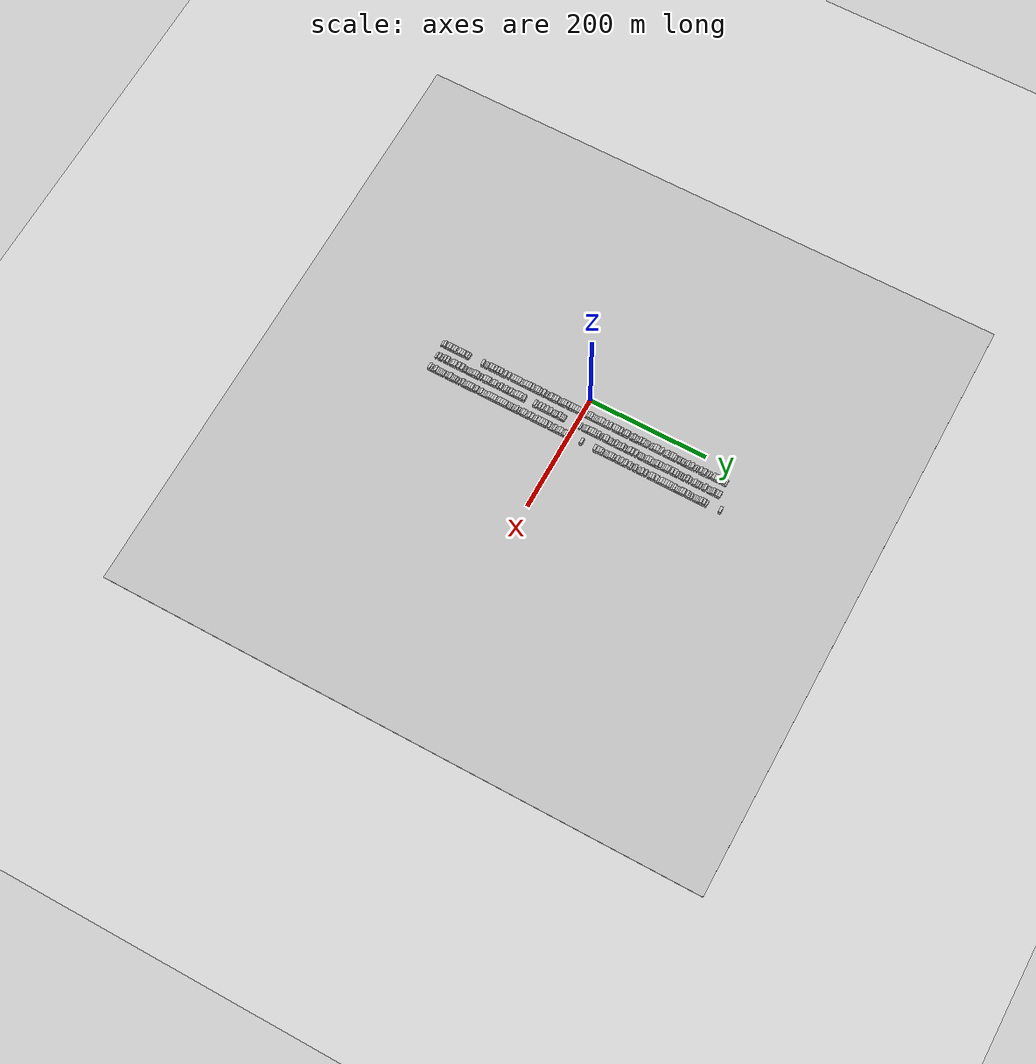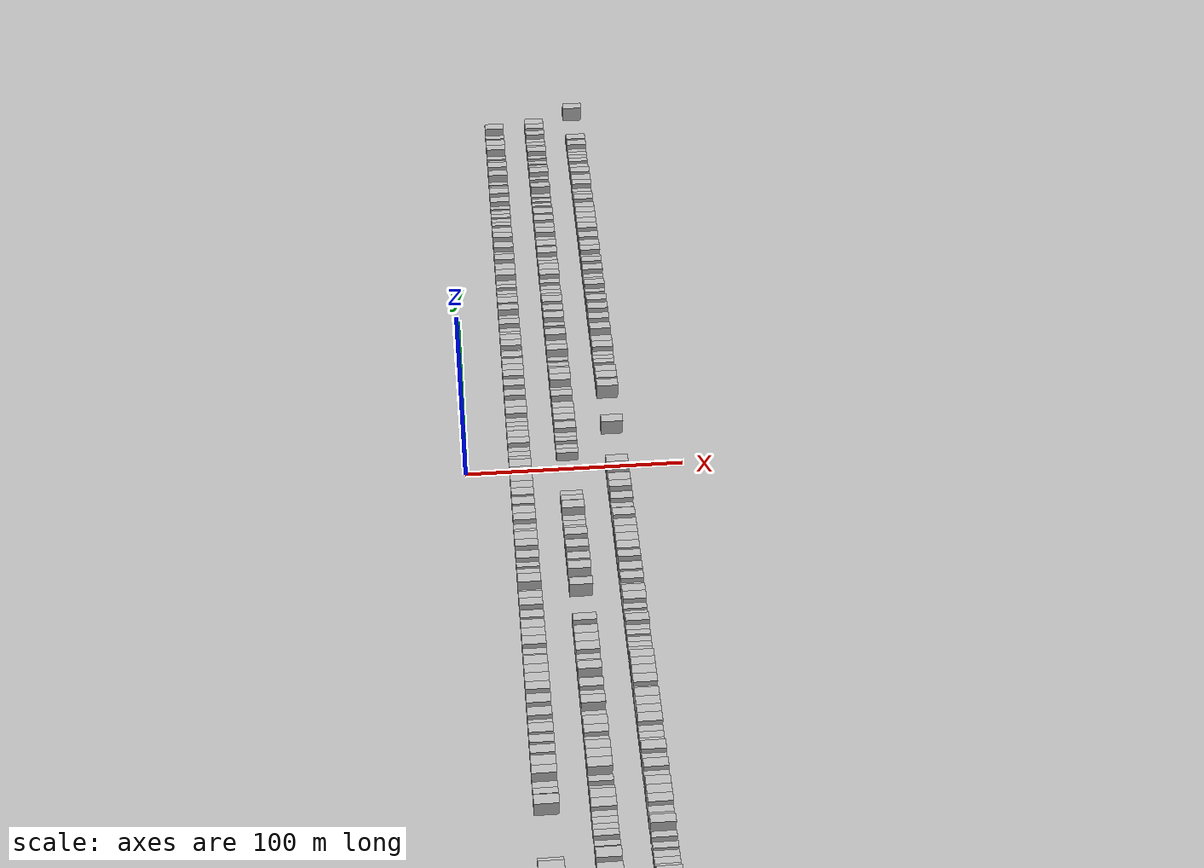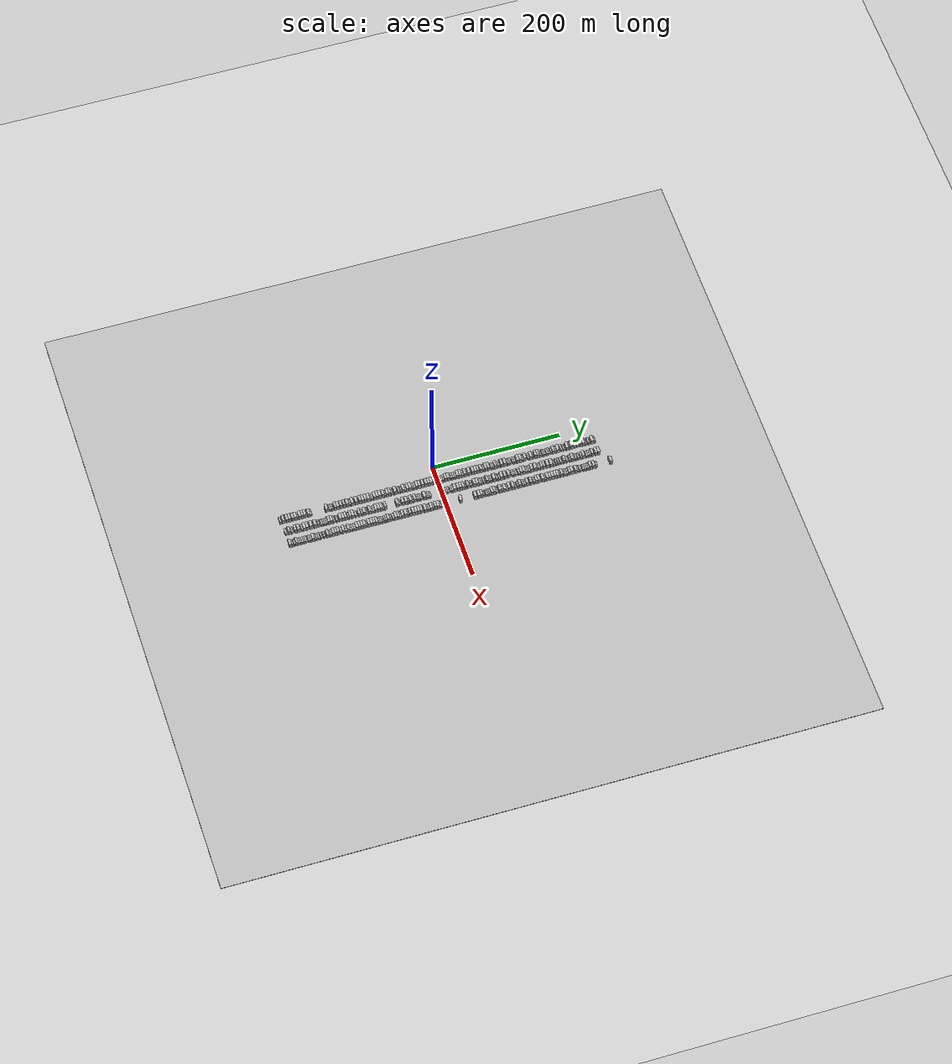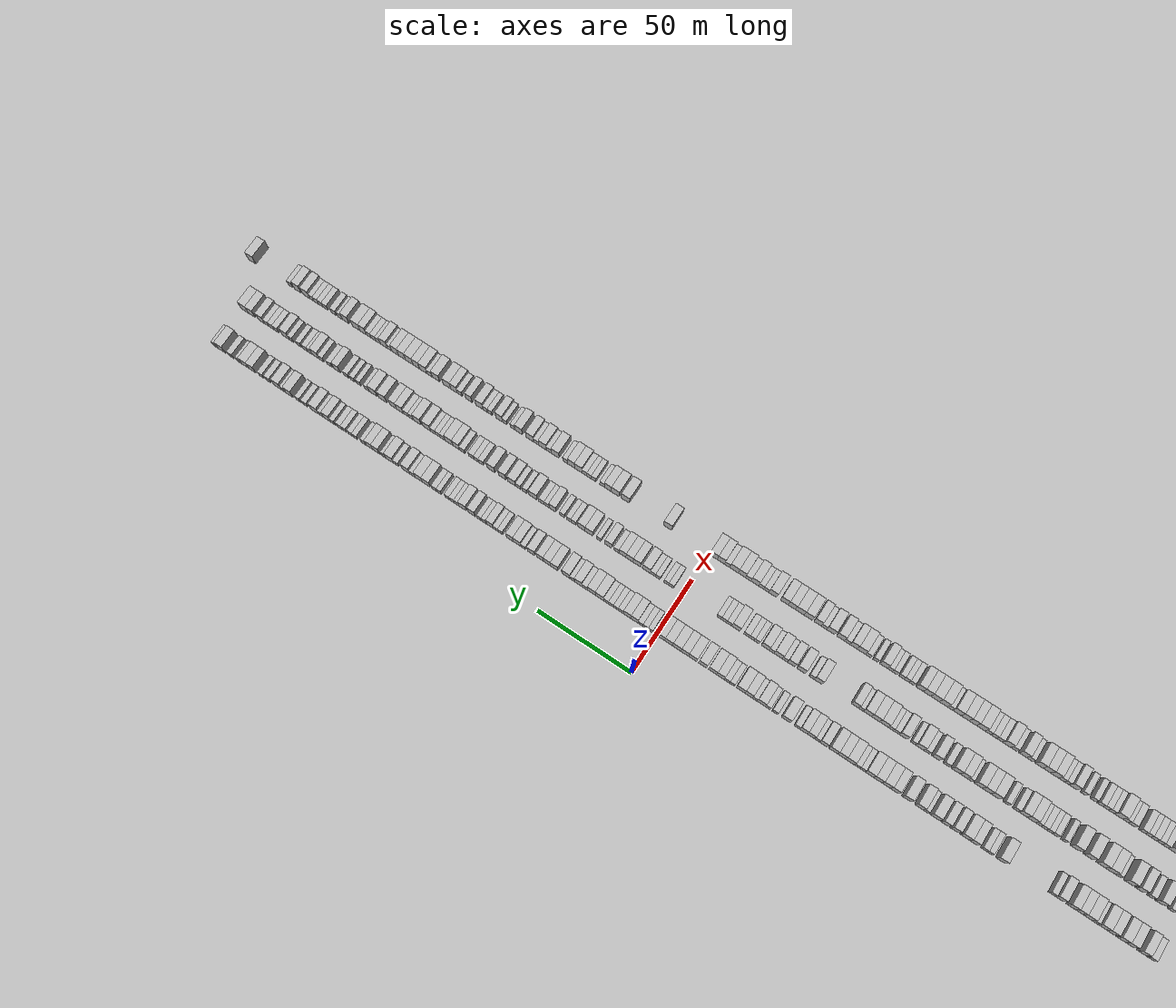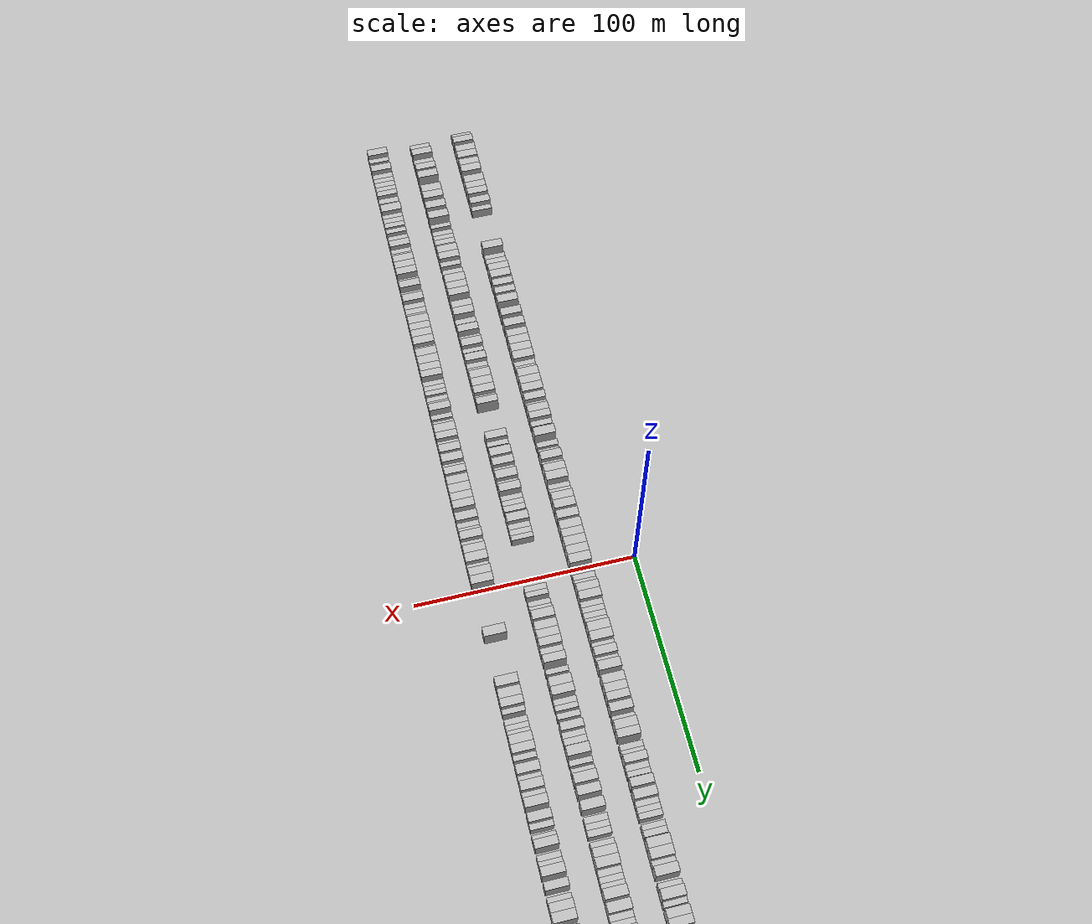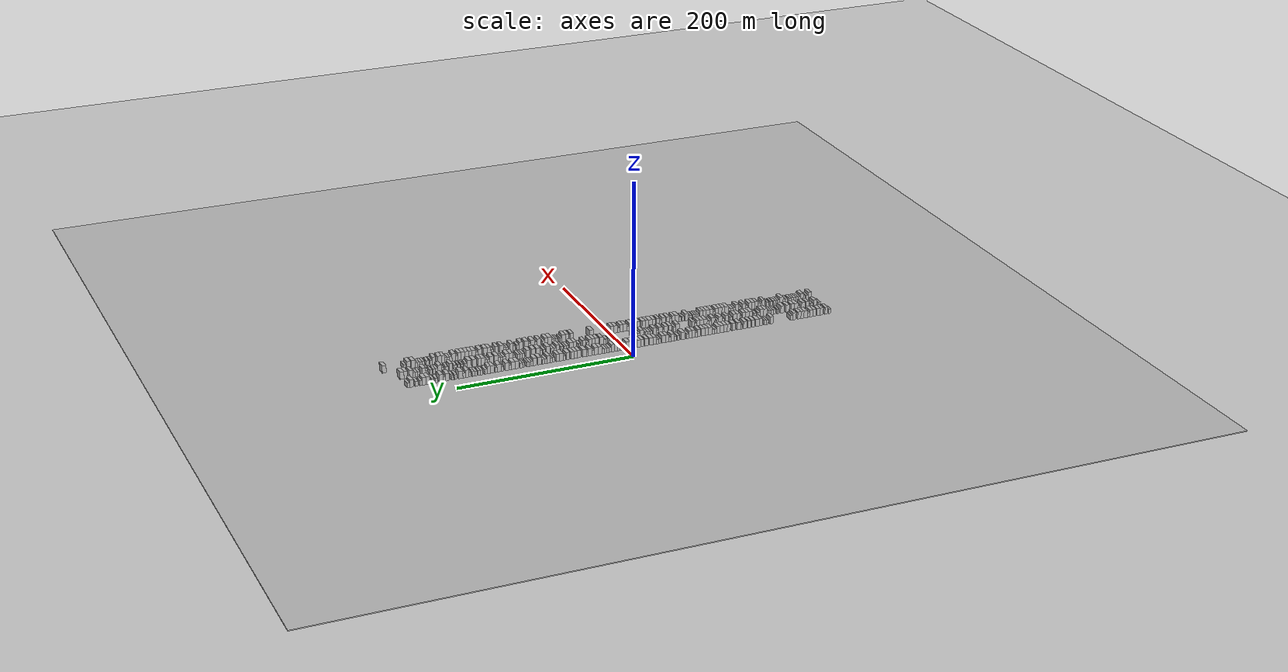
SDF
<?xml version="1.0" encoding="utf-8"?>

<sdf version="1.6">

   <world name="default">

      <gui fullscreen="0">

         <camera name="user_camera">

            <pose>-15 0 4.57585 0 0 0</pose>

            <view_controller>orbit</view_controller>

         </camera>

      </gui>

      <scene>

         <sky>

           <clouds>

             <speed>12</speed>

           </clouds>

         </sky>

         <ambient>0.4 0.4 0.4 1</ambient>

         <background>0.7 0.7 0.7 1</background>

         <shadows>1</shadows>

      </scene>

      <gravity>0 0 -9.8066</gravity>

      <magnetic_field>6e-06 2.3e-05 -4.2e-05</magnetic_field>

      <physics default="0" name="default_physics" type="ode">

         <ode>

            <solver>

               <type>quick</type>

               <iters>10</iters>

               <sor>1.0</sor>

               <use_dynamic_moi_rescaling>0</use_dynamic_moi_rescaling>

            </solver>

            <constraints>

               <cfm>0</cfm>

               <erp>0.2</erp>

               <contact_max_correcting_vel>100</contact_max_correcting_vel>

               <contact_surface_layer>0.001</contact_surface_layer>

            </constraints>

         </ode>

         <max_step_size>0.004</max_step_size>

         <real_time_factor>1</real_time_factor>

         <real_time_update_rate>250</real_time_update_rate>

      </physics>

      <light name="sun" type="directional">

         <cast_shadows>1</cast_shadows>

         <pose>0 0 10 0 0 0</pose>

         <diffuse>0.8 0.8 0.8 1</diffuse>

         <specular>0.2 0.2 0.2 1</specular>

         <attenuation>

            <range>1000</range>

            <constant>0.9</constant>

            <linear>0.01</linear>

            <quadratic>0.001</quadratic>

         </attenuation>

         <direction>-0.5 0.1 -0.9</direction>

      </light>

      <include>

         <name>ground_plane_1</name>

         <uri>model://HANNAS_ground_plane</uri>

         <pose>0 0 0  0 0 0</pose>

      </include>

      <include>

         <name>ground_plane_2</name>

         <uri>model://HANNAS_ground_plane</uri>

         <pose>100 0 0  0 0 0</pose>

      </include>

      <model name="building_1">

         <static>1</static>

         <pose frame="">25.0000 -246.5487 0 0.000000 0.000000 0.000000</pose>

         <link name="link">

            <pose frame="">0 0 3.00 0 0 0</pose>

            <collision name="collision">

               <geometry>

                  <box>

                     <size>10.0000 2.9027 6.0000</size>

                  </box>

               </geometry>

               <max_contacts>10</max_contacts>

               <surface>

                  <contact>

                     <ode/>

                  </contact>

                  <bounce/>

                  <friction>

                     <torsional>

                        <ode/>

                     </torsional>

                     <ode/>

                  </friction>

               </surface>

            </collision>

            <visual name="visual">

               <cast_shadows>0</cast_shadows>

               <geometry>

                  <box>

                     <size>10.0000 2.9027 6.0000</size>

                  </box>

               </geometry>

               <material>

                  <script>

                     <uri>model://HANNAS_wall/materials/scripts</uri>

                     <uri>model://HANNAS_wall/materials/textures</uri>

                     <name>vrc/HANNAS_wall</name>

                  </script>

               </material>

            </visual>

            <self_collide>0</self_collide>

            <enable_wind>0</enable_wind>

            <kinematic>0</kinematic>

         </link>

      </model>

      <model name="building_2">

         <static>1</static>

         <pose frame="">25.0000 -242.2511 0 0.000000 0.000000 0.000000</pose>

         <link name="link">

            <pose frame="">0 0 4.50 0 0 0</pose>

            <collision name="collision">

               <geometry>

                  <box>

                     <size>10.0000 3.6924 9.0000</size>

                  </box>

               </geometry>

               <max_contacts>10</max_contacts>

               <surface>

                  <contact>

                     <ode/>

                  </contact>

                  <bounce/>

                  <friction>

                     <torsional>

                        <ode/>

                     </torsional>

                     <ode/>

                  </friction>

               </surface>

            </collision>

            <visual name="visual">

               <cast_shadows>0</cast_shadows>

               <geometry>

                  <box>

                     <size>10.0000 3.6924 9.0000</size>

                  </box>

               </geometry>

               <material>

                  <script>

                     <uri>model://HANNAS_wall/materials/scripts</uri>

                     <uri>model://HANNAS_wall/materials/textures</uri>

                     <name>vrc/HANNAS_wall</name>

                  </script>

               </material>

            </visual>

            <self_collide>0</self_collide>

            <enable_wind>0</enable_wind>

            <kinematic>0</kinematic>

         </link>

      </model>

      <model name="building_3">

         <static>1</static>

         <pose frame="">25.0000 -236.4805 0 0.000000 0.000000 0.000000</pose>

         <link name="link">

            <pose frame="">0 0 4.50 0 0 0</pose>

            <collision name="collision">

               <geometry>

                  <box>

                     <size>10.0000 3.8489 9.0000</size>

                  </box>

               </geometry>

               <max_contacts>10</max_contacts>

               <surface>

                  <contact>

                     <ode/>

                  </contact>

                  <bounce/>

                  <friction>

                     <torsional>

                        <ode/>

                     </torsional>

                     <ode/>

                  </friction>

               </surface>

            </collision>

            <visual name="visual">

               <cast_shadows>0</cast_shadows>

               <geometry>

                  <box>

                     <size>10.0000 3.8489 9.0000</size>

                  </box>

               </geometry>

               <material>

                  <script>

                     <uri>model://HANNAS_wall/materials/scripts</uri>

                     <uri>model://HANNAS_wall/materials/textures</uri>

                     <name>vrc/HANNAS_wall</name>

                  </script>

               </material>

            </visual>

            <self_collide>0</self_collide>

            <enable_wind>0</enable_wind>

            <kinematic>0</kinematic>

         </link>

      </model>

      <model name="building_4">

         <static>1</static>

         <pose frame="">25.0000 -232.4813 0 0.000000 0.000000 0.000000</pose>

         <link name="link">

            <pose frame="">0 0 4.50 0 0 0</pose>

            <collision name="collision">

               <geometry>

                  <box>

                     <size>10.0000 4.1494 9.0000</size>

                  </box>

               </geometry>

               <max_contacts>10</max_contacts>

               <surface>

                  <contact>

                     <ode/>

                  </contact>

                  <bounce/>

                  <friction>

                     <torsional>

                        <ode/>

                     </torsional>

                     <ode/>

                  </friction>

               </surface>

            </collision>

            <visual name="visual">

               <cast_shadows>0</cast_shadows>

               <geometry>

                  <box>

                     <size>10.0000 4.1494 9.0000</size>

                  </box>

               </geometry>

               <material>

                  <script>

                     <uri>model://HANNAS_wall/materials/scripts</uri>

                     <uri>model://HANNAS_wall/materials/textures</uri>

                     <name>vrc/HANNAS_wall</name>

                  </script>

               </material>

            </visual>

            <self_collide>0</self_collide>

            <enable_wind>0</enable_wind>

            <kinematic>0</kinematic>

         </link>

      </model>

      <model name="building_5">

         <static>1</static>

         <pose frame="">25.0000 -227.5023 0 0.000000 0.000000 0.000000</pose>

         <link name="link">

            <pose frame="">0 0 4.50 0 0 0</pose>

            <collision name="collision">

               <geometry>

                  <box>

                     <size>10.0000 3.8087 9.0000</size>

                  </box>

               </geometry>

               <max_contacts>10</max_contacts>

               <surface>

                  <contact>

                     <ode/>

                  </contact>

                  <bounce/>

                  <friction>

                     <torsional>

                        <ode/>

                     </torsional>

                     <ode/>

                  </friction>

               </surface>

            </collision>

            <visual name="visual">

               <cast_shadows>0</cast_shadows>

               <geometry>

                  <box>

                     <size>10.0000 3.8087 9.0000</size>

                  </box>

               </geometry>

               <material>

                  <script>

                     <uri>model://HANNAS_wall/materials/scripts</uri>

                     <uri>model://HANNAS_wall/materials/textures</uri>

                     <name>vrc/HANNAS_wall</name>

                  </script>

               </material>

            </visual>

            <self_collide>0</self_collide>

            <enable_wind>0</enable_wind>

            <kinematic>0</kinematic>

         </link>

      </model>

      <model name="building_6">

         <static>1</static>

         <pose frame="">25.0000 -223.4394 0 0.000000 0.000000 0.000000</pose>

         <link name="link">

            <pose frame="">0 0 4.50 0 0 0</pose>

            <collision name="collision">

               <geometry>

                  <box>

                     <size>10.0000 4.3171 9.0000</size>

                  </box>

               </geometry>

               <max_contacts>10</max_contacts>

               <surface>

                  <contact>

                     <ode/>

                  </contact>

                  <bounce/>

                  <friction>

                     <torsional>

                        <ode/>

                     </torsional>

                     <ode/>

                  </friction>

               </surface>

            </collision>

            <visual name="visual">

               <cast_shadows>0</cast_shadows>

               <geometry>

                  <box>

                     <size>10.0000 4.3171 9.0000</size>

                  </box>

               </geometry>

               <material>

                  <script>

                     <uri>model://HANNAS_wall/materials/scripts</uri>

                     <uri>model://HANNAS_wall/materials/textures</uri>

                     <name>vrc/HANNAS_wall</name>

                  </script>

               </material>

            </visual>

            <self_collide>0</self_collide>

            <enable_wind>0</enable_wind>

            <kinematic>0</kinematic>

         </link>

      </model>

      <model name="building_7">

         <static>1</static>

         <pose frame="">25.0000 -219.9462 0 0.000000 0.000000 0.000000</pose>

         <link name="link">

            <pose frame="">0 0 3.00 0 0 0</pose>

            <collision name="collision">

               <geometry>

                  <box>

                     <size>10.0000 2.6692 6.0000</size>

                  </box>

               </geometry>

               <max_contacts>10</max_contacts>

               <surface>

                  <contact>

                     <ode/>

                  </contact>

                  <bounce/>

                  <friction>

                     <torsional>

                        <ode/>

                     </torsional>

                     <ode/>

                  </friction>

               </surface>

            </collision>

            <visual name="visual">

               <cast_shadows>0</cast_shadows>

               <geometry>

                  <box>

                     <size>10.0000 2.6692 6.0000</size>

                  </box>

               </geometry>

               <material>

                  <script>

                     <uri>model://HANNAS_wall/materials/scripts</uri>

                     <uri>model://HANNAS_wall/materials/textures</uri>

                     <name>vrc/HANNAS_wall</name>

                  </script>

               </material>

            </visual>

            <self_collide>0</self_collide>

            <enable_wind>0</enable_wind>

            <kinematic>0</kinematic>

         </link>

      </model>

      <model name="building_8">

         <static>1</static>

         <pose frame="">25.0000 -216.4846 0 0.000000 0.000000 0.000000</pose>

         <link name="link">

            <pose frame="">0 0 4.50 0 0 0</pose>

            <collision name="collision">

               <geometry>

                  <box>

                     <size>10.0000 4.2542 9.0000</size>

                  </box>

               </geometry>

               <max_contacts>10</max_contacts>

               <surface>

                  <contact>

                     <ode/>

                  </contact>

                  <bounce/>

                  <friction>

                     <torsional>

                        <ode/>

                     </torsional>

                     <ode/>

                  </friction>

               </surface>

            </collision>

            <visual name="visual">

               <cast_shadows>0</cast_shadows>

               <geometry>

                  <box>

                     <size>10.0000 4.2542 9.0000</size>

                  </box>

               </geometry>

               <material>

                  <script>

                     <uri>model://HANNAS_wall/materials/scripts</uri>

                     <uri>model://HANNAS_wall/materials/textures</uri>

                     <name>vrc/HANNAS_wall</name>

                  </script>

               </material>

            </visual>

            <self_collide>0</self_collide>

            <enable_wind>0</enable_wind>

            <kinematic>0</kinematic>

         </link>

      </model>

      <model name="building_9">

         <static>1</static>

         <pose frame="">25.0000 -212.4910 0 0.000000 0.000000 0.000000</pose>

         <link name="link">

            <pose frame="">0 0 4.50 0 0 0</pose>

            <collision name="collision">

               <geometry>

                  <box>

                     <size>10.0000 3.7329 9.0000</size>

                  </box>

               </geometry>

               <max_contacts>10</max_contacts>

               <surface>

                  <contact>

                     <ode/>

                  </contact>

                  <bounce/>

                  <friction>

                     <torsional>

                        <ode/>

                     </torsional>

                     <ode/>

                  </friction>

               </surface>

            </collision>

            <visual name="visual">

               <cast_shadows>0</cast_shadows>

               <geometry>

                  <box>

                     <size>10.0000 3.7329 9.0000</size>

                  </box>

               </geometry>

               <material>

                  <script>

                     <uri>model://HANNAS_wall/materials/scripts</uri>

                     <uri>model://HANNAS_wall/materials/textures</uri>

                     <name>vrc/HANNAS_wall</name>

                  </script>

               </material>

            </visual>

            <self_collide>0</self_collide>

            <enable_wind>0</enable_wind>

            <kinematic>0</kinematic>

         </link>

      </model>

      <model name="building_10">

         <static>1</static>

         <pose frame="">25.0000 -208.6868 0 0.000000 0.000000 0.000000</pose>

         <link name="link">

            <pose frame="">0 0 4.50 0 0 0</pose>

            <collision name="collision">

               <geometry>

                  <box>

                     <size>10.0000 3.8755 9.0000</size>

                  </box>

               </geometry>

               <max_contacts>10</max_contacts>

               <surface>

                  <contact>

                     <ode/>

                  </contact>

                  <bounce/>

                  <friction>

                     <torsional>

                        <ode/>

                     </torsional>

                     <ode/>

                  </friction>

               </surface>

            </collision>

            <visual name="visual">

               <cast_shadows>0</cast_shadows>

               <geometry>

                  <box>

                     <size>10.0000 3.8755 9.0000</size>

                  </box>

               </geometry>

               <material>

                  <script>

                     <uri>model://HANNAS_wall/materials/scripts</uri>

                     <uri>model://HANNAS_wall/materials/textures</uri>

                     <name>vrc/HANNAS_wall</name>

                  </script>

               </material>

            </visual>

            <self_collide>0</self_collide>

            <enable_wind>0</enable_wind>

            <kinematic>0</kinematic>

         </link>

      </model>

      <model name="building_11">

         <static>1</static>

         <pose frame="">25.0000 -202.7853 0 0.000000 0.000000 0.000000</pose>

         <link name="link">

            <pose frame="">0 0 4.50 0 0 0</pose>

            <collision name="collision">

               <geometry>

                  <box>

                     <size>10.0000 3.9275 9.0000</size>

                  </box>

               </geometry>

               <max_contacts>10</max_contacts>

               <surface>

                  <contact>

                     <ode/>

                  </contact>

                  <bounce/>

                  <friction>

                     <torsional>

                        <ode/>

                     </torsional>

                     <ode/>

                  </friction>

               </surface>

            </collision>

            <visual name="visual">

               <cast_shadows>0</cast_shadows>

               <geometry>

                  <box>

                     <size>10.0000 3.9275 9.0000</size>

                  </box>

               </geometry>

               <material>

                  <script>

                     <uri>model://HANNAS_wall/materials/scripts</uri>

                     <uri>model://HANNAS_wall/materials/textures</uri>

                     <name>vrc/HANNAS_wall</name>

                  </script>

               </material>

            </visual>

            <self_collide>0</self_collide>

            <enable_wind>0</enable_wind>

            <kinematic>0</kinematic>

         </link>

      </model>

      <model name="building_12">

         <static>1</static>

         <pose frame="">25.0000 -199.4388 0 0.000000 0.000000 0.000000</pose>

         <link name="link">

            <pose frame="">0 0 3.00 0 0 0</pose>

            <collision name="collision">

               <geometry>

                  <box>

                     <size>10.0000 2.7654 6.0000</size>

                  </box>

               </geometry>

               <max_contacts>10</max_contacts>

               <surface>

                  <contact>

                     <ode/>

                  </contact>

                  <bounce/>

                  <friction>

                     <torsional>

                        <ode/>

                     </torsional>

                     <ode/>

                  </friction>

               </surface>

            </collision>

            <visual name="visual">

               <cast_shadows>0</cast_shadows>

               <geometry>

                  <box>

                     <size>10.0000 2.7654 6.0000</size>

                  </box>

               </geometry>

               <material>

                  <script>

                     <uri>model://HANNAS_wall/materials/scripts</uri>

                     <uri>model://HANNAS_wall/materials/textures</uri>

                     <name>vrc/HANNAS_wall</name>

                  </script>

               </material>

            </visual>

            <self_collide>0</self_collide>

            <enable_wind>0</enable_wind>

            <kinematic>0</kinematic>

         </link>

      </model>

      <model name="building_13">

         <static>1</static>

         <pose frame="">25.0000 -174.6984 0 0.000000 0.000000 0.000000</pose>

         <link name="link">

            <pose frame="">0 0 4.50 0 0 0</pose>

            <collision name="collision">

               <geometry>

                  <box>

                     <size>10.0000 4.2385 9.0000</size>

                  </box>

               </geometry>

               <max_contacts>10</max_contacts>

               <surface>

                  <contact>

                     <ode/>

                  </contact>

                  <bounce/>

                  <friction>

                     <torsional>

                        <ode/>

                     </torsional>

                     <ode/>

                  </friction>

               </surface>

            </collision>

            <visual name="visual">

               <cast_shadows>0</cast_shadows>

               <geometry>

                  <box>

                     <size>10.0000 4.2385 9.0000</size>

                  </box>

               </geometry>

               <material>

                  <script>

                     <uri>model://HANNAS_wall/materials/scripts</uri>

                     <uri>model://HANNAS_wall/materials/textures</uri>

                     <name>vrc/HANNAS_wall</name>

                  </script>

               </material>

            </visual>

            <self_collide>0</self_collide>

            <enable_wind>0</enable_wind>

            <kinematic>0</kinematic>

         </link>

      </model>

      <model name="building_14">

         <static>1</static>

         <pose frame="">25.0000 -169.2797 0 0.000000 0.000000 0.000000</pose>

         <link name="link">

            <pose frame="">0 0 3.00 0 0 0</pose>

            <collision name="collision">

               <geometry>

                  <box>

                     <size>10.0000 2.5990 6.0000</size>

                  </box>

               </geometry>

               <max_contacts>10</max_contacts>

               <surface>

                  <contact>

                     <ode/>

                  </contact>

                  <bounce/>

                  <friction>

                     <torsional>

                        <ode/>

                     </torsional>

                     <ode/>

                  </friction>

               </surface>

            </collision>

            <visual name="visual">

               <cast_shadows>0</cast_shadows>

               <geometry>

                  <box>

                     <size>10.0000 2.5990 6.0000</size>

                  </box>

               </geometry>

               <material>

                  <script>

                     <uri>model://HANNAS_wall/materials/scripts</uri>

                     <uri>model://HANNAS_wall/materials/textures</uri>

                     <name>vrc/HANNAS_wall</name>

                  </script>

               </material>

            </visual>

            <self_collide>0</self_collide>

            <enable_wind>0</enable_wind>

            <kinematic>0</kinematic>

         </link>

      </model>

      <model name="building_15">

         <static>1</static>

         <pose frame="">25.0000 -166.6091 0 0.000000 0.000000 0.000000</pose>

         <link name="link">

            <pose frame="">0 0 3.00 0 0 0</pose>

            <collision name="collision">

               <geometry>

                  <box>

                     <size>10.0000 2.7422 6.0000</size>

                  </box>

               </geometry>

               <max_contacts>10</max_contacts>

               <surface>

                  <contact>

                     <ode/>

                  </contact>

                  <bounce/>

                  <friction>

                     <torsional>

                        <ode/>

                     </torsional>

                     <ode/>

                  </friction>

               </surface>

            </collision>

            <visual name="visual">

               <cast_shadows>0</cast_shadows>

               <geometry>

                  <box>

                     <size>10.0000 2.7422 6.0000</size>

                  </box>

               </geometry>

               <material>

                  <script>

                     <uri>model://HANNAS_wall/materials/scripts</uri>

                     <uri>model://HANNAS_wall/materials/textures</uri>

                     <name>vrc/HANNAS_wall</name>

                  </script>

               </material>

            </visual>

            <self_collide>0</self_collide>

            <enable_wind>0</enable_wind>

            <kinematic>0</kinematic>

         </link>

      </model>

      <model name="building_16">

         <static>1</static>

         <pose frame="">25.0000 -161.3893 0 0.000000 0.000000 0.000000</pose>

         <link name="link">

            <pose frame="">0 0 4.50 0 0 0</pose>

            <collision name="collision">

               <geometry>

                  <box>

                     <size>10.0000 3.6974 9.0000</size>

                  </box>

               </geometry>

               <max_contacts>10</max_contacts>

               <surface>

                  <contact>

                     <ode/>

                  </contact>

                  <bounce/>

                  <friction>

                     <torsional>

                        <ode/>

                     </torsional>

                     <ode/>

                  </friction>

               </surface>

            </collision>

            <visual name="visual">

               <cast_shadows>0</cast_shadows>

               <geometry>

                  <box>

                     <size>10.0000 3.6974 9.0000</size>

                  </box>

               </geometry>

               <material>

                  <script>

                     <uri>model://HANNAS_wall/materials/scripts</uri>

                     <uri>model://HANNAS_wall/materials/textures</uri>

                     <name>vrc/HANNAS_wall</name>

                  </script>

               </material>

            </visual>

            <self_collide>0</self_collide>

            <enable_wind>0</enable_wind>

            <kinematic>0</kinematic>

         </link>

      </model>

      <model name="building_17">

         <static>1</static>

         <pose frame="">25.0000 -157.3042 0 0.000000 0.000000 0.000000</pose>

         <link name="link">

            <pose frame="">0 0 4.50 0 0 0</pose>

            <collision name="collision">

               <geometry>

                  <box>

                     <size>10.0000 4.4729 9.0000</size>

                  </box>

               </geometry>

               <max_contacts>10</max_contacts>

               <surface>

                  <contact>

                     <ode/>

                  </contact>

                  <bounce/>

                  <friction>

                     <torsional>

                        <ode/>

                     </torsional>

                     <ode/>

                  </friction>

               </surface>

            </collision>

            <visual name="visual">

               <cast_shadows>0</cast_shadows>

               <geometry>

                  <box>

                     <size>10.0000 4.4729 9.0000</size>

                  </box>

               </geometry>

               <material>

                  <script>

                     <uri>model://HANNAS_wall/materials/scripts</uri>

                     <uri>model://HANNAS_wall/materials/textures</uri>

                     <name>vrc/HANNAS_wall</name>

                  </script>

               </material>

            </visual>

            <self_collide>0</self_collide>

            <enable_wind>0</enable_wind>

            <kinematic>0</kinematic>

         </link>

      </model>

      <model name="building_18">

         <static>1</static>

         <pose frame="">25.0000 -152.1497 0 0.000000 0.000000 0.000000</pose>

         <link name="link">

            <pose frame="">0 0 4.50 0 0 0</pose>

            <collision name="collision">

               <geometry>

                  <box>

                     <size>10.0000 3.8361 9.0000</size>

                  </box>

               </geometry>

               <max_contacts>10</max_contacts>

               <surface>

                  <contact>

                     <ode/>

                  </contact>

                  <bounce/>

                  <friction>

                     <torsional>

                        <ode/>

                     </torsional>

                     <ode/>

                  </friction>

               </surface>

            </collision>

            <visual name="visual">

               <cast_shadows>0</cast_shadows>

               <geometry>

                  <box>

                     <size>10.0000 3.8361 9.0000</size>

                  </box>

               </geometry>

               <material>

                  <script>

                     <uri>model://HANNAS_wall/materials/scripts</uri>

                     <uri>model://HANNAS_wall/materials/textures</uri>

                     <name>vrc/HANNAS_wall</name>

                  </script>

               </material>

            </visual>

            <self_collide>0</self_collide>

            <enable_wind>0</enable_wind>

            <kinematic>0</kinematic>

         </link>

      </model>

      <model name="building_19">

         <static>1</static>

         <pose frame="">25.0000 -147.4232 0 0.000000 0.000000 0.000000</pose>

         <link name="link">

            <pose frame="">0 0 4.50 0 0 0</pose>

            <collision name="collision">

               <geometry>

                  <box>

                     <size>10.0000 3.6168 9.0000</size>

                  </box>

               </geometry>

               <max_contacts>10</max_contacts>

               <surface>

                  <contact>

                     <ode/>

                  </contact>

                  <bounce/>

                  <friction>

                     <torsional>

                        <ode/>

                     </torsional>

                     <ode/>

                  </friction>

               </surface>

            </collision>

            <visual name="visual">

               <cast_shadows>0</cast_shadows>

               <geometry>

                  <box>

                     <size>10.0000 3.6168 9.0000</size>

                  </box>

               </geometry>

               <material>

                  <script>

                     <uri>model://HANNAS_wall/materials/scripts</uri>

                     <uri>model://HANNAS_wall/materials/textures</uri>

                     <name>vrc/HANNAS_wall</name>

                  </script>

               </material>

            </visual>

            <self_collide>0</self_collide>

            <enable_wind>0</enable_wind>

            <kinematic>0</kinematic>

         </link>

      </model>

      <model name="building_20">

         <static>1</static>

         <pose frame="">25.0000 -142.4273 0 0.000000 0.000000 0.000000</pose>

         <link name="link">

            <pose frame="">0 0 4.50 0 0 0</pose>

            <collision name="collision">

               <geometry>

                  <box>

                     <size>10.0000 4.3751 9.0000</size>

                  </box>

               </geometry>

               <max_contacts>10</max_contacts>

               <surface>

                  <contact>

                     <ode/>

                  </contact>

                  <bounce/>

                  <friction>

                     <torsional>

                        <ode/>

                     </torsional>

                     <ode/>

                  </friction>

               </surface>

            </collision>

            <visual name="visual">

               <cast_shadows>0</cast_shadows>

               <geometry>

                  <box>

                     <size>10.0000 4.3751 9.0000</size>

                  </box>

               </geometry>

               <material>

                  <script>

                     <uri>model://HANNAS_wall/materials/scripts</uri>

                     <uri>model://HANNAS_wall/materials/textures</uri>

                     <name>vrc/HANNAS_wall</name>

                  </script>

               </material>

            </visual>

            <self_collide>0</self_collide>

            <enable_wind>0</enable_wind>

            <kinematic>0</kinematic>

         </link>

      </model>

      <model name="building_21">

         <static>1</static>

         <pose frame="">25.0000 -138.0152 0 0.000000 0.000000 0.000000</pose>

         <link name="link">

            <pose frame="">0 0 3.00 0 0 0</pose>

            <collision name="collision">

               <geometry>

                  <box>

                     <size>10.0000 2.4492 6.0000</size>

                  </box>

               </geometry>

               <max_contacts>10</max_contacts>

               <surface>

                  <contact>

                     <ode/>

                  </contact>

                  <bounce/>

                  <friction>

                     <torsional>

                        <ode/>

                     </torsional>

                     <ode/>

                  </friction>

               </surface>

            </collision>

            <visual name="visual">

               <cast_shadows>0</cast_shadows>

               <geometry>

                  <box>

                     <size>10.0000 2.4492 6.0000</size>

                  </box>

               </geometry>

               <material>

                  <script>

                     <uri>model://HANNAS_wall/materials/scripts</uri>

                     <uri>model://HANNAS_wall/materials/textures</uri>

                     <name>vrc/HANNAS_wall</name>

                  </script>

               </material>

            </visual>

            <self_collide>0</self_collide>

            <enable_wind>0</enable_wind>

            <kinematic>0</kinematic>

         </link>

      </model>

      <model name="building_22">

         <static>1</static>

         <pose frame="">25.0000 -134.7343 0 0.000000 0.000000 0.000000</pose>

         <link name="link">

            <pose frame="">0 0 4.50 0 0 0</pose>

            <collision name="collision">

               <geometry>

                  <box>

                     <size>10.0000 4.1126 9.0000</size>

                  </box>

               </geometry>

               <max_contacts>10</max_contacts>

               <surface>

                  <contact>

                     <ode/>

                  </contact>

                  <bounce/>

                  <friction>

                     <torsional>

                        <ode/>

                     </torsional>

                     <ode/>

                  </friction>

               </surface>

            </collision>

            <visual name="visual">

               <cast_shadows>0</cast_shadows>

               <geometry>

                  <box>

                     <size>10.0000 4.1126 9.0000</size>

                  </box>

               </geometry>

               <material>

                  <script>

                     <uri>model://HANNAS_wall/materials/scripts</uri>

                     <uri>model://HANNAS_wall/materials/textures</uri>

                     <name>vrc/HANNAS_wall</name>

                  </script>

               </material>

            </visual>

            <self_collide>0</self_collide>

            <enable_wind>0</enable_wind>

            <kinematic>0</kinematic>

         </link>

      </model>

      <model name="building_23">

         <static>1</static>

         <pose frame="">25.0000 -128.4942 0 0.000000 0.000000 0.000000</pose>

         <link name="link">

            <pose frame="">0 0 4.50 0 0 0</pose>

            <collision name="collision">

               <geometry>

                  <box>

                     <size>10.0000 4.3674 9.0000</size>

                  </box>

               </geometry>

               <max_contacts>10</max_contacts>

               <surface>

                  <contact>

                     <ode/>

                  </contact>

                  <bounce/>

                  <friction>

                     <torsional>

                        <ode/>

                     </torsional>

                     <ode/>

                  </friction>

               </surface>

            </collision>

            <visual name="visual">

               <cast_shadows>0</cast_shadows>

               <geometry>

                  <box>

                     <size>10.0000 4.3674 9.0000</size>

                  </box>

               </geometry>

               <material>

                  <script>

                     <uri>model://HANNAS_wall/materials/scripts</uri>

                     <uri>model://HANNAS_wall/materials/textures</uri>

                     <name>vrc/HANNAS_wall</name>

                  </script>

               </material>

            </visual>

            <self_collide>0</self_collide>

            <enable_wind>0</enable_wind>

            <kinematic>0</kinematic>

         </link>

      </model>

      <model name="building_24">

         <static>1</static>

         <pose frame="">25.0000 -122.4114 0 0.000000 0.000000 0.000000</pose>

         <link name="link">

            <pose frame="">0 0 4.50 0 0 0</pose>

            <collision name="collision">

               <geometry>

                  <box>

                     <size>10.0000 3.7984 9.0000</size>

                  </box>

               </geometry>

               <max_contacts>10</max_contacts>

               <surface>

                  <contact>

                     <ode/>

                  </contact>

                  <bounce/>

                  <friction>

                     <torsional>

                        <ode/>

                     </torsional>

                     <ode/>

                  </friction>

               </surface>

            </collision>

            <visual name="visual">

               <cast_shadows>0</cast_shadows>

               <geometry>

                  <box>

                     <size>10.0000 3.7984 9.0000</size>

                  </box>

               </geometry>

               <material>

                  <script>

                     <uri>model://HANNAS_wall/materials/scripts</uri>

                     <uri>model://HANNAS_wall/materials/textures</uri>

                     <name>vrc/HANNAS_wall</name>

                  </script>

               </material>

            </visual>

            <self_collide>0</self_collide>

            <enable_wind>0</enable_wind>

            <kinematic>0</kinematic>

         </link>

      </model>

      <model name="building_25">

         <static>1</static>

         <pose frame="">25.0000 -118.3592 0 0.000000 0.000000 0.000000</pose>

         <link name="link">

            <pose frame="">0 0 4.50 0 0 0</pose>

            <collision name="collision">

               <geometry>

                  <box>

                     <size>10.0000 4.3058 9.0000</size>

                  </box>

               </geometry>

               <max_contacts>10</max_contacts>

               <surface>

                  <contact>

                     <ode/>

                  </contact>

                  <bounce/>

                  <friction>

                     <torsional>

                        <ode/>

                     </torsional>

                     <ode/>

                  </friction>

               </surface>

            </collision>

            <visual name="visual">

               <cast_shadows>0</cast_shadows>

               <geometry>

                  <box>

                     <size>10.0000 4.3058 9.0000</size>

                  </box>

               </geometry>

               <material>

                  <script>

                     <uri>model://HANNAS_wall/materials/scripts</uri>

                     <uri>model://HANNAS_wall/materials/textures</uri>

                     <name>vrc/HANNAS_wall</name>

                  </script>

               </material>

            </visual>

            <self_collide>0</self_collide>

            <enable_wind>0</enable_wind>

            <kinematic>0</kinematic>

         </link>

      </model>

      <model name="building_26">

         <static>1</static>

         <pose frame="">25.0000 -114.1197 0 0.000000 0.000000 0.000000</pose>

         <link name="link">

            <pose frame="">0 0 4.50 0 0 0</pose>

            <collision name="collision">

               <geometry>

                  <box>

                     <size>10.0000 4.1732 9.0000</size>

                  </box>

               </geometry>

               <max_contacts>10</max_contacts>

               <surface>

                  <contact>

                     <ode/>

                  </contact>

                  <bounce/>

                  <friction>

                     <torsional>

                        <ode/>

                     </torsional>

                     <ode/>

                  </friction>

               </surface>

            </collision>

            <visual name="visual">

               <cast_shadows>0</cast_shadows>

               <geometry>

                  <box>

                     <size>10.0000 4.1732 9.0000</size>

                  </box>

               </geometry>

               <material>

                  <script>

                     <uri>model://HANNAS_wall/materials/scripts</uri>

                     <uri>model://HANNAS_wall/materials/textures</uri>

                     <name>vrc/HANNAS_wall</name>

                  </script>

               </material>

            </visual>

            <self_collide>0</self_collide>

            <enable_wind>0</enable_wind>

            <kinematic>0</kinematic>

         </link>

      </model>

      <model name="building_27">

         <static>1</static>

         <pose frame="">25.0000 -109.8321 0 0.000000 0.000000 0.000000</pose>

         <link name="link">

            <pose frame="">0 0 4.50 0 0 0</pose>

            <collision name="collision">

               <geometry>

                  <box>

                     <size>10.0000 4.4021 9.0000</size>

                  </box>

               </geometry>

               <max_contacts>10</max_contacts>

               <surface>

                  <contact>

                     <ode/>

                  </contact>

                  <bounce/>

                  <friction>

                     <torsional>

                        <ode/>

                     </torsional>

                     <ode/>

                  </friction>

               </surface>

            </collision>

            <visual name="visual">

               <cast_shadows>0</cast_shadows>

               <geometry>

                  <box>

                     <size>10.0000 4.4021 9.0000</size>

                  </box>

               </geometry>

               <material>

                  <script>

                     <uri>model://HANNAS_wall/materials/scripts</uri>

                     <uri>model://HANNAS_wall/materials/textures</uri>

                     <name>vrc/HANNAS_wall</name>

                  </script>

               </material>

            </visual>

            <self_collide>0</self_collide>

            <enable_wind>0</enable_wind>

            <kinematic>0</kinematic>

         </link>

      </model>

      <model name="building_28">

         <static>1</static>

         <pose frame="">25.0000 -106.3405 0 0.000000 0.000000 0.000000</pose>

         <link name="link">

            <pose frame="">0 0 3.00 0 0 0</pose>

            <collision name="collision">

               <geometry>

                  <box>

                     <size>10.0000 2.5811 6.0000</size>

                  </box>

               </geometry>

               <max_contacts>10</max_contacts>

               <surface>

                  <contact>

                     <ode/>

                  </contact>

                  <bounce/>

                  <friction>

                     <torsional>

                        <ode/>

                     </torsional>

                     <ode/>

                  </friction>

               </surface>

            </collision>

            <visual name="visual">

               <cast_shadows>0</cast_shadows>

               <geometry>

                  <box>

                     <size>10.0000 2.5811 6.0000</size>

                  </box>

               </geometry>

               <material>

                  <script>

                     <uri>model://HANNAS_wall/materials/scripts</uri>

                     <uri>model://HANNAS_wall/materials/textures</uri>

                     <name>vrc/HANNAS_wall</name>

                  </script>

               </material>

            </visual>

            <self_collide>0</self_collide>

            <enable_wind>0</enable_wind>

            <kinematic>0</kinematic>

         </link>

      </model>

      <model name="building_29">

         <static>1</static>

         <pose frame="">25.0000 -103.6158 0 0.000000 0.000000 0.000000</pose>

         <link name="link">

            <pose frame="">0 0 3.00 0 0 0</pose>

            <collision name="collision">

               <geometry>

                  <box>

                     <size>10.0000 2.8682 6.0000</size>

                  </box>

               </geometry>

               <max_contacts>10</max_contacts>

               <surface>

                  <contact>

                     <ode/>

                  </contact>

                  <bounce/>

                  <friction>

                     <torsional>

                        <ode/>

                     </torsional>

                     <ode/>

                  </friction>

               </surface>

            </collision>

            <visual name="visual">

               <cast_shadows>0</cast_shadows>

               <geometry>

                  <box>

                     <size>10.0000 2.8682 6.0000</size>

                  </box>

               </geometry>

               <material>

                  <script>

                     <uri>model://HANNAS_wall/materials/scripts</uri>

                     <uri>model://HANNAS_wall/materials/textures</uri>

                     <name>vrc/HANNAS_wall</name>

                  </script>

               </material>

            </visual>

            <self_collide>0</self_collide>

            <enable_wind>0</enable_wind>

            <kinematic>0</kinematic>

         </link>

      </model>

      <model name="building_30">

         <static>1</static>

         <pose frame="">25.0000 -100.0108 0 0.000000 0.000000 0.000000</pose>

         <link name="link">

            <pose frame="">0 0 4.50 0 0 0</pose>

            <collision name="collision">

               <geometry>

                  <box>

                     <size>10.0000 4.3418 9.0000</size>

                  </box>

               </geometry>

               <max_contacts>10</max_contacts>

               <surface>

                  <contact>

                     <ode/>

                  </contact>

                  <bounce/>

                  <friction>

                     <torsional>

                        <ode/>

                     </torsional>

                     <ode/>

                  </friction>

               </surface>

            </collision>

            <visual name="visual">

               <cast_shadows>0</cast_shadows>

               <geometry>

                  <box>

                     <size>10.0000 4.3418 9.0000</size>

                  </box>

               </geometry>

               <material>

                  <script>

                     <uri>model://HANNAS_wall/materials/scripts</uri>

                     <uri>model://HANNAS_wall/materials/textures</uri>

                     <name>vrc/HANNAS_wall</name>

                  </script>

               </material>

            </visual>

            <self_collide>0</self_collide>

            <enable_wind>0</enable_wind>

            <kinematic>0</kinematic>

         </link>

      </model>

      <model name="building_31">

         <static>1</static>

         <pose frame="">25.0000 -95.7848 0 0.000000 0.000000 0.000000</pose>

         <link name="link">

            <pose frame="">0 0 4.50 0 0 0</pose>

            <collision name="collision">

               <geometry>

                  <box>

                     <size>10.0000 4.1102 9.0000</size>

                  </box>

               </geometry>

               <max_contacts>10</max_contacts>

               <surface>

                  <contact>

                     <ode/>

                  </contact>

                  <bounce/>

                  <friction>

                     <torsional>

                        <ode/>

                     </torsional>

                     <ode/>

                  </friction>

               </surface>

            </collision>

            <visual name="visual">

               <cast_shadows>0</cast_shadows>

               <geometry>

                  <box>

                     <size>10.0000 4.1102 9.0000</size>

                  </box>

               </geometry>

               <material>

                  <script>

                     <uri>model://HANNAS_wall/materials/scripts</uri>

                     <uri>model://HANNAS_wall/materials/textures</uri>

                     <name>vrc/HANNAS_wall</name>

                  </script>

               </material>

            </visual>

            <self_collide>0</self_collide>

            <enable_wind>0</enable_wind>

            <kinematic>0</kinematic>

         </link>

      </model>

      <model name="building_32">

         <static>1</static>

         <pose frame="">25.0000 -91.6138 0 0.000000 0.000000 0.000000</pose>

         <link name="link">

            <pose frame="">0 0 4.50 0 0 0</pose>

            <collision name="collision">

               <geometry>

                  <box>

                     <size>10.0000 4.2317 9.0000</size>

                  </box>

               </geometry>

               <max_contacts>10</max_contacts>

               <surface>

                  <contact>

                     <ode/>

                  </contact>

                  <bounce/>

                  <friction>

                     <torsional>

                        <ode/>

                     </torsional>

                     <ode/>

                  </friction>

               </surface>

            </collision>

            <visual name="visual">

               <cast_shadows>0</cast_shadows>

               <geometry>

                  <box>

                     <size>10.0000 4.2317 9.0000</size>

                  </box>

               </geometry>

               <material>

                  <script>

                     <uri>model://HANNAS_wall/materials/scripts</uri>

                     <uri>model://HANNAS_wall/materials/textures</uri>

                     <name>vrc/HANNAS_wall</name>

                  </script>

               </material>

            </visual>

            <self_collide>0</self_collide>

            <enable_wind>0</enable_wind>

            <kinematic>0</kinematic>

         </link>

      </model>

      <model name="building_33">

         <static>1</static>

         <pose frame="">25.0000 -86.5945 0 0.000000 0.000000 0.000000</pose>

         <link name="link">

            <pose frame="">0 0 4.50 0 0 0</pose>

            <collision name="collision">

               <geometry>

                  <box>

                     <size>10.0000 3.8068 9.0000</size>

                  </box>

               </geometry>

               <max_contacts>10</max_contacts>

               <surface>

                  <contact>

                     <ode/>

                  </contact>

                  <bounce/>

                  <friction>

                     <torsional>

                        <ode/>

                     </torsional>

                     <ode/>

                  </friction>

               </surface>

            </collision>

            <visual name="visual">

               <cast_shadows>0</cast_shadows>

               <geometry>

                  <box>

                     <size>10.0000 3.8068 9.0000</size>

                  </box>

               </geometry>

               <material>

                  <script>

                     <uri>model://HANNAS_wall/materials/scripts</uri>

                     <uri>model://HANNAS_wall/materials/textures</uri>

                     <name>vrc/HANNAS_wall</name>

                  </script>

               </material>

            </visual>

            <self_collide>0</self_collide>

            <enable_wind>0</enable_wind>

            <kinematic>0</kinematic>

         </link>

      </model>

      <model name="building_34">

         <static>1</static>

         <pose frame="">25.0000 -83.3781 0 0.000000 0.000000 0.000000</pose>

         <link name="link">

            <pose frame="">0 0 3.00 0 0 0</pose>

            <collision name="collision">

               <geometry>

                  <box>

                     <size>10.0000 2.6260 6.0000</size>

                  </box>

               </geometry>

               <max_contacts>10</max_contacts>

               <surface>

                  <contact>

                     <ode/>

                  </contact>

                  <bounce/>

                  <friction>

                     <torsional>

                        <ode/>

                     </torsional>

                     <ode/>

                  </friction>

               </surface>

            </collision>

            <visual name="visual">

               <cast_shadows>0</cast_shadows>

               <geometry>

                  <box>

                     <size>10.0000 2.6260 6.0000</size>

                  </box>

               </geometry>

               <material>

                  <script>

                     <uri>model://HANNAS_wall/materials/scripts</uri>

                     <uri>model://HANNAS_wall/materials/textures</uri>

                     <name>vrc/HANNAS_wall</name>

                  </script>

               </material>

            </visual>

            <self_collide>0</self_collide>

            <enable_wind>0</enable_wind>

            <kinematic>0</kinematic>

         </link>

      </model>

      <model name="building_35">

         <static>1</static>

         <pose frame="">25.0000 -80.1703 0 0.000000 0.000000 0.000000</pose>

         <link name="link">

            <pose frame="">0 0 4.50 0 0 0</pose>

            <collision name="collision">

               <geometry>

                  <box>

                     <size>10.0000 3.7896 9.0000</size>

                  </box>

               </geometry>

               <max_contacts>10</max_contacts>

               <surface>

                  <contact>

                     <ode/>

                  </contact>

                  <bounce/>

                  <friction>

                     <torsional>

                        <ode/>

                     </torsional>

                     <ode/>

                  </friction>

               </surface>

            </collision>

            <visual name="visual">

               <cast_shadows>0</cast_shadows>

               <geometry>

                  <box>

                     <size>10.0000 3.7896 9.0000</size>

                  </box>

               </geometry>

               <material>

                  <script>

                     <uri>model://HANNAS_wall/materials/scripts</uri>

                     <uri>model://HANNAS_wall/materials/textures</uri>

                     <name>vrc/HANNAS_wall</name>

                  </script>

               </material>

            </visual>

            <self_collide>0</self_collide>

            <enable_wind>0</enable_wind>

            <kinematic>0</kinematic>

         </link>

      </model>

      <model name="building_36">

         <static>1</static>

         <pose frame="">25.0000 -76.4731 0 0.000000 0.000000 0.000000</pose>

         <link name="link">

            <pose frame="">0 0 4.50 0 0 0</pose>

            <collision name="collision">

               <geometry>

                  <box>

                     <size>10.0000 3.6050 9.0000</size>

                  </box>

               </geometry>

               <max_contacts>10</max_contacts>

               <surface>

                  <contact>

                     <ode/>

                  </contact>

                  <bounce/>

                  <friction>

                     <torsional>

                        <ode/>

                     </torsional>

                     <ode/>

                  </friction>

               </surface>

            </collision>

            <visual name="visual">

               <cast_shadows>0</cast_shadows>

               <geometry>

                  <box>

                     <size>10.0000 3.6050 9.0000</size>

                  </box>

               </geometry>

               <material>

                  <script>

                     <uri>model://HANNAS_wall/materials/scripts</uri>

                     <uri>model://HANNAS_wall/materials/textures</uri>

                     <name>vrc/HANNAS_wall</name>

                  </script>

               </material>

            </visual>

            <self_collide>0</self_collide>

            <enable_wind>0</enable_wind>

            <kinematic>0</kinematic>

         </link>

      </model>

      <model name="building_37">

         <static>1</static>

         <pose frame="">25.0000 -73.2413 0 0.000000 0.000000 0.000000</pose>

         <link name="link">

            <pose frame="">0 0 3.00 0 0 0</pose>

            <collision name="collision">

               <geometry>

                  <box>

                     <size>10.0000 2.8585 6.0000</size>

                  </box>

               </geometry>

               <max_contacts>10</max_contacts>

               <surface>

                  <contact>

                     <ode/>

                  </contact>

                  <bounce/>

                  <friction>

                     <torsional>

                        <ode/>

                     </torsional>

                     <ode/>

                  </friction>

               </surface>

            </collision>

            <visual name="visual">

               <cast_shadows>0</cast_shadows>

               <geometry>

                  <box>

                     <size>10.0000 2.8585 6.0000</size>

                  </box>

               </geometry>

               <material>

                  <script>

                     <uri>model://HANNAS_wall/materials/scripts</uri>

                     <uri>model://HANNAS_wall/materials/textures</uri>

                     <name>vrc/HANNAS_wall</name>

                  </script>

               </material>

            </visual>

            <self_collide>0</self_collide>

            <enable_wind>0</enable_wind>

            <kinematic>0</kinematic>

         </link>

      </model>

      <model name="building_38">

         <static>1</static>

         <pose frame="">25.0000 -67.5652 0 0.000000 0.000000 0.000000</pose>

         <link name="link">

            <pose frame="">0 0 4.50 0 0 0</pose>

            <collision name="collision">

               <geometry>

                  <box>

                     <size>10.0000 4.4938 9.0000</size>

                  </box>

               </geometry>

               <max_contacts>10</max_contacts>

               <surface>

                  <contact>

                     <ode/>

                  </contact>

                  <bounce/>

                  <friction>

                     <torsional>

                        <ode/>

                     </torsional>

                     <ode/>

                  </friction>

               </surface>

            </collision>

            <visual name="visual">

               <cast_shadows>0</cast_shadows>

               <geometry>

                  <box>

                     <size>10.0000 4.4938 9.0000</size>

                  </box>

               </geometry>

               <material>

                  <script>

                     <uri>model://HANNAS_wall/materials/scripts</uri>

                     <uri>model://HANNAS_wall/materials/textures</uri>

                     <name>vrc/HANNAS_wall</name>

                  </script>

               </material>

            </visual>

            <self_collide>0</self_collide>

            <enable_wind>0</enable_wind>

            <kinematic>0</kinematic>

         </link>

      </model>

      <model name="building_39">

         <static>1</static>

         <pose frame="">25.0000 -61.8991 0 0.000000 0.000000 0.000000</pose>

         <link name="link">

            <pose frame="">0 0 3.00 0 0 0</pose>

            <collision name="collision">

               <geometry>

                  <box>

                     <size>10.0000 2.8385 6.0000</size>

                  </box>

               </geometry>

               <max_contacts>10</max_contacts>

               <surface>

                  <contact>

                     <ode/>

                  </contact>

                  <bounce/>

                  <friction>

                     <torsional>

                        <ode/>

                     </torsional>

                     <ode/>

                  </friction>

               </surface>

            </collision>

            <visual name="visual">

               <cast_shadows>0</cast_shadows>

               <geometry>

                  <box>

                     <size>10.0000 2.8385 6.0000</size>

                  </box>

               </geometry>

               <material>

                  <script>

                     <uri>model://HANNAS_wall/materials/scripts</uri>

                     <uri>model://HANNAS_wall/materials/textures</uri>

                     <name>vrc/HANNAS_wall</name>

                  </script>

               </material>

            </visual>

            <self_collide>0</self_collide>

            <enable_wind>0</enable_wind>

            <kinematic>0</kinematic>

         </link>

      </model>

      <model name="building_40">

         <static>1</static>

         <pose frame="">25.0000 -58.2076 0 0.000000 0.000000 0.000000</pose>

         <link name="link">

            <pose frame="">0 0 3.00 0 0 0</pose>

            <collision name="collision">

               <geometry>

                  <box>

                     <size>10.0000 2.5444 6.0000</size>

                  </box>

               </geometry>

               <max_contacts>10</max_contacts>

               <surface>

                  <contact>

                     <ode/>

                  </contact>

                  <bounce/>

                  <friction>

                     <torsional>

                        <ode/>

                     </torsional>

                     <ode/>

                  </friction>

               </surface>

            </collision>

            <visual name="visual">

               <cast_shadows>0</cast_shadows>

               <geometry>

                  <box>

                     <size>10.0000 2.5444 6.0000</size>

                  </box>

               </geometry>

               <material>

                  <script>

                     <uri>model://HANNAS_wall/materials/scripts</uri>

                     <uri>model://HANNAS_wall/materials/textures</uri>

                     <name>vrc/HANNAS_wall</name>

                  </script>

               </material>

            </visual>

            <self_collide>0</self_collide>

            <enable_wind>0</enable_wind>

            <kinematic>0</kinematic>

         </link>

      </model>

      <model name="building_41">

         <static>1</static>

         <pose frame="">25.0000 -54.8697 0 0.000000 0.000000 0.000000</pose>

         <link name="link">

            <pose frame="">0 0 4.50 0 0 0</pose>

            <collision name="collision">

               <geometry>

                  <box>

                     <size>10.0000 4.1313 9.0000</size>

                  </box>

               </geometry>

               <max_contacts>10</max_contacts>

               <surface>

                  <contact>

                     <ode/>

                  </contact>

                  <bounce/>

                  <friction>

                     <torsional>

                        <ode/>

                     </torsional>

                     <ode/>

                  </friction>

               </surface>

            </collision>

            <visual name="visual">

               <cast_shadows>0</cast_shadows>

               <geometry>

                  <box>

                     <size>10.0000 4.1313 9.0000</size>

                  </box>

               </geometry>

               <material>

                  <script>

                     <uri>model://HANNAS_wall/materials/scripts</uri>

                     <uri>model://HANNAS_wall/materials/textures</uri>

                     <name>vrc/HANNAS_wall</name>

                  </script>

               </material>

            </visual>

            <self_collide>0</self_collide>

            <enable_wind>0</enable_wind>

            <kinematic>0</kinematic>

         </link>

      </model>

      <model name="building_42">

         <static>1</static>

         <pose frame="">25.0000 -51.5605 0 0.000000 0.000000 0.000000</pose>

         <link name="link">

            <pose frame="">0 0 3.00 0 0 0</pose>

            <collision name="collision">

               <geometry>

                  <box>

                     <size>10.0000 2.4872 6.0000</size>

                  </box>

               </geometry>

               <max_contacts>10</max_contacts>

               <surface>

                  <contact>

                     <ode/>

                  </contact>

                  <bounce/>

                  <friction>

                     <torsional>

                        <ode/>

                     </torsional>

                     <ode/>

                  </friction>

               </surface>

            </collision>

            <visual name="visual">

               <cast_shadows>0</cast_shadows>

               <geometry>

                  <box>

                     <size>10.0000 2.4872 6.0000</size>

                  </box>

               </geometry>

               <material>

                  <script>

                     <uri>model://HANNAS_wall/materials/scripts</uri>

                     <uri>model://HANNAS_wall/materials/textures</uri>

                     <name>vrc/HANNAS_wall</name>

                  </script>

               </material>

            </visual>

            <self_collide>0</self_collide>

            <enable_wind>0</enable_wind>

            <kinematic>0</kinematic>

         </link>

      </model>

      <model name="building_43">

         <static>1</static>

         <pose frame="">25.0000 -48.3814 0 0.000000 0.000000 0.000000</pose>

         <link name="link">

            <pose frame="">0 0 4.50 0 0 0</pose>

            <collision name="collision">

               <geometry>

                  <box>

                     <size>10.0000 3.8710 9.0000</size>

                  </box>

               </geometry>

               <max_contacts>10</max_contacts>

               <surface>

                  <contact>

                     <ode/>

                  </contact>

                  <bounce/>

                  <friction>

                     <torsional>

                        <ode/>

                     </torsional>

                     <ode/>

                  </friction>

               </surface>

            </collision>

            <visual name="visual">

               <cast_shadows>0</cast_shadows>

               <geometry>

                  <box>

                     <size>10.0000 3.8710 9.0000</size>

                  </box>

               </geometry>

               <material>

                  <script>

                     <uri>model://HANNAS_wall/materials/scripts</uri>

                     <uri>model://HANNAS_wall/materials/textures</uri>

                     <name>vrc/HANNAS_wall</name>

                  </script>

               </material>

            </visual>

            <self_collide>0</self_collide>

            <enable_wind>0</enable_wind>

            <kinematic>0</kinematic>

         </link>

      </model>

      <model name="building_44">

         <static>1</static>

         <pose frame="">25.0000 -44.2423 0 0.000000 0.000000 0.000000</pose>

         <link name="link">

            <pose frame="">0 0 4.50 0 0 0</pose>

            <collision name="collision">

               <geometry>

                  <box>

                     <size>10.0000 4.4073 9.0000</size>

                  </box>

               </geometry>

               <max_contacts>10</max_contacts>

               <surface>

                  <contact>

                     <ode/>

                  </contact>

                  <bounce/>

                  <friction>

                     <torsional>

                        <ode/>

                     </torsional>

                     <ode/>

                  </friction>

               </surface>

            </collision>

            <visual name="visual">

               <cast_shadows>0</cast_shadows>

               <geometry>

                  <box>

                     <size>10.0000 4.4073 9.0000</size>

                  </box>

               </geometry>

               <material>

                  <script>

                     <uri>model://HANNAS_wall/materials/scripts</uri>

                     <uri>model://HANNAS_wall/materials/textures</uri>

                     <name>vrc/HANNAS_wall</name>

                  </script>

               </material>

            </visual>

            <self_collide>0</self_collide>

            <enable_wind>0</enable_wind>

            <kinematic>0</kinematic>

         </link>

      </model>

      <model name="building_45">

         <static>1</static>

         <pose frame="">25.0000 -39.7724 0 0.000000 0.000000 0.000000</pose>

         <link name="link">

            <pose frame="">0 0 3.00 0 0 0</pose>

            <collision name="collision">

               <geometry>

                  <box>

                     <size>10.0000 2.5324 6.0000</size>

                  </box>

               </geometry>

               <max_contacts>10</max_contacts>

               <surface>

                  <contact>

                     <ode/>

                  </contact>

                  <bounce/>

                  <friction>

                     <torsional>

                        <ode/>

                     </torsional>

                     <ode/>

                  </friction>

               </surface>

            </collision>

            <visual name="visual">

               <cast_shadows>0</cast_shadows>

               <geometry>

                  <box>

                     <size>10.0000 2.5324 6.0000</size>

                  </box>

               </geometry>

               <material>

                  <script>

                     <uri>model://HANNAS_wall/materials/scripts</uri>

                     <uri>model://HANNAS_wall/materials/textures</uri>

                     <name>vrc/HANNAS_wall</name>

                  </script>

               </material>

            </visual>

            <self_collide>0</self_collide>

            <enable_wind>0</enable_wind>

            <kinematic>0</kinematic>

         </link>

      </model>

      <model name="building_46">

         <static>1</static>

         <pose frame="">25.0000 -37.0721 0 0.000000 0.000000 0.000000</pose>

         <link name="link">

            <pose frame="">0 0 3.00 0 0 0</pose>

            <collision name="collision">

               <geometry>

                  <box>

                     <size>10.0000 2.8682 6.0000</size>

                  </box>

               </geometry>

               <max_contacts>10</max_contacts>

               <surface>

                  <contact>

                     <ode/>

                  </contact>

                  <bounce/>

                  <friction>

                     <torsional>

                        <ode/>

                     </torsional>

                     <ode/>

                  </friction>

               </surface>

            </collision>

            <visual name="visual">

               <cast_shadows>0</cast_shadows>

               <geometry>

                  <box>

                     <size>10.0000 2.8682 6.0000</size>

                  </box>

               </geometry>

               <material>

                  <script>

                     <uri>model://HANNAS_wall/materials/scripts</uri>

                     <uri>model://HANNAS_wall/materials/textures</uri>

                     <name>vrc/HANNAS_wall</name>

                  </script>

               </material>

            </visual>

            <self_collide>0</self_collide>

            <enable_wind>0</enable_wind>

            <kinematic>0</kinematic>

         </link>

      </model>

      <model name="building_47">

         <static>1</static>

         <pose frame="">25.0000 -33.7285 0 0.000000 0.000000 0.000000</pose>

         <link name="link">

            <pose frame="">0 0 4.50 0 0 0</pose>

            <collision name="collision">

               <geometry>

                  <box>

                     <size>10.0000 3.8191 9.0000</size>

                  </box>

               </geometry>

               <max_contacts>10</max_contacts>

               <surface>

                  <contact>

                     <ode/>

                  </contact>

                  <bounce/>

                  <friction>

                     <torsional>

                        <ode/>

                     </torsional>

                     <ode/>

                  </friction>

               </surface>

            </collision>

            <visual name="visual">

               <cast_shadows>0</cast_shadows>

               <geometry>

                  <box>

                     <size>10.0000 3.8191 9.0000</size>

                  </box>

               </geometry>

               <material>

                  <script>

                     <uri>model://HANNAS_wall/materials/scripts</uri>

                     <uri>model://HANNAS_wall/materials/textures</uri>

                     <name>vrc/HANNAS_wall</name>

                  </script>

               </material>

            </visual>

            <self_collide>0</self_collide>

            <enable_wind>0</enable_wind>

            <kinematic>0</kinematic>

         </link>

      </model>

      <model name="building_48">

         <static>1</static>

         <pose frame="">25.0000 -29.6810 0 0.000000 0.000000 0.000000</pose>

         <link name="link">

            <pose frame="">0 0 4.50 0 0 0</pose>

            <collision name="collision">

               <geometry>

                  <box>

                     <size>10.0000 4.2759 9.0000</size>

                  </box>

               </geometry>

               <max_contacts>10</max_contacts>

               <surface>

                  <contact>

                     <ode/>

                  </contact>

                  <bounce/>

                  <friction>

                     <torsional>

                        <ode/>

                     </torsional>

                     <ode/>

                  </friction>

               </surface>

            </collision>

            <visual name="visual">

               <cast_shadows>0</cast_shadows>

               <geometry>

                  <box>

                     <size>10.0000 4.2759 9.0000</size>

                  </box>

               </geometry>

               <material>

                  <script>

                     <uri>model://HANNAS_wall/materials/scripts</uri>

                     <uri>model://HANNAS_wall/materials/textures</uri>

                     <name>vrc/HANNAS_wall</name>

                  </script>

               </material>

            </visual>

            <self_collide>0</self_collide>

            <enable_wind>0</enable_wind>

            <kinematic>0</kinematic>

         </link>

      </model>

      <model name="building_49">

         <static>1</static>

         <pose frame="">25.0000 -24.4441 0 0.000000 0.000000 0.000000</pose>

         <link name="link">

            <pose frame="">0 0 4.50 0 0 0</pose>

            <collision name="collision">

               <geometry>

                  <box>

                     <size>10.0000 4.1980 9.0000</size>

                  </box>

               </geometry>

               <max_contacts>10</max_contacts>

               <surface>

                  <contact>

                     <ode/>

                  </contact>

                  <bounce/>

                  <friction>

                     <torsional>

                        <ode/>

                     </torsional>

                     <ode/>

                  </friction>

               </surface>

            </collision>

            <visual name="visual">

               <cast_shadows>0</cast_shadows>

               <geometry>

                  <box>

                     <size>10.0000 4.1980 9.0000</size>

                  </box>

               </geometry>

               <material>

                  <script>

                     <uri>model://HANNAS_wall/materials/scripts</uri>

                     <uri>model://HANNAS_wall/materials/textures</uri>

                     <name>vrc/HANNAS_wall</name>

                  </script>

               </material>

            </visual>

            <self_collide>0</self_collide>

            <enable_wind>0</enable_wind>

            <kinematic>0</kinematic>

         </link>

      </model>

      <model name="building_50">

         <static>1</static>

         <pose frame="">25.0000 -19.1880 0 0.000000 0.000000 0.000000</pose>

         <link name="link">

            <pose frame="">0 0 4.50 0 0 0</pose>

            <collision name="collision">

               <geometry>

                  <box>

                     <size>10.0000 4.3142 9.0000</size>

                  </box>

               </geometry>

               <max_contacts>10</max_contacts>

               <surface>

                  <contact>

                     <ode/>

                  </contact>

                  <bounce/>

                  <friction>

                     <torsional>

                        <ode/>

                     </torsional>

                     <ode/>

                  </friction>

               </surface>

            </collision>

            <visual name="visual">

               <cast_shadows>0</cast_shadows>

               <geometry>

                  <box>

                     <size>10.0000 4.3142 9.0000</size>

                  </box>

               </geometry>

               <material>

                  <script>

                     <uri>model://HANNAS_wall/materials/scripts</uri>

                     <uri>model://HANNAS_wall/materials/textures</uri>

                     <name>vrc/HANNAS_wall</name>

                  </script>

               </material>

            </visual>

            <self_collide>0</self_collide>

            <enable_wind>0</enable_wind>

            <kinematic>0</kinematic>

         </link>

      </model>

      <model name="building_51">

         <static>1</static>

         <pose frame="">25.0000 -15.0882 0 0.000000 0.000000 0.000000</pose>

         <link name="link">

            <pose frame="">0 0 4.50 0 0 0</pose>

            <collision name="collision">

               <geometry>

                  <box>

                     <size>10.0000 3.8855 9.0000</size>

                  </box>

               </geometry>

               <max_contacts>10</max_contacts>

               <surface>

                  <contact>

                     <ode/>

                  </contact>

                  <bounce/>

                  <friction>

                     <torsional>

                        <ode/>

                     </torsional>

                     <ode/>

                  </friction>

               </surface>

            </collision>

            <visual name="visual">

               <cast_shadows>0</cast_shadows>

               <geometry>

                  <box>

                     <size>10.0000 3.8855 9.0000</size>

                  </box>

               </geometry>

               <material>

                  <script>

                     <uri>model://HANNAS_wall/materials/scripts</uri>

                     <uri>model://HANNAS_wall/materials/textures</uri>

                     <name>vrc/HANNAS_wall</name>

                  </script>

               </material>

            </visual>

            <self_collide>0</self_collide>

            <enable_wind>0</enable_wind>

            <kinematic>0</kinematic>

         </link>

      </model>

      <model name="building_52">

         <static>1</static>

         <pose frame="">25.0000 -10.9371 0 0.000000 0.000000 0.000000</pose>

         <link name="link">

            <pose frame="">0 0 4.50 0 0 0</pose>

            <collision name="collision">

               <geometry>

                  <box>

                     <size>10.0000 4.4168 9.0000</size>

                  </box>

               </geometry>

               <max_contacts>10</max_contacts>

               <surface>

                  <contact>

                     <ode/>

                  </contact>

                  <bounce/>

                  <friction>

                     <torsional>

                        <ode/>

                     </torsional>

                     <ode/>

                  </friction>

               </surface>

            </collision>

            <visual name="visual">

               <cast_shadows>0</cast_shadows>

               <geometry>

                  <box>

                     <size>10.0000 4.4168 9.0000</size>

                  </box>

               </geometry>

               <material>

                  <script>

                     <uri>model://HANNAS_wall/materials/scripts</uri>

                     <uri>model://HANNAS_wall/materials/textures</uri>

                     <name>vrc/HANNAS_wall</name>

                  </script>

               </material>

            </visual>

            <self_collide>0</self_collide>

            <enable_wind>0</enable_wind>

            <kinematic>0</kinematic>

         </link>

      </model>

      <model name="building_53">

         <static>1</static>

         <pose frame="">25.0000 -6.6403 0 0.000000 0.000000 0.000000</pose>

         <link name="link">

            <pose frame="">0 0 4.50 0 0 0</pose>

            <collision name="collision">

               <geometry>

                  <box>

                     <size>10.0000 4.1767 9.0000</size>

                  </box>

               </geometry>

               <max_contacts>10</max_contacts>

               <surface>

                  <contact>

                     <ode/>

                  </contact>

                  <bounce/>

                  <friction>

                     <torsional>

                        <ode/>

                     </torsional>

                     <ode/>

                  </friction>

               </surface>

            </collision>

            <visual name="visual">

               <cast_shadows>0</cast_shadows>

               <geometry>

                  <box>

                     <size>10.0000 4.1767 9.0000</size>

                  </box>

               </geometry>

               <material>

                  <script>

                     <uri>model://HANNAS_wall/materials/scripts</uri>

                     <uri>model://HANNAS_wall/materials/textures</uri>

                     <name>vrc/HANNAS_wall</name>

                  </script>

               </material>

            </visual>

            <self_collide>0</self_collide>

            <enable_wind>0</enable_wind>

            <kinematic>0</kinematic>

         </link>

      </model>

      <model name="building_54">

         <static>1</static>

         <pose frame="">25.0000 -2.3308 0 0.000000 0.000000 0.000000</pose>

         <link name="link">

            <pose frame="">0 0 4.50 0 0 0</pose>

            <collision name="collision">

               <geometry>

                  <box>

                     <size>10.0000 4.4424 9.0000</size>

                  </box>

               </geometry>

               <max_contacts>10</max_contacts>

               <surface>

                  <contact>

                     <ode/>

                  </contact>

                  <bounce/>

                  <friction>

                     <torsional>

                        <ode/>

                     </torsional>

                     <ode/>

                  </friction>

               </surface>

            </collision>

            <visual name="visual">

               <cast_shadows>0</cast_shadows>

               <geometry>

                  <box>

                     <size>10.0000 4.4424 9.0000</size>

                  </box>

               </geometry>

               <material>

                  <script>

                     <uri>model://HANNAS_wall/materials/scripts</uri>

                     <uri>model://HANNAS_wall/materials/textures</uri>

                     <name>vrc/HANNAS_wall</name>

                  </script>

               </material>

            </visual>

            <self_collide>0</self_collide>

            <enable_wind>0</enable_wind>

            <kinematic>0</kinematic>

         </link>

      </model>

      <model name="building_55">

         <static>1</static>

         <pose frame="">25.0000 3.1088 0 0.000000 0.000000 0.000000</pose>

         <link name="link">

            <pose frame="">0 0 3.00 0 0 0</pose>

            <collision name="collision">

               <geometry>

                  <box>

                     <size>10.0000 2.4368 6.0000</size>

                  </box>

               </geometry>

               <max_contacts>10</max_contacts>

               <surface>

                  <contact>

                     <ode/>

                  </contact>

                  <bounce/>

                  <friction>

                     <torsional>

                        <ode/>

                     </torsional>

                     <ode/>

                  </friction>

               </surface>

            </collision>

            <visual name="visual">

               <cast_shadows>0</cast_shadows>

               <geometry>

                  <box>

                     <size>10.0000 2.4368 6.0000</size>

                  </box>

               </geometry>

               <material>

                  <script>

                     <uri>model://HANNAS_wall/materials/scripts</uri>

                     <uri>model://HANNAS_wall/materials/textures</uri>

                     <name>vrc/HANNAS_wall</name>

                  </script>

               </material>

            </visual>

            <self_collide>0</self_collide>

            <enable_wind>0</enable_wind>

            <kinematic>0</kinematic>

         </link>

      </model>

      <model name="building_56">

         <static>1</static>

         <pose frame="">25.0000 5.7074 0 0.000000 0.000000 0.000000</pose>

         <link name="link">

            <pose frame="">0 0 3.00 0 0 0</pose>

            <collision name="collision">

               <geometry>

                  <box>

                     <size>10.0000 2.7605 6.0000</size>

                  </box>

               </geometry>

               <max_contacts>10</max_contacts>

               <surface>

                  <contact>

                     <ode/>

                  </contact>

                  <bounce/>

                  <friction>

                     <torsional>

                        <ode/>

                     </torsional>

                     <ode/>

                  </friction>

               </surface>

            </collision>

            <visual name="visual">

               <cast_shadows>0</cast_shadows>

               <geometry>

                  <box>

                     <size>10.0000 2.7605 6.0000</size>

                  </box>

               </geometry>

               <material>

                  <script>

                     <uri>model://HANNAS_wall/materials/scripts</uri>

                     <uri>model://HANNAS_wall/materials/textures</uri>

                     <name>vrc/HANNAS_wall</name>

                  </script>

               </material>

            </visual>

            <self_collide>0</self_collide>

            <enable_wind>0</enable_wind>

            <kinematic>0</kinematic>

         </link>

      </model>

      <model name="building_57">

         <static>1</static>

         <pose frame="">25.0000 8.3930 0 0.000000 0.000000 0.000000</pose>

         <link name="link">

            <pose frame="">0 0 3.00 0 0 0</pose>

            <collision name="collision">

               <geometry>

                  <box>

                     <size>10.0000 2.6108 6.0000</size>

                  </box>

               </geometry>

               <max_contacts>10</max_contacts>

               <surface>

                  <contact>

                     <ode/>

                  </contact>

                  <bounce/>

                  <friction>

                     <torsional>

                        <ode/>

                     </torsional>

                     <ode/>

                  </friction>

               </surface>

            </collision>

            <visual name="visual">

               <cast_shadows>0</cast_shadows>

               <geometry>

                  <box>

                     <size>10.0000 2.6108 6.0000</size>

                  </box>

               </geometry>

               <material>

                  <script>

                     <uri>model://HANNAS_wall/materials/scripts</uri>

                     <uri>model://HANNAS_wall/materials/textures</uri>

                     <name>vrc/HANNAS_wall</name>

                  </script>

               </material>

            </visual>

            <self_collide>0</self_collide>

            <enable_wind>0</enable_wind>

            <kinematic>0</kinematic>

         </link>

      </model>

      <model name="building_58">

         <static>1</static>

         <pose frame="">25.0000 11.5566 0 0.000000 0.000000 0.000000</pose>

         <link name="link">

            <pose frame="">0 0 4.50 0 0 0</pose>

            <collision name="collision">

               <geometry>

                  <box>

                     <size>10.0000 3.7163 9.0000</size>

                  </box>

               </geometry>

               <max_contacts>10</max_contacts>

               <surface>

                  <contact>

                     <ode/>

                  </contact>

                  <bounce/>

                  <friction>

                     <torsional>

                        <ode/>

                     </torsional>

                     <ode/>

                  </friction>

               </surface>

            </collision>

            <visual name="visual">

               <cast_shadows>0</cast_shadows>

               <geometry>

                  <box>

                     <size>10.0000 3.7163 9.0000</size>

                  </box>

               </geometry>

               <material>

                  <script>

                     <uri>model://HANNAS_wall/materials/scripts</uri>

                     <uri>model://HANNAS_wall/materials/textures</uri>

                     <name>vrc/HANNAS_wall</name>

                  </script>

               </material>

            </visual>

            <self_collide>0</self_collide>

            <enable_wind>0</enable_wind>

            <kinematic>0</kinematic>

         </link>

      </model>

      <model name="building_59">

         <static>1</static>

         <pose frame="">25.0000 15.4387 0 0.000000 0.000000 0.000000</pose>

         <link name="link">

            <pose frame="">0 0 4.50 0 0 0</pose>

            <collision name="collision">

               <geometry>

                  <box>

                     <size>10.0000 4.0480 9.0000</size>

                  </box>

               </geometry>

               <max_contacts>10</max_contacts>

               <surface>

                  <contact>

                     <ode/>

                  </contact>

                  <bounce/>

                  <friction>

                     <torsional>

                        <ode/>

                     </torsional>

                     <ode/>

                  </friction>

               </surface>

            </collision>

            <visual name="visual">

               <cast_shadows>0</cast_shadows>

               <geometry>

                  <box>

                     <size>10.0000 4.0480 9.0000</size>

                  </box>

               </geometry>

               <material>

                  <script>

                     <uri>model://HANNAS_wall/materials/scripts</uri>

                     <uri>model://HANNAS_wall/materials/textures</uri>

                     <name>vrc/HANNAS_wall</name>

                  </script>

               </material>

            </visual>

            <self_collide>0</self_collide>

            <enable_wind>0</enable_wind>

            <kinematic>0</kinematic>

         </link>

      </model>

      <model name="building_60">

         <static>1</static>

         <pose frame="">25.0000 18.8469 0 0.000000 0.000000 0.000000</pose>

         <link name="link">

            <pose frame="">0 0 3.00 0 0 0</pose>

            <collision name="collision">

               <geometry>

                  <box>

                     <size>10.0000 2.7684 6.0000</size>

                  </box>

               </geometry>

               <max_contacts>10</max_contacts>

               <surface>

                  <contact>

                     <ode/>

                  </contact>

                  <bounce/>

                  <friction>

                     <torsional>

                        <ode/>

                     </torsional>

                     <ode/>

                  </friction>

               </surface>

            </collision>

            <visual name="visual">

               <cast_shadows>0</cast_shadows>

               <geometry>

                  <box>

                     <size>10.0000 2.7684 6.0000</size>

                  </box>

               </geometry>

               <material>

                  <script>

                     <uri>model://HANNAS_wall/materials/scripts</uri>

                     <uri>model://HANNAS_wall/materials/textures</uri>

                     <name>vrc/HANNAS_wall</name>

                  </script>

               </material>

            </visual>

            <self_collide>0</self_collide>

            <enable_wind>0</enable_wind>

            <kinematic>0</kinematic>

         </link>

      </model>

      <model name="building_61">

         <static>1</static>

         <pose frame="">25.0000 21.5333 0 0.000000 0.000000 0.000000</pose>

         <link name="link">

            <pose frame="">0 0 3.00 0 0 0</pose>

            <collision name="collision">

               <geometry>

                  <box>

                     <size>10.0000 2.6043 6.0000</size>

                  </box>

               </geometry>

               <max_contacts>10</max_contacts>

               <surface>

                  <contact>

                     <ode/>

                  </contact>

                  <bounce/>

                  <friction>

                     <torsional>

                        <ode/>

                     </torsional>

                     <ode/>

                  </friction>

               </surface>

            </collision>

            <visual name="visual">

               <cast_shadows>0</cast_shadows>

               <geometry>

                  <box>

                     <size>10.0000 2.6043 6.0000</size>

                  </box>

               </geometry>

               <material>

                  <script>

                     <uri>model://HANNAS_wall/materials/scripts</uri>

                     <uri>model://HANNAS_wall/materials/textures</uri>

                     <name>vrc/HANNAS_wall</name>

                  </script>

               </material>

            </visual>

            <self_collide>0</self_collide>

            <enable_wind>0</enable_wind>

            <kinematic>0</kinematic>

         </link>

      </model>

      <model name="building_62">

         <static>1</static>

         <pose frame="">25.0000 24.1738 0 0.000000 0.000000 0.000000</pose>

         <link name="link">

            <pose frame="">0 0 3.00 0 0 0</pose>

            <collision name="collision">

               <geometry>

                  <box>

                     <size>10.0000 2.6767 6.0000</size>

                  </box>

               </geometry>

               <max_contacts>10</max_contacts>

               <surface>

                  <contact>

                     <ode/>

                  </contact>

                  <bounce/>

                  <friction>

                     <torsional>

                        <ode/>

                     </torsional>

                     <ode/>

                  </friction>

               </surface>

            </collision>

            <visual name="visual">

               <cast_shadows>0</cast_shadows>

               <geometry>

                  <box>

                     <size>10.0000 2.6767 6.0000</size>

                  </box>

               </geometry>

               <material>

                  <script>

                     <uri>model://HANNAS_wall/materials/scripts</uri>

                     <uri>model://HANNAS_wall/materials/textures</uri>

                     <name>vrc/HANNAS_wall</name>

                  </script>

               </material>

            </visual>

            <self_collide>0</self_collide>

            <enable_wind>0</enable_wind>

            <kinematic>0</kinematic>

         </link>

      </model>

      <model name="building_63">

         <static>1</static>

         <pose frame="">25.0000 26.8311 0 0.000000 0.000000 0.000000</pose>

         <link name="link">

            <pose frame="">0 0 3.00 0 0 0</pose>

            <collision name="collision">

               <geometry>

                  <box>

                     <size>10.0000 2.6379 6.0000</size>

                  </box>

               </geometry>

               <max_contacts>10</max_contacts>

               <surface>

                  <contact>

                     <ode/>

                  </contact>

                  <bounce/>

                  <friction>

                     <torsional>

                        <ode/>

                     </torsional>

                     <ode/>

                  </friction>

               </surface>

            </collision>

            <visual name="visual">

               <cast_shadows>0</cast_shadows>

               <geometry>

                  <box>

                     <size>10.0000 2.6379 6.0000</size>

                  </box>

               </geometry>

               <material>

                  <script>

                     <uri>model://HANNAS_wall/materials/scripts</uri>

                     <uri>model://HANNAS_wall/materials/textures</uri>

                     <name>vrc/HANNAS_wall</name>

                  </script>

               </material>

            </visual>

            <self_collide>0</self_collide>

            <enable_wind>0</enable_wind>

            <kinematic>0</kinematic>

         </link>

      </model>

      <model name="building_64">

         <static>1</static>

         <pose frame="">25.0000 30.3146 0 0.000000 0.000000 0.000000</pose>

         <link name="link">

            <pose frame="">0 0 4.50 0 0 0</pose>

            <collision name="collision">

               <geometry>

                  <box>

                     <size>10.0000 4.3291 9.0000</size>

                  </box>

               </geometry>

               <max_contacts>10</max_contacts>

               <surface>

                  <contact>

                     <ode/>

                  </contact>

                  <bounce/>

                  <friction>

                     <torsional>

                        <ode/>

                     </torsional>

                     <ode/>

                  </friction>

               </surface>

            </collision>

            <visual name="visual">

               <cast_shadows>0</cast_shadows>

               <geometry>

                  <box>

                     <size>10.0000 4.3291 9.0000</size>

                  </box>

               </geometry>

               <material>

                  <script>

                     <uri>model://HANNAS_wall/materials/scripts</uri>

                     <uri>model://HANNAS_wall/materials/textures</uri>

                     <name>vrc/HANNAS_wall</name>

                  </script>

               </material>

            </visual>

            <self_collide>0</self_collide>

            <enable_wind>0</enable_wind>

            <kinematic>0</kinematic>

         </link>

      </model>

      <model name="building_65">

         <static>1</static>

         <pose frame="">25.0000 34.6429 0 0.000000 0.000000 0.000000</pose>

         <link name="link">

            <pose frame="">0 0 4.50 0 0 0</pose>

            <collision name="collision">

               <geometry>

                  <box>

                     <size>10.0000 4.3274 9.0000</size>

                  </box>

               </geometry>

               <max_contacts>10</max_contacts>

               <surface>

                  <contact>

                     <ode/>

                  </contact>

                  <bounce/>

                  <friction>

                     <torsional>

                        <ode/>

                     </torsional>

                     <ode/>

                  </friction>

               </surface>

            </collision>

            <visual name="visual">

               <cast_shadows>0</cast_shadows>

               <geometry>

                  <box>

                     <size>10.0000 4.3274 9.0000</size>

                  </box>

               </geometry>

               <material>

                  <script>

                     <uri>model://HANNAS_wall/materials/scripts</uri>

                     <uri>model://HANNAS_wall/materials/textures</uri>

                     <name>vrc/HANNAS_wall</name>

                  </script>

               </material>

            </visual>

            <self_collide>0</self_collide>

            <enable_wind>0</enable_wind>

            <kinematic>0</kinematic>

         </link>

      </model>

      <model name="building_66">

         <static>1</static>

         <pose frame="">25.0000 38.2736 0 0.000000 0.000000 0.000000</pose>

         <link name="link">

            <pose frame="">0 0 3.00 0 0 0</pose>

            <collision name="collision">

               <geometry>

                  <box>

                     <size>10.0000 2.9341 6.0000</size>

                  </box>

               </geometry>

               <max_contacts>10</max_contacts>

               <surface>

                  <contact>

                     <ode/>

                  </contact>

                  <bounce/>

                  <friction>

                     <torsional>

                        <ode/>

                     </torsional>

                     <ode/>

                  </friction>

               </surface>

            </collision>

            <visual name="visual">

               <cast_shadows>0</cast_shadows>

               <geometry>

                  <box>

                     <size>10.0000 2.9341 6.0000</size>

                  </box>

               </geometry>

               <material>

                  <script>

                     <uri>model://HANNAS_wall/materials/scripts</uri>

                     <uri>model://HANNAS_wall/materials/textures</uri>

                     <name>vrc/HANNAS_wall</name>

                  </script>

               </material>

            </visual>

            <self_collide>0</self_collide>

            <enable_wind>0</enable_wind>

            <kinematic>0</kinematic>

         </link>

      </model>

      <model name="building_67">

         <static>1</static>

         <pose frame="">25.0000 41.7295 0 0.000000 0.000000 0.000000</pose>

         <link name="link">

            <pose frame="">0 0 4.50 0 0 0</pose>

            <collision name="collision">

               <geometry>

                  <box>

                     <size>10.0000 3.9777 9.0000</size>

                  </box>

               </geometry>

               <max_contacts>10</max_contacts>

               <surface>

                  <contact>

                     <ode/>

                  </contact>

                  <bounce/>

                  <friction>

                     <torsional>

                        <ode/>

                     </torsional>

                     <ode/>

                  </friction>

               </surface>

            </collision>

            <visual name="visual">

               <cast_shadows>0</cast_shadows>

               <geometry>

                  <box>

                     <size>10.0000 3.9777 9.0000</size>

                  </box>

               </geometry>

               <material>

                  <script>

                     <uri>model://HANNAS_wall/materials/scripts</uri>

                     <uri>model://HANNAS_wall/materials/textures</uri>

                     <name>vrc/HANNAS_wall</name>

                  </script>

               </material>

            </visual>

            <self_collide>0</self_collide>

            <enable_wind>0</enable_wind>

            <kinematic>0</kinematic>

         </link>

      </model>

      <model name="building_68">

         <static>1</static>

         <pose frame="">25.0000 44.9699 0 0.000000 0.000000 0.000000</pose>

         <link name="link">

            <pose frame="">0 0 3.00 0 0 0</pose>

            <collision name="collision">

               <geometry>

                  <box>

                     <size>10.0000 2.5031 6.0000</size>

                  </box>

               </geometry>

               <max_contacts>10</max_contacts>

               <surface>

                  <contact>

                     <ode/>

                  </contact>

                  <bounce/>

                  <friction>

                     <torsional>

                        <ode/>

                     </torsional>

                     <ode/>

                  </friction>

               </surface>

            </collision>

            <visual name="visual">

               <cast_shadows>0</cast_shadows>

               <geometry>

                  <box>

                     <size>10.0000 2.5031 6.0000</size>

                  </box>

               </geometry>

               <material>

                  <script>

                     <uri>model://HANNAS_wall/materials/scripts</uri>

                     <uri>model://HANNAS_wall/materials/textures</uri>

                     <name>vrc/HANNAS_wall</name>

                  </script>

               </material>

            </visual>

            <self_collide>0</self_collide>

            <enable_wind>0</enable_wind>

            <kinematic>0</kinematic>

         </link>

      </model>

      <model name="building_69">

         <static>1</static>

         <pose frame="">25.0000 48.3832 0 0.000000 0.000000 0.000000</pose>

         <link name="link">

            <pose frame="">0 0 4.50 0 0 0</pose>

            <collision name="collision">

               <geometry>

                  <box>

                     <size>10.0000 4.3234 9.0000</size>

                  </box>

               </geometry>

               <max_contacts>10</max_contacts>

               <surface>

                  <contact>

                     <ode/>

                  </contact>

                  <bounce/>

                  <friction>

                     <torsional>

                        <ode/>

                     </torsional>

                     <ode/>

                  </friction>

               </surface>

            </collision>

            <visual name="visual">

               <cast_shadows>0</cast_shadows>

               <geometry>

                  <box>

                     <size>10.0000 4.3234 9.0000</size>

                  </box>

               </geometry>

               <material>

                  <script>

                     <uri>model://HANNAS_wall/materials/scripts</uri>

                     <uri>model://HANNAS_wall/materials/textures</uri>

                     <name>vrc/HANNAS_wall</name>

                  </script>

               </material>

            </visual>

            <self_collide>0</self_collide>

            <enable_wind>0</enable_wind>

            <kinematic>0</kinematic>

         </link>

      </model>

      <model name="building_70">

         <static>1</static>

         <pose frame="">25.0000 54.5720 0 0.000000 0.000000 0.000000</pose>

         <link name="link">

            <pose frame="">0 0 4.50 0 0 0</pose>

            <collision name="collision">

               <geometry>

                  <box>

                     <size>10.0000 4.0543 9.0000</size>

                  </box>

               </geometry>

               <max_contacts>10</max_contacts>

               <surface>

                  <contact>

                     <ode/>

                  </contact>

                  <bounce/>

                  <friction>

                     <torsional>

                        <ode/>

                     </torsional>

                     <ode/>

                  </friction>

               </surface>

            </collision>

            <visual name="visual">

               <cast_shadows>0</cast_shadows>

               <geometry>

                  <box>

                     <size>10.0000 4.0543 9.0000</size>

                  </box>

               </geometry>

               <material>

                  <script>

                     <uri>model://HANNAS_wall/materials/scripts</uri>

                     <uri>model://HANNAS_wall/materials/textures</uri>

                     <name>vrc/HANNAS_wall</name>

                  </script>

               </material>

            </visual>

            <self_collide>0</self_collide>

            <enable_wind>0</enable_wind>

            <kinematic>0</kinematic>

         </link>

      </model>

      <model name="building_71">

         <static>1</static>

         <pose frame="">25.0000 58.5659 0 0.000000 0.000000 0.000000</pose>

         <link name="link">

            <pose frame="">0 0 4.50 0 0 0</pose>

            <collision name="collision">

               <geometry>

                  <box>

                     <size>10.0000 3.9334 9.0000</size>

                  </box>

               </geometry>

               <max_contacts>10</max_contacts>

               <surface>

                  <contact>

                     <ode/>

                  </contact>

                  <bounce/>

                  <friction>

                     <torsional>

                        <ode/>

                     </torsional>

                     <ode/>

                  </friction>

               </surface>

            </collision>

            <visual name="visual">

               <cast_shadows>0</cast_shadows>

               <geometry>

                  <box>

                     <size>10.0000 3.9334 9.0000</size>

                  </box>

               </geometry>

               <material>

                  <script>

                     <uri>model://HANNAS_wall/materials/scripts</uri>

                     <uri>model://HANNAS_wall/materials/textures</uri>

                     <name>vrc/HANNAS_wall</name>

                  </script>

               </material>

            </visual>

            <self_collide>0</self_collide>

            <enable_wind>0</enable_wind>

            <kinematic>0</kinematic>

         </link>

      </model>

      <model name="building_72">

         <static>1</static>

         <pose frame="">25.0000 62.3919 0 0.000000 0.000000 0.000000</pose>

         <link name="link">

            <pose frame="">0 0 4.50 0 0 0</pose>

            <collision name="collision">

               <geometry>

                  <box>

                     <size>10.0000 3.7185 9.0000</size>

                  </box>

               </geometry>

               <max_contacts>10</max_contacts>

               <surface>

                  <contact>

                     <ode/>

                  </contact>

                  <bounce/>

                  <friction>

                     <torsional>

                        <ode/>

                     </torsional>

                     <ode/>

                  </friction>

               </surface>

            </collision>

            <visual name="visual">

               <cast_shadows>0</cast_shadows>

               <geometry>

                  <box>

                     <size>10.0000 3.7185 9.0000</size>

                  </box>

               </geometry>

               <material>

                  <script>

                     <uri>model://HANNAS_wall/materials/scripts</uri>

                     <uri>model://HANNAS_wall/materials/textures</uri>

                     <name>vrc/HANNAS_wall</name>

                  </script>

               </material>

            </visual>

            <self_collide>0</self_collide>

            <enable_wind>0</enable_wind>

            <kinematic>0</kinematic>

         </link>

      </model>

      <model name="building_73">

         <static>1</static>

         <pose frame="">25.0000 67.2592 0 0.000000 0.000000 0.000000</pose>

         <link name="link">

            <pose frame="">0 0 4.50 0 0 0</pose>

            <collision name="collision">

               <geometry>

                  <box>

                     <size>10.0000 4.0162 9.0000</size>

                  </box>

               </geometry>

               <max_contacts>10</max_contacts>

               <surface>

                  <contact>

                     <ode/>

                  </contact>

                  <bounce/>

                  <friction>

                     <torsional>

                        <ode/>

                     </torsional>

                     <ode/>

                  </friction>

               </surface>

            </collision>

            <visual name="visual">

               <cast_shadows>0</cast_shadows>

               <geometry>

                  <box>

                     <size>10.0000 4.0162 9.0000</size>

                  </box>

               </geometry>

               <material>

                  <script>

                     <uri>model://HANNAS_wall/materials/scripts</uri>

                     <uri>model://HANNAS_wall/materials/textures</uri>

                     <name>vrc/HANNAS_wall</name>

                  </script>

               </material>

            </visual>

            <self_collide>0</self_collide>

            <enable_wind>0</enable_wind>

            <kinematic>0</kinematic>

         </link>

      </model>

      <model name="building_74">

         <static>1</static>

         <pose frame="">25.0000 71.5774 0 0.000000 0.000000 0.000000</pose>

         <link name="link">

            <pose frame="">0 0 3.00 0 0 0</pose>

            <collision name="collision">

               <geometry>

                  <box>

                     <size>10.0000 2.6202 6.0000</size>

                  </box>

               </geometry>

               <max_contacts>10</max_contacts>

               <surface>

                  <contact>

                     <ode/>

                  </contact>

                  <bounce/>

                  <friction>

                     <torsional>

                        <ode/>

                     </torsional>

                     <ode/>

                  </friction>

               </surface>

            </collision>

            <visual name="visual">

               <cast_shadows>0</cast_shadows>

               <geometry>

                  <box>

                     <size>10.0000 2.6202 6.0000</size>

                  </box>

               </geometry>

               <material>

                  <script>

                     <uri>model://HANNAS_wall/materials/scripts</uri>

                     <uri>model://HANNAS_wall/materials/textures</uri>

                     <name>vrc/HANNAS_wall</name>

                  </script>

               </material>

            </visual>

            <self_collide>0</self_collide>

            <enable_wind>0</enable_wind>

            <kinematic>0</kinematic>

         </link>

      </model>

      <model name="building_75">

         <static>1</static>

         <pose frame="">25.0000 74.9380 0 0.000000 0.000000 0.000000</pose>

         <link name="link">

            <pose frame="">0 0 4.50 0 0 0</pose>

            <collision name="collision">

               <geometry>

                  <box>

                     <size>10.0000 4.1010 9.0000</size>

                  </box>

               </geometry>

               <max_contacts>10</max_contacts>

               <surface>

                  <contact>

                     <ode/>

                  </contact>

                  <bounce/>

                  <friction>

                     <torsional>

                        <ode/>

                     </torsional>

                     <ode/>

                  </friction>

               </surface>

            </collision>

            <visual name="visual">

               <cast_shadows>0</cast_shadows>

               <geometry>

                  <box>

                     <size>10.0000 4.1010 9.0000</size>

                  </box>

               </geometry>

               <material>

                  <script>

                     <uri>model://HANNAS_wall/materials/scripts</uri>

                     <uri>model://HANNAS_wall/materials/textures</uri>

                     <name>vrc/HANNAS_wall</name>

                  </script>

               </material>

            </visual>

            <self_collide>0</self_collide>

            <enable_wind>0</enable_wind>

            <kinematic>0</kinematic>

         </link>

      </model>

      <model name="building_76">

         <static>1</static>

         <pose frame="">25.0000 78.8971 0 0.000000 0.000000 0.000000</pose>

         <link name="link">

            <pose frame="">0 0 4.50 0 0 0</pose>

            <collision name="collision">

               <geometry>

                  <box>

                     <size>10.0000 3.8172 9.0000</size>

                  </box>

               </geometry>

               <max_contacts>10</max_contacts>

               <surface>

                  <contact>

                     <ode/>

                  </contact>

                  <bounce/>

                  <friction>

                     <torsional>

                        <ode/>

                     </torsional>

                     <ode/>

                  </friction>

               </surface>

            </collision>

            <visual name="visual">

               <cast_shadows>0</cast_shadows>

               <geometry>

                  <box>

                     <size>10.0000 3.8172 9.0000</size>

                  </box>

               </geometry>

               <material>

                  <script>

                     <uri>model://HANNAS_wall/materials/scripts</uri>

                     <uri>model://HANNAS_wall/materials/textures</uri>

                     <name>vrc/HANNAS_wall</name>

                  </script>

               </material>

            </visual>

            <self_collide>0</self_collide>

            <enable_wind>0</enable_wind>

            <kinematic>0</kinematic>

         </link>

      </model>

      <model name="building_77">

         <static>1</static>

         <pose frame="">25.0000 84.1204 0 0.000000 0.000000 0.000000</pose>

         <link name="link">

            <pose frame="">0 0 3.00 0 0 0</pose>

            <collision name="collision">

               <geometry>

                  <box>

                     <size>10.0000 2.6295 6.0000</size>

                  </box>

               </geometry>

               <max_contacts>10</max_contacts>

               <surface>

                  <contact>

                     <ode/>

                  </contact>

                  <bounce/>

                  <friction>

                     <torsional>

                        <ode/>

                     </torsional>

                     <ode/>

                  </friction>

               </surface>

            </collision>

            <visual name="visual">

               <cast_shadows>0</cast_shadows>

               <geometry>

                  <box>

                     <size>10.0000 2.6295 6.0000</size>

                  </box>

               </geometry>

               <material>

                  <script>

                     <uri>model://HANNAS_wall/materials/scripts</uri>

                     <uri>model://HANNAS_wall/materials/textures</uri>

                     <name>vrc/HANNAS_wall</name>

                  </script>

               </material>

            </visual>

            <self_collide>0</self_collide>

            <enable_wind>0</enable_wind>

            <kinematic>0</kinematic>

         </link>

      </model>

      <model name="building_78">

         <static>1</static>

         <pose frame="">25.0000 86.7137 0 0.000000 0.000000 0.000000</pose>

         <link name="link">

            <pose frame="">0 0 3.00 0 0 0</pose>

            <collision name="collision">

               <geometry>

                  <box>

                     <size>10.0000 2.5571 6.0000</size>

                  </box>

               </geometry>

               <max_contacts>10</max_contacts>

               <surface>

                  <contact>

                     <ode/>

                  </contact>

                  <bounce/>

                  <friction>

                     <torsional>

                        <ode/>

                     </torsional>

                     <ode/>

                  </friction>

               </surface>

            </collision>

            <visual name="visual">

               <cast_shadows>0</cast_shadows>

               <geometry>

                  <box>

                     <size>10.0000 2.5571 6.0000</size>

                  </box>

               </geometry>

               <material>

                  <script>

                     <uri>model://HANNAS_wall/materials/scripts</uri>

                     <uri>model://HANNAS_wall/materials/textures</uri>

                     <name>vrc/HANNAS_wall</name>

                  </script>

               </material>

            </visual>

            <self_collide>0</self_collide>

            <enable_wind>0</enable_wind>

            <kinematic>0</kinematic>

         </link>

      </model>

      <model name="building_79">

         <static>1</static>

         <pose frame="">25.0000 89.8421 0 0.000000 0.000000 0.000000</pose>

         <link name="link">

            <pose frame="">0 0 4.50 0 0 0</pose>

            <collision name="collision">

               <geometry>

                  <box>

                     <size>10.0000 3.6998 9.0000</size>

                  </box>

               </geometry>

               <max_contacts>10</max_contacts>

               <surface>

                  <contact>

                     <ode/>

                  </contact>

                  <bounce/>

                  <friction>

                     <torsional>

                        <ode/>

                     </torsional>

                     <ode/>

                  </friction>

               </surface>

            </collision>

            <visual name="visual">

               <cast_shadows>0</cast_shadows>

               <geometry>

                  <box>

                     <size>10.0000 3.6998 9.0000</size>

                  </box>

               </geometry>

               <material>

                  <script>

                     <uri>model://HANNAS_wall/materials/scripts</uri>

                     <uri>model://HANNAS_wall/materials/textures</uri>

                     <name>vrc/HANNAS_wall</name>

                  </script>

               </material>

            </visual>

            <self_collide>0</self_collide>

            <enable_wind>0</enable_wind>

            <kinematic>0</kinematic>

         </link>

      </model>

      <model name="building_80">

         <static>1</static>

         <pose frame="">25.0000 93.0913 0 0.000000 0.000000 0.000000</pose>

         <link name="link">

            <pose frame="">0 0 3.00 0 0 0</pose>

            <collision name="collision">

               <geometry>

                  <box>

                     <size>10.0000 2.7985 6.0000</size>

                  </box>

               </geometry>

               <max_contacts>10</max_contacts>

               <surface>

                  <contact>

                     <ode/>

                  </contact>

                  <bounce/>

                  <friction>

                     <torsional>

                        <ode/>

                     </torsional>

                     <ode/>

                  </friction>

               </surface>

            </collision>

            <visual name="visual">

               <cast_shadows>0</cast_shadows>

               <geometry>

                  <box>

                     <size>10.0000 2.7985 6.0000</size>

                  </box>

               </geometry>

               <material>

                  <script>

                     <uri>model://HANNAS_wall/materials/scripts</uri>

                     <uri>model://HANNAS_wall/materials/textures</uri>

                     <name>vrc/HANNAS_wall</name>

                  </script>

               </material>

            </visual>

            <self_collide>0</self_collide>

            <enable_wind>0</enable_wind>

            <kinematic>0</kinematic>

         </link>

      </model>

      <model name="building_81">

         <static>1</static>

         <pose frame="">25.0000 95.7357 0 0.000000 0.000000 0.000000</pose>

         <link name="link">

            <pose frame="">0 0 3.00 0 0 0</pose>

            <collision name="collision">

               <geometry>

                  <box>

                     <size>10.0000 2.4904 6.0000</size>

                  </box>

               </geometry>

               <max_contacts>10</max_contacts>

               <surface>

                  <contact>

                     <ode/>

                  </contact>

                  <bounce/>

                  <friction>

                     <torsional>

                        <ode/>

                     </torsional>

                     <ode/>

                  </friction>

               </surface>

            </collision>

            <visual name="visual">

               <cast_shadows>0</cast_shadows>

               <geometry>

                  <box>

                     <size>10.0000 2.4904 6.0000</size>

                  </box>

               </geometry>

               <material>

                  <script>

                     <uri>model://HANNAS_wall/materials/scripts</uri>

                     <uri>model://HANNAS_wall/materials/textures</uri>

                     <name>vrc/HANNAS_wall</name>

                  </script>

               </material>

            </visual>

            <self_collide>0</self_collide>

            <enable_wind>0</enable_wind>

            <kinematic>0</kinematic>

         </link>

      </model>

      <model name="building_82">

         <static>1</static>

         <pose frame="">25.0000 99.9466 0 0.000000 0.000000 0.000000</pose>

         <link name="link">

            <pose frame="">0 0 4.50 0 0 0</pose>

            <collision name="collision">

               <geometry>

                  <box>

                     <size>10.0000 3.9313 9.0000</size>

                  </box>

               </geometry>

               <max_contacts>10</max_contacts>

               <surface>

                  <contact>

                     <ode/>

                  </contact>

                  <bounce/>

                  <friction>

                     <torsional>

                        <ode/>

                     </torsional>

                     <ode/>

                  </friction>

               </surface>

            </collision>

            <visual name="visual">

               <cast_shadows>0</cast_shadows>

               <geometry>

                  <box>

                     <size>10.0000 3.9313 9.0000</size>

                  </box>

               </geometry>

               <material>

                  <script>

                     <uri>model://HANNAS_wall/materials/scripts</uri>

                     <uri>model://HANNAS_wall/materials/textures</uri>

                     <name>vrc/HANNAS_wall</name>

                  </script>

               </material>

            </visual>

            <self_collide>0</self_collide>

            <enable_wind>0</enable_wind>

            <kinematic>0</kinematic>

         </link>

      </model>

      <model name="building_83">

         <static>1</static>

         <pose frame="">25.0000 104.9887 0 0.000000 0.000000 0.000000</pose>

         <link name="link">

            <pose frame="">0 0 4.50 0 0 0</pose>

            <collision name="collision">

               <geometry>

                  <box>

                     <size>10.0000 4.1530 9.0000</size>

                  </box>

               </geometry>

               <max_contacts>10</max_contacts>

               <surface>

                  <contact>

                     <ode/>

                  </contact>

                  <bounce/>

                  <friction>

                     <torsional>

                        <ode/>

                     </torsional>

                     <ode/>

                  </friction>

               </surface>

            </collision>

            <visual name="visual">

               <cast_shadows>0</cast_shadows>

               <geometry>

                  <box>

                     <size>10.0000 4.1530 9.0000</size>

                  </box>

               </geometry>

               <material>

                  <script>

                     <uri>model://HANNAS_wall/materials/scripts</uri>

                     <uri>model://HANNAS_wall/materials/textures</uri>

                     <name>vrc/HANNAS_wall</name>

                  </script>

               </material>

            </visual>

            <self_collide>0</self_collide>

            <enable_wind>0</enable_wind>

            <kinematic>0</kinematic>

         </link>

      </model>

      <model name="building_84">

         <static>1</static>

         <pose frame="">25.0000 108.3641 0 0.000000 0.000000 0.000000</pose>

         <link name="link">

            <pose frame="">0 0 3.00 0 0 0</pose>

            <collision name="collision">

               <geometry>

                  <box>

                     <size>10.0000 2.5978 6.0000</size>

                  </box>

               </geometry>

               <max_contacts>10</max_contacts>

               <surface>

                  <contact>

                     <ode/>

                  </contact>

                  <bounce/>

                  <friction>

                     <torsional>

                        <ode/>

                     </torsional>

                     <ode/>

                  </friction>

               </surface>

            </collision>

            <visual name="visual">

               <cast_shadows>0</cast_shadows>

               <geometry>

                  <box>

                     <size>10.0000 2.5978 6.0000</size>

                  </box>

               </geometry>

               <material>

                  <script>

                     <uri>model://HANNAS_wall/materials/scripts</uri>

                     <uri>model://HANNAS_wall/materials/textures</uri>

                     <name>vrc/HANNAS_wall</name>

                  </script>

               </material>

            </visual>

            <self_collide>0</self_collide>

            <enable_wind>0</enable_wind>

            <kinematic>0</kinematic>

         </link>

      </model>

      <model name="building_85">

         <static>1</static>

         <pose frame="">25.0000 110.9537 0 0.000000 0.000000 0.000000</pose>

         <link name="link">

            <pose frame="">0 0 3.00 0 0 0</pose>

            <collision name="collision">

               <geometry>

                  <box>

                     <size>10.0000 2.5814 6.0000</size>

                  </box>

               </geometry>

               <max_contacts>10</max_contacts>

               <surface>

                  <contact>

                     <ode/>

                  </contact>

                  <bounce/>

                  <friction>

                     <torsional>

                        <ode/>

                     </torsional>

                     <ode/>

                  </friction>

               </surface>

            </collision>

            <visual name="visual">

               <cast_shadows>0</cast_shadows>

               <geometry>

                  <box>

                     <size>10.0000 2.5814 6.0000</size>

                  </box>

               </geometry>

               <material>

                  <script>

                     <uri>model://HANNAS_wall/materials/scripts</uri>

                     <uri>model://HANNAS_wall/materials/textures</uri>

                     <name>vrc/HANNAS_wall</name>

                  </script>

               </material>

            </visual>

            <self_collide>0</self_collide>

            <enable_wind>0</enable_wind>

            <kinematic>0</kinematic>

         </link>

      </model>

      <model name="building_86">

         <static>1</static>

         <pose frame="">25.0000 113.5695 0 0.000000 0.000000 0.000000</pose>

         <link name="link">

            <pose frame="">0 0 3.00 0 0 0</pose>

            <collision name="collision">

               <geometry>

                  <box>

                     <size>10.0000 2.6502 6.0000</size>

                  </box>

               </geometry>

               <max_contacts>10</max_contacts>

               <surface>

                  <contact>

                     <ode/>

                  </contact>

                  <bounce/>

                  <friction>

                     <torsional>

                        <ode/>

                     </torsional>

                     <ode/>

                  </friction>

               </surface>

            </collision>

            <visual name="visual">

               <cast_shadows>0</cast_shadows>

               <geometry>

                  <box>

                     <size>10.0000 2.6502 6.0000</size>

                  </box>

               </geometry>

               <material>

                  <script>

                     <uri>model://HANNAS_wall/materials/scripts</uri>

                     <uri>model://HANNAS_wall/materials/textures</uri>

                     <name>vrc/HANNAS_wall</name>

                  </script>

               </material>

            </visual>

            <self_collide>0</self_collide>

            <enable_wind>0</enable_wind>

            <kinematic>0</kinematic>

         </link>

      </model>

      <model name="building_87">

         <static>1</static>

         <pose frame="">25.0000 118.1043 0 0.000000 0.000000 0.000000</pose>

         <link name="link">

            <pose frame="">0 0 3.00 0 0 0</pose>

            <collision name="collision">

               <geometry>

                  <box>

                     <size>10.0000 2.4193 6.0000</size>

                  </box>

               </geometry>

               <max_contacts>10</max_contacts>

               <surface>

                  <contact>

                     <ode/>

                  </contact>

                  <bounce/>

                  <friction>

                     <torsional>

                        <ode/>

                     </torsional>

                     <ode/>

                  </friction>

               </surface>

            </collision>

            <visual name="visual">

               <cast_shadows>0</cast_shadows>

               <geometry>

                  <box>

                     <size>10.0000 2.4193 6.0000</size>

                  </box>

               </geometry>

               <material>

                  <script>

                     <uri>model://HANNAS_wall/materials/scripts</uri>

                     <uri>model://HANNAS_wall/materials/textures</uri>

                     <name>vrc/HANNAS_wall</name>

                  </script>

               </material>

            </visual>

            <self_collide>0</self_collide>

            <enable_wind>0</enable_wind>

            <kinematic>0</kinematic>

         </link>

      </model>

      <model name="building_88">

         <static>1</static>

         <pose frame="">25.0000 120.7373 0 0.000000 0.000000 0.000000</pose>

         <link name="link">

            <pose frame="">0 0 3.00 0 0 0</pose>

            <collision name="collision">

               <geometry>

                  <box>

                     <size>10.0000 2.8467 6.0000</size>

                  </box>

               </geometry>

               <max_contacts>10</max_contacts>

               <surface>

                  <contact>

                     <ode/>

                  </contact>

                  <bounce/>

                  <friction>

                     <torsional>

                        <ode/>

                     </torsional>

                     <ode/>

                  </friction>

               </surface>

            </collision>

            <visual name="visual">

               <cast_shadows>0</cast_shadows>

               <geometry>

                  <box>

                     <size>10.0000 2.8467 6.0000</size>

                  </box>

               </geometry>

               <material>

                  <script>

                     <uri>model://HANNAS_wall/materials/scripts</uri>

                     <uri>model://HANNAS_wall/materials/textures</uri>

                     <name>vrc/HANNAS_wall</name>

                  </script>

               </material>

            </visual>

            <self_collide>0</self_collide>

            <enable_wind>0</enable_wind>

            <kinematic>0</kinematic>

         </link>

      </model>

      <model name="building_89">

         <static>1</static>

         <pose frame="">25.0000 125.2650 0 0.000000 0.000000 0.000000</pose>

         <link name="link">

            <pose frame="">0 0 4.50 0 0 0</pose>

            <collision name="collision">

               <geometry>

                  <box>

                     <size>10.0000 4.2087 9.0000</size>

                  </box>

               </geometry>

               <max_contacts>10</max_contacts>

               <surface>

                  <contact>

                     <ode/>

                  </contact>

                  <bounce/>

                  <friction>

                     <torsional>

                        <ode/>

                     </torsional>

                     <ode/>

                  </friction>

               </surface>

            </collision>

            <visual name="visual">

               <cast_shadows>0</cast_shadows>

               <geometry>

                  <box>

                     <size>10.0000 4.2087 9.0000</size>

                  </box>

               </geometry>

               <material>

                  <script>

                     <uri>model://HANNAS_wall/materials/scripts</uri>

                     <uri>model://HANNAS_wall/materials/textures</uri>

                     <name>vrc/HANNAS_wall</name>

                  </script>

               </material>

            </visual>

            <self_collide>0</self_collide>

            <enable_wind>0</enable_wind>

            <kinematic>0</kinematic>

         </link>

      </model>

      <model name="building_90">

         <static>1</static>

         <pose frame="">25.0000 129.5925 0 0.000000 0.000000 0.000000</pose>

         <link name="link">

            <pose frame="">0 0 4.50 0 0 0</pose>

            <collision name="collision">

               <geometry>

                  <box>

                     <size>10.0000 4.4463 9.0000</size>

                  </box>

               </geometry>

               <max_contacts>10</max_contacts>

               <surface>

                  <contact>

                     <ode/>

                  </contact>

                  <bounce/>

                  <friction>

                     <torsional>

                        <ode/>

                     </torsional>

                     <ode/>

                  </friction>

               </surface>

            </collision>

            <visual name="visual">

               <cast_shadows>0</cast_shadows>

               <geometry>

                  <box>

                     <size>10.0000 4.4463 9.0000</size>

                  </box>

               </geometry>

               <material>

                  <script>

                     <uri>model://HANNAS_wall/materials/scripts</uri>

                     <uri>model://HANNAS_wall/materials/textures</uri>

                     <name>vrc/HANNAS_wall</name>

                  </script>

               </material>

            </visual>

            <self_collide>0</self_collide>

            <enable_wind>0</enable_wind>

            <kinematic>0</kinematic>

         </link>

      </model>

      <model name="building_91">

         <static>1</static>

         <pose frame="">25.0000 133.2282 0 0.000000 0.000000 0.000000</pose>

         <link name="link">

            <pose frame="">0 0 3.00 0 0 0</pose>

            <collision name="collision">

               <geometry>

                  <box>

                     <size>10.0000 2.8251 6.0000</size>

                  </box>

               </geometry>

               <max_contacts>10</max_contacts>

               <surface>

                  <contact>

                     <ode/>

                  </contact>

                  <bounce/>

                  <friction>

                     <torsional>

                        <ode/>

                     </torsional>

                     <ode/>

                  </friction>

               </surface>

            </collision>

            <visual name="visual">

               <cast_shadows>0</cast_shadows>

               <geometry>

                  <box>

                     <size>10.0000 2.8251 6.0000</size>

                  </box>

               </geometry>

               <material>

                  <script>

                     <uri>model://HANNAS_wall/materials/scripts</uri>

                     <uri>model://HANNAS_wall/materials/textures</uri>

                     <name>vrc/HANNAS_wall</name>

                  </script>

               </material>

            </visual>

            <self_collide>0</self_collide>

            <enable_wind>0</enable_wind>

            <kinematic>0</kinematic>

         </link>

      </model>

      <model name="building_92">

         <static>1</static>

         <pose frame="">25.0000 136.7591 0 0.000000 0.000000 0.000000</pose>

         <link name="link">

            <pose frame="">0 0 4.50 0 0 0</pose>

            <collision name="collision">

               <geometry>

                  <box>

                     <size>10.0000 4.2366 9.0000</size>

                  </box>

               </geometry>

               <max_contacts>10</max_contacts>

               <surface>

                  <contact>

                     <ode/>

                  </contact>

                  <bounce/>

                  <friction>

                     <torsional>

                        <ode/>

                     </torsional>

                     <ode/>

                  </friction>

               </surface>

            </collision>

            <visual name="visual">

               <cast_shadows>0</cast_shadows>

               <geometry>

                  <box>

                     <size>10.0000 4.2366 9.0000</size>

                  </box>

               </geometry>

               <material>

                  <script>

                     <uri>model://HANNAS_wall/materials/scripts</uri>

                     <uri>model://HANNAS_wall/materials/textures</uri>

                     <name>vrc/HANNAS_wall</name>

                  </script>

               </material>

            </visual>

            <self_collide>0</self_collide>

            <enable_wind>0</enable_wind>

            <kinematic>0</kinematic>

         </link>

      </model>

      <model name="building_93">

         <static>1</static>

         <pose frame="">25.0000 142.3125 0 0.000000 0.000000 0.000000</pose>

         <link name="link">

            <pose frame="">0 0 3.00 0 0 0</pose>

            <collision name="collision">

               <geometry>

                  <box>

                     <size>10.0000 2.8704 6.0000</size>

                  </box>

               </geometry>

               <max_contacts>10</max_contacts>

               <surface>

                  <contact>

                     <ode/>

                  </contact>

                  <bounce/>

                  <friction>

                     <torsional>

                        <ode/>

                     </torsional>

                     <ode/>

                  </friction>

               </surface>

            </collision>

            <visual name="visual">

               <cast_shadows>0</cast_shadows>

               <geometry>

                  <box>

                     <size>10.0000 2.8704 6.0000</size>

                  </box>

               </geometry>

               <material>

                  <script>

                     <uri>model://HANNAS_wall/materials/scripts</uri>

                     <uri>model://HANNAS_wall/materials/textures</uri>

                     <name>vrc/HANNAS_wall</name>

                  </script>

               </material>

            </visual>

            <self_collide>0</self_collide>

            <enable_wind>0</enable_wind>

            <kinematic>0</kinematic>

         </link>

      </model>

      <model name="building_94">

         <static>1</static>

         <pose frame="">25.0000 145.9906 0 0.000000 0.000000 0.000000</pose>

         <link name="link">

            <pose frame="">0 0 4.50 0 0 0</pose>

            <collision name="collision">

               <geometry>

                  <box>

                     <size>10.0000 4.4858 9.0000</size>

                  </box>

               </geometry>

               <max_contacts>10</max_contacts>

               <surface>

                  <contact>

                     <ode/>

                  </contact>

                  <bounce/>

                  <friction>

                     <torsional>

                        <ode/>

                     </torsional>

                     <ode/>

                  </friction>

               </surface>

            </collision>

            <visual name="visual">

               <cast_shadows>0</cast_shadows>

               <geometry>

                  <box>

                     <size>10.0000 4.4858 9.0000</size>

                  </box>

               </geometry>

               <material>

                  <script>

                     <uri>model://HANNAS_wall/materials/scripts</uri>

                     <uri>model://HANNAS_wall/materials/textures</uri>

                     <name>vrc/HANNAS_wall</name>

                  </script>

               </material>

            </visual>

            <self_collide>0</self_collide>

            <enable_wind>0</enable_wind>

            <kinematic>0</kinematic>

         </link>

      </model>

      <model name="building_95">

         <static>1</static>

         <pose frame="">25.0000 149.4372 0 0.000000 0.000000 0.000000</pose>

         <link name="link">

            <pose frame="">0 0 3.00 0 0 0</pose>

            <collision name="collision">

               <geometry>

                  <box>

                     <size>10.0000 2.4074 6.0000</size>

                  </box>

               </geometry>

               <max_contacts>10</max_contacts>

               <surface>

                  <contact>

                     <ode/>

                  </contact>

                  <bounce/>

                  <friction>

                     <torsional>

                        <ode/>

                     </torsional>

                     <ode/>

                  </friction>

               </surface>

            </collision>

            <visual name="visual">

               <cast_shadows>0</cast_shadows>

               <geometry>

                  <box>

                     <size>10.0000 2.4074 6.0000</size>

                  </box>

               </geometry>

               <material>

                  <script>

                     <uri>model://HANNAS_wall/materials/scripts</uri>

                     <uri>model://HANNAS_wall/materials/textures</uri>

                     <name>vrc/HANNAS_wall</name>

                  </script>

               </material>

            </visual>

            <self_collide>0</self_collide>

            <enable_wind>0</enable_wind>

            <kinematic>0</kinematic>

         </link>

      </model>

      <model name="building_96">

         <static>1</static>

         <pose frame="">25.0000 153.5775 0 0.000000 0.000000 0.000000</pose>

         <link name="link">

            <pose frame="">0 0 4.50 0 0 0</pose>

            <collision name="collision">

               <geometry>

                  <box>

                     <size>10.0000 3.8732 9.0000</size>

                  </box>

               </geometry>

               <max_contacts>10</max_contacts>

               <surface>

                  <contact>

                     <ode/>

                  </contact>

                  <bounce/>

                  <friction>

                     <torsional>

                        <ode/>

                     </torsional>

                     <ode/>

                  </friction>

               </surface>

            </collision>

            <visual name="visual">

               <cast_shadows>0</cast_shadows>

               <geometry>

                  <box>

                     <size>10.0000 3.8732 9.0000</size>

                  </box>

               </geometry>

               <material>

                  <script>

                     <uri>model://HANNAS_wall/materials/scripts</uri>

                     <uri>model://HANNAS_wall/materials/textures</uri>

                     <name>vrc/HANNAS_wall</name>

                  </script>

               </material>

            </visual>

            <self_collide>0</self_collide>

            <enable_wind>0</enable_wind>

            <kinematic>0</kinematic>

         </link>

      </model>

      <model name="building_97">

         <static>1</static>

         <pose frame="">25.0000 157.3864 0 0.000000 0.000000 0.000000</pose>

         <link name="link">

            <pose frame="">0 0 4.50 0 0 0</pose>

            <collision name="collision">

               <geometry>

                  <box>

                     <size>10.0000 3.7445 9.0000</size>

                  </box>

               </geometry>

               <max_contacts>10</max_contacts>

               <surface>

                  <contact>

                     <ode/>

                  </contact>

                  <bounce/>

                  <friction>

                     <torsional>

                        <ode/>

                     </torsional>

                     <ode/>

                  </friction>

               </surface>

            </collision>

            <visual name="visual">

               <cast_shadows>0</cast_shadows>

               <geometry>

                  <box>

                     <size>10.0000 3.7445 9.0000</size>

                  </box>

               </geometry>

               <material>

                  <script>

                     <uri>model://HANNAS_wall/materials/scripts</uri>

                     <uri>model://HANNAS_wall/materials/textures</uri>

                     <name>vrc/HANNAS_wall</name>

                  </script>

               </material>

            </visual>

            <self_collide>0</self_collide>

            <enable_wind>0</enable_wind>

            <kinematic>0</kinematic>

         </link>

      </model>

      <model name="building_98">

         <static>1</static>

         <pose frame="">25.0000 160.7393 0 0.000000 0.000000 0.000000</pose>

         <link name="link">

            <pose frame="">0 0 3.00 0 0 0</pose>

            <collision name="collision">

               <geometry>

                  <box>

                     <size>10.0000 2.9612 6.0000</size>

                  </box>

               </geometry>

               <max_contacts>10</max_contacts>

               <surface>

                  <contact>

                     <ode/>

                  </contact>

                  <bounce/>

                  <friction>

                     <torsional>

                        <ode/>

                     </torsional>

                     <ode/>

                  </friction>

               </surface>

            </collision>

            <visual name="visual">

               <cast_shadows>0</cast_shadows>

               <geometry>

                  <box>

                     <size>10.0000 2.9612 6.0000</size>

                  </box>

               </geometry>

               <material>

                  <script>

                     <uri>model://HANNAS_wall/materials/scripts</uri>

                     <uri>model://HANNAS_wall/materials/textures</uri>

                     <name>vrc/HANNAS_wall</name>

                  </script>

               </material>

            </visual>

            <self_collide>0</self_collide>

            <enable_wind>0</enable_wind>

            <kinematic>0</kinematic>

         </link>

      </model>

      <model name="building_99">

         <static>1</static>

         <pose frame="">25.0000 165.5479 0 0.000000 0.000000 0.000000</pose>

         <link name="link">

            <pose frame="">0 0 3.00 0 0 0</pose>

            <collision name="collision">

               <geometry>

                  <box>

                     <size>10.0000 2.6561 6.0000</size>

                  </box>

               </geometry>

               <max_contacts>10</max_contacts>

               <surface>

                  <contact>

                     <ode/>

                  </contact>

                  <bounce/>

                  <friction>

                     <torsional>

                        <ode/>

                     </torsional>

                     <ode/>

                  </friction>

               </surface>

            </collision>

            <visual name="visual">

               <cast_shadows>0</cast_shadows>

               <geometry>

                  <box>

                     <size>10.0000 2.6561 6.0000</size>

                  </box>

               </geometry>

               <material>

                  <script>

                     <uri>model://HANNAS_wall/materials/scripts</uri>

                     <uri>model://HANNAS_wall/materials/textures</uri>

                     <name>vrc/HANNAS_wall</name>

                  </script>

               </material>

            </visual>

            <self_collide>0</self_collide>

            <enable_wind>0</enable_wind>

            <kinematic>0</kinematic>

         </link>

      </model>

      <model name="building_100">

         <static>1</static>

         <pose frame="">25.0000 168.1900 0 0.000000 0.000000 0.000000</pose>

         <link name="link">

            <pose frame="">0 0 3.00 0 0 0</pose>

            <collision name="collision">

               <geometry>

                  <box>

                     <size>10.0000 2.6281 6.0000</size>

                  </box>

               </geometry>

               <max_contacts>10</max_contacts>

               <surface>

                  <contact>

                     <ode/>

                  </contact>

                  <bounce/>

                  <friction>

                     <torsional>

                        <ode/>

                     </torsional>

                     <ode/>

                  </friction>

               </surface>

            </collision>

            <visual name="visual">

               <cast_shadows>0</cast_shadows>

               <geometry>

                  <box>

                     <size>10.0000 2.6281 6.0000</size>

                  </box>

               </geometry>

               <material>

                  <script>

                     <uri>model://HANNAS_wall/materials/scripts</uri>

                     <uri>model://HANNAS_wall/materials/textures</uri>

                     <name>vrc/HANNAS_wall</name>

                  </script>

               </material>

            </visual>

            <self_collide>0</self_collide>

            <enable_wind>0</enable_wind>

            <kinematic>0</kinematic>

         </link>

      </model>

      <model name="building_101">

         <static>1</static>

         <pose frame="">25.0000 171.9355 0 0.000000 0.000000 0.000000</pose>

         <link name="link">

            <pose frame="">0 0 3.00 0 0 0</pose>

            <collision name="collision">

               <geometry>

                  <box>

                     <size>10.0000 2.8630 6.0000</size>

                  </box>

               </geometry>

               <max_contacts>10</max_contacts>

               <surface>

                  <contact>

                     <ode/>

                  </contact>

                  <bounce/>

                  <friction>

                     <torsional>

                        <ode/>

                     </torsional>

                     <ode/>

                  </friction>

               </surface>

            </collision>

            <visual name="visual">

               <cast_shadows>0</cast_shadows>

               <geometry>

                  <box>

                     <size>10.0000 2.8630 6.0000</size>

                  </box>

               </geometry>

               <material>

                  <script>

                     <uri>model://HANNAS_wall/materials/scripts</uri>

                     <uri>model://HANNAS_wall/materials/textures</uri>

                     <name>vrc/HANNAS_wall</name>

                  </script>

               </material>

            </visual>

            <self_collide>0</self_collide>

            <enable_wind>0</enable_wind>

            <kinematic>0</kinematic>

         </link>

      </model>

      <model name="building_102">

         <static>1</static>

         <pose frame="">25.0000 174.7553 0 0.000000 0.000000 0.000000</pose>

         <link name="link">

            <pose frame="">0 0 3.00 0 0 0</pose>

            <collision name="collision">

               <geometry>

                  <box>

                     <size>10.0000 2.7766 6.0000</size>

                  </box>

               </geometry>

               <max_contacts>10</max_contacts>

               <surface>

                  <contact>

                     <ode/>

                  </contact>

                  <bounce/>

                  <friction>

                     <torsional>

                        <ode/>

                     </torsional>

                     <ode/>

                  </friction>

               </surface>

            </collision>

            <visual name="visual">

               <cast_shadows>0</cast_shadows>

               <geometry>

                  <box>

                     <size>10.0000 2.7766 6.0000</size>

                  </box>

               </geometry>

               <material>

                  <script>

                     <uri>model://HANNAS_wall/materials/scripts</uri>

                     <uri>model://HANNAS_wall/materials/textures</uri>

                     <name>vrc/HANNAS_wall</name>

                  </script>

               </material>

            </visual>

            <self_collide>0</self_collide>

            <enable_wind>0</enable_wind>

            <kinematic>0</kinematic>

         </link>

      </model>

      <model name="building_103">

         <static>1</static>

         <pose frame="">25.0000 178.4107 0 0.000000 0.000000 0.000000</pose>

         <link name="link">

            <pose frame="">0 0 3.00 0 0 0</pose>

            <collision name="collision">

               <geometry>

                  <box>

                     <size>10.0000 2.5343 6.0000</size>

                  </box>

               </geometry>

               <max_contacts>10</max_contacts>

               <surface>

                  <contact>

                     <ode/>

                  </contact>

                  <bounce/>

                  <friction>

                     <torsional>

                        <ode/>

                     </torsional>

                     <ode/>

                  </friction>

               </surface>

            </collision>

            <visual name="visual">

               <cast_shadows>0</cast_shadows>

               <geometry>

                  <box>

                     <size>10.0000 2.5343 6.0000</size>

                  </box>

               </geometry>

               <material>

                  <script>

                     <uri>model://HANNAS_wall/materials/scripts</uri>

                     <uri>model://HANNAS_wall/materials/textures</uri>

                     <name>vrc/HANNAS_wall</name>

                  </script>

               </material>

            </visual>

            <self_collide>0</self_collide>

            <enable_wind>0</enable_wind>

            <kinematic>0</kinematic>

         </link>

      </model>

      <model name="building_104">

         <static>1</static>

         <pose frame="">25.0000 181.6735 0 0.000000 0.000000 0.000000</pose>

         <link name="link">

            <pose frame="">0 0 4.50 0 0 0</pose>

            <collision name="collision">

               <geometry>

                  <box>

                     <size>10.0000 3.9914 9.0000</size>

                  </box>

               </geometry>

               <max_contacts>10</max_contacts>

               <surface>

                  <contact>

                     <ode/>

                  </contact>

                  <bounce/>

                  <friction>

                     <torsional>

                        <ode/>

                     </torsional>

                     <ode/>

                  </friction>

               </surface>

            </collision>

            <visual name="visual">

               <cast_shadows>0</cast_shadows>

               <geometry>

                  <box>

                     <size>10.0000 3.9914 9.0000</size>

                  </box>

               </geometry>

               <material>

                  <script>

                     <uri>model://HANNAS_wall/materials/scripts</uri>

                     <uri>model://HANNAS_wall/materials/textures</uri>

                     <name>vrc/HANNAS_wall</name>

                  </script>

               </material>

            </visual>

            <self_collide>0</self_collide>

            <enable_wind>0</enable_wind>

            <kinematic>0</kinematic>

         </link>

      </model>

      <model name="building_105">

         <static>1</static>

         <pose frame="">25.0000 185.1087 0 0.000000 0.000000 0.000000</pose>

         <link name="link">

            <pose frame="">0 0 3.00 0 0 0</pose>

            <collision name="collision">

               <geometry>

                  <box>

                     <size>10.0000 2.8789 6.0000</size>

                  </box>

               </geometry>

               <max_contacts>10</max_contacts>

               <surface>

                  <contact>

                     <ode/>

                  </contact>

                  <bounce/>

                  <friction>

                     <torsional>

                        <ode/>

                     </torsional>

                     <ode/>

                  </friction>

               </surface>

            </collision>

            <visual name="visual">

               <cast_shadows>0</cast_shadows>

               <geometry>

                  <box>

                     <size>10.0000 2.8789 6.0000</size>

                  </box>

               </geometry>

               <material>

                  <script>

                     <uri>model://HANNAS_wall/materials/scripts</uri>

                     <uri>model://HANNAS_wall/materials/textures</uri>

                     <name>vrc/HANNAS_wall</name>

                  </script>

               </material>

            </visual>

            <self_collide>0</self_collide>

            <enable_wind>0</enable_wind>

            <kinematic>0</kinematic>

         </link>

      </model>

      <model name="building_106">

         <static>1</static>

         <pose frame="">25.0000 188.7683 0 0.000000 0.000000 0.000000</pose>

         <link name="link">

            <pose frame="">0 0 4.50 0 0 0</pose>

            <collision name="collision">

               <geometry>

                  <box>

                     <size>10.0000 4.4403 9.0000</size>

                  </box>

               </geometry>

               <max_contacts>10</max_contacts>

               <surface>

                  <contact>

                     <ode/>

                  </contact>

                  <bounce/>

                  <friction>

                     <torsional>

                        <ode/>

                     </torsional>

                     <ode/>

                  </friction>

               </surface>

            </collision>

            <visual name="visual">

               <cast_shadows>0</cast_shadows>

               <geometry>

                  <box>

                     <size>10.0000 4.4403 9.0000</size>

                  </box>

               </geometry>

               <material>

                  <script>

                     <uri>model://HANNAS_wall/materials/scripts</uri>

                     <uri>model://HANNAS_wall/materials/textures</uri>

                     <name>vrc/HANNAS_wall</name>

                  </script>

               </material>

            </visual>

            <self_collide>0</self_collide>

            <enable_wind>0</enable_wind>

            <kinematic>0</kinematic>

         </link>

      </model>

      <model name="building_107">

         <static>1</static>

         <pose frame="">25.0000 194.4571 0 0.000000 0.000000 0.000000</pose>

         <link name="link">

            <pose frame="">0 0 3.00 0 0 0</pose>

            <collision name="collision">

               <geometry>

                  <box>

                     <size>10.0000 2.9374 6.0000</size>

                  </box>

               </geometry>

               <max_contacts>10</max_contacts>

               <surface>

                  <contact>

                     <ode/>

                  </contact>

                  <bounce/>

                  <friction>

                     <torsional>

                        <ode/>

                     </torsional>

                     <ode/>

                  </friction>

               </surface>

            </collision>

            <visual name="visual">

               <cast_shadows>0</cast_shadows>

               <geometry>

                  <box>

                     <size>10.0000 2.9374 6.0000</size>

                  </box>

               </geometry>

               <material>

                  <script>

                     <uri>model://HANNAS_wall/materials/scripts</uri>

                     <uri>model://HANNAS_wall/materials/textures</uri>

                     <name>vrc/HANNAS_wall</name>

                  </script>

               </material>

            </visual>

            <self_collide>0</self_collide>

            <enable_wind>0</enable_wind>

            <kinematic>0</kinematic>

         </link>

      </model>

      <model name="building_108">

         <static>1</static>

         <pose frame="">25.0000 198.1983 0 0.000000 0.000000 0.000000</pose>

         <link name="link">

            <pose frame="">0 0 3.00 0 0 0</pose>

            <collision name="collision">

               <geometry>

                  <box>

                     <size>10.0000 2.5451 6.0000</size>

                  </box>

               </geometry>

               <max_contacts>10</max_contacts>

               <surface>

                  <contact>

                     <ode/>

                  </contact>

                  <bounce/>

                  <friction>

                     <torsional>

                        <ode/>

                     </torsional>

                     <ode/>

                  </friction>

               </surface>

            </collision>

            <visual name="visual">

               <cast_shadows>0</cast_shadows>

               <geometry>

                  <box>

                     <size>10.0000 2.5451 6.0000</size>

                  </box>

               </geometry>

               <material>

                  <script>

                     <uri>model://HANNAS_wall/materials/scripts</uri>

                     <uri>model://HANNAS_wall/materials/textures</uri>

                     <name>vrc/HANNAS_wall</name>

                  </script>

               </material>

            </visual>

            <self_collide>0</self_collide>

            <enable_wind>0</enable_wind>

            <kinematic>0</kinematic>

         </link>

      </model>

      <model name="building_109">

         <static>1</static>

         <pose frame="">25.0000 203.6093 0 0.000000 0.000000 0.000000</pose>

         <link name="link">

            <pose frame="">0 0 4.50 0 0 0</pose>

            <collision name="collision">

               <geometry>

                  <box>

                     <size>10.0000 4.2769 9.0000</size>

                  </box>

               </geometry>

               <max_contacts>10</max_contacts>

               <surface>

                  <contact>

                     <ode/>

                  </contact>

                  <bounce/>

                  <friction>

                     <torsional>

                        <ode/>

                     </torsional>

                     <ode/>

                  </friction>

               </surface>

            </collision>

            <visual name="visual">

               <cast_shadows>0</cast_shadows>

               <geometry>

                  <box>

                     <size>10.0000 4.2769 9.0000</size>

                  </box>

               </geometry>

               <material>

                  <script>

                     <uri>model://HANNAS_wall/materials/scripts</uri>

                     <uri>model://HANNAS_wall/materials/textures</uri>

                     <name>vrc/HANNAS_wall</name>

                  </script>

               </material>

            </visual>

            <self_collide>0</self_collide>

            <enable_wind>0</enable_wind>

            <kinematic>0</kinematic>

         </link>

      </model>

      <model name="building_110">

         <static>1</static>

         <pose frame="">25.0000 206.9984 0 0.000000 0.000000 0.000000</pose>

         <link name="link">

            <pose frame="">0 0 3.00 0 0 0</pose>

            <collision name="collision">

               <geometry>

                  <box>

                     <size>10.0000 2.5013 6.0000</size>

                  </box>

               </geometry>

               <max_contacts>10</max_contacts>

               <surface>

                  <contact>

                     <ode/>

                  </contact>

                  <bounce/>

                  <friction>

                     <torsional>

                        <ode/>

                     </torsional>

                     <ode/>

                  </friction>

               </surface>

            </collision>

            <visual name="visual">

               <cast_shadows>0</cast_shadows>

               <geometry>

                  <box>

                     <size>10.0000 2.5013 6.0000</size>

                  </box>

               </geometry>

               <material>

                  <script>

                     <uri>model://HANNAS_wall/materials/scripts</uri>

                     <uri>model://HANNAS_wall/materials/textures</uri>

                     <name>vrc/HANNAS_wall</name>

                  </script>

               </material>

            </visual>

            <self_collide>0</self_collide>

            <enable_wind>0</enable_wind>

            <kinematic>0</kinematic>

         </link>

      </model>

      <model name="building_111">

         <static>1</static>

         <pose frame="">25.0000 210.3649 0 0.000000 0.000000 0.000000</pose>

         <link name="link">

            <pose frame="">0 0 4.50 0 0 0</pose>

            <collision name="collision">

               <geometry>

                  <box>

                     <size>10.0000 4.2317 9.0000</size>

                  </box>

               </geometry>

               <max_contacts>10</max_contacts>

               <surface>

                  <contact>

                     <ode/>

                  </contact>

                  <bounce/>

                  <friction>

                     <torsional>

                        <ode/>

                     </torsional>

                     <ode/>

                  </friction>

               </surface>

            </collision>

            <visual name="visual">

               <cast_shadows>0</cast_shadows>

               <geometry>

                  <box>

                     <size>10.0000 4.2317 9.0000</size>

                  </box>

               </geometry>

               <material>

                  <script>

                     <uri>model://HANNAS_wall/materials/scripts</uri>

                     <uri>model://HANNAS_wall/materials/textures</uri>

                     <name>vrc/HANNAS_wall</name>

                  </script>

               </material>

            </visual>

            <self_collide>0</self_collide>

            <enable_wind>0</enable_wind>

            <kinematic>0</kinematic>

         </link>

      </model>

      <model name="building_112">

         <static>1</static>

         <pose frame="">25.0000 215.9510 0 0.000000 0.000000 0.000000</pose>

         <link name="link">

            <pose frame="">0 0 3.00 0 0 0</pose>

            <collision name="collision">

               <geometry>

                  <box>

                     <size>10.0000 2.9405 6.0000</size>

                  </box>

               </geometry>

               <max_contacts>10</max_contacts>

               <surface>

                  <contact>

                     <ode/>

                  </contact>

                  <bounce/>

                  <friction>

                     <torsional>

                        <ode/>

                     </torsional>

                     <ode/>

                  </friction>

               </surface>

            </collision>

            <visual name="visual">

               <cast_shadows>0</cast_shadows>

               <geometry>

                  <box>

                     <size>10.0000 2.9405 6.0000</size>

                  </box>

               </geometry>

               <material>

                  <script>

                     <uri>model://HANNAS_wall/materials/scripts</uri>

                     <uri>model://HANNAS_wall/materials/textures</uri>

                     <name>vrc/HANNAS_wall</name>

                  </script>

               </material>

            </visual>

            <self_collide>0</self_collide>

            <enable_wind>0</enable_wind>

            <kinematic>0</kinematic>

         </link>

      </model>

      <model name="building_113">

         <static>1</static>

         <pose frame="">25.0000 219.7814 0 0.000000 0.000000 0.000000</pose>

         <link name="link">

            <pose frame="">0 0 3.00 0 0 0</pose>

            <collision name="collision">

               <geometry>

                  <box>

                     <size>10.0000 2.7203 6.0000</size>

                  </box>

               </geometry>

               <max_contacts>10</max_contacts>

               <surface>

                  <contact>

                     <ode/>

                  </contact>

                  <bounce/>

                  <friction>

                     <torsional>

                        <ode/>

                     </torsional>

                     <ode/>

                  </friction>

               </surface>

            </collision>

            <visual name="visual">

               <cast_shadows>0</cast_shadows>

               <geometry>

                  <box>

                     <size>10.0000 2.7203 6.0000</size>

                  </box>

               </geometry>

               <material>

                  <script>

                     <uri>model://HANNAS_wall/materials/scripts</uri>

                     <uri>model://HANNAS_wall/materials/textures</uri>

                     <name>vrc/HANNAS_wall</name>

                  </script>

               </material>

            </visual>

            <self_collide>0</self_collide>

            <enable_wind>0</enable_wind>

            <kinematic>0</kinematic>

         </link>

      </model>

      <model name="building_114">

         <static>1</static>

         <pose frame="">25.0000 225.1316 0 0.000000 0.000000 0.000000</pose>

         <link name="link">

            <pose frame="">0 0 4.50 0 0 0</pose>

            <collision name="collision">

               <geometry>

                  <box>

                     <size>10.0000 3.9802 9.0000</size>

                  </box>

               </geometry>

               <max_contacts>10</max_contacts>

               <surface>

                  <contact>

                     <ode/>

                  </contact>

                  <bounce/>

                  <friction>

                     <torsional>

                        <ode/>

                     </torsional>

                     <ode/>

                  </friction>

               </surface>

            </collision>

            <visual name="visual">

               <cast_shadows>0</cast_shadows>

               <geometry>

                  <box>

                     <size>10.0000 3.9802 9.0000</size>

                  </box>

               </geometry>

               <material>

                  <script>

                     <uri>model://HANNAS_wall/materials/scripts</uri>

                     <uri>model://HANNAS_wall/materials/textures</uri>

                     <name>vrc/HANNAS_wall</name>

                  </script>

               </material>

            </visual>

            <self_collide>0</self_collide>

            <enable_wind>0</enable_wind>

            <kinematic>0</kinematic>

         </link>

      </model>

      <model name="building_115">

         <static>1</static>

         <pose frame="">25.0000 229.3415 0 0.000000 0.000000 0.000000</pose>

         <link name="link">

            <pose frame="">0 0 4.50 0 0 0</pose>

            <collision name="collision">

               <geometry>

                  <box>

                     <size>10.0000 4.4395 9.0000</size>

                  </box>

               </geometry>

               <max_contacts>10</max_contacts>

               <surface>

                  <contact>

                     <ode/>

                  </contact>

                  <bounce/>

                  <friction>

                     <torsional>

                        <ode/>

                     </torsional>

                     <ode/>

                  </friction>

               </surface>

            </collision>

            <visual name="visual">

               <cast_shadows>0</cast_shadows>

               <geometry>

                  <box>

                     <size>10.0000 4.4395 9.0000</size>

                  </box>

               </geometry>

               <material>

                  <script>

                     <uri>model://HANNAS_wall/materials/scripts</uri>

                     <uri>model://HANNAS_wall/materials/textures</uri>

                     <name>vrc/HANNAS_wall</name>

                  </script>

               </material>

            </visual>

            <self_collide>0</self_collide>

            <enable_wind>0</enable_wind>

            <kinematic>0</kinematic>

         </link>

      </model>

      <model name="building_116">

         <static>1</static>

         <pose frame="">25.0000 232.8569 0 0.000000 0.000000 0.000000</pose>

         <link name="link">

            <pose frame="">0 0 3.00 0 0 0</pose>

            <collision name="collision">

               <geometry>

                  <box>

                     <size>10.0000 2.5914 6.0000</size>

                  </box>

               </geometry>

               <max_contacts>10</max_contacts>

               <surface>

                  <contact>

                     <ode/>

                  </contact>

                  <bounce/>

                  <friction>

                     <torsional>

                        <ode/>

                     </torsional>

                     <ode/>

                  </friction>

               </surface>

            </collision>

            <visual name="visual">

               <cast_shadows>0</cast_shadows>

               <geometry>

                  <box>

                     <size>10.0000 2.5914 6.0000</size>

                  </box>

               </geometry>

               <material>

                  <script>

                     <uri>model://HANNAS_wall/materials/scripts</uri>

                     <uri>model://HANNAS_wall/materials/textures</uri>

                     <name>vrc/HANNAS_wall</name>

                  </script>

               </material>

            </visual>

            <self_collide>0</self_collide>

            <enable_wind>0</enable_wind>

            <kinematic>0</kinematic>

         </link>

      </model>

      <model name="building_117">

         <static>1</static>

         <pose frame="">25.0000 237.6333 0 0.000000 0.000000 0.000000</pose>

         <link name="link">

            <pose frame="">0 0 3.00 0 0 0</pose>

            <collision name="collision">

               <geometry>

                  <box>

                     <size>10.0000 2.9615 6.0000</size>

                  </box>

               </geometry>

               <max_contacts>10</max_contacts>

               <surface>

                  <contact>

                     <ode/>

                  </contact>

                  <bounce/>

                  <friction>

                     <torsional>

                        <ode/>

                     </torsional>

                     <ode/>

                  </friction>

               </surface>

            </collision>

            <visual name="visual">

               <cast_shadows>0</cast_shadows>

               <geometry>

                  <box>

                     <size>10.0000 2.9615 6.0000</size>

                  </box>

               </geometry>

               <material>

                  <script>

                     <uri>model://HANNAS_wall/materials/scripts</uri>

                     <uri>model://HANNAS_wall/materials/textures</uri>

                     <name>vrc/HANNAS_wall</name>

                  </script>

               </material>

            </visual>

            <self_collide>0</self_collide>

            <enable_wind>0</enable_wind>

            <kinematic>0</kinematic>

         </link>

      </model>

      <model name="building_118">

         <static>1</static>

         <pose frame="">25.0000 243.3405 0 0.000000 0.000000 0.000000</pose>

         <link name="link">

            <pose frame="">0 0 4.50 0 0 0</pose>

            <collision name="collision">

               <geometry>

                  <box>

                     <size>10.0000 4.4528 9.0000</size>

                  </box>

               </geometry>

               <max_contacts>10</max_contacts>

               <surface>

                  <contact>

                     <ode/>

                  </contact>

                  <bounce/>

                  <friction>

                     <torsional>

                        <ode/>

                     </torsional>

                     <ode/>

                  </friction>

               </surface>

            </collision>

            <visual name="visual">

               <cast_shadows>0</cast_shadows>

               <geometry>

                  <box>

                     <size>10.0000 4.4528 9.0000</size>

                  </box>

               </geometry>

               <material>

                  <script>

                     <uri>model://HANNAS_wall/materials/scripts</uri>

                     <uri>model://HANNAS_wall/materials/textures</uri>

                     <name>vrc/HANNAS_wall</name>

                  </script>

               </material>

            </visual>

            <self_collide>0</self_collide>

            <enable_wind>0</enable_wind>

            <kinematic>0</kinematic>

         </link>

      </model>

      <model name="building_119">

         <static>1</static>

         <pose frame="">25.0000 246.8928 0 0.000000 0.000000 0.000000</pose>

         <link name="link">

            <pose frame="">0 0 3.00 0 0 0</pose>

            <collision name="collision">

               <geometry>

                  <box>

                     <size>10.0000 2.6519 6.0000</size>

                  </box>

               </geometry>

               <max_contacts>10</max_contacts>

               <surface>

                  <contact>

                     <ode/>

                  </contact>

                  <bounce/>

                  <friction>

                     <torsional>

                        <ode/>

                     </torsional>

                     <ode/>

                  </friction>

               </surface>

            </collision>

            <visual name="visual">

               <cast_shadows>0</cast_shadows>

               <geometry>

                  <box>

                     <size>10.0000 2.6519 6.0000</size>

                  </box>

               </geometry>

               <material>

                  <script>

                     <uri>model://HANNAS_wall/materials/scripts</uri>

                     <uri>model://HANNAS_wall/materials/textures</uri>

                     <name>vrc/HANNAS_wall</name>

                  </script>

               </material>

            </visual>

            <self_collide>0</self_collide>

            <enable_wind>0</enable_wind>

            <kinematic>0</kinematic>

         </link>

      </model>

      <model name="building_120">

         <static>1</static>

         <pose frame="">47.0000 -244.5877 0 0.000000 0.000000 0.000000</pose>

         <link name="link">

            <pose frame="">0 0 3.00 0 0 0</pose>

            <collision name="collision">

               <geometry>

                  <box>

                     <size>10.0000 2.8246 6.0000</size>

                  </box>

               </geometry>

               <max_contacts>10</max_contacts>

               <surface>

                  <contact>

                     <ode/>

                  </contact>

                  <bounce/>

                  <friction>

                     <torsional>

                        <ode/>

                     </torsional>

                     <ode/>

                  </friction>

               </surface>

            </collision>

            <visual name="visual">

               <cast_shadows>0</cast_shadows>

               <geometry>

                  <box>

                     <size>10.0000 2.8246 6.0000</size>

                  </box>

               </geometry>

               <material>

                  <script>

                     <uri>model://HANNAS_wall/materials/scripts</uri>

                     <uri>model://HANNAS_wall/materials/textures</uri>

                     <name>vrc/HANNAS_wall</name>

                  </script>

               </material>

            </visual>

            <self_collide>0</self_collide>

            <enable_wind>0</enable_wind>

            <kinematic>0</kinematic>

         </link>

      </model>

      <model name="building_121">

         <static>1</static>

         <pose frame="">47.0000 -239.2739 0 0.000000 0.000000 0.000000</pose>

         <link name="link">

            <pose frame="">0 0 4.50 0 0 0</pose>

            <collision name="collision">

               <geometry>

                  <box>

                     <size>10.0000 3.8030 9.0000</size>

                  </box>

               </geometry>

               <max_contacts>10</max_contacts>

               <surface>

                  <contact>

                     <ode/>

                  </contact>

                  <bounce/>

                  <friction>

                     <torsional>

                        <ode/>

                     </torsional>

                     <ode/>

                  </friction>

               </surface>

            </collision>

            <visual name="visual">

               <cast_shadows>0</cast_shadows>

               <geometry>

                  <box>

                     <size>10.0000 3.8030 9.0000</size>

                  </box>

               </geometry>

               <material>

                  <script>

                     <uri>model://HANNAS_wall/materials/scripts</uri>

                     <uri>model://HANNAS_wall/materials/textures</uri>

                     <name>vrc/HANNAS_wall</name>

                  </script>

               </material>

            </visual>

            <self_collide>0</self_collide>

            <enable_wind>0</enable_wind>

            <kinematic>0</kinematic>

         </link>

      </model>

      <model name="building_122">

         <static>1</static>

         <pose frame="">47.0000 -234.9755 0 0.000000 0.000000 0.000000</pose>

         <link name="link">

            <pose frame="">0 0 3.00 0 0 0</pose>

            <collision name="collision">

               <geometry>

                  <box>

                     <size>10.0000 2.7939 6.0000</size>

                  </box>

               </geometry>

               <max_contacts>10</max_contacts>

               <surface>

                  <contact>

                     <ode/>

                  </contact>

                  <bounce/>

                  <friction>

                     <torsional>

                        <ode/>

                     </torsional>

                     <ode/>

                  </friction>

               </surface>

            </collision>

            <visual name="visual">

               <cast_shadows>0</cast_shadows>

               <geometry>

                  <box>

                     <size>10.0000 2.7939 6.0000</size>

                  </box>

               </geometry>

               <material>

                  <script>

                     <uri>model://HANNAS_wall/materials/scripts</uri>

                     <uri>model://HANNAS_wall/materials/textures</uri>

                     <name>vrc/HANNAS_wall</name>

                  </script>

               </material>

            </visual>

            <self_collide>0</self_collide>

            <enable_wind>0</enable_wind>

            <kinematic>0</kinematic>

         </link>

      </model>

      <model name="building_123">

         <static>1</static>

         <pose frame="">47.0000 -229.7334 0 0.000000 0.000000 0.000000</pose>

         <link name="link">

            <pose frame="">0 0 4.50 0 0 0</pose>

            <collision name="collision">

               <geometry>

                  <box>

                     <size>10.0000 3.6903 9.0000</size>

                  </box>

               </geometry>

               <max_contacts>10</max_contacts>

               <surface>

                  <contact>

                     <ode/>

                  </contact>

                  <bounce/>

                  <friction>

                     <torsional>

                        <ode/>

                     </torsional>

                     <ode/>

                  </friction>

               </surface>

            </collision>

            <visual name="visual">

               <cast_shadows>0</cast_shadows>

               <geometry>

                  <box>

                     <size>10.0000 3.6903 9.0000</size>

                  </box>

               </geometry>

               <material>

                  <script>

                     <uri>model://HANNAS_wall/materials/scripts</uri>

                     <uri>model://HANNAS_wall/materials/textures</uri>

                     <name>vrc/HANNAS_wall</name>

                  </script>

               </material>

            </visual>

            <self_collide>0</self_collide>

            <enable_wind>0</enable_wind>

            <kinematic>0</kinematic>

         </link>

      </model>

      <model name="building_124">

         <static>1</static>

         <pose frame="">47.0000 -224.7659 0 0.000000 0.000000 0.000000</pose>

         <link name="link">

            <pose frame="">0 0 4.50 0 0 0</pose>

            <collision name="collision">

               <geometry>

                  <box>

                     <size>10.0000 4.2448 9.0000</size>

                  </box>

               </geometry>

               <max_contacts>10</max_contacts>

               <surface>

                  <contact>

                     <ode/>

                  </contact>

                  <bounce/>

                  <friction>

                     <torsional>

                        <ode/>

                     </torsional>

                     <ode/>

                  </friction>

               </surface>

            </collision>

            <visual name="visual">

               <cast_shadows>0</cast_shadows>

               <geometry>

                  <box>

                     <size>10.0000 4.2448 9.0000</size>

                  </box>

               </geometry>

               <material>

                  <script>

                     <uri>model://HANNAS_wall/materials/scripts</uri>

                     <uri>model://HANNAS_wall/materials/textures</uri>

                     <name>vrc/HANNAS_wall</name>

                  </script>

               </material>

            </visual>

            <self_collide>0</self_collide>

            <enable_wind>0</enable_wind>

            <kinematic>0</kinematic>

         </link>

      </model>

      <model name="building_125">

         <static>1</static>

         <pose frame="">47.0000 -219.2715 0 0.000000 0.000000 0.000000</pose>

         <link name="link">

            <pose frame="">0 0 3.00 0 0 0</pose>

            <collision name="collision">

               <geometry>

                  <box>

                     <size>10.0000 2.7438 6.0000</size>

                  </box>

               </geometry>

               <max_contacts>10</max_contacts>

               <surface>

                  <contact>

                     <ode/>

                  </contact>

                  <bounce/>

                  <friction>

                     <torsional>

                        <ode/>

                     </torsional>

                     <ode/>

                  </friction>

               </surface>

            </collision>

            <visual name="visual">

               <cast_shadows>0</cast_shadows>

               <geometry>

                  <box>

                     <size>10.0000 2.7438 6.0000</size>

                  </box>

               </geometry>

               <material>

                  <script>

                     <uri>model://HANNAS_wall/materials/scripts</uri>

                     <uri>model://HANNAS_wall/materials/textures</uri>

                     <name>vrc/HANNAS_wall</name>

                  </script>

               </material>

            </visual>

            <self_collide>0</self_collide>

            <enable_wind>0</enable_wind>

            <kinematic>0</kinematic>

         </link>

      </model>

      <model name="building_126">

         <static>1</static>

         <pose frame="">47.0000 -215.7509 0 0.000000 0.000000 0.000000</pose>

         <link name="link">

            <pose frame="">0 0 4.50 0 0 0</pose>

            <collision name="collision">

               <geometry>

                  <box>

                     <size>10.0000 4.2975 9.0000</size>

                  </box>

               </geometry>

               <max_contacts>10</max_contacts>

               <surface>

                  <contact>

                     <ode/>

                  </contact>

                  <bounce/>

                  <friction>

                     <torsional>

                        <ode/>

                     </torsional>

                     <ode/>

                  </friction>

               </surface>

            </collision>

            <visual name="visual">

               <cast_shadows>0</cast_shadows>

               <geometry>

                  <box>

                     <size>10.0000 4.2975 9.0000</size>

                  </box>

               </geometry>

               <material>

                  <script>

                     <uri>model://HANNAS_wall/materials/scripts</uri>

                     <uri>model://HANNAS_wall/materials/textures</uri>

                     <name>vrc/HANNAS_wall</name>

                  </script>

               </material>

            </visual>

            <self_collide>0</self_collide>

            <enable_wind>0</enable_wind>

            <kinematic>0</kinematic>

         </link>

      </model>

      <model name="building_127">

         <static>1</static>

         <pose frame="">47.0000 -211.4971 0 0.000000 0.000000 0.000000</pose>

         <link name="link">

            <pose frame="">0 0 4.50 0 0 0</pose>

            <collision name="collision">

               <geometry>

                  <box>

                     <size>10.0000 4.2102 9.0000</size>

                  </box>

               </geometry>

               <max_contacts>10</max_contacts>

               <surface>

                  <contact>

                     <ode/>

                  </contact>

                  <bounce/>

                  <friction>

                     <torsional>

                        <ode/>

                     </torsional>

                     <ode/>

                  </friction>

               </surface>

            </collision>

            <visual name="visual">

               <cast_shadows>0</cast_shadows>

               <geometry>

                  <box>

                     <size>10.0000 4.2102 9.0000</size>

                  </box>

               </geometry>

               <material>

                  <script>

                     <uri>model://HANNAS_wall/materials/scripts</uri>

                     <uri>model://HANNAS_wall/materials/textures</uri>

                     <name>vrc/HANNAS_wall</name>

                  </script>

               </material>

            </visual>

            <self_collide>0</self_collide>

            <enable_wind>0</enable_wind>

            <kinematic>0</kinematic>

         </link>

      </model>

      <model name="building_128">

         <static>1</static>

         <pose frame="">47.0000 -205.2185 0 0.000000 0.000000 0.000000</pose>

         <link name="link">

            <pose frame="">0 0 4.50 0 0 0</pose>

            <collision name="collision">

               <geometry>

                  <box>

                     <size>10.0000 4.3470 9.0000</size>

                  </box>

               </geometry>

               <max_contacts>10</max_contacts>

               <surface>

                  <contact>

                     <ode/>

                  </contact>

                  <bounce/>

                  <friction>

                     <torsional>

                        <ode/>

                     </torsional>

                     <ode/>

                  </friction>

               </surface>

            </collision>

            <visual name="visual">

               <cast_shadows>0</cast_shadows>

               <geometry>

                  <box>

                     <size>10.0000 4.3470 9.0000</size>

                  </box>

               </geometry>

               <material>

                  <script>

                     <uri>model://HANNAS_wall/materials/scripts</uri>

                     <uri>model://HANNAS_wall/materials/textures</uri>

                     <name>vrc/HANNAS_wall</name>

                  </script>

               </material>

            </visual>

            <self_collide>0</self_collide>

            <enable_wind>0</enable_wind>

            <kinematic>0</kinematic>

         </link>

      </model>

      <model name="building_129">

         <static>1</static>

         <pose frame="">47.0000 -198.8660 0 0.000000 0.000000 0.000000</pose>

         <link name="link">

            <pose frame="">0 0 4.50 0 0 0</pose>

            <collision name="collision">

               <geometry>

                  <box>

                     <size>10.0000 4.3579 9.0000</size>

                  </box>

               </geometry>

               <max_contacts>10</max_contacts>

               <surface>

                  <contact>

                     <ode/>

                  </contact>

                  <bounce/>

                  <friction>

                     <torsional>

                        <ode/>

                     </torsional>

                     <ode/>

                  </friction>

               </surface>

            </collision>

            <visual name="visual">

               <cast_shadows>0</cast_shadows>

               <geometry>

                  <box>

                     <size>10.0000 4.3579 9.0000</size>

                  </box>

               </geometry>

               <material>

                  <script>

                     <uri>model://HANNAS_wall/materials/scripts</uri>

                     <uri>model://HANNAS_wall/materials/textures</uri>

                     <name>vrc/HANNAS_wall</name>

                  </script>

               </material>

            </visual>

            <self_collide>0</self_collide>

            <enable_wind>0</enable_wind>

            <kinematic>0</kinematic>

         </link>

      </model>

      <model name="building_130">

         <static>1</static>

         <pose frame="">47.0000 -193.4842 0 0.000000 0.000000 0.000000</pose>

         <link name="link">

            <pose frame="">0 0 3.00 0 0 0</pose>

            <collision name="collision">

               <geometry>

                  <box>

                     <size>10.0000 2.4057 6.0000</size>

                  </box>

               </geometry>

               <max_contacts>10</max_contacts>

               <surface>

                  <contact>

                     <ode/>

                  </contact>

                  <bounce/>

                  <friction>

                     <torsional>

                        <ode/>

                     </torsional>

                     <ode/>

                  </friction>

               </surface>

            </collision>

            <visual name="visual">

               <cast_shadows>0</cast_shadows>

               <geometry>

                  <box>

                     <size>10.0000 2.4057 6.0000</size>

                  </box>

               </geometry>

               <material>

                  <script>

                     <uri>model://HANNAS_wall/materials/scripts</uri>

                     <uri>model://HANNAS_wall/materials/textures</uri>

                     <name>vrc/HANNAS_wall</name>

                  </script>

               </material>

            </visual>

            <self_collide>0</self_collide>

            <enable_wind>0</enable_wind>

            <kinematic>0</kinematic>

         </link>

      </model>

      <model name="building_131">

         <static>1</static>

         <pose frame="">47.0000 -188.9289 0 0.000000 0.000000 0.000000</pose>

         <link name="link">

            <pose frame="">0 0 3.00 0 0 0</pose>

            <collision name="collision">

               <geometry>

                  <box>

                     <size>10.0000 2.7050 6.0000</size>

                  </box>

               </geometry>

               <max_contacts>10</max_contacts>

               <surface>

                  <contact>

                     <ode/>

                  </contact>

                  <bounce/>

                  <friction>

                     <torsional>

                        <ode/>

                     </torsional>

                     <ode/>

                  </friction>

               </surface>

            </collision>

            <visual name="visual">

               <cast_shadows>0</cast_shadows>

               <geometry>

                  <box>

                     <size>10.0000 2.7050 6.0000</size>

                  </box>

               </geometry>

               <material>

                  <script>

                     <uri>model://HANNAS_wall/materials/scripts</uri>

                     <uri>model://HANNAS_wall/materials/textures</uri>

                     <name>vrc/HANNAS_wall</name>

                  </script>

               </material>

            </visual>

            <self_collide>0</self_collide>

            <enable_wind>0</enable_wind>

            <kinematic>0</kinematic>

         </link>

      </model>

      <model name="building_132">

         <static>1</static>

         <pose frame="">47.0000 -186.3565 0 0.000000 0.000000 0.000000</pose>

         <link name="link">

            <pose frame="">0 0 3.00 0 0 0</pose>

            <collision name="collision">

               <geometry>

                  <box>

                     <size>10.0000 2.4398 6.0000</size>

                  </box>

               </geometry>

               <max_contacts>10</max_contacts>

               <surface>

                  <contact>

                     <ode/>

                  </contact>

                  <bounce/>

                  <friction>

                     <torsional>

                        <ode/>

                     </torsional>

                     <ode/>

                  </friction>

               </surface>

            </collision>

            <visual name="visual">

               <cast_shadows>0</cast_shadows>

               <geometry>

                  <box>

                     <size>10.0000 2.4398 6.0000</size>

                  </box>

               </geometry>

               <material>

                  <script>

                     <uri>model://HANNAS_wall/materials/scripts</uri>

                     <uri>model://HANNAS_wall/materials/textures</uri>

                     <name>vrc/HANNAS_wall</name>

                  </script>

               </material>

            </visual>

            <self_collide>0</self_collide>

            <enable_wind>0</enable_wind>

            <kinematic>0</kinematic>

         </link>

      </model>

      <model name="building_133">

         <static>1</static>

         <pose frame="">47.0000 -183.6810 0 0.000000 0.000000 0.000000</pose>

         <link name="link">

            <pose frame="">0 0 3.00 0 0 0</pose>

            <collision name="collision">

               <geometry>

                  <box>

                     <size>10.0000 2.9111 6.0000</size>

                  </box>

               </geometry>

               <max_contacts>10</max_contacts>

               <surface>

                  <contact>

                     <ode/>

                  </contact>

                  <bounce/>

                  <friction>

                     <torsional>

                        <ode/>

                     </torsional>

                     <ode/>

                  </friction>

               </surface>

            </collision>

            <visual name="visual">

               <cast_shadows>0</cast_shadows>

               <geometry>

                  <box>

                     <size>10.0000 2.9111 6.0000</size>

                  </box>

               </geometry>

               <material>

                  <script>

                     <uri>model://HANNAS_wall/materials/scripts</uri>

                     <uri>model://HANNAS_wall/materials/textures</uri>

                     <name>vrc/HANNAS_wall</name>

                  </script>

               </material>

            </visual>

            <self_collide>0</self_collide>

            <enable_wind>0</enable_wind>

            <kinematic>0</kinematic>

         </link>

      </model>

      <model name="building_134">

         <static>1</static>

         <pose frame="">47.0000 -180.9071 0 0.000000 0.000000 0.000000</pose>

         <link name="link">

            <pose frame="">0 0 3.00 0 0 0</pose>

            <collision name="collision">

               <geometry>

                  <box>

                     <size>10.0000 2.6367 6.0000</size>

                  </box>

               </geometry>

               <max_contacts>10</max_contacts>

               <surface>

                  <contact>

                     <ode/>

                  </contact>

                  <bounce/>

                  <friction>

                     <torsional>

                        <ode/>

                     </torsional>

                     <ode/>

                  </friction>

               </surface>

            </collision>

            <visual name="visual">

               <cast_shadows>0</cast_shadows>

               <geometry>

                  <box>

                     <size>10.0000 2.6367 6.0000</size>

                  </box>

               </geometry>

               <material>

                  <script>

                     <uri>model://HANNAS_wall/materials/scripts</uri>

                     <uri>model://HANNAS_wall/materials/textures</uri>

                     <name>vrc/HANNAS_wall</name>

                  </script>

               </material>

            </visual>

            <self_collide>0</self_collide>

            <enable_wind>0</enable_wind>

            <kinematic>0</kinematic>

         </link>

      </model>

      <model name="building_135">

         <static>1</static>

         <pose frame="">47.0000 -177.5695 0 0.000000 0.000000 0.000000</pose>

         <link name="link">

            <pose frame="">0 0 4.50 0 0 0</pose>

            <collision name="collision">

               <geometry>

                  <box>

                     <size>10.0000 4.0385 9.0000</size>

                  </box>

               </geometry>

               <max_contacts>10</max_contacts>

               <surface>

                  <contact>

                     <ode/>

                  </contact>

                  <bounce/>

                  <friction>

                     <torsional>

                        <ode/>

                     </torsional>

                     <ode/>

                  </friction>

               </surface>

            </collision>

            <visual name="visual">

               <cast_shadows>0</cast_shadows>

               <geometry>

                  <box>

                     <size>10.0000 4.0385 9.0000</size>

                  </box>

               </geometry>

               <material>

                  <script>

                     <uri>model://HANNAS_wall/materials/scripts</uri>

                     <uri>model://HANNAS_wall/materials/textures</uri>

                     <name>vrc/HANNAS_wall</name>

                  </script>

               </material>

            </visual>

            <self_collide>0</self_collide>

            <enable_wind>0</enable_wind>

            <kinematic>0</kinematic>

         </link>

      </model>

      <model name="building_136">

         <static>1</static>

         <pose frame="">47.0000 -173.5507 0 0.000000 0.000000 0.000000</pose>

         <link name="link">

            <pose frame="">0 0 4.50 0 0 0</pose>

            <collision name="collision">

               <geometry>

                  <box>

                     <size>10.0000 3.9991 9.0000</size>

                  </box>

               </geometry>

               <max_contacts>10</max_contacts>

               <surface>

                  <contact>

                     <ode/>

                  </contact>

                  <bounce/>

                  <friction>

                     <torsional>

                        <ode/>

                     </torsional>

                     <ode/>

                  </friction>

               </surface>

            </collision>

            <visual name="visual">

               <cast_shadows>0</cast_shadows>

               <geometry>

                  <box>

                     <size>10.0000 3.9991 9.0000</size>

                  </box>

               </geometry>

               <material>

                  <script>

                     <uri>model://HANNAS_wall/materials/scripts</uri>

                     <uri>model://HANNAS_wall/materials/textures</uri>

                     <name>vrc/HANNAS_wall</name>

                  </script>

               </material>

            </visual>

            <self_collide>0</self_collide>

            <enable_wind>0</enable_wind>

            <kinematic>0</kinematic>

         </link>

      </model>

      <model name="building_137">

         <static>1</static>

         <pose frame="">47.0000 -170.1081 0 0.000000 0.000000 0.000000</pose>

         <link name="link">

            <pose frame="">0 0 3.00 0 0 0</pose>

            <collision name="collision">

               <geometry>

                  <box>

                     <size>10.0000 2.8861 6.0000</size>

                  </box>

               </geometry>

               <max_contacts>10</max_contacts>

               <surface>

                  <contact>

                     <ode/>

                  </contact>

                  <bounce/>

                  <friction>

                     <torsional>

                        <ode/>

                     </torsional>

                     <ode/>

                  </friction>

               </surface>

            </collision>

            <visual name="visual">

               <cast_shadows>0</cast_shadows>

               <geometry>

                  <box>

                     <size>10.0000 2.8861 6.0000</size>

                  </box>

               </geometry>

               <material>

                  <script>

                     <uri>model://HANNAS_wall/materials/scripts</uri>

                     <uri>model://HANNAS_wall/materials/textures</uri>

                     <name>vrc/HANNAS_wall</name>

                  </script>

               </material>

            </visual>

            <self_collide>0</self_collide>

            <enable_wind>0</enable_wind>

            <kinematic>0</kinematic>

         </link>

      </model>

      <model name="building_138">

         <static>1</static>

         <pose frame="">47.0000 -165.3103 0 0.000000 0.000000 0.000000</pose>

         <link name="link">

            <pose frame="">0 0 3.00 0 0 0</pose>

            <collision name="collision">

               <geometry>

                  <box>

                     <size>10.0000 2.7096 6.0000</size>

                  </box>

               </geometry>

               <max_contacts>10</max_contacts>

               <surface>

                  <contact>

                     <ode/>

                  </contact>

                  <bounce/>

                  <friction>

                     <torsional>

                        <ode/>

                     </torsional>

                     <ode/>

                  </friction>

               </surface>

            </collision>

            <visual name="visual">

               <cast_shadows>0</cast_shadows>

               <geometry>

                  <box>

                     <size>10.0000 2.7096 6.0000</size>

                  </box>

               </geometry>

               <material>

                  <script>

                     <uri>model://HANNAS_wall/materials/scripts</uri>

                     <uri>model://HANNAS_wall/materials/textures</uri>

                     <name>vrc/HANNAS_wall</name>

                  </script>

               </material>

            </visual>

            <self_collide>0</self_collide>

            <enable_wind>0</enable_wind>

            <kinematic>0</kinematic>

         </link>

      </model>

      <model name="building_139">

         <static>1</static>

         <pose frame="">47.0000 -159.7532 0 0.000000 0.000000 0.000000</pose>

         <link name="link">

            <pose frame="">0 0 4.50 0 0 0</pose>

            <collision name="collision">

               <geometry>

                  <box>

                     <size>10.0000 4.4046 9.0000</size>

                  </box>

               </geometry>

               <max_contacts>10</max_contacts>

               <surface>

                  <contact>

                     <ode/>

                  </contact>

                  <bounce/>

                  <friction>

                     <torsional>

                        <ode/>

                     </torsional>

                     <ode/>

                  </friction>

               </surface>

            </collision>

            <visual name="visual">

               <cast_shadows>0</cast_shadows>

               <geometry>

                  <box>

                     <size>10.0000 4.4046 9.0000</size>

                  </box>

               </geometry>

               <material>

                  <script>

                     <uri>model://HANNAS_wall/materials/scripts</uri>

                     <uri>model://HANNAS_wall/materials/textures</uri>

                     <name>vrc/HANNAS_wall</name>

                  </script>

               </material>

            </visual>

            <self_collide>0</self_collide>

            <enable_wind>0</enable_wind>

            <kinematic>0</kinematic>

         </link>

      </model>

      <model name="building_140">

         <static>1</static>

         <pose frame="">47.0000 -155.5883 0 0.000000 0.000000 0.000000</pose>

         <link name="link">

            <pose frame="">0 0 4.50 0 0 0</pose>

            <collision name="collision">

               <geometry>

                  <box>

                     <size>10.0000 3.9252 9.0000</size>

                  </box>

               </geometry>

               <max_contacts>10</max_contacts>

               <surface>

                  <contact>

                     <ode/>

                  </contact>

                  <bounce/>

                  <friction>

                     <torsional>

                        <ode/>

                     </torsional>

                     <ode/>

                  </friction>

               </surface>

            </collision>

            <visual name="visual">

               <cast_shadows>0</cast_shadows>

               <geometry>

                  <box>

                     <size>10.0000 3.9252 9.0000</size>

                  </box>

               </geometry>

               <material>

                  <script>

                     <uri>model://HANNAS_wall/materials/scripts</uri>

                     <uri>model://HANNAS_wall/materials/textures</uri>

                     <name>vrc/HANNAS_wall</name>

                  </script>

               </material>

            </visual>

            <self_collide>0</self_collide>

            <enable_wind>0</enable_wind>

            <kinematic>0</kinematic>

         </link>

      </model>

      <model name="building_141">

         <static>1</static>

         <pose frame="">47.0000 -151.6526 0 0.000000 0.000000 0.000000</pose>

         <link name="link">

            <pose frame="">0 0 4.50 0 0 0</pose>

            <collision name="collision">

               <geometry>

                  <box>

                     <size>10.0000 3.9463 9.0000</size>

                  </box>

               </geometry>

               <max_contacts>10</max_contacts>

               <surface>

                  <contact>

                     <ode/>

                  </contact>

                  <bounce/>

                  <friction>

                     <torsional>

                        <ode/>

                     </torsional>

                     <ode/>

                  </friction>

               </surface>

            </collision>

            <visual name="visual">

               <cast_shadows>0</cast_shadows>

               <geometry>

                  <box>

                     <size>10.0000 3.9463 9.0000</size>

                  </box>

               </geometry>

               <material>

                  <script>

                     <uri>model://HANNAS_wall/materials/scripts</uri>

                     <uri>model://HANNAS_wall/materials/textures</uri>

                     <name>vrc/HANNAS_wall</name>

                  </script>

               </material>

            </visual>

            <self_collide>0</self_collide>

            <enable_wind>0</enable_wind>

            <kinematic>0</kinematic>

         </link>

      </model>

      <model name="building_142">

         <static>1</static>

         <pose frame="">47.0000 -147.4780 0 0.000000 0.000000 0.000000</pose>

         <link name="link">

            <pose frame="">0 0 3.00 0 0 0</pose>

            <collision name="collision">

               <geometry>

                  <box>

                     <size>10.0000 2.4029 6.0000</size>

                  </box>

               </geometry>

               <max_contacts>10</max_contacts>

               <surface>

                  <contact>

                     <ode/>

                  </contact>

                  <bounce/>

                  <friction>

                     <torsional>

                        <ode/>

                     </torsional>

                     <ode/>

                  </friction>

               </surface>

            </collision>

            <visual name="visual">

               <cast_shadows>0</cast_shadows>

               <geometry>

                  <box>

                     <size>10.0000 2.4029 6.0000</size>

                  </box>

               </geometry>

               <material>

                  <script>

                     <uri>model://HANNAS_wall/materials/scripts</uri>

                     <uri>model://HANNAS_wall/materials/textures</uri>

                     <name>vrc/HANNAS_wall</name>

                  </script>

               </material>

            </visual>

            <self_collide>0</self_collide>

            <enable_wind>0</enable_wind>

            <kinematic>0</kinematic>

         </link>

      </model>

      <model name="building_143">

         <static>1</static>

         <pose frame="">47.0000 -144.3827 0 0.000000 0.000000 0.000000</pose>

         <link name="link">

            <pose frame="">0 0 4.50 0 0 0</pose>

            <collision name="collision">

               <geometry>

                  <box>

                     <size>10.0000 3.7878 9.0000</size>

                  </box>

               </geometry>

               <max_contacts>10</max_contacts>

               <surface>

                  <contact>

                     <ode/>

                  </contact>

                  <bounce/>

                  <friction>

                     <torsional>

                        <ode/>

                     </torsional>

                     <ode/>

                  </friction>

               </surface>

            </collision>

            <visual name="visual">

               <cast_shadows>0</cast_shadows>

               <geometry>

                  <box>

                     <size>10.0000 3.7878 9.0000</size>

                  </box>

               </geometry>

               <material>

                  <script>

                     <uri>model://HANNAS_wall/materials/scripts</uri>

                     <uri>model://HANNAS_wall/materials/textures</uri>

                     <name>vrc/HANNAS_wall</name>

                  </script>

               </material>

            </visual>

            <self_collide>0</self_collide>

            <enable_wind>0</enable_wind>

            <kinematic>0</kinematic>

         </link>

      </model>

      <model name="building_144">

         <static>1</static>

         <pose frame="">47.0000 -140.3847 0 0.000000 0.000000 0.000000</pose>

         <link name="link">

            <pose frame="">0 0 4.50 0 0 0</pose>

            <collision name="collision">

               <geometry>

                  <box>

                     <size>10.0000 4.2082 9.0000</size>

                  </box>

               </geometry>

               <max_contacts>10</max_contacts>

               <surface>

                  <contact>

                     <ode/>

                  </contact>

                  <bounce/>

                  <friction>

                     <torsional>

                        <ode/>

                     </torsional>

                     <ode/>

                  </friction>

               </surface>

            </collision>

            <visual name="visual">

               <cast_shadows>0</cast_shadows>

               <geometry>

                  <box>

                     <size>10.0000 4.2082 9.0000</size>

                  </box>

               </geometry>

               <material>

                  <script>

                     <uri>model://HANNAS_wall/materials/scripts</uri>

                     <uri>model://HANNAS_wall/materials/textures</uri>

                     <name>vrc/HANNAS_wall</name>

                  </script>

               </material>

            </visual>

            <self_collide>0</self_collide>

            <enable_wind>0</enable_wind>

            <kinematic>0</kinematic>

         </link>

      </model>

      <model name="building_145">

         <static>1</static>

         <pose frame="">47.0000 -135.7984 0 0.000000 0.000000 0.000000</pose>

         <link name="link">

            <pose frame="">0 0 3.00 0 0 0</pose>

            <collision name="collision">

               <geometry>

                  <box>

                     <size>10.0000 2.9645 6.0000</size>

                  </box>

               </geometry>

               <max_contacts>10</max_contacts>

               <surface>

                  <contact>

                     <ode/>

                  </contact>

                  <bounce/>

                  <friction>

                     <torsional>

                        <ode/>

                     </torsional>

                     <ode/>

                  </friction>

               </surface>

            </collision>

            <visual name="visual">

               <cast_shadows>0</cast_shadows>

               <geometry>

                  <box>

                     <size>10.0000 2.9645 6.0000</size>

                  </box>

               </geometry>

               <material>

                  <script>

                     <uri>model://HANNAS_wall/materials/scripts</uri>

                     <uri>model://HANNAS_wall/materials/textures</uri>

                     <name>vrc/HANNAS_wall</name>

                  </script>

               </material>

            </visual>

            <self_collide>0</self_collide>

            <enable_wind>0</enable_wind>

            <kinematic>0</kinematic>

         </link>

      </model>

      <model name="building_146">

         <static>1</static>

         <pose frame="">47.0000 -130.3795 0 0.000000 0.000000 0.000000</pose>

         <link name="link">

            <pose frame="">0 0 4.50 0 0 0</pose>

            <collision name="collision">

               <geometry>

                  <box>

                     <size>10.0000 3.8733 9.0000</size>

                  </box>

               </geometry>

               <max_contacts>10</max_contacts>

               <surface>

                  <contact>

                     <ode/>

                  </contact>

                  <bounce/>

                  <friction>

                     <torsional>

                        <ode/>

                     </torsional>

                     <ode/>

                  </friction>

               </surface>

            </collision>

            <visual name="visual">

               <cast_shadows>0</cast_shadows>

               <geometry>

                  <box>

                     <size>10.0000 3.8733 9.0000</size>

                  </box>

               </geometry>

               <material>

                  <script>

                     <uri>model://HANNAS_wall/materials/scripts</uri>

                     <uri>model://HANNAS_wall/materials/textures</uri>

                     <name>vrc/HANNAS_wall</name>

                  </script>

               </material>

            </visual>

            <self_collide>0</self_collide>

            <enable_wind>0</enable_wind>

            <kinematic>0</kinematic>

         </link>

      </model>

      <model name="building_147">

         <static>1</static>

         <pose frame="">47.0000 -125.9514 0 0.000000 0.000000 0.000000</pose>

         <link name="link">

            <pose frame="">0 0 3.00 0 0 0</pose>

            <collision name="collision">

               <geometry>

                  <box>

                     <size>10.0000 2.9828 6.0000</size>

                  </box>

               </geometry>

               <max_contacts>10</max_contacts>

               <surface>

                  <contact>

                     <ode/>

                  </contact>

                  <bounce/>

                  <friction>

                     <torsional>

                        <ode/>

                     </torsional>

                     <ode/>

                  </friction>

               </surface>

            </collision>

            <visual name="visual">

               <cast_shadows>0</cast_shadows>

               <geometry>

                  <box>

                     <size>10.0000 2.9828 6.0000</size>

                  </box>

               </geometry>

               <material>

                  <script>

                     <uri>model://HANNAS_wall/materials/scripts</uri>

                     <uri>model://HANNAS_wall/materials/textures</uri>

                     <name>vrc/HANNAS_wall</name>

                  </script>

               </material>

            </visual>

            <self_collide>0</self_collide>

            <enable_wind>0</enable_wind>

            <kinematic>0</kinematic>

         </link>

      </model>

      <model name="building_148">

         <static>1</static>

         <pose frame="">47.0000 -122.3668 0 0.000000 0.000000 0.000000</pose>

         <link name="link">

            <pose frame="">0 0 4.50 0 0 0</pose>

            <collision name="collision">

               <geometry>

                  <box>

                     <size>10.0000 4.1864 9.0000</size>

                  </box>

               </geometry>

               <max_contacts>10</max_contacts>

               <surface>

                  <contact>

                     <ode/>

                  </contact>

                  <bounce/>

                  <friction>

                     <torsional>

                        <ode/>

                     </torsional>

                     <ode/>

                  </friction>

               </surface>

            </collision>

            <visual name="visual">

               <cast_shadows>0</cast_shadows>

               <geometry>

                  <box>

                     <size>10.0000 4.1864 9.0000</size>

                  </box>

               </geometry>

               <material>

                  <script>

                     <uri>model://HANNAS_wall/materials/scripts</uri>

                     <uri>model://HANNAS_wall/materials/textures</uri>

                     <name>vrc/HANNAS_wall</name>

                  </script>

               </material>

            </visual>

            <self_collide>0</self_collide>

            <enable_wind>0</enable_wind>

            <kinematic>0</kinematic>

         </link>

      </model>

      <model name="building_149">

         <static>1</static>

         <pose frame="">47.0000 -119.0679 0 0.000000 0.000000 0.000000</pose>

         <link name="link">

            <pose frame="">0 0 3.00 0 0 0</pose>

            <collision name="collision">

               <geometry>

                  <box>

                     <size>10.0000 2.4114 6.0000</size>

                  </box>

               </geometry>

               <max_contacts>10</max_contacts>

               <surface>

                  <contact>

                     <ode/>

                  </contact>

                  <bounce/>

                  <friction>

                     <torsional>

                        <ode/>

                     </torsional>

                     <ode/>

                  </friction>

               </surface>

            </collision>

            <visual name="visual">

               <cast_shadows>0</cast_shadows>

               <geometry>

                  <box>

                     <size>10.0000 2.4114 6.0000</size>

                  </box>

               </geometry>

               <material>

                  <script>

                     <uri>model://HANNAS_wall/materials/scripts</uri>

                     <uri>model://HANNAS_wall/materials/textures</uri>

                     <name>vrc/HANNAS_wall</name>

                  </script>

               </material>

            </visual>

            <self_collide>0</self_collide>

            <enable_wind>0</enable_wind>

            <kinematic>0</kinematic>

         </link>

      </model>

      <model name="building_150">

         <static>1</static>

         <pose frame="">47.0000 -113.8886 0 0.000000 0.000000 0.000000</pose>

         <link name="link">

            <pose frame="">0 0 4.50 0 0 0</pose>

            <collision name="collision">

               <geometry>

                  <box>

                     <size>10.0000 3.9472 9.0000</size>

                  </box>

               </geometry>

               <max_contacts>10</max_contacts>

               <surface>

                  <contact>

                     <ode/>

                  </contact>

                  <bounce/>

                  <friction>

                     <torsional>

                        <ode/>

                     </torsional>

                     <ode/>

                  </friction>

               </surface>

            </collision>

            <visual name="visual">

               <cast_shadows>0</cast_shadows>

               <geometry>

                  <box>

                     <size>10.0000 3.9472 9.0000</size>

                  </box>

               </geometry>

               <material>

                  <script>

                     <uri>model://HANNAS_wall/materials/scripts</uri>

                     <uri>model://HANNAS_wall/materials/textures</uri>

                     <name>vrc/HANNAS_wall</name>

                  </script>

               </material>

            </visual>

            <self_collide>0</self_collide>

            <enable_wind>0</enable_wind>

            <kinematic>0</kinematic>

         </link>

      </model>

      <model name="building_151">

         <static>1</static>

         <pose frame="">47.0000 -110.5682 0 0.000000 0.000000 0.000000</pose>

         <link name="link">

            <pose frame="">0 0 3.00 0 0 0</pose>

            <collision name="collision">

               <geometry>

                  <box>

                     <size>10.0000 2.6937 6.0000</size>

                  </box>

               </geometry>

               <max_contacts>10</max_contacts>

               <surface>

                  <contact>

                     <ode/>

                  </contact>

                  <bounce/>

                  <friction>

                     <torsional>

                        <ode/>

                     </torsional>

                     <ode/>

                  </friction>

               </surface>

            </collision>

            <visual name="visual">

               <cast_shadows>0</cast_shadows>

               <geometry>

                  <box>

                     <size>10.0000 2.6937 6.0000</size>

                  </box>

               </geometry>

               <material>

                  <script>

                     <uri>model://HANNAS_wall/materials/scripts</uri>

                     <uri>model://HANNAS_wall/materials/textures</uri>

                     <name>vrc/HANNAS_wall</name>

                  </script>

               </material>

            </visual>

            <self_collide>0</self_collide>

            <enable_wind>0</enable_wind>

            <kinematic>0</kinematic>

         </link>

      </model>

      <model name="building_152">

         <static>1</static>

         <pose frame="">47.0000 -107.8478 0 0.000000 0.000000 0.000000</pose>

         <link name="link">

            <pose frame="">0 0 3.00 0 0 0</pose>

            <collision name="collision">

               <geometry>

                  <box>

                     <size>10.0000 2.7470 6.0000</size>

                  </box>

               </geometry>

               <max_contacts>10</max_contacts>

               <surface>

                  <contact>

                     <ode/>

                  </contact>

                  <bounce/>

                  <friction>

                     <torsional>

                        <ode/>

                     </torsional>

                     <ode/>

                  </friction>

               </surface>

            </collision>

            <visual name="visual">

               <cast_shadows>0</cast_shadows>

               <geometry>

                  <box>

                     <size>10.0000 2.7470 6.0000</size>

                  </box>

               </geometry>

               <material>

                  <script>

                     <uri>model://HANNAS_wall/materials/scripts</uri>

                     <uri>model://HANNAS_wall/materials/textures</uri>

                     <name>vrc/HANNAS_wall</name>

                  </script>

               </material>

            </visual>

            <self_collide>0</self_collide>

            <enable_wind>0</enable_wind>

            <kinematic>0</kinematic>

         </link>

      </model>

      <model name="building_153">

         <static>1</static>

         <pose frame="">47.0000 -104.3420 0 0.000000 0.000000 0.000000</pose>

         <link name="link">

            <pose frame="">0 0 4.50 0 0 0</pose>

            <collision name="collision">

               <geometry>

                  <box>

                     <size>10.0000 4.2645 9.0000</size>

                  </box>

               </geometry>

               <max_contacts>10</max_contacts>

               <surface>

                  <contact>

                     <ode/>

                  </contact>

                  <bounce/>

                  <friction>

                     <torsional>

                        <ode/>

                     </torsional>

                     <ode/>

                  </friction>

               </surface>

            </collision>

            <visual name="visual">

               <cast_shadows>0</cast_shadows>

               <geometry>

                  <box>

                     <size>10.0000 4.2645 9.0000</size>

                  </box>

               </geometry>

               <material>

                  <script>

                     <uri>model://HANNAS_wall/materials/scripts</uri>

                     <uri>model://HANNAS_wall/materials/textures</uri>

                     <name>vrc/HANNAS_wall</name>

                  </script>

               </material>

            </visual>

            <self_collide>0</self_collide>

            <enable_wind>0</enable_wind>

            <kinematic>0</kinematic>

         </link>

      </model>

      <model name="building_154">

         <static>1</static>

         <pose frame="">47.0000 -100.0839 0 0.000000 0.000000 0.000000</pose>

         <link name="link">

            <pose frame="">0 0 4.50 0 0 0</pose>

            <collision name="collision">

               <geometry>

                  <box>

                     <size>10.0000 4.2518 9.0000</size>

                  </box>

               </geometry>

               <max_contacts>10</max_contacts>

               <surface>

                  <contact>

                     <ode/>

                  </contact>

                  <bounce/>

                  <friction>

                     <torsional>

                        <ode/>

                     </torsional>

                     <ode/>

                  </friction>

               </surface>

            </collision>

            <visual name="visual">

               <cast_shadows>0</cast_shadows>

               <geometry>

                  <box>

                     <size>10.0000 4.2518 9.0000</size>

                  </box>

               </geometry>

               <material>

                  <script>

                     <uri>model://HANNAS_wall/materials/scripts</uri>

                     <uri>model://HANNAS_wall/materials/textures</uri>

                     <name>vrc/HANNAS_wall</name>

                  </script>

               </material>

            </visual>

            <self_collide>0</self_collide>

            <enable_wind>0</enable_wind>

            <kinematic>0</kinematic>

         </link>

      </model>

      <model name="building_155">

         <static>1</static>

         <pose frame="">47.0000 -95.9371 0 0.000000 0.000000 0.000000</pose>

         <link name="link">

            <pose frame="">0 0 4.50 0 0 0</pose>

            <collision name="collision">

               <geometry>

                  <box>

                     <size>10.0000 4.0418 9.0000</size>

                  </box>

               </geometry>

               <max_contacts>10</max_contacts>

               <surface>

                  <contact>

                     <ode/>

                  </contact>

                  <bounce/>

                  <friction>

                     <torsional>

                        <ode/>

                     </torsional>

                     <ode/>

                  </friction>

               </surface>

            </collision>

            <visual name="visual">

               <cast_shadows>0</cast_shadows>

               <geometry>

                  <box>

                     <size>10.0000 4.0418 9.0000</size>

                  </box>

               </geometry>

               <material>

                  <script>

                     <uri>model://HANNAS_wall/materials/scripts</uri>

                     <uri>model://HANNAS_wall/materials/textures</uri>

                     <name>vrc/HANNAS_wall</name>

                  </script>

               </material>

            </visual>

            <self_collide>0</self_collide>

            <enable_wind>0</enable_wind>

            <kinematic>0</kinematic>

         </link>

      </model>

      <model name="building_156">

         <static>1</static>

         <pose frame="">47.0000 -92.6735 0 0.000000 0.000000 0.000000</pose>

         <link name="link">

            <pose frame="">0 0 3.00 0 0 0</pose>

            <collision name="collision">

               <geometry>

                  <box>

                     <size>10.0000 2.4854 6.0000</size>

                  </box>

               </geometry>

               <max_contacts>10</max_contacts>

               <surface>

                  <contact>

                     <ode/>

                  </contact>

                  <bounce/>

                  <friction>

                     <torsional>

                        <ode/>

                     </torsional>

                     <ode/>

                  </friction>

               </surface>

            </collision>

            <visual name="visual">

               <cast_shadows>0</cast_shadows>

               <geometry>

                  <box>

                     <size>10.0000 2.4854 6.0000</size>

                  </box>

               </geometry>

               <material>

                  <script>

                     <uri>model://HANNAS_wall/materials/scripts</uri>

                     <uri>model://HANNAS_wall/materials/textures</uri>

                     <name>vrc/HANNAS_wall</name>

                  </script>

               </material>

            </visual>

            <self_collide>0</self_collide>

            <enable_wind>0</enable_wind>

            <kinematic>0</kinematic>

         </link>

      </model>

      <model name="building_157">

         <static>1</static>

         <pose frame="">47.0000 -89.6303 0 0.000000 0.000000 0.000000</pose>

         <link name="link">

            <pose frame="">0 0 4.50 0 0 0</pose>

            <collision name="collision">

               <geometry>

                  <box>

                     <size>10.0000 3.6009 9.0000</size>

                  </box>

               </geometry>

               <max_contacts>10</max_contacts>

               <surface>

                  <contact>

                     <ode/>

                  </contact>

                  <bounce/>

                  <friction>

                     <torsional>

                        <ode/>

                     </torsional>

                     <ode/>

                  </friction>

               </surface>

            </collision>

            <visual name="visual">

               <cast_shadows>0</cast_shadows>

               <geometry>

                  <box>

                     <size>10.0000 3.6009 9.0000</size>

                  </box>

               </geometry>

               <material>

                  <script>

                     <uri>model://HANNAS_wall/materials/scripts</uri>

                     <uri>model://HANNAS_wall/materials/textures</uri>

                     <name>vrc/HANNAS_wall</name>

                  </script>

               </material>

            </visual>

            <self_collide>0</self_collide>

            <enable_wind>0</enable_wind>

            <kinematic>0</kinematic>

         </link>

      </model>

      <model name="building_158">

         <static>1</static>

         <pose frame="">47.0000 -70.8716 0 0.000000 0.000000 0.000000</pose>

         <link name="link">

            <pose frame="">0 0 4.50 0 0 0</pose>

            <collision name="collision">

               <geometry>

                  <box>

                     <size>10.0000 3.9722 9.0000</size>

                  </box>

               </geometry>

               <max_contacts>10</max_contacts>

               <surface>

                  <contact>

                     <ode/>

                  </contact>

                  <bounce/>

                  <friction>

                     <torsional>

                        <ode/>

                     </torsional>

                     <ode/>

                  </friction>

               </surface>

            </collision>

            <visual name="visual">

               <cast_shadows>0</cast_shadows>

               <geometry>

                  <box>

                     <size>10.0000 3.9722 9.0000</size>

                  </box>

               </geometry>

               <material>

                  <script>

                     <uri>model://HANNAS_wall/materials/scripts</uri>

                     <uri>model://HANNAS_wall/materials/textures</uri>

                     <name>vrc/HANNAS_wall</name>

                  </script>

               </material>

            </visual>

            <self_collide>0</self_collide>

            <enable_wind>0</enable_wind>

            <kinematic>0</kinematic>

         </link>

      </model>

      <model name="building_159">

         <static>1</static>

         <pose frame="">47.0000 -67.5375 0 0.000000 0.000000 0.000000</pose>

         <link name="link">

            <pose frame="">0 0 3.00 0 0 0</pose>

            <collision name="collision">

               <geometry>

                  <box>

                     <size>10.0000 2.6961 6.0000</size>

                  </box>

               </geometry>

               <max_contacts>10</max_contacts>

               <surface>

                  <contact>

                     <ode/>

                  </contact>

                  <bounce/>

                  <friction>

                     <torsional>

                        <ode/>

                     </torsional>

                     <ode/>

                  </friction>

               </surface>

            </collision>

            <visual name="visual">

               <cast_shadows>0</cast_shadows>

               <geometry>

                  <box>

                     <size>10.0000 2.6961 6.0000</size>

                  </box>

               </geometry>

               <material>

                  <script>

                     <uri>model://HANNAS_wall/materials/scripts</uri>

                     <uri>model://HANNAS_wall/materials/textures</uri>

                     <name>vrc/HANNAS_wall</name>

                  </script>

               </material>

            </visual>

            <self_collide>0</self_collide>

            <enable_wind>0</enable_wind>

            <kinematic>0</kinematic>

         </link>

      </model>

      <model name="building_160">

         <static>1</static>

         <pose frame="">47.0000 -62.0799 0 0.000000 0.000000 0.000000</pose>

         <link name="link">

            <pose frame="">0 0 4.50 0 0 0</pose>

            <collision name="collision">

               <geometry>

                  <box>

                     <size>10.0000 4.2191 9.0000</size>

                  </box>

               </geometry>

               <max_contacts>10</max_contacts>

               <surface>

                  <contact>

                     <ode/>

                  </contact>

                  <bounce/>

                  <friction>

                     <torsional>

                        <ode/>

                     </torsional>

                     <ode/>

                  </friction>

               </surface>

            </collision>

            <visual name="visual">

               <cast_shadows>0</cast_shadows>

               <geometry>

                  <box>

                     <size>10.0000 4.2191 9.0000</size>

                  </box>

               </geometry>

               <material>

                  <script>

                     <uri>model://HANNAS_wall/materials/scripts</uri>

                     <uri>model://HANNAS_wall/materials/textures</uri>

                     <name>vrc/HANNAS_wall</name>

                  </script>

               </material>

            </visual>

            <self_collide>0</self_collide>

            <enable_wind>0</enable_wind>

            <kinematic>0</kinematic>

         </link>

      </model>

      <model name="building_161">

         <static>1</static>

         <pose frame="">47.0000 -57.0115 0 0.000000 0.000000 0.000000</pose>

         <link name="link">

            <pose frame="">0 0 4.50 0 0 0</pose>

            <collision name="collision">

               <geometry>

                  <box>

                     <size>10.0000 3.9176 9.0000</size>

                  </box>

               </geometry>

               <max_contacts>10</max_contacts>

               <surface>

                  <contact>

                     <ode/>

                  </contact>

                  <bounce/>

                  <friction>

                     <torsional>

                        <ode/>

                     </torsional>

                     <ode/>

                  </friction>

               </surface>

            </collision>

            <visual name="visual">

               <cast_shadows>0</cast_shadows>

               <geometry>

                  <box>

                     <size>10.0000 3.9176 9.0000</size>

                  </box>

               </geometry>

               <material>

                  <script>

                     <uri>model://HANNAS_wall/materials/scripts</uri>

                     <uri>model://HANNAS_wall/materials/textures</uri>

                     <name>vrc/HANNAS_wall</name>

                  </script>

               </material>

            </visual>

            <self_collide>0</self_collide>

            <enable_wind>0</enable_wind>

            <kinematic>0</kinematic>

         </link>

      </model>

      <model name="building_162">

         <static>1</static>

         <pose frame="">47.0000 -53.7384 0 0.000000 0.000000 0.000000</pose>

         <link name="link">

            <pose frame="">0 0 3.00 0 0 0</pose>

            <collision name="collision">

               <geometry>

                  <box>

                     <size>10.0000 2.6285 6.0000</size>

                  </box>

               </geometry>

               <max_contacts>10</max_contacts>

               <surface>

                  <contact>

                     <ode/>

                  </contact>

                  <bounce/>

                  <friction>

                     <torsional>

                        <ode/>

                     </torsional>

                     <ode/>

                  </friction>

               </surface>

            </collision>

            <visual name="visual">

               <cast_shadows>0</cast_shadows>

               <geometry>

                  <box>

                     <size>10.0000 2.6285 6.0000</size>

                  </box>

               </geometry>

               <material>

                  <script>

                     <uri>model://HANNAS_wall/materials/scripts</uri>

                     <uri>model://HANNAS_wall/materials/textures</uri>

                     <name>vrc/HANNAS_wall</name>

                  </script>

               </material>

            </visual>

            <self_collide>0</self_collide>

            <enable_wind>0</enable_wind>

            <kinematic>0</kinematic>

         </link>

      </model>

      <model name="building_163">

         <static>1</static>

         <pose frame="">47.0000 -50.2461 0 0.000000 0.000000 0.000000</pose>

         <link name="link">

            <pose frame="">0 0 4.50 0 0 0</pose>

            <collision name="collision">

               <geometry>

                  <box>

                     <size>10.0000 4.3562 9.0000</size>

                  </box>

               </geometry>

               <max_contacts>10</max_contacts>

               <surface>

                  <contact>

                     <ode/>

                  </contact>

                  <bounce/>

                  <friction>

                     <torsional>

                        <ode/>

                     </torsional>

                     <ode/>

                  </friction>

               </surface>

            </collision>

            <visual name="visual">

               <cast_shadows>0</cast_shadows>

               <geometry>

                  <box>

                     <size>10.0000 4.3562 9.0000</size>

                  </box>

               </geometry>

               <material>

                  <script>

                     <uri>model://HANNAS_wall/materials/scripts</uri>

                     <uri>model://HANNAS_wall/materials/textures</uri>

                     <name>vrc/HANNAS_wall</name>

                  </script>

               </material>

            </visual>

            <self_collide>0</self_collide>

            <enable_wind>0</enable_wind>

            <kinematic>0</kinematic>

         </link>

      </model>

      <model name="building_164">

         <static>1</static>

         <pose frame="">47.0000 -46.7659 0 0.000000 0.000000 0.000000</pose>

         <link name="link">

            <pose frame="">0 0 3.00 0 0 0</pose>

            <collision name="collision">

               <geometry>

                  <box>

                     <size>10.0000 2.6041 6.0000</size>

                  </box>

               </geometry>

               <max_contacts>10</max_contacts>

               <surface>

                  <contact>

                     <ode/>

                  </contact>

                  <bounce/>

                  <friction>

                     <torsional>

                        <ode/>

                     </torsional>

                     <ode/>

                  </friction>

               </surface>

            </collision>

            <visual name="visual">

               <cast_shadows>0</cast_shadows>

               <geometry>

                  <box>

                     <size>10.0000 2.6041 6.0000</size>

                  </box>

               </geometry>

               <material>

                  <script>

                     <uri>model://HANNAS_wall/materials/scripts</uri>

                     <uri>model://HANNAS_wall/materials/textures</uri>

                     <name>vrc/HANNAS_wall</name>

                  </script>

               </material>

            </visual>

            <self_collide>0</self_collide>

            <enable_wind>0</enable_wind>

            <kinematic>0</kinematic>

         </link>

      </model>

      <model name="building_165">

         <static>1</static>

         <pose frame="">47.0000 -43.4677 0 0.000000 0.000000 0.000000</pose>

         <link name="link">

            <pose frame="">0 0 4.50 0 0 0</pose>

            <collision name="collision">

               <geometry>

                  <box>

                     <size>10.0000 3.9923 9.0000</size>

                  </box>

               </geometry>

               <max_contacts>10</max_contacts>

               <surface>

                  <contact>

                     <ode/>

                  </contact>

                  <bounce/>

                  <friction>

                     <torsional>

                        <ode/>

                     </torsional>

                     <ode/>

                  </friction>

               </surface>

            </collision>

            <visual name="visual">

               <cast_shadows>0</cast_shadows>

               <geometry>

                  <box>

                     <size>10.0000 3.9923 9.0000</size>

                  </box>

               </geometry>

               <material>

                  <script>

                     <uri>model://HANNAS_wall/materials/scripts</uri>

                     <uri>model://HANNAS_wall/materials/textures</uri>

                     <name>vrc/HANNAS_wall</name>

                  </script>

               </material>

            </visual>

            <self_collide>0</self_collide>

            <enable_wind>0</enable_wind>

            <kinematic>0</kinematic>

         </link>

      </model>

      <model name="building_166">

         <static>1</static>

         <pose frame="">47.0000 -39.1798 0 0.000000 0.000000 0.000000</pose>

         <link name="link">

            <pose frame="">0 0 3.00 0 0 0</pose>

            <collision name="collision">

               <geometry>

                  <box>

                     <size>10.0000 2.5837 6.0000</size>

                  </box>

               </geometry>

               <max_contacts>10</max_contacts>

               <surface>

                  <contact>

                     <ode/>

                  </contact>

                  <bounce/>

                  <friction>

                     <torsional>

                        <ode/>

                     </torsional>

                     <ode/>

                  </friction>

               </surface>

            </collision>

            <visual name="visual">

               <cast_shadows>0</cast_shadows>

               <geometry>

                  <box>

                     <size>10.0000 2.5837 6.0000</size>

                  </box>

               </geometry>

               <material>

                  <script>

                     <uri>model://HANNAS_wall/materials/scripts</uri>

                     <uri>model://HANNAS_wall/materials/textures</uri>

                     <name>vrc/HANNAS_wall</name>

                  </script>

               </material>

            </visual>

            <self_collide>0</self_collide>

            <enable_wind>0</enable_wind>

            <kinematic>0</kinematic>

         </link>

      </model>

      <model name="building_167">

         <static>1</static>

         <pose frame="">47.0000 -36.5689 0 0.000000 0.000000 0.000000</pose>

         <link name="link">

            <pose frame="">0 0 3.00 0 0 0</pose>

            <collision name="collision">

               <geometry>

                  <box>

                     <size>10.0000 2.6381 6.0000</size>

                  </box>

               </geometry>

               <max_contacts>10</max_contacts>

               <surface>

                  <contact>

                     <ode/>

                  </contact>

                  <bounce/>

                  <friction>

                     <torsional>

                        <ode/>

                     </torsional>

                     <ode/>

                  </friction>

               </surface>

            </collision>

            <visual name="visual">

               <cast_shadows>0</cast_shadows>

               <geometry>

                  <box>

                     <size>10.0000 2.6381 6.0000</size>

                  </box>

               </geometry>

               <material>

                  <script>

                     <uri>model://HANNAS_wall/materials/scripts</uri>

                     <uri>model://HANNAS_wall/materials/textures</uri>

                     <name>vrc/HANNAS_wall</name>

                  </script>

               </material>

            </visual>

            <self_collide>0</self_collide>

            <enable_wind>0</enable_wind>

            <kinematic>0</kinematic>

         </link>

      </model>

      <model name="building_168">

         <static>1</static>

         <pose frame="">47.0000 -33.7501 0 0.000000 0.000000 0.000000</pose>

         <link name="link">

            <pose frame="">0 0 3.00 0 0 0</pose>

            <collision name="collision">

               <geometry>

                  <box>

                     <size>10.0000 2.9996 6.0000</size>

                  </box>

               </geometry>

               <max_contacts>10</max_contacts>

               <surface>

                  <contact>

                     <ode/>

                  </contact>

                  <bounce/>

                  <friction>

                     <torsional>

                        <ode/>

                     </torsional>

                     <ode/>

                  </friction>

               </surface>

            </collision>

            <visual name="visual">

               <cast_shadows>0</cast_shadows>

               <geometry>

                  <box>

                     <size>10.0000 2.9996 6.0000</size>

                  </box>

               </geometry>

               <material>

                  <script>

                     <uri>model://HANNAS_wall/materials/scripts</uri>

                     <uri>model://HANNAS_wall/materials/textures</uri>

                     <name>vrc/HANNAS_wall</name>

                  </script>

               </material>

            </visual>

            <self_collide>0</self_collide>

            <enable_wind>0</enable_wind>

            <kinematic>0</kinematic>

         </link>

      </model>

      <model name="building_169">

         <static>1</static>

         <pose frame="">47.0000 -28.1385 0 0.000000 0.000000 0.000000</pose>

         <link name="link">

            <pose frame="">0 0 4.50 0 0 0</pose>

            <collision name="collision">

               <geometry>

                  <box>

                     <size>10.0000 4.2236 9.0000</size>

                  </box>

               </geometry>

               <max_contacts>10</max_contacts>

               <surface>

                  <contact>

                     <ode/>

                  </contact>

                  <bounce/>

                  <friction>

                     <torsional>

                        <ode/>

                     </torsional>

                     <ode/>

                  </friction>

               </surface>

            </collision>

            <visual name="visual">

               <cast_shadows>0</cast_shadows>

               <geometry>

                  <box>

                     <size>10.0000 4.2236 9.0000</size>

                  </box>

               </geometry>

               <material>

                  <script>

                     <uri>model://HANNAS_wall/materials/scripts</uri>

                     <uri>model://HANNAS_wall/materials/textures</uri>

                     <name>vrc/HANNAS_wall</name>

                  </script>

               </material>

            </visual>

            <self_collide>0</self_collide>

            <enable_wind>0</enable_wind>

            <kinematic>0</kinematic>

         </link>

      </model>

      <model name="building_170">

         <static>1</static>

         <pose frame="">47.0000 -24.6388 0 0.000000 0.000000 0.000000</pose>

         <link name="link">

            <pose frame="">0 0 3.00 0 0 0</pose>

            <collision name="collision">

               <geometry>

                  <box>

                     <size>10.0000 2.7757 6.0000</size>

                  </box>

               </geometry>

               <max_contacts>10</max_contacts>

               <surface>

                  <contact>

                     <ode/>

                  </contact>

                  <bounce/>

                  <friction>

                     <torsional>

                        <ode/>

                     </torsional>

                     <ode/>

                  </friction>

               </surface>

            </collision>

            <visual name="visual">

               <cast_shadows>0</cast_shadows>

               <geometry>

                  <box>

                     <size>10.0000 2.7757 6.0000</size>

                  </box>

               </geometry>

               <material>

                  <script>

                     <uri>model://HANNAS_wall/materials/scripts</uri>

                     <uri>model://HANNAS_wall/materials/textures</uri>

                     <name>vrc/HANNAS_wall</name>

                  </script>

               </material>

            </visual>

            <self_collide>0</self_collide>

            <enable_wind>0</enable_wind>

            <kinematic>0</kinematic>

         </link>

      </model>

      <model name="building_171">

         <static>1</static>

         <pose frame="">47.0000 -21.8657 0 0.000000 0.000000 0.000000</pose>

         <link name="link">

            <pose frame="">0 0 3.00 0 0 0</pose>

            <collision name="collision">

               <geometry>

                  <box>

                     <size>10.0000 2.7704 6.0000</size>

                  </box>

               </geometry>

               <max_contacts>10</max_contacts>

               <surface>

                  <contact>

                     <ode/>

                  </contact>

                  <bounce/>

                  <friction>

                     <torsional>

                        <ode/>

                     </torsional>

                     <ode/>

                  </friction>

               </surface>

            </collision>

            <visual name="visual">

               <cast_shadows>0</cast_shadows>

               <geometry>

                  <box>

                     <size>10.0000 2.7704 6.0000</size>

                  </box>

               </geometry>

               <material>

                  <script>

                     <uri>model://HANNAS_wall/materials/scripts</uri>

                     <uri>model://HANNAS_wall/materials/textures</uri>

                     <name>vrc/HANNAS_wall</name>

                  </script>

               </material>

            </visual>

            <self_collide>0</self_collide>

            <enable_wind>0</enable_wind>

            <kinematic>0</kinematic>

         </link>

      </model>

      <model name="building_172">

         <static>1</static>

         <pose frame="">47.0000 -19.2337 0 0.000000 0.000000 0.000000</pose>

         <link name="link">

            <pose frame="">0 0 3.00 0 0 0</pose>

            <collision name="collision">

               <geometry>

                  <box>

                     <size>10.0000 2.4936 6.0000</size>

                  </box>

               </geometry>

               <max_contacts>10</max_contacts>

               <surface>

                  <contact>

                     <ode/>

                  </contact>

                  <bounce/>

                  <friction>

                     <torsional>

                        <ode/>

                     </torsional>

                     <ode/>

                  </friction>

               </surface>

            </collision>

            <visual name="visual">

               <cast_shadows>0</cast_shadows>

               <geometry>

                  <box>

                     <size>10.0000 2.4936 6.0000</size>

                  </box>

               </geometry>

               <material>

                  <script>

                     <uri>model://HANNAS_wall/materials/scripts</uri>

                     <uri>model://HANNAS_wall/materials/textures</uri>

                     <name>vrc/HANNAS_wall</name>

                  </script>

               </material>

            </visual>

            <self_collide>0</self_collide>

            <enable_wind>0</enable_wind>

            <kinematic>0</kinematic>

         </link>

      </model>

      <model name="building_173">

         <static>1</static>

         <pose frame="">47.0000 6.1162 0 0.000000 0.000000 0.000000</pose>

         <link name="link">

            <pose frame="">0 0 3.00 0 0 0</pose>

            <collision name="collision">

               <geometry>

                  <box>

                     <size>10.0000 2.7354 6.0000</size>

                  </box>

               </geometry>

               <max_contacts>10</max_contacts>

               <surface>

                  <contact>

                     <ode/>

                  </contact>

                  <bounce/>

                  <friction>

                     <torsional>

                        <ode/>

                     </torsional>

                     <ode/>

                  </friction>

               </surface>

            </collision>

            <visual name="visual">

               <cast_shadows>0</cast_shadows>

               <geometry>

                  <box>

                     <size>10.0000 2.7354 6.0000</size>

                  </box>

               </geometry>

               <material>

                  <script>

                     <uri>model://HANNAS_wall/materials/scripts</uri>

                     <uri>model://HANNAS_wall/materials/textures</uri>

                     <name>vrc/HANNAS_wall</name>

                  </script>

               </material>

            </visual>

            <self_collide>0</self_collide>

            <enable_wind>0</enable_wind>

            <kinematic>0</kinematic>

         </link>

      </model>

      <model name="building_174">

         <static>1</static>

         <pose frame="">47.0000 8.7648 0 0.000000 0.000000 0.000000</pose>

         <link name="link">

            <pose frame="">0 0 3.00 0 0 0</pose>

            <collision name="collision">

               <geometry>

                  <box>

                     <size>10.0000 2.5617 6.0000</size>

                  </box>

               </geometry>

               <max_contacts>10</max_contacts>

               <surface>

                  <contact>

                     <ode/>

                  </contact>

                  <bounce/>

                  <friction>

                     <torsional>

                        <ode/>

                     </torsional>

                     <ode/>

                  </friction>

               </surface>

            </collision>

            <visual name="visual">

               <cast_shadows>0</cast_shadows>

               <geometry>

                  <box>

                     <size>10.0000 2.5617 6.0000</size>

                  </box>

               </geometry>

               <material>

                  <script>

                     <uri>model://HANNAS_wall/materials/scripts</uri>

                     <uri>model://HANNAS_wall/materials/textures</uri>

                     <name>vrc/HANNAS_wall</name>

                  </script>

               </material>

            </visual>

            <self_collide>0</self_collide>

            <enable_wind>0</enable_wind>

            <kinematic>0</kinematic>

         </link>

      </model>

      <model name="building_175">

         <static>1</static>

         <pose frame="">47.0000 13.3055 0 0.000000 0.000000 0.000000</pose>

         <link name="link">

            <pose frame="">0 0 3.00 0 0 0</pose>

            <collision name="collision">

               <geometry>

                  <box>

                     <size>10.0000 2.5199 6.0000</size>

                  </box>

               </geometry>

               <max_contacts>10</max_contacts>

               <surface>

                  <contact>

                     <ode/>

                  </contact>

                  <bounce/>

                  <friction>

                     <torsional>

                        <ode/>

                     </torsional>

                     <ode/>

                  </friction>

               </surface>

            </collision>

            <visual name="visual">

               <cast_shadows>0</cast_shadows>

               <geometry>

                  <box>

                     <size>10.0000 2.5199 6.0000</size>

                  </box>

               </geometry>

               <material>

                  <script>

                     <uri>model://HANNAS_wall/materials/scripts</uri>

                     <uri>model://HANNAS_wall/materials/textures</uri>

                     <name>vrc/HANNAS_wall</name>

                  </script>

               </material>

            </visual>

            <self_collide>0</self_collide>

            <enable_wind>0</enable_wind>

            <kinematic>0</kinematic>

         </link>

      </model>

      <model name="building_176">

         <static>1</static>

         <pose frame="">47.0000 15.9219 0 0.000000 0.000000 0.000000</pose>

         <link name="link">

            <pose frame="">0 0 3.00 0 0 0</pose>

            <collision name="collision">

               <geometry>

                  <box>

                     <size>10.0000 2.7128 6.0000</size>

                  </box>

               </geometry>

               <max_contacts>10</max_contacts>

               <surface>

                  <contact>

                     <ode/>

                  </contact>

                  <bounce/>

                  <friction>

                     <torsional>

                        <ode/>

                     </torsional>

                     <ode/>

                  </friction>

               </surface>

            </collision>

            <visual name="visual">

               <cast_shadows>0</cast_shadows>

               <geometry>

                  <box>

                     <size>10.0000 2.7128 6.0000</size>

                  </box>

               </geometry>

               <material>

                  <script>

                     <uri>model://HANNAS_wall/materials/scripts</uri>

                     <uri>model://HANNAS_wall/materials/textures</uri>

                     <name>vrc/HANNAS_wall</name>

                  </script>

               </material>

            </visual>

            <self_collide>0</self_collide>

            <enable_wind>0</enable_wind>

            <kinematic>0</kinematic>

         </link>

      </model>

      <model name="building_177">

         <static>1</static>

         <pose frame="">47.0000 19.4362 0 0.000000 0.000000 0.000000</pose>

         <link name="link">

            <pose frame="">0 0 4.50 0 0 0</pose>

            <collision name="collision">

               <geometry>

                  <box>

                     <size>10.0000 4.3158 9.0000</size>

                  </box>

               </geometry>

               <max_contacts>10</max_contacts>

               <surface>

                  <contact>

                     <ode/>

                  </contact>

                  <bounce/>

                  <friction>

                     <torsional>

                        <ode/>

                     </torsional>

                     <ode/>

                  </friction>

               </surface>

            </collision>

            <visual name="visual">

               <cast_shadows>0</cast_shadows>

               <geometry>

                  <box>

                     <size>10.0000 4.3158 9.0000</size>

                  </box>

               </geometry>

               <material>

                  <script>

                     <uri>model://HANNAS_wall/materials/scripts</uri>

                     <uri>model://HANNAS_wall/materials/textures</uri>

                     <name>vrc/HANNAS_wall</name>

                  </script>

               </material>

            </visual>

            <self_collide>0</self_collide>

            <enable_wind>0</enable_wind>

            <kinematic>0</kinematic>

         </link>

      </model>

      <model name="building_178">

         <static>1</static>

         <pose frame="">47.0000 24.5694 0 0.000000 0.000000 0.000000</pose>

         <link name="link">

            <pose frame="">0 0 4.50 0 0 0</pose>

            <collision name="collision">

               <geometry>

                  <box>

                     <size>10.0000 3.9504 9.0000</size>

                  </box>

               </geometry>

               <max_contacts>10</max_contacts>

               <surface>

                  <contact>

                     <ode/>

                  </contact>

                  <bounce/>

                  <friction>

                     <torsional>

                        <ode/>

                     </torsional>

                     <ode/>

                  </friction>

               </surface>

            </collision>

            <visual name="visual">

               <cast_shadows>0</cast_shadows>

               <geometry>

                  <box>

                     <size>10.0000 3.9504 9.0000</size>

                  </box>

               </geometry>

               <material>

                  <script>

                     <uri>model://HANNAS_wall/materials/scripts</uri>

                     <uri>model://HANNAS_wall/materials/textures</uri>

                     <name>vrc/HANNAS_wall</name>

                  </script>

               </material>

            </visual>

            <self_collide>0</self_collide>

            <enable_wind>0</enable_wind>

            <kinematic>0</kinematic>

         </link>

      </model>

      <model name="building_179">

         <static>1</static>

         <pose frame="">47.0000 28.4718 0 0.000000 0.000000 0.000000</pose>

         <link name="link">

            <pose frame="">0 0 4.50 0 0 0</pose>

            <collision name="collision">

               <geometry>

                  <box>

                     <size>10.0000 3.8545 9.0000</size>

                  </box>

               </geometry>

               <max_contacts>10</max_contacts>

               <surface>

                  <contact>

                     <ode/>

                  </contact>

                  <bounce/>

                  <friction>

                     <torsional>

                        <ode/>

                     </torsional>

                     <ode/>

                  </friction>

               </surface>

            </collision>

            <visual name="visual">

               <cast_shadows>0</cast_shadows>

               <geometry>

                  <box>

                     <size>10.0000 3.8545 9.0000</size>

                  </box>

               </geometry>

               <material>

                  <script>

                     <uri>model://HANNAS_wall/materials/scripts</uri>

                     <uri>model://HANNAS_wall/materials/textures</uri>

                     <name>vrc/HANNAS_wall</name>

                  </script>

               </material>

            </visual>

            <self_collide>0</self_collide>

            <enable_wind>0</enable_wind>

            <kinematic>0</kinematic>

         </link>

      </model>

      <model name="building_180">

         <static>1</static>

         <pose frame="">47.0000 32.2656 0 0.000000 0.000000 0.000000</pose>

         <link name="link">

            <pose frame="">0 0 4.50 0 0 0</pose>

            <collision name="collision">

               <geometry>

                  <box>

                     <size>10.0000 3.7331 9.0000</size>

                  </box>

               </geometry>

               <max_contacts>10</max_contacts>

               <surface>

                  <contact>

                     <ode/>

                  </contact>

                  <bounce/>

                  <friction>

                     <torsional>

                        <ode/>

                     </torsional>

                     <ode/>

                  </friction>

               </surface>

            </collision>

            <visual name="visual">

               <cast_shadows>0</cast_shadows>

               <geometry>

                  <box>

                     <size>10.0000 3.7331 9.0000</size>

                  </box>

               </geometry>

               <material>

                  <script>

                     <uri>model://HANNAS_wall/materials/scripts</uri>

                     <uri>model://HANNAS_wall/materials/textures</uri>

                     <name>vrc/HANNAS_wall</name>

                  </script>

               </material>

            </visual>

            <self_collide>0</self_collide>

            <enable_wind>0</enable_wind>

            <kinematic>0</kinematic>

         </link>

      </model>

      <model name="building_181">

         <static>1</static>

         <pose frame="">47.0000 35.5839 0 0.000000 0.000000 0.000000</pose>

         <link name="link">

            <pose frame="">0 0 3.00 0 0 0</pose>

            <collision name="collision">

               <geometry>

                  <box>

                     <size>10.0000 2.9035 6.0000</size>

                  </box>

               </geometry>

               <max_contacts>10</max_contacts>

               <surface>

                  <contact>

                     <ode/>

                  </contact>

                  <bounce/>

                  <friction>

                     <torsional>

                        <ode/>

                     </torsional>

                     <ode/>

                  </friction>

               </surface>

            </collision>

            <visual name="visual">

               <cast_shadows>0</cast_shadows>

               <geometry>

                  <box>

                     <size>10.0000 2.9035 6.0000</size>

                  </box>

               </geometry>

               <material>

                  <script>

                     <uri>model://HANNAS_wall/materials/scripts</uri>

                     <uri>model://HANNAS_wall/materials/textures</uri>

                     <name>vrc/HANNAS_wall</name>

                  </script>

               </material>

            </visual>

            <self_collide>0</self_collide>

            <enable_wind>0</enable_wind>

            <kinematic>0</kinematic>

         </link>

      </model>

      <model name="building_182">

         <static>1</static>

         <pose frame="">47.0000 39.9264 0 0.000000 0.000000 0.000000</pose>

         <link name="link">

            <pose frame="">0 0 4.50 0 0 0</pose>

            <collision name="collision">

               <geometry>

                  <box>

                     <size>10.0000 3.7814 9.0000</size>

                  </box>

               </geometry>

               <max_contacts>10</max_contacts>

               <surface>

                  <contact>

                     <ode/>

                  </contact>

                  <bounce/>

                  <friction>

                     <torsional>

                        <ode/>

                     </torsional>

                     <ode/>

                  </friction>

               </surface>

            </collision>

            <visual name="visual">

               <cast_shadows>0</cast_shadows>

               <geometry>

                  <box>

                     <size>10.0000 3.7814 9.0000</size>

                  </box>

               </geometry>

               <material>

                  <script>

                     <uri>model://HANNAS_wall/materials/scripts</uri>

                     <uri>model://HANNAS_wall/materials/textures</uri>

                     <name>vrc/HANNAS_wall</name>

                  </script>

               </material>

            </visual>

            <self_collide>0</self_collide>

            <enable_wind>0</enable_wind>

            <kinematic>0</kinematic>

         </link>

      </model>

      <model name="building_183">

         <static>1</static>

         <pose frame="">47.0000 45.0619 0 0.000000 0.000000 0.000000</pose>

         <link name="link">

            <pose frame="">0 0 3.00 0 0 0</pose>

            <collision name="collision">

               <geometry>

                  <box>

                     <size>10.0000 2.4895 6.0000</size>

                  </box>

               </geometry>

               <max_contacts>10</max_contacts>

               <surface>

                  <contact>

                     <ode/>

                  </contact>

                  <bounce/>

                  <friction>

                     <torsional>

                        <ode/>

                     </torsional>

                     <ode/>

                  </friction>

               </surface>

            </collision>

            <visual name="visual">

               <cast_shadows>0</cast_shadows>

               <geometry>

                  <box>

                     <size>10.0000 2.4895 6.0000</size>

                  </box>

               </geometry>

               <material>

                  <script>

                     <uri>model://HANNAS_wall/materials/scripts</uri>

                     <uri>model://HANNAS_wall/materials/textures</uri>

                     <name>vrc/HANNAS_wall</name>

                  </script>

               </material>

            </visual>

            <self_collide>0</self_collide>

            <enable_wind>0</enable_wind>

            <kinematic>0</kinematic>

         </link>

      </model>

      <model name="building_184">

         <static>1</static>

         <pose frame="">47.0000 50.4077 0 0.000000 0.000000 0.000000</pose>

         <link name="link">

            <pose frame="">0 0 4.50 0 0 0</pose>

            <collision name="collision">

               <geometry>

                  <box>

                     <size>10.0000 4.2023 9.0000</size>

                  </box>

               </geometry>

               <max_contacts>10</max_contacts>

               <surface>

                  <contact>

                     <ode/>

                  </contact>

                  <bounce/>

                  <friction>

                     <torsional>

                        <ode/>

                     </torsional>

                     <ode/>

                  </friction>

               </surface>

            </collision>

            <visual name="visual">

               <cast_shadows>0</cast_shadows>

               <geometry>

                  <box>

                     <size>10.0000 4.2023 9.0000</size>

                  </box>

               </geometry>

               <material>

                  <script>

                     <uri>model://HANNAS_wall/materials/scripts</uri>

                     <uri>model://HANNAS_wall/materials/textures</uri>

                     <name>vrc/HANNAS_wall</name>

                  </script>

               </material>

            </visual>

            <self_collide>0</self_collide>

            <enable_wind>0</enable_wind>

            <kinematic>0</kinematic>

         </link>

      </model>

      <model name="building_185">

         <static>1</static>

         <pose frame="">47.0000 54.5090 0 0.000000 0.000000 0.000000</pose>

         <link name="link">

            <pose frame="">0 0 4.50 0 0 0</pose>

            <collision name="collision">

               <geometry>

                  <box>

                     <size>10.0000 4.0002 9.0000</size>

                  </box>

               </geometry>

               <max_contacts>10</max_contacts>

               <surface>

                  <contact>

                     <ode/>

                  </contact>

                  <bounce/>

                  <friction>

                     <torsional>

                        <ode/>

                     </torsional>

                     <ode/>

                  </friction>

               </surface>

            </collision>

            <visual name="visual">

               <cast_shadows>0</cast_shadows>

               <geometry>

                  <box>

                     <size>10.0000 4.0002 9.0000</size>

                  </box>

               </geometry>

               <material>

                  <script>

                     <uri>model://HANNAS_wall/materials/scripts</uri>

                     <uri>model://HANNAS_wall/materials/textures</uri>

                     <name>vrc/HANNAS_wall</name>

                  </script>

               </material>

            </visual>

            <self_collide>0</self_collide>

            <enable_wind>0</enable_wind>

            <kinematic>0</kinematic>

         </link>

      </model>

      <model name="building_186">

         <static>1</static>

         <pose frame="">47.0000 58.8828 0 0.000000 0.000000 0.000000</pose>

         <link name="link">

            <pose frame="">0 0 3.00 0 0 0</pose>

            <collision name="collision">

               <geometry>

                  <box>

                     <size>10.0000 2.7475 6.0000</size>

                  </box>

               </geometry>

               <max_contacts>10</max_contacts>

               <surface>

                  <contact>

                     <ode/>

                  </contact>

                  <bounce/>

                  <friction>

                     <torsional>

                        <ode/>

                     </torsional>

                     <ode/>

                  </friction>

               </surface>

            </collision>

            <visual name="visual">

               <cast_shadows>0</cast_shadows>

               <geometry>

                  <box>

                     <size>10.0000 2.7475 6.0000</size>

                  </box>

               </geometry>

               <material>

                  <script>

                     <uri>model://HANNAS_wall/materials/scripts</uri>

                     <uri>model://HANNAS_wall/materials/textures</uri>

                     <name>vrc/HANNAS_wall</name>

                  </script>

               </material>

            </visual>

            <self_collide>0</self_collide>

            <enable_wind>0</enable_wind>

            <kinematic>0</kinematic>

         </link>

      </model>

      <model name="building_187">

         <static>1</static>

         <pose frame="">47.0000 61.5272 0 0.000000 0.000000 0.000000</pose>

         <link name="link">

            <pose frame="">0 0 3.00 0 0 0</pose>

            <collision name="collision">

               <geometry>

                  <box>

                     <size>10.0000 2.5414 6.0000</size>

                  </box>

               </geometry>

               <max_contacts>10</max_contacts>

               <surface>

                  <contact>

                     <ode/>

                  </contact>

                  <bounce/>

                  <friction>

                     <torsional>

                        <ode/>

                     </torsional>

                     <ode/>

                  </friction>

               </surface>

            </collision>

            <visual name="visual">

               <cast_shadows>0</cast_shadows>

               <geometry>

                  <box>

                     <size>10.0000 2.5414 6.0000</size>

                  </box>

               </geometry>

               <material>

                  <script>

                     <uri>model://HANNAS_wall/materials/scripts</uri>

                     <uri>model://HANNAS_wall/materials/textures</uri>

                     <name>vrc/HANNAS_wall</name>

                  </script>

               </material>

            </visual>

            <self_collide>0</self_collide>

            <enable_wind>0</enable_wind>

            <kinematic>0</kinematic>

         </link>

      </model>

      <model name="building_188">

         <static>1</static>

         <pose frame="">47.0000 65.1511 0 0.000000 0.000000 0.000000</pose>

         <link name="link">

            <pose frame="">0 0 3.00 0 0 0</pose>

            <collision name="collision">

               <geometry>

                  <box>

                     <size>10.0000 2.7064 6.0000</size>

                  </box>

               </geometry>

               <max_contacts>10</max_contacts>

               <surface>

                  <contact>

                     <ode/>

                  </contact>

                  <bounce/>

                  <friction>

                     <torsional>

                        <ode/>

                     </torsional>

                     <ode/>

                  </friction>

               </surface>

            </collision>

            <visual name="visual">

               <cast_shadows>0</cast_shadows>

               <geometry>

                  <box>

                     <size>10.0000 2.7064 6.0000</size>

                  </box>

               </geometry>

               <material>

                  <script>

                     <uri>model://HANNAS_wall/materials/scripts</uri>

                     <uri>model://HANNAS_wall/materials/textures</uri>

                     <name>vrc/HANNAS_wall</name>

                  </script>

               </material>

            </visual>

            <self_collide>0</self_collide>

            <enable_wind>0</enable_wind>

            <kinematic>0</kinematic>

         </link>

      </model>

      <model name="building_189">

         <static>1</static>

         <pose frame="">47.0000 70.3669 0 0.000000 0.000000 0.000000</pose>

         <link name="link">

            <pose frame="">0 0 4.50 0 0 0</pose>

            <collision name="collision">

               <geometry>

                  <box>

                     <size>10.0000 3.7252 9.0000</size>

                  </box>

               </geometry>

               <max_contacts>10</max_contacts>

               <surface>

                  <contact>

                     <ode/>

                  </contact>

                  <bounce/>

                  <friction>

                     <torsional>

                        <ode/>

                     </torsional>

                     <ode/>

                  </friction>

               </surface>

            </collision>

            <visual name="visual">

               <cast_shadows>0</cast_shadows>

               <geometry>

                  <box>

                     <size>10.0000 3.7252 9.0000</size>

                  </box>

               </geometry>

               <material>

                  <script>

                     <uri>model://HANNAS_wall/materials/scripts</uri>

                     <uri>model://HANNAS_wall/materials/textures</uri>

                     <name>vrc/HANNAS_wall</name>

                  </script>

               </material>

            </visual>

            <self_collide>0</self_collide>

            <enable_wind>0</enable_wind>

            <kinematic>0</kinematic>

         </link>

      </model>

      <model name="building_190">

         <static>1</static>

         <pose frame="">47.0000 73.5752 0 0.000000 0.000000 0.000000</pose>

         <link name="link">

            <pose frame="">0 0 3.00 0 0 0</pose>

            <collision name="collision">

               <geometry>

                  <box>

                     <size>10.0000 2.6914 6.0000</size>

                  </box>

               </geometry>

               <max_contacts>10</max_contacts>

               <surface>

                  <contact>

                     <ode/>

                  </contact>

                  <bounce/>

                  <friction>

                     <torsional>

                        <ode/>

                     </torsional>

                     <ode/>

                  </friction>

               </surface>

            </collision>

            <visual name="visual">

               <cast_shadows>0</cast_shadows>

               <geometry>

                  <box>

                     <size>10.0000 2.6914 6.0000</size>

                  </box>

               </geometry>

               <material>

                  <script>

                     <uri>model://HANNAS_wall/materials/scripts</uri>

                     <uri>model://HANNAS_wall/materials/textures</uri>

                     <name>vrc/HANNAS_wall</name>

                  </script>

               </material>

            </visual>

            <self_collide>0</self_collide>

            <enable_wind>0</enable_wind>

            <kinematic>0</kinematic>

         </link>

      </model>

      <model name="building_191">

         <static>1</static>

         <pose frame="">47.0000 76.4164 0 0.000000 0.000000 0.000000</pose>

         <link name="link">

            <pose frame="">0 0 3.00 0 0 0</pose>

            <collision name="collision">

               <geometry>

                  <box>

                     <size>10.0000 2.9910 6.0000</size>

                  </box>

               </geometry>

               <max_contacts>10</max_contacts>

               <surface>

                  <contact>

                     <ode/>

                  </contact>

                  <bounce/>

                  <friction>

                     <torsional>

                        <ode/>

                     </torsional>

                     <ode/>

                  </friction>

               </surface>

            </collision>

            <visual name="visual">

               <cast_shadows>0</cast_shadows>

               <geometry>

                  <box>

                     <size>10.0000 2.9910 6.0000</size>

                  </box>

               </geometry>

               <material>

                  <script>

                     <uri>model://HANNAS_wall/materials/scripts</uri>

                     <uri>model://HANNAS_wall/materials/textures</uri>

                     <name>vrc/HANNAS_wall</name>

                  </script>

               </material>

            </visual>

            <self_collide>0</self_collide>

            <enable_wind>0</enable_wind>

            <kinematic>0</kinematic>

         </link>

      </model>

      <model name="building_192">

         <static>1</static>

         <pose frame="">47.0000 81.1335 0 0.000000 0.000000 0.000000</pose>

         <link name="link">

            <pose frame="">0 0 4.50 0 0 0</pose>

            <collision name="collision">

               <geometry>

                  <box>

                     <size>10.0000 4.4432 9.0000</size>

                  </box>

               </geometry>

               <max_contacts>10</max_contacts>

               <surface>

                  <contact>

                     <ode/>

                  </contact>

                  <bounce/>

                  <friction>

                     <torsional>

                        <ode/>

                     </torsional>

                     <ode/>

                  </friction>

               </surface>

            </collision>

            <visual name="visual">

               <cast_shadows>0</cast_shadows>

               <geometry>

                  <box>

                     <size>10.0000 4.4432 9.0000</size>

                  </box>

               </geometry>

               <material>

                  <script>

                     <uri>model://HANNAS_wall/materials/scripts</uri>

                     <uri>model://HANNAS_wall/materials/textures</uri>

                     <name>vrc/HANNAS_wall</name>

                  </script>

               </material>

            </visual>

            <self_collide>0</self_collide>

            <enable_wind>0</enable_wind>

            <kinematic>0</kinematic>

         </link>

      </model>

      <model name="building_193">

         <static>1</static>

         <pose frame="">47.0000 85.6548 0 0.000000 0.000000 0.000000</pose>

         <link name="link">

            <pose frame="">0 0 3.00 0 0 0</pose>

            <collision name="collision">

               <geometry>

                  <box>

                     <size>10.0000 2.5993 6.0000</size>

                  </box>

               </geometry>

               <max_contacts>10</max_contacts>

               <surface>

                  <contact>

                     <ode/>

                  </contact>

                  <bounce/>

                  <friction>

                     <torsional>

                        <ode/>

                     </torsional>

                     <ode/>

                  </friction>

               </surface>

            </collision>

            <visual name="visual">

               <cast_shadows>0</cast_shadows>

               <geometry>

                  <box>

                     <size>10.0000 2.5993 6.0000</size>

                  </box>

               </geometry>

               <material>

                  <script>

                     <uri>model://HANNAS_wall/materials/scripts</uri>

                     <uri>model://HANNAS_wall/materials/textures</uri>

                     <name>vrc/HANNAS_wall</name>

                  </script>

               </material>

            </visual>

            <self_collide>0</self_collide>

            <enable_wind>0</enable_wind>

            <kinematic>0</kinematic>

         </link>

      </model>

      <model name="building_194">

         <static>1</static>

         <pose frame="">47.0000 89.3128 0 0.000000 0.000000 0.000000</pose>

         <link name="link">

            <pose frame="">0 0 3.00 0 0 0</pose>

            <collision name="collision">

               <geometry>

                  <box>

                     <size>10.0000 2.7167 6.0000</size>

                  </box>

               </geometry>

               <max_contacts>10</max_contacts>

               <surface>

                  <contact>

                     <ode/>

                  </contact>

                  <bounce/>

                  <friction>

                     <torsional>

                        <ode/>

                     </torsional>

                     <ode/>

                  </friction>

               </surface>

            </collision>

            <visual name="visual">

               <cast_shadows>0</cast_shadows>

               <geometry>

                  <box>

                     <size>10.0000 2.7167 6.0000</size>

                  </box>

               </geometry>

               <material>

                  <script>

                     <uri>model://HANNAS_wall/materials/scripts</uri>

                     <uri>model://HANNAS_wall/materials/textures</uri>

                     <name>vrc/HANNAS_wall</name>

                  </script>

               </material>

            </visual>

            <self_collide>0</self_collide>

            <enable_wind>0</enable_wind>

            <kinematic>0</kinematic>

         </link>

      </model>

      <model name="building_195">

         <static>1</static>

         <pose frame="">47.0000 92.8818 0 0.000000 0.000000 0.000000</pose>

         <link name="link">

            <pose frame="">0 0 4.50 0 0 0</pose>

            <collision name="collision">

               <geometry>

                  <box>

                     <size>10.0000 4.4213 9.0000</size>

                  </box>

               </geometry>

               <max_contacts>10</max_contacts>

               <surface>

                  <contact>

                     <ode/>

                  </contact>

                  <bounce/>

                  <friction>

                     <torsional>

                        <ode/>

                     </torsional>

                     <ode/>

                  </friction>

               </surface>

            </collision>

            <visual name="visual">

               <cast_shadows>0</cast_shadows>

               <geometry>

                  <box>

                     <size>10.0000 4.4213 9.0000</size>

                  </box>

               </geometry>

               <material>

                  <script>

                     <uri>model://HANNAS_wall/materials/scripts</uri>

                     <uri>model://HANNAS_wall/materials/textures</uri>

                     <name>vrc/HANNAS_wall</name>

                  </script>

               </material>

            </visual>

            <self_collide>0</self_collide>

            <enable_wind>0</enable_wind>

            <kinematic>0</kinematic>

         </link>

      </model>

      <model name="building_196">

         <static>1</static>

         <pose frame="">47.0000 98.1426 0 0.000000 0.000000 0.000000</pose>

         <link name="link">

            <pose frame="">0 0 4.50 0 0 0</pose>

            <collision name="collision">

               <geometry>

                  <box>

                     <size>10.0000 4.1005 9.0000</size>

                  </box>

               </geometry>

               <max_contacts>10</max_contacts>

               <surface>

                  <contact>

                     <ode/>

                  </contact>

                  <bounce/>

                  <friction>

                     <torsional>

                        <ode/>

                     </torsional>

                     <ode/>

                  </friction>

               </surface>

            </collision>

            <visual name="visual">

               <cast_shadows>0</cast_shadows>

               <geometry>

                  <box>

                     <size>10.0000 4.1005 9.0000</size>

                  </box>

               </geometry>

               <material>

                  <script>

                     <uri>model://HANNAS_wall/materials/scripts</uri>

                     <uri>model://HANNAS_wall/materials/textures</uri>

                     <name>vrc/HANNAS_wall</name>

                  </script>

               </material>

            </visual>

            <self_collide>0</self_collide>

            <enable_wind>0</enable_wind>

            <kinematic>0</kinematic>

         </link>

      </model>

      <model name="building_197">

         <static>1</static>

         <pose frame="">47.0000 104.3759 0 0.000000 0.000000 0.000000</pose>

         <link name="link">

            <pose frame="">0 0 4.50 0 0 0</pose>

            <collision name="collision">

               <geometry>

                  <box>

                     <size>10.0000 4.3660 9.0000</size>

                  </box>

               </geometry>

               <max_contacts>10</max_contacts>

               <surface>

                  <contact>

                     <ode/>

                  </contact>

                  <bounce/>

                  <friction>

                     <torsional>

                        <ode/>

                     </torsional>

                     <ode/>

                  </friction>

               </surface>

            </collision>

            <visual name="visual">

               <cast_shadows>0</cast_shadows>

               <geometry>

                  <box>

                     <size>10.0000 4.3660 9.0000</size>

                  </box>

               </geometry>

               <material>

                  <script>

                     <uri>model://HANNAS_wall/materials/scripts</uri>

                     <uri>model://HANNAS_wall/materials/textures</uri>

                     <name>vrc/HANNAS_wall</name>

                  </script>

               </material>

            </visual>

            <self_collide>0</self_collide>

            <enable_wind>0</enable_wind>

            <kinematic>0</kinematic>

         </link>

      </model>

      <model name="building_198">

         <static>1</static>

         <pose frame="">47.0000 109.9896 0 0.000000 0.000000 0.000000</pose>

         <link name="link">

            <pose frame="">0 0 3.00 0 0 0</pose>

            <collision name="collision">

               <geometry>

                  <box>

                     <size>10.0000 2.8613 6.0000</size>

                  </box>

               </geometry>

               <max_contacts>10</max_contacts>

               <surface>

                  <contact>

                     <ode/>

                  </contact>

                  <bounce/>

                  <friction>

                     <torsional>

                        <ode/>

                     </torsional>

                     <ode/>

                  </friction>

               </surface>

            </collision>

            <visual name="visual">

               <cast_shadows>0</cast_shadows>

               <geometry>

                  <box>

                     <size>10.0000 2.8613 6.0000</size>

                  </box>

               </geometry>

               <material>

                  <script>

                     <uri>model://HANNAS_wall/materials/scripts</uri>

                     <uri>model://HANNAS_wall/materials/textures</uri>

                     <name>vrc/HANNAS_wall</name>

                  </script>

               </material>

            </visual>

            <self_collide>0</self_collide>

            <enable_wind>0</enable_wind>

            <kinematic>0</kinematic>

         </link>

      </model>

      <model name="building_199">

         <static>1</static>

         <pose frame="">47.0000 112.7294 0 0.000000 0.000000 0.000000</pose>

         <link name="link">

            <pose frame="">0 0 3.00 0 0 0</pose>

            <collision name="collision">

               <geometry>

                  <box>

                     <size>10.0000 2.6182 6.0000</size>

                  </box>

               </geometry>

               <max_contacts>10</max_contacts>

               <surface>

                  <contact>

                     <ode/>

                  </contact>

                  <bounce/>

                  <friction>

                     <torsional>

                        <ode/>

                     </torsional>

                     <ode/>

                  </friction>

               </surface>

            </collision>

            <visual name="visual">

               <cast_shadows>0</cast_shadows>

               <geometry>

                  <box>

                     <size>10.0000 2.6182 6.0000</size>

                  </box>

               </geometry>

               <material>

                  <script>

                     <uri>model://HANNAS_wall/materials/scripts</uri>

                     <uri>model://HANNAS_wall/materials/textures</uri>

                     <name>vrc/HANNAS_wall</name>

                  </script>

               </material>

            </visual>

            <self_collide>0</self_collide>

            <enable_wind>0</enable_wind>

            <kinematic>0</kinematic>

         </link>

      </model>

      <model name="building_200">

         <static>1</static>

         <pose frame="">47.0000 115.5071 0 0.000000 0.000000 0.000000</pose>

         <link name="link">

            <pose frame="">0 0 3.00 0 0 0</pose>

            <collision name="collision">

               <geometry>

                  <box>

                     <size>10.0000 2.9371 6.0000</size>

                  </box>

               </geometry>

               <max_contacts>10</max_contacts>

               <surface>

                  <contact>

                     <ode/>

                  </contact>

                  <bounce/>

                  <friction>

                     <torsional>

                        <ode/>

                     </torsional>

                     <ode/>

                  </friction>

               </surface>

            </collision>

            <visual name="visual">

               <cast_shadows>0</cast_shadows>

               <geometry>

                  <box>

                     <size>10.0000 2.9371 6.0000</size>

                  </box>

               </geometry>

               <material>

                  <script>

                     <uri>model://HANNAS_wall/materials/scripts</uri>

                     <uri>model://HANNAS_wall/materials/textures</uri>

                     <name>vrc/HANNAS_wall</name>

                  </script>

               </material>

            </visual>

            <self_collide>0</self_collide>

            <enable_wind>0</enable_wind>

            <kinematic>0</kinematic>

         </link>

      </model>

      <model name="building_201">

         <static>1</static>

         <pose frame="">47.0000 120.4746 0 0.000000 0.000000 0.000000</pose>

         <link name="link">

            <pose frame="">0 0 3.00 0 0 0</pose>

            <collision name="collision">

               <geometry>

                  <box>

                     <size>10.0000 2.9980 6.0000</size>

                  </box>

               </geometry>

               <max_contacts>10</max_contacts>

               <surface>

                  <contact>

                     <ode/>

                  </contact>

                  <bounce/>

                  <friction>

                     <torsional>

                        <ode/>

                     </torsional>

                     <ode/>

                  </friction>

               </surface>

            </collision>

            <visual name="visual">

               <cast_shadows>0</cast_shadows>

               <geometry>

                  <box>

                     <size>10.0000 2.9980 6.0000</size>

                  </box>

               </geometry>

               <material>

                  <script>

                     <uri>model://HANNAS_wall/materials/scripts</uri>

                     <uri>model://HANNAS_wall/materials/textures</uri>

                     <name>vrc/HANNAS_wall</name>

                  </script>

               </material>

            </visual>

            <self_collide>0</self_collide>

            <enable_wind>0</enable_wind>

            <kinematic>0</kinematic>

         </link>

      </model>

      <model name="building_202">

         <static>1</static>

         <pose frame="">47.0000 123.9324 0 0.000000 0.000000 0.000000</pose>

         <link name="link">

            <pose frame="">0 0 4.50 0 0 0</pose>

            <collision name="collision">

               <geometry>

                  <box>

                     <size>10.0000 3.9175 9.0000</size>

                  </box>

               </geometry>

               <max_contacts>10</max_contacts>

               <surface>

                  <contact>

                     <ode/>

                  </contact>

                  <bounce/>

                  <friction>

                     <torsional>

                        <ode/>

                     </torsional>

                     <ode/>

                  </friction>

               </surface>

            </collision>

            <visual name="visual">

               <cast_shadows>0</cast_shadows>

               <geometry>

                  <box>

                     <size>10.0000 3.9175 9.0000</size>

                  </box>

               </geometry>

               <material>

                  <script>

                     <uri>model://HANNAS_wall/materials/scripts</uri>

                     <uri>model://HANNAS_wall/materials/textures</uri>

                     <name>vrc/HANNAS_wall</name>

                  </script>

               </material>

            </visual>

            <self_collide>0</self_collide>

            <enable_wind>0</enable_wind>

            <kinematic>0</kinematic>

         </link>

      </model>

      <model name="building_203">

         <static>1</static>

         <pose frame="">47.0000 128.0761 0 0.000000 0.000000 0.000000</pose>

         <link name="link">

            <pose frame="">0 0 4.50 0 0 0</pose>

            <collision name="collision">

               <geometry>

                  <box>

                     <size>10.0000 4.3701 9.0000</size>

                  </box>

               </geometry>

               <max_contacts>10</max_contacts>

               <surface>

                  <contact>

                     <ode/>

                  </contact>

                  <bounce/>

                  <friction>

                     <torsional>

                        <ode/>

                     </torsional>

                     <ode/>

                  </friction>

               </surface>

            </collision>

            <visual name="visual">

               <cast_shadows>0</cast_shadows>

               <geometry>

                  <box>

                     <size>10.0000 4.3701 9.0000</size>

                  </box>

               </geometry>

               <material>

                  <script>

                     <uri>model://HANNAS_wall/materials/scripts</uri>

                     <uri>model://HANNAS_wall/materials/textures</uri>

                     <name>vrc/HANNAS_wall</name>

                  </script>

               </material>

            </visual>

            <self_collide>0</self_collide>

            <enable_wind>0</enable_wind>

            <kinematic>0</kinematic>

         </link>

      </model>

      <model name="building_204">

         <static>1</static>

         <pose frame="">47.0000 131.7200 0 0.000000 0.000000 0.000000</pose>

         <link name="link">

            <pose frame="">0 0 3.00 0 0 0</pose>

            <collision name="collision">

               <geometry>

                  <box>

                     <size>10.0000 2.9175 6.0000</size>

                  </box>

               </geometry>

               <max_contacts>10</max_contacts>

               <surface>

                  <contact>

                     <ode/>

                  </contact>

                  <bounce/>

                  <friction>

                     <torsional>

                        <ode/>

                     </torsional>

                     <ode/>

                  </friction>

               </surface>

            </collision>

            <visual name="visual">

               <cast_shadows>0</cast_shadows>

               <geometry>

                  <box>

                     <size>10.0000 2.9175 6.0000</size>

                  </box>

               </geometry>

               <material>

                  <script>

                     <uri>model://HANNAS_wall/materials/scripts</uri>

                     <uri>model://HANNAS_wall/materials/textures</uri>

                     <name>vrc/HANNAS_wall</name>

                  </script>

               </material>

            </visual>

            <self_collide>0</self_collide>

            <enable_wind>0</enable_wind>

            <kinematic>0</kinematic>

         </link>

      </model>

      <model name="building_205">

         <static>1</static>

         <pose frame="">47.0000 134.4806 0 0.000000 0.000000 0.000000</pose>

         <link name="link">

            <pose frame="">0 0 3.00 0 0 0</pose>

            <collision name="collision">

               <geometry>

                  <box>

                     <size>10.0000 2.6038 6.0000</size>

                  </box>

               </geometry>

               <max_contacts>10</max_contacts>

               <surface>

                  <contact>

                     <ode/>

                  </contact>

                  <bounce/>

                  <friction>

                     <torsional>

                        <ode/>

                     </torsional>

                     <ode/>

                  </friction>

               </surface>

            </collision>

            <visual name="visual">

               <cast_shadows>0</cast_shadows>

               <geometry>

                  <box>

                     <size>10.0000 2.6038 6.0000</size>

                  </box>

               </geometry>

               <material>

                  <script>

                     <uri>model://HANNAS_wall/materials/scripts</uri>

                     <uri>model://HANNAS_wall/materials/textures</uri>

                     <name>vrc/HANNAS_wall</name>

                  </script>

               </material>

            </visual>

            <self_collide>0</self_collide>

            <enable_wind>0</enable_wind>

            <kinematic>0</kinematic>

         </link>

      </model>

      <model name="building_206">

         <static>1</static>

         <pose frame="">47.0000 137.0818 0 0.000000 0.000000 0.000000</pose>

         <link name="link">

            <pose frame="">0 0 3.00 0 0 0</pose>

            <collision name="collision">

               <geometry>

                  <box>

                     <size>10.0000 2.5986 6.0000</size>

                  </box>

               </geometry>

               <max_contacts>10</max_contacts>

               <surface>

                  <contact>

                     <ode/>

                  </contact>

                  <bounce/>

                  <friction>

                     <torsional>

                        <ode/>

                     </torsional>

                     <ode/>

                  </friction>

               </surface>

            </collision>

            <visual name="visual">

               <cast_shadows>0</cast_shadows>

               <geometry>

                  <box>

                     <size>10.0000 2.5986 6.0000</size>

                  </box>

               </geometry>

               <material>

                  <script>

                     <uri>model://HANNAS_wall/materials/scripts</uri>

                     <uri>model://HANNAS_wall/materials/textures</uri>

                     <name>vrc/HANNAS_wall</name>

                  </script>

               </material>

            </visual>

            <self_collide>0</self_collide>

            <enable_wind>0</enable_wind>

            <kinematic>0</kinematic>

         </link>

      </model>

      <model name="building_207">

         <static>1</static>

         <pose frame="">47.0000 140.6048 0 0.000000 0.000000 0.000000</pose>

         <link name="link">

            <pose frame="">0 0 4.50 0 0 0</pose>

            <collision name="collision">

               <geometry>

                  <box>

                     <size>10.0000 4.4475 9.0000</size>

                  </box>

               </geometry>

               <max_contacts>10</max_contacts>

               <surface>

                  <contact>

                     <ode/>

                  </contact>

                  <bounce/>

                  <friction>

                     <torsional>

                        <ode/>

                     </torsional>

                     <ode/>

                  </friction>

               </surface>

            </collision>

            <visual name="visual">

               <cast_shadows>0</cast_shadows>

               <geometry>

                  <box>

                     <size>10.0000 4.4475 9.0000</size>

                  </box>

               </geometry>

               <material>

                  <script>

                     <uri>model://HANNAS_wall/materials/scripts</uri>

                     <uri>model://HANNAS_wall/materials/textures</uri>

                     <name>vrc/HANNAS_wall</name>

                  </script>

               </material>

            </visual>

            <self_collide>0</self_collide>

            <enable_wind>0</enable_wind>

            <kinematic>0</kinematic>

         </link>

      </model>

      <model name="building_208">

         <static>1</static>

         <pose frame="">47.0000 146.0145 0 0.000000 0.000000 0.000000</pose>

         <link name="link">

            <pose frame="">0 0 4.50 0 0 0</pose>

            <collision name="collision">

               <geometry>

                  <box>

                     <size>10.0000 4.3718 9.0000</size>

                  </box>

               </geometry>

               <max_contacts>10</max_contacts>

               <surface>

                  <contact>

                     <ode/>

                  </contact>

                  <bounce/>

                  <friction>

                     <torsional>

                        <ode/>

                     </torsional>

                     <ode/>

                  </friction>

               </surface>

            </collision>

            <visual name="visual">

               <cast_shadows>0</cast_shadows>

               <geometry>

                  <box>

                     <size>10.0000 4.3718 9.0000</size>

                  </box>

               </geometry>

               <material>

                  <script>

                     <uri>model://HANNAS_wall/materials/scripts</uri>

                     <uri>model://HANNAS_wall/materials/textures</uri>

                     <name>vrc/HANNAS_wall</name>

                  </script>

               </material>

            </visual>

            <self_collide>0</self_collide>

            <enable_wind>0</enable_wind>

            <kinematic>0</kinematic>

         </link>

      </model>

      <model name="building_209">

         <static>1</static>

         <pose frame="">47.0000 149.5693 0 0.000000 0.000000 0.000000</pose>

         <link name="link">

            <pose frame="">0 0 3.00 0 0 0</pose>

            <collision name="collision">

               <geometry>

                  <box>

                     <size>10.0000 2.7379 6.0000</size>

                  </box>

               </geometry>

               <max_contacts>10</max_contacts>

               <surface>

                  <contact>

                     <ode/>

                  </contact>

                  <bounce/>

                  <friction>

                     <torsional>

                        <ode/>

                     </torsional>

                     <ode/>

                  </friction>

               </surface>

            </collision>

            <visual name="visual">

               <cast_shadows>0</cast_shadows>

               <geometry>

                  <box>

                     <size>10.0000 2.7379 6.0000</size>

                  </box>

               </geometry>

               <material>

                  <script>

                     <uri>model://HANNAS_wall/materials/scripts</uri>

                     <uri>model://HANNAS_wall/materials/textures</uri>

                     <name>vrc/HANNAS_wall</name>

                  </script>

               </material>

            </visual>

            <self_collide>0</self_collide>

            <enable_wind>0</enable_wind>

            <kinematic>0</kinematic>

         </link>

      </model>

      <model name="building_210">

         <static>1</static>

         <pose frame="">47.0000 152.4342 0 0.000000 0.000000 0.000000</pose>

         <link name="link">

            <pose frame="">0 0 3.00 0 0 0</pose>

            <collision name="collision">

               <geometry>

                  <box>

                     <size>10.0000 2.9918 6.0000</size>

                  </box>

               </geometry>

               <max_contacts>10</max_contacts>

               <surface>

                  <contact>

                     <ode/>

                  </contact>

                  <bounce/>

                  <friction>

                     <torsional>

                        <ode/>

                     </torsional>

                     <ode/>

                  </friction>

               </surface>

            </collision>

            <visual name="visual">

               <cast_shadows>0</cast_shadows>

               <geometry>

                  <box>

                     <size>10.0000 2.9918 6.0000</size>

                  </box>

               </geometry>

               <material>

                  <script>

                     <uri>model://HANNAS_wall/materials/scripts</uri>

                     <uri>model://HANNAS_wall/materials/textures</uri>

                     <name>vrc/HANNAS_wall</name>

                  </script>

               </material>

            </visual>

            <self_collide>0</self_collide>

            <enable_wind>0</enable_wind>

            <kinematic>0</kinematic>

         </link>

      </model>

      <model name="building_211">

         <static>1</static>

         <pose frame="">47.0000 155.9170 0 0.000000 0.000000 0.000000</pose>

         <link name="link">

            <pose frame="">0 0 4.50 0 0 0</pose>

            <collision name="collision">

               <geometry>

                  <box>

                     <size>10.0000 3.9737 9.0000</size>

                  </box>

               </geometry>

               <max_contacts>10</max_contacts>

               <surface>

                  <contact>

                     <ode/>

                  </contact>

                  <bounce/>

                  <friction>

                     <torsional>

                        <ode/>

                     </torsional>

                     <ode/>

                  </friction>

               </surface>

            </collision>

            <visual name="visual">

               <cast_shadows>0</cast_shadows>

               <geometry>

                  <box>

                     <size>10.0000 3.9737 9.0000</size>

                  </box>

               </geometry>

               <material>

                  <script>

                     <uri>model://HANNAS_wall/materials/scripts</uri>

                     <uri>model://HANNAS_wall/materials/textures</uri>

                     <name>vrc/HANNAS_wall</name>

                  </script>

               </material>

            </visual>

            <self_collide>0</self_collide>

            <enable_wind>0</enable_wind>

            <kinematic>0</kinematic>

         </link>

      </model>

      <model name="building_212">

         <static>1</static>

         <pose frame="">47.0000 159.7180 0 0.000000 0.000000 0.000000</pose>

         <link name="link">

            <pose frame="">0 0 4.50 0 0 0</pose>

            <collision name="collision">

               <geometry>

                  <box>

                     <size>10.0000 3.6283 9.0000</size>

                  </box>

               </geometry>

               <max_contacts>10</max_contacts>

               <surface>

                  <contact>

                     <ode/>

                  </contact>

                  <bounce/>

                  <friction>

                     <torsional>

                        <ode/>

                     </torsional>

                     <ode/>

                  </friction>

               </surface>

            </collision>

            <visual name="visual">

               <cast_shadows>0</cast_shadows>

               <geometry>

                  <box>

                     <size>10.0000 3.6283 9.0000</size>

                  </box>

               </geometry>

               <material>

                  <script>

                     <uri>model://HANNAS_wall/materials/scripts</uri>

                     <uri>model://HANNAS_wall/materials/textures</uri>

                     <name>vrc/HANNAS_wall</name>

                  </script>

               </material>

            </visual>

            <self_collide>0</self_collide>

            <enable_wind>0</enable_wind>

            <kinematic>0</kinematic>

         </link>

      </model>

      <model name="building_213">

         <static>1</static>

         <pose frame="">47.0000 165.7567 0 0.000000 0.000000 0.000000</pose>

         <link name="link">

            <pose frame="">0 0 4.50 0 0 0</pose>

            <collision name="collision">

               <geometry>

                  <box>

                     <size>10.0000 4.4491 9.0000</size>

                  </box>

               </geometry>

               <max_contacts>10</max_contacts>

               <surface>

                  <contact>

                     <ode/>

                  </contact>

                  <bounce/>

                  <friction>

                     <torsional>

                        <ode/>

                     </torsional>

                     <ode/>

                  </friction>

               </surface>

            </collision>

            <visual name="visual">

               <cast_shadows>0</cast_shadows>

               <geometry>

                  <box>

                     <size>10.0000 4.4491 9.0000</size>

                  </box>

               </geometry>

               <material>

                  <script>

                     <uri>model://HANNAS_wall/materials/scripts</uri>

                     <uri>model://HANNAS_wall/materials/textures</uri>

                     <name>vrc/HANNAS_wall</name>

                  </script>

               </material>

            </visual>

            <self_collide>0</self_collide>

            <enable_wind>0</enable_wind>

            <kinematic>0</kinematic>

         </link>

      </model>

      <model name="building_214">

         <static>1</static>

         <pose frame="">47.0000 171.2234 0 0.000000 0.000000 0.000000</pose>

         <link name="link">

            <pose frame="">0 0 4.50 0 0 0</pose>

            <collision name="collision">

               <geometry>

                  <box>

                     <size>10.0000 4.4842 9.0000</size>

                  </box>

               </geometry>

               <max_contacts>10</max_contacts>

               <surface>

                  <contact>

                     <ode/>

                  </contact>

                  <bounce/>

                  <friction>

                     <torsional>

                        <ode/>

                     </torsional>

                     <ode/>

                  </friction>

               </surface>

            </collision>

            <visual name="visual">

               <cast_shadows>0</cast_shadows>

               <geometry>

                  <box>

                     <size>10.0000 4.4842 9.0000</size>

                  </box>

               </geometry>

               <material>

                  <script>

                     <uri>model://HANNAS_wall/materials/scripts</uri>

                     <uri>model://HANNAS_wall/materials/textures</uri>

                     <name>vrc/HANNAS_wall</name>

                  </script>

               </material>

            </visual>

            <self_collide>0</self_collide>

            <enable_wind>0</enable_wind>

            <kinematic>0</kinematic>

         </link>

      </model>

      <model name="building_215">

         <static>1</static>

         <pose frame="">47.0000 174.8748 0 0.000000 0.000000 0.000000</pose>

         <link name="link">

            <pose frame="">0 0 3.00 0 0 0</pose>

            <collision name="collision">

               <geometry>

                  <box>

                     <size>10.0000 2.8186 6.0000</size>

                  </box>

               </geometry>

               <max_contacts>10</max_contacts>

               <surface>

                  <contact>

                     <ode/>

                  </contact>

                  <bounce/>

                  <friction>

                     <torsional>

                        <ode/>

                     </torsional>

                     <ode/>

                  </friction>

               </surface>

            </collision>

            <visual name="visual">

               <cast_shadows>0</cast_shadows>

               <geometry>

                  <box>

                     <size>10.0000 2.8186 6.0000</size>

                  </box>

               </geometry>

               <material>

                  <script>

                     <uri>model://HANNAS_wall/materials/scripts</uri>

                     <uri>model://HANNAS_wall/materials/textures</uri>

                     <name>vrc/HANNAS_wall</name>

                  </script>

               </material>

            </visual>

            <self_collide>0</self_collide>

            <enable_wind>0</enable_wind>

            <kinematic>0</kinematic>

         </link>

      </model>

      <model name="building_216">

         <static>1</static>

         <pose frame="">47.0000 179.5032 0 0.000000 0.000000 0.000000</pose>

         <link name="link">

            <pose frame="">0 0 3.00 0 0 0</pose>

            <collision name="collision">

               <geometry>

                  <box>

                     <size>10.0000 2.4382 6.0000</size>

                  </box>

               </geometry>

               <max_contacts>10</max_contacts>

               <surface>

                  <contact>

                     <ode/>

                  </contact>

                  <bounce/>

                  <friction>

                     <torsional>

                        <ode/>

                     </torsional>

                     <ode/>

                  </friction>

               </surface>

            </collision>

            <visual name="visual">

               <cast_shadows>0</cast_shadows>

               <geometry>

                  <box>

                     <size>10.0000 2.4382 6.0000</size>

                  </box>

               </geometry>

               <material>

                  <script>

                     <uri>model://HANNAS_wall/materials/scripts</uri>

                     <uri>model://HANNAS_wall/materials/textures</uri>

                     <name>vrc/HANNAS_wall</name>

                  </script>

               </material>

            </visual>

            <self_collide>0</self_collide>

            <enable_wind>0</enable_wind>

            <kinematic>0</kinematic>

         </link>

      </model>

      <model name="building_217">

         <static>1</static>

         <pose frame="">47.0000 183.0103 0 0.000000 0.000000 0.000000</pose>

         <link name="link">

            <pose frame="">0 0 3.00 0 0 0</pose>

            <collision name="collision">

               <geometry>

                  <box>

                     <size>10.0000 2.5760 6.0000</size>

                  </box>

               </geometry>

               <max_contacts>10</max_contacts>

               <surface>

                  <contact>

                     <ode/>

                  </contact>

                  <bounce/>

                  <friction>

                     <torsional>

                        <ode/>

                     </torsional>

                     <ode/>

                  </friction>

               </surface>

            </collision>

            <visual name="visual">

               <cast_shadows>0</cast_shadows>

               <geometry>

                  <box>

                     <size>10.0000 2.5760 6.0000</size>

                  </box>

               </geometry>

               <material>

                  <script>

                     <uri>model://HANNAS_wall/materials/scripts</uri>

                     <uri>model://HANNAS_wall/materials/textures</uri>

                     <name>vrc/HANNAS_wall</name>

                  </script>

               </material>

            </visual>

            <self_collide>0</self_collide>

            <enable_wind>0</enable_wind>

            <kinematic>0</kinematic>

         </link>

      </model>

      <model name="building_218">

         <static>1</static>

         <pose frame="">47.0000 186.7795 0 0.000000 0.000000 0.000000</pose>

         <link name="link">

            <pose frame="">0 0 3.00 0 0 0</pose>

            <collision name="collision">

               <geometry>

                  <box>

                     <size>10.0000 2.9625 6.0000</size>

                  </box>

               </geometry>

               <max_contacts>10</max_contacts>

               <surface>

                  <contact>

                     <ode/>

                  </contact>

                  <bounce/>

                  <friction>

                     <torsional>

                        <ode/>

                     </torsional>

                     <ode/>

                  </friction>

               </surface>

            </collision>

            <visual name="visual">

               <cast_shadows>0</cast_shadows>

               <geometry>

                  <box>

                     <size>10.0000 2.9625 6.0000</size>

                  </box>

               </geometry>

               <material>

                  <script>

                     <uri>model://HANNAS_wall/materials/scripts</uri>

                     <uri>model://HANNAS_wall/materials/textures</uri>

                     <name>vrc/HANNAS_wall</name>

                  </script>

               </material>

            </visual>

            <self_collide>0</self_collide>

            <enable_wind>0</enable_wind>

            <kinematic>0</kinematic>

         </link>

      </model>

      <model name="building_219">

         <static>1</static>

         <pose frame="">47.0000 192.1345 0 0.000000 0.000000 0.000000</pose>

         <link name="link">

            <pose frame="">0 0 4.50 0 0 0</pose>

            <collision name="collision">

               <geometry>

                  <box>

                     <size>10.0000 3.7474 9.0000</size>

                  </box>

               </geometry>

               <max_contacts>10</max_contacts>

               <surface>

                  <contact>

                     <ode/>

                  </contact>

                  <bounce/>

                  <friction>

                     <torsional>

                        <ode/>

                     </torsional>

                     <ode/>

                  </friction>

               </surface>

            </collision>

            <visual name="visual">

               <cast_shadows>0</cast_shadows>

               <geometry>

                  <box>

                     <size>10.0000 3.7474 9.0000</size>

                  </box>

               </geometry>

               <material>

                  <script>

                     <uri>model://HANNAS_wall/materials/scripts</uri>

                     <uri>model://HANNAS_wall/materials/textures</uri>

                     <name>vrc/HANNAS_wall</name>

                  </script>

               </material>

            </visual>

            <self_collide>0</self_collide>

            <enable_wind>0</enable_wind>

            <kinematic>0</kinematic>

         </link>

      </model>

      <model name="building_220">

         <static>1</static>

         <pose frame="">47.0000 196.4306 0 0.000000 0.000000 0.000000</pose>

         <link name="link">

            <pose frame="">0 0 3.00 0 0 0</pose>

            <collision name="collision">

               <geometry>

                  <box>

                     <size>10.0000 2.8448 6.0000</size>

                  </box>

               </geometry>

               <max_contacts>10</max_contacts>

               <surface>

                  <contact>

                     <ode/>

                  </contact>

                  <bounce/>

                  <friction>

                     <torsional>

                        <ode/>

                     </torsional>

                     <ode/>

                  </friction>

               </surface>

            </collision>

            <visual name="visual">

               <cast_shadows>0</cast_shadows>

               <geometry>

                  <box>

                     <size>10.0000 2.8448 6.0000</size>

                  </box>

               </geometry>

               <material>

                  <script>

                     <uri>model://HANNAS_wall/materials/scripts</uri>

                     <uri>model://HANNAS_wall/materials/textures</uri>

                     <name>vrc/HANNAS_wall</name>

                  </script>

               </material>

            </visual>

            <self_collide>0</self_collide>

            <enable_wind>0</enable_wind>

            <kinematic>0</kinematic>

         </link>

      </model>

      <model name="building_221">

         <static>1</static>

         <pose frame="">47.0000 201.1731 0 0.000000 0.000000 0.000000</pose>

         <link name="link">

            <pose frame="">0 0 3.00 0 0 0</pose>

            <collision name="collision">

               <geometry>

                  <box>

                     <size>10.0000 2.6404 6.0000</size>

                  </box>

               </geometry>

               <max_contacts>10</max_contacts>

               <surface>

                  <contact>

                     <ode/>

                  </contact>

                  <bounce/>

                  <friction>

                     <torsional>

                        <ode/>

                     </torsional>

                     <ode/>

                  </friction>

               </surface>

            </collision>

            <visual name="visual">

               <cast_shadows>0</cast_shadows>

               <geometry>

                  <box>

                     <size>10.0000 2.6404 6.0000</size>

                  </box>

               </geometry>

               <material>

                  <script>

                     <uri>model://HANNAS_wall/materials/scripts</uri>

                     <uri>model://HANNAS_wall/materials/textures</uri>

                     <name>vrc/HANNAS_wall</name>

                  </script>

               </material>

            </visual>

            <self_collide>0</self_collide>

            <enable_wind>0</enable_wind>

            <kinematic>0</kinematic>

         </link>

      </model>

      <model name="building_222">

         <static>1</static>

         <pose frame="">47.0000 204.5864 0 0.000000 0.000000 0.000000</pose>

         <link name="link">

            <pose frame="">0 0 4.50 0 0 0</pose>

            <collision name="collision">

               <geometry>

                  <box>

                     <size>10.0000 4.1862 9.0000</size>

                  </box>

               </geometry>

               <max_contacts>10</max_contacts>

               <surface>

                  <contact>

                     <ode/>

                  </contact>

                  <bounce/>

                  <friction>

                     <torsional>

                        <ode/>

                     </torsional>

                     <ode/>

                  </friction>

               </surface>

            </collision>

            <visual name="visual">

               <cast_shadows>0</cast_shadows>

               <geometry>

                  <box>

                     <size>10.0000 4.1862 9.0000</size>

                  </box>

               </geometry>

               <material>

                  <script>

                     <uri>model://HANNAS_wall/materials/scripts</uri>

                     <uri>model://HANNAS_wall/materials/textures</uri>

                     <name>vrc/HANNAS_wall</name>

                  </script>

               </material>

            </visual>

            <self_collide>0</self_collide>

            <enable_wind>0</enable_wind>

            <kinematic>0</kinematic>

         </link>

      </model>

      <model name="building_223">

         <static>1</static>

         <pose frame="">47.0000 207.9516 0 0.000000 0.000000 0.000000</pose>

         <link name="link">

            <pose frame="">0 0 3.00 0 0 0</pose>

            <collision name="collision">

               <geometry>

                  <box>

                     <size>10.0000 2.5443 6.0000</size>

                  </box>

               </geometry>

               <max_contacts>10</max_contacts>

               <surface>

                  <contact>

                     <ode/>

                  </contact>

                  <bounce/>

                  <friction>

                     <torsional>

                        <ode/>

                     </torsional>

                     <ode/>

                  </friction>

               </surface>

            </collision>

            <visual name="visual">

               <cast_shadows>0</cast_shadows>

               <geometry>

                  <box>

                     <size>10.0000 2.5443 6.0000</size>

                  </box>

               </geometry>

               <material>

                  <script>

                     <uri>model://HANNAS_wall/materials/scripts</uri>

                     <uri>model://HANNAS_wall/materials/textures</uri>

                     <name>vrc/HANNAS_wall</name>

                  </script>

               </material>

            </visual>

            <self_collide>0</self_collide>

            <enable_wind>0</enable_wind>

            <kinematic>0</kinematic>

         </link>

      </model>

      <model name="building_224">

         <static>1</static>

         <pose frame="">47.0000 210.5832 0 0.000000 0.000000 0.000000</pose>

         <link name="link">

            <pose frame="">0 0 3.00 0 0 0</pose>

            <collision name="collision">

               <geometry>

                  <box>

                     <size>10.0000 2.7188 6.0000</size>

                  </box>

               </geometry>

               <max_contacts>10</max_contacts>

               <surface>

                  <contact>

                     <ode/>

                  </contact>

                  <bounce/>

                  <friction>

                     <torsional>

                        <ode/>

                     </torsional>

                     <ode/>

                  </friction>

               </surface>

            </collision>

            <visual name="visual">

               <cast_shadows>0</cast_shadows>

               <geometry>

                  <box>

                     <size>10.0000 2.7188 6.0000</size>

                  </box>

               </geometry>

               <material>

                  <script>

                     <uri>model://HANNAS_wall/materials/scripts</uri>

                     <uri>model://HANNAS_wall/materials/textures</uri>

                     <name>vrc/HANNAS_wall</name>

                  </script>

               </material>

            </visual>

            <self_collide>0</self_collide>

            <enable_wind>0</enable_wind>

            <kinematic>0</kinematic>

         </link>

      </model>

      <model name="building_225">

         <static>1</static>

         <pose frame="">47.0000 214.2740 0 0.000000 0.000000 0.000000</pose>

         <link name="link">

            <pose frame="">0 0 3.00 0 0 0</pose>

            <collision name="collision">

               <geometry>

                  <box>

                     <size>10.0000 2.6628 6.0000</size>

                  </box>

               </geometry>

               <max_contacts>10</max_contacts>

               <surface>

                  <contact>

                     <ode/>

                  </contact>

                  <bounce/>

                  <friction>

                     <torsional>

                        <ode/>

                     </torsional>

                     <ode/>

                  </friction>

               </surface>

            </collision>

            <visual name="visual">

               <cast_shadows>0</cast_shadows>

               <geometry>

                  <box>

                     <size>10.0000 2.6628 6.0000</size>

                  </box>

               </geometry>

               <material>

                  <script>

                     <uri>model://HANNAS_wall/materials/scripts</uri>

                     <uri>model://HANNAS_wall/materials/textures</uri>

                     <name>vrc/HANNAS_wall</name>

                  </script>

               </material>

            </visual>

            <self_collide>0</self_collide>

            <enable_wind>0</enable_wind>

            <kinematic>0</kinematic>

         </link>

      </model>

      <model name="building_226">

         <static>1</static>

         <pose frame="">47.0000 218.8760 0 0.000000 0.000000 0.000000</pose>

         <link name="link">

            <pose frame="">0 0 3.00 0 0 0</pose>

            <collision name="collision">

               <geometry>

                  <box>

                     <size>10.0000 2.5411 6.0000</size>

                  </box>

               </geometry>

               <max_contacts>10</max_contacts>

               <surface>

                  <contact>

                     <ode/>

                  </contact>

                  <bounce/>

                  <friction>

                     <torsional>

                        <ode/>

                     </torsional>

                     <ode/>

                  </friction>

               </surface>

            </collision>

            <visual name="visual">

               <cast_shadows>0</cast_shadows>

               <geometry>

                  <box>

                     <size>10.0000 2.5411 6.0000</size>

                  </box>

               </geometry>

               <material>

                  <script>

                     <uri>model://HANNAS_wall/materials/scripts</uri>

                     <uri>model://HANNAS_wall/materials/textures</uri>

                     <name>vrc/HANNAS_wall</name>

                  </script>

               </material>

            </visual>

            <self_collide>0</self_collide>

            <enable_wind>0</enable_wind>

            <kinematic>0</kinematic>

         </link>

      </model>

      <model name="building_227">

         <static>1</static>

         <pose frame="">47.0000 222.2068 0 0.000000 0.000000 0.000000</pose>

         <link name="link">

            <pose frame="">0 0 4.50 0 0 0</pose>

            <collision name="collision">

               <geometry>

                  <box>

                     <size>10.0000 4.1206 9.0000</size>

                  </box>

               </geometry>

               <max_contacts>10</max_contacts>

               <surface>

                  <contact>

                     <ode/>

                  </contact>

                  <bounce/>

                  <friction>

                     <torsional>

                        <ode/>

                     </torsional>

                     <ode/>

                  </friction>

               </surface>

            </collision>

            <visual name="visual">

               <cast_shadows>0</cast_shadows>

               <geometry>

                  <box>

                     <size>10.0000 4.1206 9.0000</size>

                  </box>

               </geometry>

               <material>

                  <script>

                     <uri>model://HANNAS_wall/materials/scripts</uri>

                     <uri>model://HANNAS_wall/materials/textures</uri>

                     <name>vrc/HANNAS_wall</name>

                  </script>

               </material>

            </visual>

            <self_collide>0</self_collide>

            <enable_wind>0</enable_wind>

            <kinematic>0</kinematic>

         </link>

      </model>

      <model name="building_228">

         <static>1</static>

         <pose frame="">47.0000 227.7448 0 0.000000 0.000000 0.000000</pose>

         <link name="link">

            <pose frame="">0 0 3.00 0 0 0</pose>

            <collision name="collision">

               <geometry>

                  <box>

                     <size>10.0000 2.9554 6.0000</size>

                  </box>

               </geometry>

               <max_contacts>10</max_contacts>

               <surface>

                  <contact>

                     <ode/>

                  </contact>

                  <bounce/>

                  <friction>

                     <torsional>

                        <ode/>

                     </torsional>

                     <ode/>

                  </friction>

               </surface>

            </collision>

            <visual name="visual">

               <cast_shadows>0</cast_shadows>

               <geometry>

                  <box>

                     <size>10.0000 2.9554 6.0000</size>

                  </box>

               </geometry>

               <material>

                  <script>

                     <uri>model://HANNAS_wall/materials/scripts</uri>

                     <uri>model://HANNAS_wall/materials/textures</uri>

                     <name>vrc/HANNAS_wall</name>

                  </script>

               </material>

            </visual>

            <self_collide>0</self_collide>

            <enable_wind>0</enable_wind>

            <kinematic>0</kinematic>

         </link>

      </model>

      <model name="building_229">

         <static>1</static>

         <pose frame="">47.0000 230.5515 0 0.000000 0.000000 0.000000</pose>

         <link name="link">

            <pose frame="">0 0 3.00 0 0 0</pose>

            <collision name="collision">

               <geometry>

                  <box>

                     <size>10.0000 2.6579 6.0000</size>

                  </box>

               </geometry>

               <max_contacts>10</max_contacts>

               <surface>

                  <contact>

                     <ode/>

                  </contact>

                  <bounce/>

                  <friction>

                     <torsional>

                        <ode/>

                     </torsional>

                     <ode/>

                  </friction>

               </surface>

            </collision>

            <visual name="visual">

               <cast_shadows>0</cast_shadows>

               <geometry>

                  <box>

                     <size>10.0000 2.6579 6.0000</size>

                  </box>

               </geometry>

               <material>

                  <script>

                     <uri>model://HANNAS_wall/materials/scripts</uri>

                     <uri>model://HANNAS_wall/materials/textures</uri>

                     <name>vrc/HANNAS_wall</name>

                  </script>

               </material>

            </visual>

            <self_collide>0</self_collide>

            <enable_wind>0</enable_wind>

            <kinematic>0</kinematic>

         </link>

      </model>

      <model name="building_230">

         <static>1</static>

         <pose frame="">47.0000 233.2001 0 0.000000 0.000000 0.000000</pose>

         <link name="link">

            <pose frame="">0 0 3.00 0 0 0</pose>

            <collision name="collision">

               <geometry>

                  <box>

                     <size>10.0000 2.6394 6.0000</size>

                  </box>

               </geometry>

               <max_contacts>10</max_contacts>

               <surface>

                  <contact>

                     <ode/>

                  </contact>

                  <bounce/>

                  <friction>

                     <torsional>

                        <ode/>

                     </torsional>

                     <ode/>

                  </friction>

               </surface>

            </collision>

            <visual name="visual">

               <cast_shadows>0</cast_shadows>

               <geometry>

                  <box>

                     <size>10.0000 2.6394 6.0000</size>

                  </box>

               </geometry>

               <material>

                  <script>

                     <uri>model://HANNAS_wall/materials/scripts</uri>

                     <uri>model://HANNAS_wall/materials/textures</uri>

                     <name>vrc/HANNAS_wall</name>

                  </script>

               </material>

            </visual>

            <self_collide>0</self_collide>

            <enable_wind>0</enable_wind>

            <kinematic>0</kinematic>

         </link>

      </model>

      <model name="building_231">

         <static>1</static>

         <pose frame="">47.0000 236.3807 0 0.000000 0.000000 0.000000</pose>

         <link name="link">

            <pose frame="">0 0 4.50 0 0 0</pose>

            <collision name="collision">

               <geometry>

                  <box>

                     <size>10.0000 3.7218 9.0000</size>

                  </box>

               </geometry>

               <max_contacts>10</max_contacts>

               <surface>

                  <contact>

                     <ode/>

                  </contact>

                  <bounce/>

                  <friction>

                     <torsional>

                        <ode/>

                     </torsional>

                     <ode/>

                  </friction>

               </surface>

            </collision>

            <visual name="visual">

               <cast_shadows>0</cast_shadows>

               <geometry>

                  <box>

                     <size>10.0000 3.7218 9.0000</size>

                  </box>

               </geometry>

               <material>

                  <script>

                     <uri>model://HANNAS_wall/materials/scripts</uri>

                     <uri>model://HANNAS_wall/materials/textures</uri>

                     <name>vrc/HANNAS_wall</name>

                  </script>

               </material>

            </visual>

            <self_collide>0</self_collide>

            <enable_wind>0</enable_wind>

            <kinematic>0</kinematic>

         </link>

      </model>

      <model name="building_232">

         <static>1</static>

         <pose frame="">47.0000 242.2447 0 0.000000 0.000000 0.000000</pose>

         <link name="link">

            <pose frame="">0 0 4.50 0 0 0</pose>

            <collision name="collision">

               <geometry>

                  <box>

                     <size>10.0000 4.0061 9.0000</size>

                  </box>

               </geometry>

               <max_contacts>10</max_contacts>

               <surface>

                  <contact>

                     <ode/>

                  </contact>

                  <bounce/>

                  <friction>

                     <torsional>

                        <ode/>

                     </torsional>

                     <ode/>

                  </friction>

               </surface>

            </collision>

            <visual name="visual">

               <cast_shadows>0</cast_shadows>

               <geometry>

                  <box>

                     <size>10.0000 4.0061 9.0000</size>

                  </box>

               </geometry>

               <material>

                  <script>

                     <uri>model://HANNAS_wall/materials/scripts</uri>

                     <uri>model://HANNAS_wall/materials/textures</uri>

                     <name>vrc/HANNAS_wall</name>

                  </script>

               </material>

            </visual>

            <self_collide>0</self_collide>

            <enable_wind>0</enable_wind>

            <kinematic>0</kinematic>

         </link>

      </model>

      <model name="building_233">

         <static>1</static>

         <pose frame="">47.0000 246.4362 0 0.000000 0.000000 0.000000</pose>

         <link name="link">

            <pose frame="">0 0 4.50 0 0 0</pose>

            <collision name="collision">

               <geometry>

                  <box>

                     <size>10.0000 4.3768 9.0000</size>

                  </box>

               </geometry>

               <max_contacts>10</max_contacts>

               <surface>

                  <contact>

                     <ode/>

                  </contact>

                  <bounce/>

                  <friction>

                     <torsional>

                        <ode/>

                     </torsional>

                     <ode/>

                  </friction>

               </surface>

            </collision>

            <visual name="visual">

               <cast_shadows>0</cast_shadows>

               <geometry>

                  <box>

                     <size>10.0000 4.3768 9.0000</size>

                  </box>

               </geometry>

               <material>

                  <script>

                     <uri>model://HANNAS_wall/materials/scripts</uri>

                     <uri>model://HANNAS_wall/materials/textures</uri>

                     <name>vrc/HANNAS_wall</name>

                  </script>

               </material>

            </visual>

            <self_collide>0</self_collide>

            <enable_wind>0</enable_wind>

            <kinematic>0</kinematic>

         </link>

      </model>

      <model name="building_234">

         <static>1</static>

         <pose frame="">69.0000 -244.0518 0 0.000000 0.000000 0.000000</pose>

         <link name="link">

            <pose frame="">0 0 4.50 0 0 0</pose>

            <collision name="collision">

               <geometry>

                  <box>

                     <size>10.0000 3.8964 9.0000</size>

                  </box>

               </geometry>

               <max_contacts>10</max_contacts>

               <surface>

                  <contact>

                     <ode/>

                  </contact>

                  <bounce/>

                  <friction>

                     <torsional>

                        <ode/>

                     </torsional>

                     <ode/>

                  </friction>

               </surface>

            </collision>

            <visual name="visual">

               <cast_shadows>0</cast_shadows>

               <geometry>

                  <box>

                     <size>10.0000 3.8964 9.0000</size>

                  </box>

               </geometry>

               <material>

                  <script>

                     <uri>model://HANNAS_wall/materials/scripts</uri>

                     <uri>model://HANNAS_wall/materials/textures</uri>

                     <name>vrc/HANNAS_wall</name>

                  </script>

               </material>

            </visual>

            <self_collide>0</self_collide>

            <enable_wind>0</enable_wind>

            <kinematic>0</kinematic>

         </link>

      </model>

      <model name="building_235">

         <static>1</static>

         <pose frame="">69.0000 -240.7823 0 0.000000 0.000000 0.000000</pose>

         <link name="link">

            <pose frame="">0 0 3.00 0 0 0</pose>

            <collision name="collision">

               <geometry>

                  <box>

                     <size>10.0000 2.6427 6.0000</size>

                  </box>

               </geometry>

               <max_contacts>10</max_contacts>

               <surface>

                  <contact>

                     <ode/>

                  </contact>

                  <bounce/>

                  <friction>

                     <torsional>

                        <ode/>

                     </torsional>

                     <ode/>

                  </friction>

               </surface>

            </collision>

            <visual name="visual">

               <cast_shadows>0</cast_shadows>

               <geometry>

                  <box>

                     <size>10.0000 2.6427 6.0000</size>

                  </box>

               </geometry>

               <material>

                  <script>

                     <uri>model://HANNAS_wall/materials/scripts</uri>

                     <uri>model://HANNAS_wall/materials/textures</uri>

                     <name>vrc/HANNAS_wall</name>

                  </script>

               </material>

            </visual>

            <self_collide>0</self_collide>

            <enable_wind>0</enable_wind>

            <kinematic>0</kinematic>

         </link>

      </model>

      <model name="building_236">

         <static>1</static>

         <pose frame="">69.0000 -237.1719 0 0.000000 0.000000 0.000000</pose>

         <link name="link">

            <pose frame="">0 0 3.00 0 0 0</pose>

            <collision name="collision">

               <geometry>

                  <box>

                     <size>10.0000 2.5781 6.0000</size>

                  </box>

               </geometry>

               <max_contacts>10</max_contacts>

               <surface>

                  <contact>

                     <ode/>

                  </contact>

                  <bounce/>

                  <friction>

                     <torsional>

                        <ode/>

                     </torsional>

                     <ode/>

                  </friction>

               </surface>

            </collision>

            <visual name="visual">

               <cast_shadows>0</cast_shadows>

               <geometry>

                  <box>

                     <size>10.0000 2.5781 6.0000</size>

                  </box>

               </geometry>

               <material>

                  <script>

                     <uri>model://HANNAS_wall/materials/scripts</uri>

                     <uri>model://HANNAS_wall/materials/textures</uri>

                     <name>vrc/HANNAS_wall</name>

                  </script>

               </material>

            </visual>

            <self_collide>0</self_collide>

            <enable_wind>0</enable_wind>

            <kinematic>0</kinematic>

         </link>

      </model>

      <model name="building_237">

         <static>1</static>

         <pose frame="">69.0000 -233.9462 0 0.000000 0.000000 0.000000</pose>

         <link name="link">

            <pose frame="">0 0 4.50 0 0 0</pose>

            <collision name="collision">

               <geometry>

                  <box>

                     <size>10.0000 3.8733 9.0000</size>

                  </box>

               </geometry>

               <max_contacts>10</max_contacts>

               <surface>

                  <contact>

                     <ode/>

                  </contact>

                  <bounce/>

                  <friction>

                     <torsional>

                        <ode/>

                     </torsional>

                     <ode/>

                  </friction>

               </surface>

            </collision>

            <visual name="visual">

               <cast_shadows>0</cast_shadows>

               <geometry>

                  <box>

                     <size>10.0000 3.8733 9.0000</size>

                  </box>

               </geometry>

               <material>

                  <script>

                     <uri>model://HANNAS_wall/materials/scripts</uri>

                     <uri>model://HANNAS_wall/materials/textures</uri>

                     <name>vrc/HANNAS_wall</name>

                  </script>

               </material>

            </visual>

            <self_collide>0</self_collide>

            <enable_wind>0</enable_wind>

            <kinematic>0</kinematic>

         </link>

      </model>

      <model name="building_238">

         <static>1</static>

         <pose frame="">69.0000 -230.5720 0 0.000000 0.000000 0.000000</pose>

         <link name="link">

            <pose frame="">0 0 3.00 0 0 0</pose>

            <collision name="collision">

               <geometry>

                  <box>

                     <size>10.0000 2.8752 6.0000</size>

                  </box>

               </geometry>

               <max_contacts>10</max_contacts>

               <surface>

                  <contact>

                     <ode/>

                  </contact>

                  <bounce/>

                  <friction>

                     <torsional>

                        <ode/>

                     </torsional>

                     <ode/>

                  </friction>

               </surface>

            </collision>

            <visual name="visual">

               <cast_shadows>0</cast_shadows>

               <geometry>

                  <box>

                     <size>10.0000 2.8752 6.0000</size>

                  </box>

               </geometry>

               <material>

                  <script>

                     <uri>model://HANNAS_wall/materials/scripts</uri>

                     <uri>model://HANNAS_wall/materials/textures</uri>

                     <name>vrc/HANNAS_wall</name>

                  </script>

               </material>

            </visual>

            <self_collide>0</self_collide>

            <enable_wind>0</enable_wind>

            <kinematic>0</kinematic>

         </link>

      </model>

      <model name="building_239">

         <static>1</static>

         <pose frame="">69.0000 -227.8696 0 0.000000 0.000000 0.000000</pose>

         <link name="link">

            <pose frame="">0 0 3.00 0 0 0</pose>

            <collision name="collision">

               <geometry>

                  <box>

                     <size>10.0000 2.5295 6.0000</size>

                  </box>

               </geometry>

               <max_contacts>10</max_contacts>

               <surface>

                  <contact>

                     <ode/>

                  </contact>

                  <bounce/>

                  <friction>

                     <torsional>

                        <ode/>

                     </torsional>

                     <ode/>

                  </friction>

               </surface>

            </collision>

            <visual name="visual">

               <cast_shadows>0</cast_shadows>

               <geometry>

                  <box>

                     <size>10.0000 2.5295 6.0000</size>

                  </box>

               </geometry>

               <material>

                  <script>

                     <uri>model://HANNAS_wall/materials/scripts</uri>

                     <uri>model://HANNAS_wall/materials/textures</uri>

                     <name>vrc/HANNAS_wall</name>

                  </script>

               </material>

            </visual>

            <self_collide>0</self_collide>

            <enable_wind>0</enable_wind>

            <kinematic>0</kinematic>

         </link>

      </model>

      <model name="building_240">

         <static>1</static>

         <pose frame="">69.0000 -225.1320 0 0.000000 0.000000 0.000000</pose>

         <link name="link">

            <pose frame="">0 0 3.00 0 0 0</pose>

            <collision name="collision">

               <geometry>

                  <box>

                     <size>10.0000 2.9457 6.0000</size>

                  </box>

               </geometry>

               <max_contacts>10</max_contacts>

               <surface>

                  <contact>

                     <ode/>

                  </contact>

                  <bounce/>

                  <friction>

                     <torsional>

                        <ode/>

                     </torsional>

                     <ode/>

                  </friction>

               </surface>

            </collision>

            <visual name="visual">

               <cast_shadows>0</cast_shadows>

               <geometry>

                  <box>

                     <size>10.0000 2.9457 6.0000</size>

                  </box>

               </geometry>

               <material>

                  <script>

                     <uri>model://HANNAS_wall/materials/scripts</uri>

                     <uri>model://HANNAS_wall/materials/textures</uri>

                     <name>vrc/HANNAS_wall</name>

                  </script>

               </material>

            </visual>

            <self_collide>0</self_collide>

            <enable_wind>0</enable_wind>

            <kinematic>0</kinematic>

         </link>

      </model>

      <model name="building_241">

         <static>1</static>

         <pose frame="">69.0000 -222.4362 0 0.000000 0.000000 0.000000</pose>

         <link name="link">

            <pose frame="">0 0 3.00 0 0 0</pose>

            <collision name="collision">

               <geometry>

                  <box>

                     <size>10.0000 2.4460 6.0000</size>

                  </box>

               </geometry>

               <max_contacts>10</max_contacts>

               <surface>

                  <contact>

                     <ode/>

                  </contact>

                  <bounce/>

                  <friction>

                     <torsional>

                        <ode/>

                     </torsional>

                     <ode/>

                  </friction>

               </surface>

            </collision>

            <visual name="visual">

               <cast_shadows>0</cast_shadows>

               <geometry>

                  <box>

                     <size>10.0000 2.4460 6.0000</size>

                  </box>

               </geometry>

               <material>

                  <script>

                     <uri>model://HANNAS_wall/materials/scripts</uri>

                     <uri>model://HANNAS_wall/materials/textures</uri>

                     <name>vrc/HANNAS_wall</name>

                  </script>

               </material>

            </visual>

            <self_collide>0</self_collide>

            <enable_wind>0</enable_wind>

            <kinematic>0</kinematic>

         </link>

      </model>

      <model name="building_242">

         <static>1</static>

         <pose frame="">69.0000 -219.7306 0 0.000000 0.000000 0.000000</pose>

         <link name="link">

            <pose frame="">0 0 3.00 0 0 0</pose>

            <collision name="collision">

               <geometry>

                  <box>

                     <size>10.0000 2.9651 6.0000</size>

                  </box>

               </geometry>

               <max_contacts>10</max_contacts>

               <surface>

                  <contact>

                     <ode/>

                  </contact>

                  <bounce/>

                  <friction>

                     <torsional>

                        <ode/>

                     </torsional>

                     <ode/>

                  </friction>

               </surface>

            </collision>

            <visual name="visual">

               <cast_shadows>0</cast_shadows>

               <geometry>

                  <box>

                     <size>10.0000 2.9651 6.0000</size>

                  </box>

               </geometry>

               <material>

                  <script>

                     <uri>model://HANNAS_wall/materials/scripts</uri>

                     <uri>model://HANNAS_wall/materials/textures</uri>

                     <name>vrc/HANNAS_wall</name>

                  </script>

               </material>

            </visual>

            <self_collide>0</self_collide>

            <enable_wind>0</enable_wind>

            <kinematic>0</kinematic>

         </link>

      </model>

      <model name="building_243">

         <static>1</static>

         <pose frame="">69.0000 -214.7595 0 0.000000 0.000000 0.000000</pose>

         <link name="link">

            <pose frame="">0 0 3.00 0 0 0</pose>

            <collision name="collision">

               <geometry>

                  <box>

                     <size>10.0000 2.9771 6.0000</size>

                  </box>

               </geometry>

               <max_contacts>10</max_contacts>

               <surface>

                  <contact>

                     <ode/>

                  </contact>

                  <bounce/>

                  <friction>

                     <torsional>

                        <ode/>

                     </torsional>

                     <ode/>

                  </friction>

               </surface>

            </collision>

            <visual name="visual">

               <cast_shadows>0</cast_shadows>

               <geometry>

                  <box>

                     <size>10.0000 2.9771 6.0000</size>

                  </box>

               </geometry>

               <material>

                  <script>

                     <uri>model://HANNAS_wall/materials/scripts</uri>

                     <uri>model://HANNAS_wall/materials/textures</uri>

                     <name>vrc/HANNAS_wall</name>

                  </script>

               </material>

            </visual>

            <self_collide>0</self_collide>

            <enable_wind>0</enable_wind>

            <kinematic>0</kinematic>

         </link>

      </model>

      <model name="building_244">

         <static>1</static>

         <pose frame="">69.0000 -211.9049 0 0.000000 0.000000 0.000000</pose>

         <link name="link">

            <pose frame="">0 0 3.00 0 0 0</pose>

            <collision name="collision">

               <geometry>

                  <box>

                     <size>10.0000 2.7321 6.0000</size>

                  </box>

               </geometry>

               <max_contacts>10</max_contacts>

               <surface>

                  <contact>

                     <ode/>

                  </contact>

                  <bounce/>

                  <friction>

                     <torsional>

                        <ode/>

                     </torsional>

                     <ode/>

                  </friction>

               </surface>

            </collision>

            <visual name="visual">

               <cast_shadows>0</cast_shadows>

               <geometry>

                  <box>

                     <size>10.0000 2.7321 6.0000</size>

                  </box>

               </geometry>

               <material>

                  <script>

                     <uri>model://HANNAS_wall/materials/scripts</uri>

                     <uri>model://HANNAS_wall/materials/textures</uri>

                     <name>vrc/HANNAS_wall</name>

                  </script>

               </material>

            </visual>

            <self_collide>0</self_collide>

            <enable_wind>0</enable_wind>

            <kinematic>0</kinematic>

         </link>

      </model>

      <model name="building_245">

         <static>1</static>

         <pose frame="">69.0000 -208.3323 0 0.000000 0.000000 0.000000</pose>

         <link name="link">

            <pose frame="">0 0 4.50 0 0 0</pose>

            <collision name="collision">

               <geometry>

                  <box>

                     <size>10.0000 4.4131 9.0000</size>

                  </box>

               </geometry>

               <max_contacts>10</max_contacts>

               <surface>

                  <contact>

                     <ode/>

                  </contact>

                  <bounce/>

                  <friction>

                     <torsional>

                        <ode/>

                     </torsional>

                     <ode/>

                  </friction>

               </surface>

            </collision>

            <visual name="visual">

               <cast_shadows>0</cast_shadows>

               <geometry>

                  <box>

                     <size>10.0000 4.4131 9.0000</size>

                  </box>

               </geometry>

               <material>

                  <script>

                     <uri>model://HANNAS_wall/materials/scripts</uri>

                     <uri>model://HANNAS_wall/materials/textures</uri>

                     <name>vrc/HANNAS_wall</name>

                  </script>

               </material>

            </visual>

            <self_collide>0</self_collide>

            <enable_wind>0</enable_wind>

            <kinematic>0</kinematic>

         </link>

      </model>

      <model name="building_246">

         <static>1</static>

         <pose frame="">69.0000 -204.9012 0 0.000000 0.000000 0.000000</pose>

         <link name="link">

            <pose frame="">0 0 3.00 0 0 0</pose>

            <collision name="collision">

               <geometry>

                  <box>

                     <size>10.0000 2.4491 6.0000</size>

                  </box>

               </geometry>

               <max_contacts>10</max_contacts>

               <surface>

                  <contact>

                     <ode/>

                  </contact>

                  <bounce/>

                  <friction>

                     <torsional>

                        <ode/>

                     </torsional>

                     <ode/>

                  </friction>

               </surface>

            </collision>

            <visual name="visual">

               <cast_shadows>0</cast_shadows>

               <geometry>

                  <box>

                     <size>10.0000 2.4491 6.0000</size>

                  </box>

               </geometry>

               <material>

                  <script>

                     <uri>model://HANNAS_wall/materials/scripts</uri>

                     <uri>model://HANNAS_wall/materials/textures</uri>

                     <name>vrc/HANNAS_wall</name>

                  </script>

               </material>

            </visual>

            <self_collide>0</self_collide>

            <enable_wind>0</enable_wind>

            <kinematic>0</kinematic>

         </link>

      </model>

      <model name="building_247">

         <static>1</static>

         <pose frame="">69.0000 -202.3033 0 0.000000 0.000000 0.000000</pose>

         <link name="link">

            <pose frame="">0 0 3.00 0 0 0</pose>

            <collision name="collision">

               <geometry>

                  <box>

                     <size>10.0000 2.7466 6.0000</size>

                  </box>

               </geometry>

               <max_contacts>10</max_contacts>

               <surface>

                  <contact>

                     <ode/>

                  </contact>

                  <bounce/>

                  <friction>

                     <torsional>

                        <ode/>

                     </torsional>

                     <ode/>

                  </friction>

               </surface>

            </collision>

            <visual name="visual">

               <cast_shadows>0</cast_shadows>

               <geometry>

                  <box>

                     <size>10.0000 2.7466 6.0000</size>

                  </box>

               </geometry>

               <material>

                  <script>

                     <uri>model://HANNAS_wall/materials/scripts</uri>

                     <uri>model://HANNAS_wall/materials/textures</uri>

                     <name>vrc/HANNAS_wall</name>

                  </script>

               </material>

            </visual>

            <self_collide>0</self_collide>

            <enable_wind>0</enable_wind>

            <kinematic>0</kinematic>

         </link>

      </model>

      <model name="building_248">

         <static>1</static>

         <pose frame="">69.0000 -199.5465 0 0.000000 0.000000 0.000000</pose>

         <link name="link">

            <pose frame="">0 0 3.00 0 0 0</pose>

            <collision name="collision">

               <geometry>

                  <box>

                     <size>10.0000 2.7670 6.0000</size>

                  </box>

               </geometry>

               <max_contacts>10</max_contacts>

               <surface>

                  <contact>

                     <ode/>

                  </contact>

                  <bounce/>

                  <friction>

                     <torsional>

                        <ode/>

                     </torsional>

                     <ode/>

                  </friction>

               </surface>

            </collision>

            <visual name="visual">

               <cast_shadows>0</cast_shadows>

               <geometry>

                  <box>

                     <size>10.0000 2.7670 6.0000</size>

                  </box>

               </geometry>

               <material>

                  <script>

                     <uri>model://HANNAS_wall/materials/scripts</uri>

                     <uri>model://HANNAS_wall/materials/textures</uri>

                     <name>vrc/HANNAS_wall</name>

                  </script>

               </material>

            </visual>

            <self_collide>0</self_collide>

            <enable_wind>0</enable_wind>

            <kinematic>0</kinematic>

         </link>

      </model>

      <model name="building_249">

         <static>1</static>

         <pose frame="">69.0000 -195.8694 0 0.000000 0.000000 0.000000</pose>

         <link name="link">

            <pose frame="">0 0 3.00 0 0 0</pose>

            <collision name="collision">

               <geometry>

                  <box>

                     <size>10.0000 2.5871 6.0000</size>

                  </box>

               </geometry>

               <max_contacts>10</max_contacts>

               <surface>

                  <contact>

                     <ode/>

                  </contact>

                  <bounce/>

                  <friction>

                     <torsional>

                        <ode/>

                     </torsional>

                     <ode/>

                  </friction>

               </surface>

            </collision>

            <visual name="visual">

               <cast_shadows>0</cast_shadows>

               <geometry>

                  <box>

                     <size>10.0000 2.5871 6.0000</size>

                  </box>

               </geometry>

               <material>

                  <script>

                     <uri>model://HANNAS_wall/materials/scripts</uri>

                     <uri>model://HANNAS_wall/materials/textures</uri>

                     <name>vrc/HANNAS_wall</name>

                  </script>

               </material>

            </visual>

            <self_collide>0</self_collide>

            <enable_wind>0</enable_wind>

            <kinematic>0</kinematic>

         </link>

      </model>

      <model name="building_250">

         <static>1</static>

         <pose frame="">69.0000 -191.2952 0 0.000000 0.000000 0.000000</pose>

         <link name="link">

            <pose frame="">0 0 3.00 0 0 0</pose>

            <collision name="collision">

               <geometry>

                  <box>

                     <size>10.0000 2.5615 6.0000</size>

                  </box>

               </geometry>

               <max_contacts>10</max_contacts>

               <surface>

                  <contact>

                     <ode/>

                  </contact>

                  <bounce/>

                  <friction>

                     <torsional>

                        <ode/>

                     </torsional>

                     <ode/>

                  </friction>

               </surface>

            </collision>

            <visual name="visual">

               <cast_shadows>0</cast_shadows>

               <geometry>

                  <box>

                     <size>10.0000 2.5615 6.0000</size>

                  </box>

               </geometry>

               <material>

                  <script>

                     <uri>model://HANNAS_wall/materials/scripts</uri>

                     <uri>model://HANNAS_wall/materials/textures</uri>

                     <name>vrc/HANNAS_wall</name>

                  </script>

               </material>

            </visual>

            <self_collide>0</self_collide>

            <enable_wind>0</enable_wind>

            <kinematic>0</kinematic>

         </link>

      </model>

      <model name="building_251">

         <static>1</static>

         <pose frame="">69.0000 -186.1987 0 0.000000 0.000000 0.000000</pose>

         <link name="link">

            <pose frame="">0 0 4.50 0 0 0</pose>

            <collision name="collision">

               <geometry>

                  <box>

                     <size>10.0000 3.6315 9.0000</size>

                  </box>

               </geometry>

               <max_contacts>10</max_contacts>

               <surface>

                  <contact>

                     <ode/>

                  </contact>

                  <bounce/>

                  <friction>

                     <torsional>

                        <ode/>

                     </torsional>

                     <ode/>

                  </friction>

               </surface>

            </collision>

            <visual name="visual">

               <cast_shadows>0</cast_shadows>

               <geometry>

                  <box>

                     <size>10.0000 3.6315 9.0000</size>

                  </box>

               </geometry>

               <material>

                  <script>

                     <uri>model://HANNAS_wall/materials/scripts</uri>

                     <uri>model://HANNAS_wall/materials/textures</uri>

                     <name>vrc/HANNAS_wall</name>

                  </script>

               </material>

            </visual>

            <self_collide>0</self_collide>

            <enable_wind>0</enable_wind>

            <kinematic>0</kinematic>

         </link>

      </model>

      <model name="building_252">

         <static>1</static>

         <pose frame="">69.0000 -183.1668 0 0.000000 0.000000 0.000000</pose>

         <link name="link">

            <pose frame="">0 0 3.00 0 0 0</pose>

            <collision name="collision">

               <geometry>

                  <box>

                     <size>10.0000 2.4323 6.0000</size>

                  </box>

               </geometry>

               <max_contacts>10</max_contacts>

               <surface>

                  <contact>

                     <ode/>

                  </contact>

                  <bounce/>

                  <friction>

                     <torsional>

                        <ode/>

                     </torsional>

                     <ode/>

                  </friction>

               </surface>

            </collision>

            <visual name="visual">

               <cast_shadows>0</cast_shadows>

               <geometry>

                  <box>

                     <size>10.0000 2.4323 6.0000</size>

                  </box>

               </geometry>

               <material>

                  <script>

                     <uri>model://HANNAS_wall/materials/scripts</uri>

                     <uri>model://HANNAS_wall/materials/textures</uri>

                     <name>vrc/HANNAS_wall</name>

                  </script>

               </material>

            </visual>

            <self_collide>0</self_collide>

            <enable_wind>0</enable_wind>

            <kinematic>0</kinematic>

         </link>

      </model>

      <model name="building_253">

         <static>1</static>

         <pose frame="">69.0000 -180.4763 0 0.000000 0.000000 0.000000</pose>

         <link name="link">

            <pose frame="">0 0 3.00 0 0 0</pose>

            <collision name="collision">

               <geometry>

                  <box>

                     <size>10.0000 2.9487 6.0000</size>

                  </box>

               </geometry>

               <max_contacts>10</max_contacts>

               <surface>

                  <contact>

                     <ode/>

                  </contact>

                  <bounce/>

                  <friction>

                     <torsional>

                        <ode/>

                     </torsional>

                     <ode/>

                  </friction>

               </surface>

            </collision>

            <visual name="visual">

               <cast_shadows>0</cast_shadows>

               <geometry>

                  <box>

                     <size>10.0000 2.9487 6.0000</size>

                  </box>

               </geometry>

               <material>

                  <script>

                     <uri>model://HANNAS_wall/materials/scripts</uri>

                     <uri>model://HANNAS_wall/materials/textures</uri>

                     <name>vrc/HANNAS_wall</name>

                  </script>

               </material>

            </visual>

            <self_collide>0</self_collide>

            <enable_wind>0</enable_wind>

            <kinematic>0</kinematic>

         </link>

      </model>

      <model name="building_254">

         <static>1</static>

         <pose frame="">69.0000 -177.1203 0 0.000000 0.000000 0.000000</pose>

         <link name="link">

            <pose frame="">0 0 4.50 0 0 0</pose>

            <collision name="collision">

               <geometry>

                  <box>

                     <size>10.0000 3.7633 9.0000</size>

                  </box>

               </geometry>

               <max_contacts>10</max_contacts>

               <surface>

                  <contact>

                     <ode/>

                  </contact>

                  <bounce/>

                  <friction>

                     <torsional>

                        <ode/>

                     </torsional>

                     <ode/>

                  </friction>

               </surface>

            </collision>

            <visual name="visual">

               <cast_shadows>0</cast_shadows>

               <geometry>

                  <box>

                     <size>10.0000 3.7633 9.0000</size>

                  </box>

               </geometry>

               <material>

                  <script>

                     <uri>model://HANNAS_wall/materials/scripts</uri>

                     <uri>model://HANNAS_wall/materials/textures</uri>

                     <name>vrc/HANNAS_wall</name>

                  </script>

               </material>

            </visual>

            <self_collide>0</self_collide>

            <enable_wind>0</enable_wind>

            <kinematic>0</kinematic>

         </link>

      </model>

      <model name="building_255">

         <static>1</static>

         <pose frame="">69.0000 -173.3105 0 0.000000 0.000000 0.000000</pose>

         <link name="link">

            <pose frame="">0 0 4.50 0 0 0</pose>

            <collision name="collision">

               <geometry>

                  <box>

                     <size>10.0000 3.8563 9.0000</size>

                  </box>

               </geometry>

               <max_contacts>10</max_contacts>

               <surface>

                  <contact>

                     <ode/>

                  </contact>

                  <bounce/>

                  <friction>

                     <torsional>

                        <ode/>

                     </torsional>

                     <ode/>

                  </friction>

               </surface>

            </collision>

            <visual name="visual">

               <cast_shadows>0</cast_shadows>

               <geometry>

                  <box>

                     <size>10.0000 3.8563 9.0000</size>

                  </box>

               </geometry>

               <material>

                  <script>

                     <uri>model://HANNAS_wall/materials/scripts</uri>

                     <uri>model://HANNAS_wall/materials/textures</uri>

                     <name>vrc/HANNAS_wall</name>

                  </script>

               </material>

            </visual>

            <self_collide>0</self_collide>

            <enable_wind>0</enable_wind>

            <kinematic>0</kinematic>

         </link>

      </model>

      <model name="building_256">

         <static>1</static>

         <pose frame="">69.0000 -169.4219 0 0.000000 0.000000 0.000000</pose>

         <link name="link">

            <pose frame="">0 0 4.50 0 0 0</pose>

            <collision name="collision">

               <geometry>

                  <box>

                     <size>10.0000 3.9208 9.0000</size>

                  </box>

               </geometry>

               <max_contacts>10</max_contacts>

               <surface>

                  <contact>

                     <ode/>

                  </contact>

                  <bounce/>

                  <friction>

                     <torsional>

                        <ode/>

                     </torsional>

                     <ode/>

                  </friction>

               </surface>

            </collision>

            <visual name="visual">

               <cast_shadows>0</cast_shadows>

               <geometry>

                  <box>

                     <size>10.0000 3.9208 9.0000</size>

                  </box>

               </geometry>

               <material>

                  <script>

                     <uri>model://HANNAS_wall/materials/scripts</uri>

                     <uri>model://HANNAS_wall/materials/textures</uri>

                     <name>vrc/HANNAS_wall</name>

                  </script>

               </material>

            </visual>

            <self_collide>0</self_collide>

            <enable_wind>0</enable_wind>

            <kinematic>0</kinematic>

         </link>

      </model>

      <model name="building_257">

         <static>1</static>

         <pose frame="">69.0000 -164.9977 0 0.000000 0.000000 0.000000</pose>

         <link name="link">

            <pose frame="">0 0 3.00 0 0 0</pose>

            <collision name="collision">

               <geometry>

                  <box>

                     <size>10.0000 2.9276 6.0000</size>

                  </box>

               </geometry>

               <max_contacts>10</max_contacts>

               <surface>

                  <contact>

                     <ode/>

                  </contact>

                  <bounce/>

                  <friction>

                     <torsional>

                        <ode/>

                     </torsional>

                     <ode/>

                  </friction>

               </surface>

            </collision>

            <visual name="visual">

               <cast_shadows>0</cast_shadows>

               <geometry>

                  <box>

                     <size>10.0000 2.9276 6.0000</size>

                  </box>

               </geometry>

               <material>

                  <script>

                     <uri>model://HANNAS_wall/materials/scripts</uri>

                     <uri>model://HANNAS_wall/materials/textures</uri>

                     <name>vrc/HANNAS_wall</name>

                  </script>

               </material>

            </visual>

            <self_collide>0</self_collide>

            <enable_wind>0</enable_wind>

            <kinematic>0</kinematic>

         </link>

      </model>

      <model name="building_258">

         <static>1</static>

         <pose frame="">69.0000 -161.5742 0 0.000000 0.000000 0.000000</pose>

         <link name="link">

            <pose frame="">0 0 4.50 0 0 0</pose>

            <collision name="collision">

               <geometry>

                  <box>

                     <size>10.0000 3.9194 9.0000</size>

                  </box>

               </geometry>

               <max_contacts>10</max_contacts>

               <surface>

                  <contact>

                     <ode/>

                  </contact>

                  <bounce/>

                  <friction>

                     <torsional>

                        <ode/>

                     </torsional>

                     <ode/>

                  </friction>

               </surface>

            </collision>

            <visual name="visual">

               <cast_shadows>0</cast_shadows>

               <geometry>

                  <box>

                     <size>10.0000 3.9194 9.0000</size>

                  </box>

               </geometry>

               <material>

                  <script>

                     <uri>model://HANNAS_wall/materials/scripts</uri>

                     <uri>model://HANNAS_wall/materials/textures</uri>

                     <name>vrc/HANNAS_wall</name>

                  </script>

               </material>

            </visual>

            <self_collide>0</self_collide>

            <enable_wind>0</enable_wind>

            <kinematic>0</kinematic>

         </link>

      </model>

      <model name="building_259">

         <static>1</static>

         <pose frame="">69.0000 -157.1146 0 0.000000 0.000000 0.000000</pose>

         <link name="link">

            <pose frame="">0 0 3.00 0 0 0</pose>

            <collision name="collision">

               <geometry>

                  <box>

                     <size>10.0000 2.9998 6.0000</size>

                  </box>

               </geometry>

               <max_contacts>10</max_contacts>

               <surface>

                  <contact>

                     <ode/>

                  </contact>

                  <bounce/>

                  <friction>

                     <torsional>

                        <ode/>

                     </torsional>

                     <ode/>

                  </friction>

               </surface>

            </collision>

            <visual name="visual">

               <cast_shadows>0</cast_shadows>

               <geometry>

                  <box>

                     <size>10.0000 2.9998 6.0000</size>

                  </box>

               </geometry>

               <material>

                  <script>

                     <uri>model://HANNAS_wall/materials/scripts</uri>

                     <uri>model://HANNAS_wall/materials/textures</uri>

                     <name>vrc/HANNAS_wall</name>

                  </script>

               </material>

            </visual>

            <self_collide>0</self_collide>

            <enable_wind>0</enable_wind>

            <kinematic>0</kinematic>

         </link>

      </model>

      <model name="building_260">

         <static>1</static>

         <pose frame="">69.0000 -153.5372 0 0.000000 0.000000 0.000000</pose>

         <link name="link">

            <pose frame="">0 0 4.50 0 0 0</pose>

            <collision name="collision">

               <geometry>

                  <box>

                     <size>10.0000 4.1551 9.0000</size>

                  </box>

               </geometry>

               <max_contacts>10</max_contacts>

               <surface>

                  <contact>

                     <ode/>

                  </contact>

                  <bounce/>

                  <friction>

                     <torsional>

                        <ode/>

                     </torsional>

                     <ode/>

                  </friction>

               </surface>

            </collision>

            <visual name="visual">

               <cast_shadows>0</cast_shadows>

               <geometry>

                  <box>

                     <size>10.0000 4.1551 9.0000</size>

                  </box>

               </geometry>

               <material>

                  <script>

                     <uri>model://HANNAS_wall/materials/scripts</uri>

                     <uri>model://HANNAS_wall/materials/textures</uri>

                     <name>vrc/HANNAS_wall</name>

                  </script>

               </material>

            </visual>

            <self_collide>0</self_collide>

            <enable_wind>0</enable_wind>

            <kinematic>0</kinematic>

         </link>

      </model>

      <model name="building_261">

         <static>1</static>

         <pose frame="">69.0000 -149.9922 0 0.000000 0.000000 0.000000</pose>

         <link name="link">

            <pose frame="">0 0 3.00 0 0 0</pose>

            <collision name="collision">

               <geometry>

                  <box>

                     <size>10.0000 2.9351 6.0000</size>

                  </box>

               </geometry>

               <max_contacts>10</max_contacts>

               <surface>

                  <contact>

                     <ode/>

                  </contact>

                  <bounce/>

                  <friction>

                     <torsional>

                        <ode/>

                     </torsional>

                     <ode/>

                  </friction>

               </surface>

            </collision>

            <visual name="visual">

               <cast_shadows>0</cast_shadows>

               <geometry>

                  <box>

                     <size>10.0000 2.9351 6.0000</size>

                  </box>

               </geometry>

               <material>

                  <script>

                     <uri>model://HANNAS_wall/materials/scripts</uri>

                     <uri>model://HANNAS_wall/materials/textures</uri>

                     <name>vrc/HANNAS_wall</name>

                  </script>

               </material>

            </visual>

            <self_collide>0</self_collide>

            <enable_wind>0</enable_wind>

            <kinematic>0</kinematic>

         </link>

      </model>

      <model name="building_262">

         <static>1</static>

         <pose frame="">69.0000 -147.0719 0 0.000000 0.000000 0.000000</pose>

         <link name="link">

            <pose frame="">0 0 3.00 0 0 0</pose>

            <collision name="collision">

               <geometry>

                  <box>

                     <size>10.0000 2.9055 6.0000</size>

                  </box>

               </geometry>

               <max_contacts>10</max_contacts>

               <surface>

                  <contact>

                     <ode/>

                  </contact>

                  <bounce/>

                  <friction>

                     <torsional>

                        <ode/>

                     </torsional>

                     <ode/>

                  </friction>

               </surface>

            </collision>

            <visual name="visual">

               <cast_shadows>0</cast_shadows>

               <geometry>

                  <box>

                     <size>10.0000 2.9055 6.0000</size>

                  </box>

               </geometry>

               <material>

                  <script>

                     <uri>model://HANNAS_wall/materials/scripts</uri>

                     <uri>model://HANNAS_wall/materials/textures</uri>

                     <name>vrc/HANNAS_wall</name>

                  </script>

               </material>

            </visual>

            <self_collide>0</self_collide>

            <enable_wind>0</enable_wind>

            <kinematic>0</kinematic>

         </link>

      </model>

      <model name="building_263">

         <static>1</static>

         <pose frame="">69.0000 -144.1870 0 0.000000 0.000000 0.000000</pose>

         <link name="link">

            <pose frame="">0 0 3.00 0 0 0</pose>

            <collision name="collision">

               <geometry>

                  <box>

                     <size>10.0000 2.8644 6.0000</size>

                  </box>

               </geometry>

               <max_contacts>10</max_contacts>

               <surface>

                  <contact>

                     <ode/>

                  </contact>

                  <bounce/>

                  <friction>

                     <torsional>

                        <ode/>

                     </torsional>

                     <ode/>

                  </friction>

               </surface>

            </collision>

            <visual name="visual">

               <cast_shadows>0</cast_shadows>

               <geometry>

                  <box>

                     <size>10.0000 2.8644 6.0000</size>

                  </box>

               </geometry>

               <material>

                  <script>

                     <uri>model://HANNAS_wall/materials/scripts</uri>

                     <uri>model://HANNAS_wall/materials/textures</uri>

                     <name>vrc/HANNAS_wall</name>

                  </script>

               </material>

            </visual>

            <self_collide>0</self_collide>

            <enable_wind>0</enable_wind>

            <kinematic>0</kinematic>

         </link>

      </model>

      <model name="building_264">

         <static>1</static>

         <pose frame="">69.0000 -140.6082 0 0.000000 0.000000 0.000000</pose>

         <link name="link">

            <pose frame="">0 0 4.50 0 0 0</pose>

            <collision name="collision">

               <geometry>

                  <box>

                     <size>10.0000 4.2930 9.0000</size>

                  </box>

               </geometry>

               <max_contacts>10</max_contacts>

               <surface>

                  <contact>

                     <ode/>

                  </contact>

                  <bounce/>

                  <friction>

                     <torsional>

                        <ode/>

                     </torsional>

                     <ode/>

                  </friction>

               </surface>

            </collision>

            <visual name="visual">

               <cast_shadows>0</cast_shadows>

               <geometry>

                  <box>

                     <size>10.0000 4.2930 9.0000</size>

                  </box>

               </geometry>

               <material>

                  <script>

                     <uri>model://HANNAS_wall/materials/scripts</uri>

                     <uri>model://HANNAS_wall/materials/textures</uri>

                     <name>vrc/HANNAS_wall</name>

                  </script>

               </material>

            </visual>

            <self_collide>0</self_collide>

            <enable_wind>0</enable_wind>

            <kinematic>0</kinematic>

         </link>

      </model>

      <model name="building_265">

         <static>1</static>

         <pose frame="">69.0000 -136.6017 0 0.000000 0.000000 0.000000</pose>

         <link name="link">

            <pose frame="">0 0 4.50 0 0 0</pose>

            <collision name="collision">

               <geometry>

                  <box>

                     <size>10.0000 3.7200 9.0000</size>

                  </box>

               </geometry>

               <max_contacts>10</max_contacts>

               <surface>

                  <contact>

                     <ode/>

                  </contact>

                  <bounce/>

                  <friction>

                     <torsional>

                        <ode/>

                     </torsional>

                     <ode/>

                  </friction>

               </surface>

            </collision>

            <visual name="visual">

               <cast_shadows>0</cast_shadows>

               <geometry>

                  <box>

                     <size>10.0000 3.7200 9.0000</size>

                  </box>

               </geometry>

               <material>

                  <script>

                     <uri>model://HANNAS_wall/materials/scripts</uri>

                     <uri>model://HANNAS_wall/materials/textures</uri>

                     <name>vrc/HANNAS_wall</name>

                  </script>

               </material>

            </visual>

            <self_collide>0</self_collide>

            <enable_wind>0</enable_wind>

            <kinematic>0</kinematic>

         </link>

      </model>

      <model name="building_266">

         <static>1</static>

         <pose frame="">69.0000 -132.7601 0 0.000000 0.000000 0.000000</pose>

         <link name="link">

            <pose frame="">0 0 4.50 0 0 0</pose>

            <collision name="collision">

               <geometry>

                  <box>

                     <size>10.0000 3.9632 9.0000</size>

                  </box>

               </geometry>

               <max_contacts>10</max_contacts>

               <surface>

                  <contact>

                     <ode/>

                  </contact>

                  <bounce/>

                  <friction>

                     <torsional>

                        <ode/>

                     </torsional>

                     <ode/>

                  </friction>

               </surface>

            </collision>

            <visual name="visual">

               <cast_shadows>0</cast_shadows>

               <geometry>

                  <box>

                     <size>10.0000 3.9632 9.0000</size>

                  </box>

               </geometry>

               <material>

                  <script>

                     <uri>model://HANNAS_wall/materials/scripts</uri>

                     <uri>model://HANNAS_wall/materials/textures</uri>

                     <name>vrc/HANNAS_wall</name>

                  </script>

               </material>

            </visual>

            <self_collide>0</self_collide>

            <enable_wind>0</enable_wind>

            <kinematic>0</kinematic>

         </link>

      </model>

      <model name="building_267">

         <static>1</static>

         <pose frame="">69.0000 -128.6463 0 0.000000 0.000000 0.000000</pose>

         <link name="link">

            <pose frame="">0 0 4.50 0 0 0</pose>

            <collision name="collision">

               <geometry>

                  <box>

                     <size>10.0000 4.2644 9.0000</size>

                  </box>

               </geometry>

               <max_contacts>10</max_contacts>

               <surface>

                  <contact>

                     <ode/>

                  </contact>

                  <bounce/>

                  <friction>

                     <torsional>

                        <ode/>

                     </torsional>

                     <ode/>

                  </friction>

               </surface>

            </collision>

            <visual name="visual">

               <cast_shadows>0</cast_shadows>

               <geometry>

                  <box>

                     <size>10.0000 4.2644 9.0000</size>

                  </box>

               </geometry>

               <material>

                  <script>

                     <uri>model://HANNAS_wall/materials/scripts</uri>

                     <uri>model://HANNAS_wall/materials/textures</uri>

                     <name>vrc/HANNAS_wall</name>

                  </script>

               </material>

            </visual>

            <self_collide>0</self_collide>

            <enable_wind>0</enable_wind>

            <kinematic>0</kinematic>

         </link>

      </model>

      <model name="building_268">

         <static>1</static>

         <pose frame="">69.0000 -125.2661 0 0.000000 0.000000 0.000000</pose>

         <link name="link">

            <pose frame="">0 0 3.00 0 0 0</pose>

            <collision name="collision">

               <geometry>

                  <box>

                     <size>10.0000 2.4962 6.0000</size>

                  </box>

               </geometry>

               <max_contacts>10</max_contacts>

               <surface>

                  <contact>

                     <ode/>

                  </contact>

                  <bounce/>

                  <friction>

                     <torsional>

                        <ode/>

                     </torsional>

                     <ode/>

                  </friction>

               </surface>

            </collision>

            <visual name="visual">

               <cast_shadows>0</cast_shadows>

               <geometry>

                  <box>

                     <size>10.0000 2.4962 6.0000</size>

                  </box>

               </geometry>

               <material>

                  <script>

                     <uri>model://HANNAS_wall/materials/scripts</uri>

                     <uri>model://HANNAS_wall/materials/textures</uri>

                     <name>vrc/HANNAS_wall</name>

                  </script>

               </material>

            </visual>

            <self_collide>0</self_collide>

            <enable_wind>0</enable_wind>

            <kinematic>0</kinematic>

         </link>

      </model>

      <model name="building_269">

         <static>1</static>

         <pose frame="">69.0000 -121.9098 0 0.000000 0.000000 0.000000</pose>

         <link name="link">

            <pose frame="">0 0 4.50 0 0 0</pose>

            <collision name="collision">

               <geometry>

                  <box>

                     <size>10.0000 4.2163 9.0000</size>

                  </box>

               </geometry>

               <max_contacts>10</max_contacts>

               <surface>

                  <contact>

                     <ode/>

                  </contact>

                  <bounce/>

                  <friction>

                     <torsional>

                        <ode/>

                     </torsional>

                     <ode/>

                  </friction>

               </surface>

            </collision>

            <visual name="visual">

               <cast_shadows>0</cast_shadows>

               <geometry>

                  <box>

                     <size>10.0000 4.2163 9.0000</size>

                  </box>

               </geometry>

               <material>

                  <script>

                     <uri>model://HANNAS_wall/materials/scripts</uri>

                     <uri>model://HANNAS_wall/materials/textures</uri>

                     <name>vrc/HANNAS_wall</name>

                  </script>

               </material>

            </visual>

            <self_collide>0</self_collide>

            <enable_wind>0</enable_wind>

            <kinematic>0</kinematic>

         </link>

      </model>

      <model name="building_270">

         <static>1</static>

         <pose frame="">69.0000 -117.6037 0 0.000000 0.000000 0.000000</pose>

         <link name="link">

            <pose frame="">0 0 4.50 0 0 0</pose>

            <collision name="collision">

               <geometry>

                  <box>

                     <size>10.0000 4.3958 9.0000</size>

                  </box>

               </geometry>

               <max_contacts>10</max_contacts>

               <surface>

                  <contact>

                     <ode/>

                  </contact>

                  <bounce/>

                  <friction>

                     <torsional>

                        <ode/>

                     </torsional>

                     <ode/>

                  </friction>

               </surface>

            </collision>

            <visual name="visual">

               <cast_shadows>0</cast_shadows>

               <geometry>

                  <box>

                     <size>10.0000 4.3958 9.0000</size>

                  </box>

               </geometry>

               <material>

                  <script>

                     <uri>model://HANNAS_wall/materials/scripts</uri>

                     <uri>model://HANNAS_wall/materials/textures</uri>

                     <name>vrc/HANNAS_wall</name>

                  </script>

               </material>

            </visual>

            <self_collide>0</self_collide>

            <enable_wind>0</enable_wind>

            <kinematic>0</kinematic>

         </link>

      </model>

      <model name="building_271">

         <static>1</static>

         <pose frame="">69.0000 -113.5051 0 0.000000 0.000000 0.000000</pose>

         <link name="link">

            <pose frame="">0 0 4.50 0 0 0</pose>

            <collision name="collision">

               <geometry>

                  <box>

                     <size>10.0000 3.8015 9.0000</size>

                  </box>

               </geometry>

               <max_contacts>10</max_contacts>

               <surface>

                  <contact>

                     <ode/>

                  </contact>

                  <bounce/>

                  <friction>

                     <torsional>

                        <ode/>

                     </torsional>

                     <ode/>

                  </friction>

               </surface>

            </collision>

            <visual name="visual">

               <cast_shadows>0</cast_shadows>

               <geometry>

                  <box>

                     <size>10.0000 3.8015 9.0000</size>

                  </box>

               </geometry>

               <material>

                  <script>

                     <uri>model://HANNAS_wall/materials/scripts</uri>

                     <uri>model://HANNAS_wall/materials/textures</uri>

                     <name>vrc/HANNAS_wall</name>

                  </script>

               </material>

            </visual>

            <self_collide>0</self_collide>

            <enable_wind>0</enable_wind>

            <kinematic>0</kinematic>

         </link>

      </model>

      <model name="building_272">

         <static>1</static>

         <pose frame="">69.0000 -109.7887 0 0.000000 0.000000 0.000000</pose>

         <link name="link">

            <pose frame="">0 0 4.50 0 0 0</pose>

            <collision name="collision">

               <geometry>

                  <box>

                     <size>10.0000 3.6314 9.0000</size>

                  </box>

               </geometry>

               <max_contacts>10</max_contacts>

               <surface>

                  <contact>

                     <ode/>

                  </contact>

                  <bounce/>

                  <friction>

                     <torsional>

                        <ode/>

                     </torsional>

                     <ode/>

                  </friction>

               </surface>

            </collision>

            <visual name="visual">

               <cast_shadows>0</cast_shadows>

               <geometry>

                  <box>

                     <size>10.0000 3.6314 9.0000</size>

                  </box>

               </geometry>

               <material>

                  <script>

                     <uri>model://HANNAS_wall/materials/scripts</uri>

                     <uri>model://HANNAS_wall/materials/textures</uri>

                     <name>vrc/HANNAS_wall</name>

                  </script>

               </material>

            </visual>

            <self_collide>0</self_collide>

            <enable_wind>0</enable_wind>

            <kinematic>0</kinematic>

         </link>

      </model>

      <model name="building_273">

         <static>1</static>

         <pose frame="">69.0000 -105.7056 0 0.000000 0.000000 0.000000</pose>

         <link name="link">

            <pose frame="">0 0 3.00 0 0 0</pose>

            <collision name="collision">

               <geometry>

                  <box>

                     <size>10.0000 2.5346 6.0000</size>

                  </box>

               </geometry>

               <max_contacts>10</max_contacts>

               <surface>

                  <contact>

                     <ode/>

                  </contact>

                  <bounce/>

                  <friction>

                     <torsional>

                        <ode/>

                     </torsional>

                     <ode/>

                  </friction>

               </surface>

            </collision>

            <visual name="visual">

               <cast_shadows>0</cast_shadows>

               <geometry>

                  <box>

                     <size>10.0000 2.5346 6.0000</size>

                  </box>

               </geometry>

               <material>

                  <script>

                     <uri>model://HANNAS_wall/materials/scripts</uri>

                     <uri>model://HANNAS_wall/materials/textures</uri>

                     <name>vrc/HANNAS_wall</name>

                  </script>

               </material>

            </visual>

            <self_collide>0</self_collide>

            <enable_wind>0</enable_wind>

            <kinematic>0</kinematic>

         </link>

      </model>

      <model name="building_274">

         <static>1</static>

         <pose frame="">69.0000 -103.1794 0 0.000000 0.000000 0.000000</pose>

         <link name="link">

            <pose frame="">0 0 3.00 0 0 0</pose>

            <collision name="collision">

               <geometry>

                  <box>

                     <size>10.0000 2.5178 6.0000</size>

                  </box>

               </geometry>

               <max_contacts>10</max_contacts>

               <surface>

                  <contact>

                     <ode/>

                  </contact>

                  <bounce/>

                  <friction>

                     <torsional>

                        <ode/>

                     </torsional>

                     <ode/>

                  </friction>

               </surface>

            </collision>

            <visual name="visual">

               <cast_shadows>0</cast_shadows>

               <geometry>

                  <box>

                     <size>10.0000 2.5178 6.0000</size>

                  </box>

               </geometry>

               <material>

                  <script>

                     <uri>model://HANNAS_wall/materials/scripts</uri>

                     <uri>model://HANNAS_wall/materials/textures</uri>

                     <name>vrc/HANNAS_wall</name>

                  </script>

               </material>

            </visual>

            <self_collide>0</self_collide>

            <enable_wind>0</enable_wind>

            <kinematic>0</kinematic>

         </link>

      </model>

      <model name="building_275">

         <static>1</static>

         <pose frame="">69.0000 -100.6301 0 0.000000 0.000000 0.000000</pose>

         <link name="link">

            <pose frame="">0 0 3.00 0 0 0</pose>

            <collision name="collision">

               <geometry>

                  <box>

                     <size>10.0000 2.5808 6.0000</size>

                  </box>

               </geometry>

               <max_contacts>10</max_contacts>

               <surface>

                  <contact>

                     <ode/>

                  </contact>

                  <bounce/>

                  <friction>

                     <torsional>

                        <ode/>

                     </torsional>

                     <ode/>

                  </friction>

               </surface>

            </collision>

            <visual name="visual">

               <cast_shadows>0</cast_shadows>

               <geometry>

                  <box>

                     <size>10.0000 2.5808 6.0000</size>

                  </box>

               </geometry>

               <material>

                  <script>

                     <uri>model://HANNAS_wall/materials/scripts</uri>

                     <uri>model://HANNAS_wall/materials/textures</uri>

                     <name>vrc/HANNAS_wall</name>

                  </script>

               </material>

            </visual>

            <self_collide>0</self_collide>

            <enable_wind>0</enable_wind>

            <kinematic>0</kinematic>

         </link>

      </model>

      <model name="building_276">

         <static>1</static>

         <pose frame="">69.0000 -97.1263 0 0.000000 0.000000 0.000000</pose>

         <link name="link">

            <pose frame="">0 0 3.00 0 0 0</pose>

            <collision name="collision">

               <geometry>

                  <box>

                     <size>10.0000 2.4267 6.0000</size>

                  </box>

               </geometry>

               <max_contacts>10</max_contacts>

               <surface>

                  <contact>

                     <ode/>

                  </contact>

                  <bounce/>

                  <friction>

                     <torsional>

                        <ode/>

                     </torsional>

                     <ode/>

                  </friction>

               </surface>

            </collision>

            <visual name="visual">

               <cast_shadows>0</cast_shadows>

               <geometry>

                  <box>

                     <size>10.0000 2.4267 6.0000</size>

                  </box>

               </geometry>

               <material>

                  <script>

                     <uri>model://HANNAS_wall/materials/scripts</uri>

                     <uri>model://HANNAS_wall/materials/textures</uri>

                     <name>vrc/HANNAS_wall</name>

                  </script>

               </material>

            </visual>

            <self_collide>0</self_collide>

            <enable_wind>0</enable_wind>

            <kinematic>0</kinematic>

         </link>

      </model>

      <model name="building_277">

         <static>1</static>

         <pose frame="">69.0000 -94.6070 0 0.000000 0.000000 0.000000</pose>

         <link name="link">

            <pose frame="">0 0 3.00 0 0 0</pose>

            <collision name="collision">

               <geometry>

                  <box>

                     <size>10.0000 2.6118 6.0000</size>

                  </box>

               </geometry>

               <max_contacts>10</max_contacts>

               <surface>

                  <contact>

                     <ode/>

                  </contact>

                  <bounce/>

                  <friction>

                     <torsional>

                        <ode/>

                     </torsional>

                     <ode/>

                  </friction>

               </surface>

            </collision>

            <visual name="visual">

               <cast_shadows>0</cast_shadows>

               <geometry>

                  <box>

                     <size>10.0000 2.6118 6.0000</size>

                  </box>

               </geometry>

               <material>

                  <script>

                     <uri>model://HANNAS_wall/materials/scripts</uri>

                     <uri>model://HANNAS_wall/materials/textures</uri>

                     <name>vrc/HANNAS_wall</name>

                  </script>

               </material>

            </visual>

            <self_collide>0</self_collide>

            <enable_wind>0</enable_wind>

            <kinematic>0</kinematic>

         </link>

      </model>

      <model name="building_278">

         <static>1</static>

         <pose frame="">69.0000 -91.4184 0 0.000000 0.000000 0.000000</pose>

         <link name="link">

            <pose frame="">0 0 4.50 0 0 0</pose>

            <collision name="collision">

               <geometry>

                  <box>

                     <size>10.0000 3.7654 9.0000</size>

                  </box>

               </geometry>

               <max_contacts>10</max_contacts>

               <surface>

                  <contact>

                     <ode/>

                  </contact>

                  <bounce/>

                  <friction>

                     <torsional>

                        <ode/>

                     </torsional>

                     <ode/>

                  </friction>

               </surface>

            </collision>

            <visual name="visual">

               <cast_shadows>0</cast_shadows>

               <geometry>

                  <box>

                     <size>10.0000 3.7654 9.0000</size>

                  </box>

               </geometry>

               <material>

                  <script>

                     <uri>model://HANNAS_wall/materials/scripts</uri>

                     <uri>model://HANNAS_wall/materials/textures</uri>

                     <name>vrc/HANNAS_wall</name>

                  </script>

               </material>

            </visual>

            <self_collide>0</self_collide>

            <enable_wind>0</enable_wind>

            <kinematic>0</kinematic>

         </link>

      </model>

      <model name="building_279">

         <static>1</static>

         <pose frame="">69.0000 -87.2550 0 0.000000 0.000000 0.000000</pose>

         <link name="link">

            <pose frame="">0 0 3.00 0 0 0</pose>

            <collision name="collision">

               <geometry>

                  <box>

                     <size>10.0000 2.5614 6.0000</size>

                  </box>

               </geometry>

               <max_contacts>10</max_contacts>

               <surface>

                  <contact>

                     <ode/>

                  </contact>

                  <bounce/>

                  <friction>

                     <torsional>

                        <ode/>

                     </torsional>

                     <ode/>

                  </friction>

               </surface>

            </collision>

            <visual name="visual">

               <cast_shadows>0</cast_shadows>

               <geometry>

                  <box>

                     <size>10.0000 2.5614 6.0000</size>

                  </box>

               </geometry>

               <material>

                  <script>

                     <uri>model://HANNAS_wall/materials/scripts</uri>

                     <uri>model://HANNAS_wall/materials/textures</uri>

                     <name>vrc/HANNAS_wall</name>

                  </script>

               </material>

            </visual>

            <self_collide>0</self_collide>

            <enable_wind>0</enable_wind>

            <kinematic>0</kinematic>

         </link>

      </model>

      <model name="building_280">

         <static>1</static>

         <pose frame="">69.0000 -83.5331 0 0.000000 0.000000 0.000000</pose>

         <link name="link">

            <pose frame="">0 0 3.00 0 0 0</pose>

            <collision name="collision">

               <geometry>

                  <box>

                     <size>10.0000 2.8825 6.0000</size>

                  </box>

               </geometry>

               <max_contacts>10</max_contacts>

               <surface>

                  <contact>

                     <ode/>

                  </contact>

                  <bounce/>

                  <friction>

                     <torsional>

                        <ode/>

                     </torsional>

                     <ode/>

                  </friction>

               </surface>

            </collision>

            <visual name="visual">

               <cast_shadows>0</cast_shadows>

               <geometry>

                  <box>

                     <size>10.0000 2.8825 6.0000</size>

                  </box>

               </geometry>

               <material>

                  <script>

                     <uri>model://HANNAS_wall/materials/scripts</uri>

                     <uri>model://HANNAS_wall/materials/textures</uri>

                     <name>vrc/HANNAS_wall</name>

                  </script>

               </material>

            </visual>

            <self_collide>0</self_collide>

            <enable_wind>0</enable_wind>

            <kinematic>0</kinematic>

         </link>

      </model>

      <model name="building_281">

         <static>1</static>

         <pose frame="">69.0000 -79.9729 0 0.000000 0.000000 0.000000</pose>

         <link name="link">

            <pose frame="">0 0 4.50 0 0 0</pose>

            <collision name="collision">

               <geometry>

                  <box>

                     <size>10.0000 4.2379 9.0000</size>

                  </box>

               </geometry>

               <max_contacts>10</max_contacts>

               <surface>

                  <contact>

                     <ode/>

                  </contact>

                  <bounce/>

                  <friction>

                     <torsional>

                        <ode/>

                     </torsional>

                     <ode/>

                  </friction>

               </surface>

            </collision>

            <visual name="visual">

               <cast_shadows>0</cast_shadows>

               <geometry>

                  <box>

                     <size>10.0000 4.2379 9.0000</size>

                  </box>

               </geometry>

               <material>

                  <script>

                     <uri>model://HANNAS_wall/materials/scripts</uri>

                     <uri>model://HANNAS_wall/materials/textures</uri>

                     <name>vrc/HANNAS_wall</name>

                  </script>

               </material>

            </visual>

            <self_collide>0</self_collide>

            <enable_wind>0</enable_wind>

            <kinematic>0</kinematic>

         </link>

      </model>

      <model name="building_282">

         <static>1</static>

         <pose frame="">69.0000 -76.0387 0 0.000000 0.000000 0.000000</pose>

         <link name="link">

            <pose frame="">0 0 4.50 0 0 0</pose>

            <collision name="collision">

               <geometry>

                  <box>

                     <size>10.0000 3.6305 9.0000</size>

                  </box>

               </geometry>

               <max_contacts>10</max_contacts>

               <surface>

                  <contact>

                     <ode/>

                  </contact>

                  <bounce/>

                  <friction>

                     <torsional>

                        <ode/>

                     </torsional>

                     <ode/>

                  </friction>

               </surface>

            </collision>

            <visual name="visual">

               <cast_shadows>0</cast_shadows>

               <geometry>

                  <box>

                     <size>10.0000 3.6305 9.0000</size>

                  </box>

               </geometry>

               <material>

                  <script>

                     <uri>model://HANNAS_wall/materials/scripts</uri>

                     <uri>model://HANNAS_wall/materials/textures</uri>

                     <name>vrc/HANNAS_wall</name>

                  </script>

               </material>

            </visual>

            <self_collide>0</self_collide>

            <enable_wind>0</enable_wind>

            <kinematic>0</kinematic>

         </link>

      </model>

      <model name="building_283">

         <static>1</static>

         <pose frame="">69.0000 -72.7601 0 0.000000 0.000000 0.000000</pose>

         <link name="link">

            <pose frame="">0 0 3.00 0 0 0</pose>

            <collision name="collision">

               <geometry>

                  <box>

                     <size>10.0000 2.9266 6.0000</size>

                  </box>

               </geometry>

               <max_contacts>10</max_contacts>

               <surface>

                  <contact>

                     <ode/>

                  </contact>

                  <bounce/>

                  <friction>

                     <torsional>

                        <ode/>

                     </torsional>

                     <ode/>

                  </friction>

               </surface>

            </collision>

            <visual name="visual">

               <cast_shadows>0</cast_shadows>

               <geometry>

                  <box>

                     <size>10.0000 2.9266 6.0000</size>

                  </box>

               </geometry>

               <material>

                  <script>

                     <uri>model://HANNAS_wall/materials/scripts</uri>

                     <uri>model://HANNAS_wall/materials/textures</uri>

                     <name>vrc/HANNAS_wall</name>

                  </script>

               </material>

            </visual>

            <self_collide>0</self_collide>

            <enable_wind>0</enable_wind>

            <kinematic>0</kinematic>

         </link>

      </model>

      <model name="building_284">

         <static>1</static>

         <pose frame="">69.0000 -69.3073 0 0.000000 0.000000 0.000000</pose>

         <link name="link">

            <pose frame="">0 0 4.50 0 0 0</pose>

            <collision name="collision">

               <geometry>

                  <box>

                     <size>10.0000 3.9789 9.0000</size>

                  </box>

               </geometry>

               <max_contacts>10</max_contacts>

               <surface>

                  <contact>

                     <ode/>

                  </contact>

                  <bounce/>

                  <friction>

                     <torsional>

                        <ode/>

                     </torsional>

                     <ode/>

                  </friction>

               </surface>

            </collision>

            <visual name="visual">

               <cast_shadows>0</cast_shadows>

               <geometry>

                  <box>

                     <size>10.0000 3.9789 9.0000</size>

                  </box>

               </geometry>

               <material>

                  <script>

                     <uri>model://HANNAS_wall/materials/scripts</uri>

                     <uri>model://HANNAS_wall/materials/textures</uri>

                     <name>vrc/HANNAS_wall</name>

                  </script>

               </material>

            </visual>

            <self_collide>0</self_collide>

            <enable_wind>0</enable_wind>

            <kinematic>0</kinematic>

         </link>

      </model>

      <model name="building_285">

         <static>1</static>

         <pose frame="">69.0000 -64.2045 0 0.000000 0.000000 0.000000</pose>

         <link name="link">

            <pose frame="">0 0 4.50 0 0 0</pose>

            <collision name="collision">

               <geometry>

                  <box>

                     <size>10.0000 4.2268 9.0000</size>

                  </box>

               </geometry>

               <max_contacts>10</max_contacts>

               <surface>

                  <contact>

                     <ode/>

                  </contact>

                  <bounce/>

                  <friction>

                     <torsional>

                        <ode/>

                     </torsional>

                     <ode/>

                  </friction>

               </surface>

            </collision>

            <visual name="visual">

               <cast_shadows>0</cast_shadows>

               <geometry>

                  <box>

                     <size>10.0000 4.2268 9.0000</size>

                  </box>

               </geometry>

               <material>

                  <script>

                     <uri>model://HANNAS_wall/materials/scripts</uri>

                     <uri>model://HANNAS_wall/materials/textures</uri>

                     <name>vrc/HANNAS_wall</name>

                  </script>

               </material>

            </visual>

            <self_collide>0</self_collide>

            <enable_wind>0</enable_wind>

            <kinematic>0</kinematic>

         </link>

      </model>

      <model name="building_286">

         <static>1</static>

         <pose frame="">69.0000 -60.7169 0 0.000000 0.000000 0.000000</pose>

         <link name="link">

            <pose frame="">0 0 3.00 0 0 0</pose>

            <collision name="collision">

               <geometry>

                  <box>

                     <size>10.0000 2.7483 6.0000</size>

                  </box>

               </geometry>

               <max_contacts>10</max_contacts>

               <surface>

                  <contact>

                     <ode/>

                  </contact>

                  <bounce/>

                  <friction>

                     <torsional>

                        <ode/>

                     </torsional>

                     <ode/>

                  </friction>

               </surface>

            </collision>

            <visual name="visual">

               <cast_shadows>0</cast_shadows>

               <geometry>

                  <box>

                     <size>10.0000 2.7483 6.0000</size>

                  </box>

               </geometry>

               <material>

                  <script>

                     <uri>model://HANNAS_wall/materials/scripts</uri>

                     <uri>model://HANNAS_wall/materials/textures</uri>

                     <name>vrc/HANNAS_wall</name>

                  </script>

               </material>

            </visual>

            <self_collide>0</self_collide>

            <enable_wind>0</enable_wind>

            <kinematic>0</kinematic>

         </link>

      </model>

      <model name="building_287">

         <static>1</static>

         <pose frame="">69.0000 -57.4789 0 0.000000 0.000000 0.000000</pose>

         <link name="link">

            <pose frame="">0 0 4.50 0 0 0</pose>

            <collision name="collision">

               <geometry>

                  <box>

                     <size>10.0000 3.7279 9.0000</size>

                  </box>

               </geometry>

               <max_contacts>10</max_contacts>

               <surface>

                  <contact>

                     <ode/>

                  </contact>

                  <bounce/>

                  <friction>

                     <torsional>

                        <ode/>

                     </torsional>

                     <ode/>

                  </friction>

               </surface>

            </collision>

            <visual name="visual">

               <cast_shadows>0</cast_shadows>

               <geometry>

                  <box>

                     <size>10.0000 3.7279 9.0000</size>

                  </box>

               </geometry>

               <material>

                  <script>

                     <uri>model://HANNAS_wall/materials/scripts</uri>

                     <uri>model://HANNAS_wall/materials/textures</uri>

                     <name>vrc/HANNAS_wall</name>

                  </script>

               </material>

            </visual>

            <self_collide>0</self_collide>

            <enable_wind>0</enable_wind>

            <kinematic>0</kinematic>

         </link>

      </model>

      <model name="building_288">

         <static>1</static>

         <pose frame="">69.0000 -52.5131 0 0.000000 0.000000 0.000000</pose>

         <link name="link">

            <pose frame="">0 0 4.50 0 0 0</pose>

            <collision name="collision">

               <geometry>

                  <box>

                     <size>10.0000 4.2036 9.0000</size>

                  </box>

               </geometry>

               <max_contacts>10</max_contacts>

               <surface>

                  <contact>

                     <ode/>

                  </contact>

                  <bounce/>

                  <friction>

                     <torsional>

                        <ode/>

                     </torsional>

                     <ode/>

                  </friction>

               </surface>

            </collision>

            <visual name="visual">

               <cast_shadows>0</cast_shadows>

               <geometry>

                  <box>

                     <size>10.0000 4.2036 9.0000</size>

                  </box>

               </geometry>

               <material>

                  <script>

                     <uri>model://HANNAS_wall/materials/scripts</uri>

                     <uri>model://HANNAS_wall/materials/textures</uri>

                     <name>vrc/HANNAS_wall</name>

                  </script>

               </material>

            </visual>

            <self_collide>0</self_collide>

            <enable_wind>0</enable_wind>

            <kinematic>0</kinematic>

         </link>

      </model>

      <model name="building_289">

         <static>1</static>

         <pose frame="">69.0000 -48.1709 0 0.000000 0.000000 0.000000</pose>

         <link name="link">

            <pose frame="">0 0 4.50 0 0 0</pose>

            <collision name="collision">

               <geometry>

                  <box>

                     <size>10.0000 4.4809 9.0000</size>

                  </box>

               </geometry>

               <max_contacts>10</max_contacts>

               <surface>

                  <contact>

                     <ode/>

                  </contact>

                  <bounce/>

                  <friction>

                     <torsional>

                        <ode/>

                     </torsional>

                     <ode/>

                  </friction>

               </surface>

            </collision>

            <visual name="visual">

               <cast_shadows>0</cast_shadows>

               <geometry>

                  <box>

                     <size>10.0000 4.4809 9.0000</size>

                  </box>

               </geometry>

               <material>

                  <script>

                     <uri>model://HANNAS_wall/materials/scripts</uri>

                     <uri>model://HANNAS_wall/materials/textures</uri>

                     <name>vrc/HANNAS_wall</name>

                  </script>

               </material>

            </visual>

            <self_collide>0</self_collide>

            <enable_wind>0</enable_wind>

            <kinematic>0</kinematic>

         </link>

      </model>

      <model name="building_290">

         <static>1</static>

         <pose frame="">69.0000 -44.0043 0 0.000000 0.000000 0.000000</pose>

         <link name="link">

            <pose frame="">0 0 4.50 0 0 0</pose>

            <collision name="collision">

               <geometry>

                  <box>

                     <size>10.0000 3.8523 9.0000</size>

                  </box>

               </geometry>

               <max_contacts>10</max_contacts>

               <surface>

                  <contact>

                     <ode/>

                  </contact>

                  <bounce/>

                  <friction>

                     <torsional>

                        <ode/>

                     </torsional>

                     <ode/>

                  </friction>

               </surface>

            </collision>

            <visual name="visual">

               <cast_shadows>0</cast_shadows>

               <geometry>

                  <box>

                     <size>10.0000 3.8523 9.0000</size>

                  </box>

               </geometry>

               <material>

                  <script>

                     <uri>model://HANNAS_wall/materials/scripts</uri>

                     <uri>model://HANNAS_wall/materials/textures</uri>

                     <name>vrc/HANNAS_wall</name>

                  </script>

               </material>

            </visual>

            <self_collide>0</self_collide>

            <enable_wind>0</enable_wind>

            <kinematic>0</kinematic>

         </link>

      </model>

      <model name="building_291">

         <static>1</static>

         <pose frame="">69.0000 -40.0542 0 0.000000 0.000000 0.000000</pose>

         <link name="link">

            <pose frame="">0 0 4.50 0 0 0</pose>

            <collision name="collision">

               <geometry>

                  <box>

                     <size>10.0000 4.0480 9.0000</size>

                  </box>

               </geometry>

               <max_contacts>10</max_contacts>

               <surface>

                  <contact>

                     <ode/>

                  </contact>

                  <bounce/>

                  <friction>

                     <torsional>

                        <ode/>

                     </torsional>

                     <ode/>

                  </friction>

               </surface>

            </collision>

            <visual name="visual">

               <cast_shadows>0</cast_shadows>

               <geometry>

                  <box>

                     <size>10.0000 4.0480 9.0000</size>

                  </box>

               </geometry>

               <material>

                  <script>

                     <uri>model://HANNAS_wall/materials/scripts</uri>

                     <uri>model://HANNAS_wall/materials/textures</uri>

                     <name>vrc/HANNAS_wall</name>

                  </script>

               </material>

            </visual>

            <self_collide>0</self_collide>

            <enable_wind>0</enable_wind>

            <kinematic>0</kinematic>

         </link>

      </model>

      <model name="building_292">

         <static>1</static>

         <pose frame="">69.0000 -33.9555 0 0.000000 0.000000 0.000000</pose>

         <link name="link">

            <pose frame="">0 0 4.50 0 0 0</pose>

            <collision name="collision">

               <geometry>

                  <box>

                     <size>10.0000 4.1493 9.0000</size>

                  </box>

               </geometry>

               <max_contacts>10</max_contacts>

               <surface>

                  <contact>

                     <ode/>

                  </contact>

                  <bounce/>

                  <friction>

                     <torsional>

                        <ode/>

                     </torsional>

                     <ode/>

                  </friction>

               </surface>

            </collision>

            <visual name="visual">

               <cast_shadows>0</cast_shadows>

               <geometry>

                  <box>

                     <size>10.0000 4.1493 9.0000</size>

                  </box>

               </geometry>

               <material>

                  <script>

                     <uri>model://HANNAS_wall/materials/scripts</uri>

                     <uri>model://HANNAS_wall/materials/textures</uri>

                     <name>vrc/HANNAS_wall</name>

                  </script>

               </material>

            </visual>

            <self_collide>0</self_collide>

            <enable_wind>0</enable_wind>

            <kinematic>0</kinematic>

         </link>

      </model>

      <model name="building_293">

         <static>1</static>

         <pose frame="">69.0000 -30.5435 0 0.000000 0.000000 0.000000</pose>

         <link name="link">

            <pose frame="">0 0 3.00 0 0 0</pose>

            <collision name="collision">

               <geometry>

                  <box>

                     <size>10.0000 2.6748 6.0000</size>

                  </box>

               </geometry>

               <max_contacts>10</max_contacts>

               <surface>

                  <contact>

                     <ode/>

                  </contact>

                  <bounce/>

                  <friction>

                     <torsional>

                        <ode/>

                     </torsional>

                     <ode/>

                  </friction>

               </surface>

            </collision>

            <visual name="visual">

               <cast_shadows>0</cast_shadows>

               <geometry>

                  <box>

                     <size>10.0000 2.6748 6.0000</size>

                  </box>

               </geometry>

               <material>

                  <script>

                     <uri>model://HANNAS_wall/materials/scripts</uri>

                     <uri>model://HANNAS_wall/materials/textures</uri>

                     <name>vrc/HANNAS_wall</name>

                  </script>

               </material>

            </visual>

            <self_collide>0</self_collide>

            <enable_wind>0</enable_wind>

            <kinematic>0</kinematic>

         </link>

      </model>

      <model name="building_294">

         <static>1</static>

         <pose frame="">69.0000 -27.8806 0 0.000000 0.000000 0.000000</pose>

         <link name="link">

            <pose frame="">0 0 3.00 0 0 0</pose>

            <collision name="collision">

               <geometry>

                  <box>

                     <size>10.0000 2.6509 6.0000</size>

                  </box>

               </geometry>

               <max_contacts>10</max_contacts>

               <surface>

                  <contact>

                     <ode/>

                  </contact>

                  <bounce/>

                  <friction>

                     <torsional>

                        <ode/>

                     </torsional>

                     <ode/>

                  </friction>

               </surface>

            </collision>

            <visual name="visual">

               <cast_shadows>0</cast_shadows>

               <geometry>

                  <box>

                     <size>10.0000 2.6509 6.0000</size>

                  </box>

               </geometry>

               <material>

                  <script>

                     <uri>model://HANNAS_wall/materials/scripts</uri>

                     <uri>model://HANNAS_wall/materials/textures</uri>

                     <name>vrc/HANNAS_wall</name>

                  </script>

               </material>

            </visual>

            <self_collide>0</self_collide>

            <enable_wind>0</enable_wind>

            <kinematic>0</kinematic>

         </link>

      </model>

      <model name="building_295">

         <static>1</static>

         <pose frame="">69.0000 -24.5426 0 0.000000 0.000000 0.000000</pose>

         <link name="link">

            <pose frame="">0 0 4.50 0 0 0</pose>

            <collision name="collision">

               <geometry>

                  <box>

                     <size>10.0000 4.0251 9.0000</size>

                  </box>

               </geometry>

               <max_contacts>10</max_contacts>

               <surface>

                  <contact>

                     <ode/>

                  </contact>

                  <bounce/>

                  <friction>

                     <torsional>

                        <ode/>

                     </torsional>

                     <ode/>

                  </friction>

               </surface>

            </collision>

            <visual name="visual">

               <cast_shadows>0</cast_shadows>

               <geometry>

                  <box>

                     <size>10.0000 4.0251 9.0000</size>

                  </box>

               </geometry>

               <material>

                  <script>

                     <uri>model://HANNAS_wall/materials/scripts</uri>

                     <uri>model://HANNAS_wall/materials/textures</uri>

                     <name>vrc/HANNAS_wall</name>

                  </script>

               </material>

            </visual>

            <self_collide>0</self_collide>

            <enable_wind>0</enable_wind>

            <kinematic>0</kinematic>

         </link>

      </model>

      <model name="building_296">

         <static>1</static>

         <pose frame="">69.0000 -21.0480 0 0.000000 0.000000 0.000000</pose>

         <link name="link">

            <pose frame="">0 0 3.00 0 0 0</pose>

            <collision name="collision">

               <geometry>

                  <box>

                     <size>10.0000 2.9642 6.0000</size>

                  </box>

               </geometry>

               <max_contacts>10</max_contacts>

               <surface>

                  <contact>

                     <ode/>

                  </contact>

                  <bounce/>

                  <friction>

                     <torsional>

                        <ode/>

                     </torsional>

                     <ode/>

                  </friction>

               </surface>

            </collision>

            <visual name="visual">

               <cast_shadows>0</cast_shadows>

               <geometry>

                  <box>

                     <size>10.0000 2.9642 6.0000</size>

                  </box>

               </geometry>

               <material>

                  <script>

                     <uri>model://HANNAS_wall/materials/scripts</uri>

                     <uri>model://HANNAS_wall/materials/textures</uri>

                     <name>vrc/HANNAS_wall</name>

                  </script>

               </material>

            </visual>

            <self_collide>0</self_collide>

            <enable_wind>0</enable_wind>

            <kinematic>0</kinematic>

         </link>

      </model>

      <model name="building_297">

         <static>1</static>

         <pose frame="">69.0000 -17.6442 0 0.000000 0.000000 0.000000</pose>

         <link name="link">

            <pose frame="">0 0 4.50 0 0 0</pose>

            <collision name="collision">

               <geometry>

                  <box>

                     <size>10.0000 3.8434 9.0000</size>

                  </box>

               </geometry>

               <max_contacts>10</max_contacts>

               <surface>

                  <contact>

                     <ode/>

                  </contact>

                  <bounce/>

                  <friction>

                     <torsional>

                        <ode/>

                     </torsional>

                     <ode/>

                  </friction>

               </surface>

            </collision>

            <visual name="visual">

               <cast_shadows>0</cast_shadows>

               <geometry>

                  <box>

                     <size>10.0000 3.8434 9.0000</size>

                  </box>

               </geometry>

               <material>

                  <script>

                     <uri>model://HANNAS_wall/materials/scripts</uri>

                     <uri>model://HANNAS_wall/materials/textures</uri>

                     <name>vrc/HANNAS_wall</name>

                  </script>

               </material>

            </visual>

            <self_collide>0</self_collide>

            <enable_wind>0</enable_wind>

            <kinematic>0</kinematic>

         </link>

      </model>

      <model name="building_298">

         <static>1</static>

         <pose frame="">69.0000 -13.5070 0 0.000000 0.000000 0.000000</pose>

         <link name="link">

            <pose frame="">0 0 4.50 0 0 0</pose>

            <collision name="collision">

               <geometry>

                  <box>

                     <size>10.0000 4.4310 9.0000</size>

                  </box>

               </geometry>

               <max_contacts>10</max_contacts>

               <surface>

                  <contact>

                     <ode/>

                  </contact>

                  <bounce/>

                  <friction>

                     <torsional>

                        <ode/>

                     </torsional>

                     <ode/>

                  </friction>

               </surface>

            </collision>

            <visual name="visual">

               <cast_shadows>0</cast_shadows>

               <geometry>

                  <box>

                     <size>10.0000 4.4310 9.0000</size>

                  </box>

               </geometry>

               <material>

                  <script>

                     <uri>model://HANNAS_wall/materials/scripts</uri>

                     <uri>model://HANNAS_wall/materials/textures</uri>

                     <name>vrc/HANNAS_wall</name>

                  </script>

               </material>

            </visual>

            <self_collide>0</self_collide>

            <enable_wind>0</enable_wind>

            <kinematic>0</kinematic>

         </link>

      </model>

      <model name="building_299">

         <static>1</static>

         <pose frame="">69.0000 -9.8948 0 0.000000 0.000000 0.000000</pose>

         <link name="link">

            <pose frame="">0 0 3.00 0 0 0</pose>

            <collision name="collision">

               <geometry>

                  <box>

                     <size>10.0000 2.7933 6.0000</size>

                  </box>

               </geometry>

               <max_contacts>10</max_contacts>

               <surface>

                  <contact>

                     <ode/>

                  </contact>

                  <bounce/>

                  <friction>

                     <torsional>

                        <ode/>

                     </torsional>

                     <ode/>

                  </friction>

               </surface>

            </collision>

            <visual name="visual">

               <cast_shadows>0</cast_shadows>

               <geometry>

                  <box>

                     <size>10.0000 2.7933 6.0000</size>

                  </box>

               </geometry>

               <material>

                  <script>

                     <uri>model://HANNAS_wall/materials/scripts</uri>

                     <uri>model://HANNAS_wall/materials/textures</uri>

                     <name>vrc/HANNAS_wall</name>

                  </script>

               </material>

            </visual>

            <self_collide>0</self_collide>

            <enable_wind>0</enable_wind>

            <kinematic>0</kinematic>

         </link>

      </model>

      <model name="building_300">

         <static>1</static>

         <pose frame="">69.0000 -6.5753 0 0.000000 0.000000 0.000000</pose>

         <link name="link">

            <pose frame="">0 0 4.50 0 0 0</pose>

            <collision name="collision">

               <geometry>

                  <box>

                     <size>10.0000 3.8457 9.0000</size>

                  </box>

               </geometry>

               <max_contacts>10</max_contacts>

               <surface>

                  <contact>

                     <ode/>

                  </contact>

                  <bounce/>

                  <friction>

                     <torsional>

                        <ode/>

                     </torsional>

                     <ode/>

                  </friction>

               </surface>

            </collision>

            <visual name="visual">

               <cast_shadows>0</cast_shadows>

               <geometry>

                  <box>

                     <size>10.0000 3.8457 9.0000</size>

                  </box>

               </geometry>

               <material>

                  <script>

                     <uri>model://HANNAS_wall/materials/scripts</uri>

                     <uri>model://HANNAS_wall/materials/textures</uri>

                     <name>vrc/HANNAS_wall</name>

                  </script>

               </material>

            </visual>

            <self_collide>0</self_collide>

            <enable_wind>0</enable_wind>

            <kinematic>0</kinematic>

         </link>

      </model>

      <model name="building_301">

         <static>1</static>

         <pose frame="">69.0000 -2.6194 0 0.000000 0.000000 0.000000</pose>

         <link name="link">

            <pose frame="">0 0 4.50 0 0 0</pose>

            <collision name="collision">

               <geometry>

                  <box>

                     <size>10.0000 4.0661 9.0000</size>

                  </box>

               </geometry>

               <max_contacts>10</max_contacts>

               <surface>

                  <contact>

                     <ode/>

                  </contact>

                  <bounce/>

                  <friction>

                     <torsional>

                        <ode/>

                     </torsional>

                     <ode/>

                  </friction>

               </surface>

            </collision>

            <visual name="visual">

               <cast_shadows>0</cast_shadows>

               <geometry>

                  <box>

                     <size>10.0000 4.0661 9.0000</size>

                  </box>

               </geometry>

               <material>

                  <script>

                     <uri>model://HANNAS_wall/materials/scripts</uri>

                     <uri>model://HANNAS_wall/materials/textures</uri>

                     <name>vrc/HANNAS_wall</name>

                  </script>

               </material>

            </visual>

            <self_collide>0</self_collide>

            <enable_wind>0</enable_wind>

            <kinematic>0</kinematic>

         </link>

      </model>

      <model name="building_302">

         <static>1</static>

         <pose frame="">69.0000 22.0986 0 0.000000 0.000000 0.000000</pose>

         <link name="link">

            <pose frame="">0 0 4.50 0 0 0</pose>

            <collision name="collision">

               <geometry>

                  <box>

                     <size>10.0000 4.4566 9.0000</size>

                  </box>

               </geometry>

               <max_contacts>10</max_contacts>

               <surface>

                  <contact>

                     <ode/>

                  </contact>

                  <bounce/>

                  <friction>

                     <torsional>

                        <ode/>

                     </torsional>

                     <ode/>

                  </friction>

               </surface>

            </collision>

            <visual name="visual">

               <cast_shadows>0</cast_shadows>

               <geometry>

                  <box>

                     <size>10.0000 4.4566 9.0000</size>

                  </box>

               </geometry>

               <material>

                  <script>

                     <uri>model://HANNAS_wall/materials/scripts</uri>

                     <uri>model://HANNAS_wall/materials/textures</uri>

                     <name>vrc/HANNAS_wall</name>

                  </script>

               </material>

            </visual>

            <self_collide>0</self_collide>

            <enable_wind>0</enable_wind>

            <kinematic>0</kinematic>

         </link>

      </model>

      <model name="building_303">

         <static>1</static>

         <pose frame="">69.0000 45.0489 0 0.000000 0.000000 0.000000</pose>

         <link name="link">

            <pose frame="">0 0 4.50 0 0 0</pose>

            <collision name="collision">

               <geometry>

                  <box>

                     <size>10.0000 4.4814 9.0000</size>

                  </box>

               </geometry>

               <max_contacts>10</max_contacts>

               <surface>

                  <contact>

                     <ode/>

                  </contact>

                  <bounce/>

                  <friction>

                     <torsional>

                        <ode/>

                     </torsional>

                     <ode/>

                  </friction>

               </surface>

            </collision>

            <visual name="visual">

               <cast_shadows>0</cast_shadows>

               <geometry>

                  <box>

                     <size>10.0000 4.4814 9.0000</size>

                  </box>

               </geometry>

               <material>

                  <script>

                     <uri>model://HANNAS_wall/materials/scripts</uri>

                     <uri>model://HANNAS_wall/materials/textures</uri>

                     <name>vrc/HANNAS_wall</name>

                  </script>

               </material>

            </visual>

            <self_collide>0</self_collide>

            <enable_wind>0</enable_wind>

            <kinematic>0</kinematic>

         </link>

      </model>

      <model name="building_304">

         <static>1</static>

         <pose frame="">69.0000 50.4906 0 0.000000 0.000000 0.000000</pose>

         <link name="link">

            <pose frame="">0 0 4.50 0 0 0</pose>

            <collision name="collision">

               <geometry>

                  <box>

                     <size>10.0000 4.4019 9.0000</size>

                  </box>

               </geometry>

               <max_contacts>10</max_contacts>

               <surface>

                  <contact>

                     <ode/>

                  </contact>

                  <bounce/>

                  <friction>

                     <torsional>

                        <ode/>

                     </torsional>

                     <ode/>

                  </friction>

               </surface>

            </collision>

            <visual name="visual">

               <cast_shadows>0</cast_shadows>

               <geometry>

                  <box>

                     <size>10.0000 4.4019 9.0000</size>

                  </box>

               </geometry>

               <material>

                  <script>

                     <uri>model://HANNAS_wall/materials/scripts</uri>

                     <uri>model://HANNAS_wall/materials/textures</uri>

                     <name>vrc/HANNAS_wall</name>

                  </script>

               </material>

            </visual>

            <self_collide>0</self_collide>

            <enable_wind>0</enable_wind>

            <kinematic>0</kinematic>

         </link>

      </model>

      <model name="building_305">

         <static>1</static>

         <pose frame="">69.0000 54.6367 0 0.000000 0.000000 0.000000</pose>

         <link name="link">

            <pose frame="">0 0 4.50 0 0 0</pose>

            <collision name="collision">

               <geometry>

                  <box>

                     <size>10.0000 3.8903 9.0000</size>

                  </box>

               </geometry>

               <max_contacts>10</max_contacts>

               <surface>

                  <contact>

                     <ode/>

                  </contact>

                  <bounce/>

                  <friction>

                     <torsional>

                        <ode/>

                     </torsional>

                     <ode/>

                  </friction>

               </surface>

            </collision>

            <visual name="visual">

               <cast_shadows>0</cast_shadows>

               <geometry>

                  <box>

                     <size>10.0000 3.8903 9.0000</size>

                  </box>

               </geometry>

               <material>

                  <script>

                     <uri>model://HANNAS_wall/materials/scripts</uri>

                     <uri>model://HANNAS_wall/materials/textures</uri>

                     <name>vrc/HANNAS_wall</name>

                  </script>

               </material>

            </visual>

            <self_collide>0</self_collide>

            <enable_wind>0</enable_wind>

            <kinematic>0</kinematic>

         </link>

      </model>

      <model name="building_306">

         <static>1</static>

         <pose frame="">69.0000 57.8345 0 0.000000 0.000000 0.000000</pose>

         <link name="link">

            <pose frame="">0 0 3.00 0 0 0</pose>

            <collision name="collision">

               <geometry>

                  <box>

                     <size>10.0000 2.5053 6.0000</size>

                  </box>

               </geometry>

               <max_contacts>10</max_contacts>

               <surface>

                  <contact>

                     <ode/>

                  </contact>

                  <bounce/>

                  <friction>

                     <torsional>

                        <ode/>

                     </torsional>

                     <ode/>

                  </friction>

               </surface>

            </collision>

            <visual name="visual">

               <cast_shadows>0</cast_shadows>

               <geometry>

                  <box>

                     <size>10.0000 2.5053 6.0000</size>

                  </box>

               </geometry>

               <material>

                  <script>

                     <uri>model://HANNAS_wall/materials/scripts</uri>

                     <uri>model://HANNAS_wall/materials/textures</uri>

                     <name>vrc/HANNAS_wall</name>

                  </script>

               </material>

            </visual>

            <self_collide>0</self_collide>

            <enable_wind>0</enable_wind>

            <kinematic>0</kinematic>

         </link>

      </model>

      <model name="building_307">

         <static>1</static>

         <pose frame="">69.0000 62.4204 0 0.000000 0.000000 0.000000</pose>

         <link name="link">

            <pose frame="">0 0 3.00 0 0 0</pose>

            <collision name="collision">

               <geometry>

                  <box>

                     <size>10.0000 2.6665 6.0000</size>

                  </box>

               </geometry>

               <max_contacts>10</max_contacts>

               <surface>

                  <contact>

                     <ode/>

                  </contact>

                  <bounce/>

                  <friction>

                     <torsional>

                        <ode/>

                     </torsional>

                     <ode/>

                  </friction>

               </surface>

            </collision>

            <visual name="visual">

               <cast_shadows>0</cast_shadows>

               <geometry>

                  <box>

                     <size>10.0000 2.6665 6.0000</size>

                  </box>

               </geometry>

               <material>

                  <script>

                     <uri>model://HANNAS_wall/materials/scripts</uri>

                     <uri>model://HANNAS_wall/materials/textures</uri>

                     <name>vrc/HANNAS_wall</name>

                  </script>

               </material>

            </visual>

            <self_collide>0</self_collide>

            <enable_wind>0</enable_wind>

            <kinematic>0</kinematic>

         </link>

      </model>

      <model name="building_308">

         <static>1</static>

         <pose frame="">69.0000 64.9587 0 0.000000 0.000000 0.000000</pose>

         <link name="link">

            <pose frame="">0 0 3.00 0 0 0</pose>

            <collision name="collision">

               <geometry>

                  <box>

                     <size>10.0000 2.4100 6.0000</size>

                  </box>

               </geometry>

               <max_contacts>10</max_contacts>

               <surface>

                  <contact>

                     <ode/>

                  </contact>

                  <bounce/>

                  <friction>

                     <torsional>

                        <ode/>

                     </torsional>

                     <ode/>

                  </friction>

               </surface>

            </collision>

            <visual name="visual">

               <cast_shadows>0</cast_shadows>

               <geometry>

                  <box>

                     <size>10.0000 2.4100 6.0000</size>

                  </box>

               </geometry>

               <material>

                  <script>

                     <uri>model://HANNAS_wall/materials/scripts</uri>

                     <uri>model://HANNAS_wall/materials/textures</uri>

                     <name>vrc/HANNAS_wall</name>

                  </script>

               </material>

            </visual>

            <self_collide>0</self_collide>

            <enable_wind>0</enable_wind>

            <kinematic>0</kinematic>

         </link>

      </model>

      <model name="building_309">

         <static>1</static>

         <pose frame="">69.0000 67.5104 0 0.000000 0.000000 0.000000</pose>

         <link name="link">

            <pose frame="">0 0 3.00 0 0 0</pose>

            <collision name="collision">

               <geometry>

                  <box>

                     <size>10.0000 2.6935 6.0000</size>

                  </box>

               </geometry>

               <max_contacts>10</max_contacts>

               <surface>

                  <contact>

                     <ode/>

                  </contact>

                  <bounce/>

                  <friction>

                     <torsional>

                        <ode/>

                     </torsional>

                     <ode/>

                  </friction>

               </surface>

            </collision>

            <visual name="visual">

               <cast_shadows>0</cast_shadows>

               <geometry>

                  <box>

                     <size>10.0000 2.6935 6.0000</size>

                  </box>

               </geometry>

               <material>

                  <script>

                     <uri>model://HANNAS_wall/materials/scripts</uri>

                     <uri>model://HANNAS_wall/materials/textures</uri>

                     <name>vrc/HANNAS_wall</name>

                  </script>

               </material>

            </visual>

            <self_collide>0</self_collide>

            <enable_wind>0</enable_wind>

            <kinematic>0</kinematic>

         </link>

      </model>

      <model name="building_310">

         <static>1</static>

         <pose frame="">69.0000 70.9173 0 0.000000 0.000000 0.000000</pose>

         <link name="link">

            <pose frame="">0 0 4.50 0 0 0</pose>

            <collision name="collision">

               <geometry>

                  <box>

                     <size>10.0000 4.1203 9.0000</size>

                  </box>

               </geometry>

               <max_contacts>10</max_contacts>

               <surface>

                  <contact>

                     <ode/>

                  </contact>

                  <bounce/>

                  <friction>

                     <torsional>

                        <ode/>

                     </torsional>

                     <ode/>

                  </friction>

               </surface>

            </collision>

            <visual name="visual">

               <cast_shadows>0</cast_shadows>

               <geometry>

                  <box>

                     <size>10.0000 4.1203 9.0000</size>

                  </box>

               </geometry>

               <material>

                  <script>

                     <uri>model://HANNAS_wall/materials/scripts</uri>

                     <uri>model://HANNAS_wall/materials/textures</uri>

                     <name>vrc/HANNAS_wall</name>

                  </script>

               </material>

            </visual>

            <self_collide>0</self_collide>

            <enable_wind>0</enable_wind>

            <kinematic>0</kinematic>

         </link>

      </model>

      <model name="building_311">

         <static>1</static>

         <pose frame="">69.0000 74.9173 0 0.000000 0.000000 0.000000</pose>

         <link name="link">

            <pose frame="">0 0 4.50 0 0 0</pose>

            <collision name="collision">

               <geometry>

                  <box>

                     <size>10.0000 3.8797 9.0000</size>

                  </box>

               </geometry>

               <max_contacts>10</max_contacts>

               <surface>

                  <contact>

                     <ode/>

                  </contact>

                  <bounce/>

                  <friction>

                     <torsional>

                        <ode/>

                     </torsional>

                     <ode/>

                  </friction>

               </surface>

            </collision>

            <visual name="visual">

               <cast_shadows>0</cast_shadows>

               <geometry>

                  <box>

                     <size>10.0000 3.8797 9.0000</size>

                  </box>

               </geometry>

               <material>

                  <script>

                     <uri>model://HANNAS_wall/materials/scripts</uri>

                     <uri>model://HANNAS_wall/materials/textures</uri>

                     <name>vrc/HANNAS_wall</name>

                  </script>

               </material>

            </visual>

            <self_collide>0</self_collide>

            <enable_wind>0</enable_wind>

            <kinematic>0</kinematic>

         </link>

      </model>

      <model name="building_312">

         <static>1</static>

         <pose frame="">69.0000 78.1776 0 0.000000 0.000000 0.000000</pose>

         <link name="link">

            <pose frame="">0 0 3.00 0 0 0</pose>

            <collision name="collision">

               <geometry>

                  <box>

                     <size>10.0000 2.6408 6.0000</size>

                  </box>

               </geometry>

               <max_contacts>10</max_contacts>

               <surface>

                  <contact>

                     <ode/>

                  </contact>

                  <bounce/>

                  <friction>

                     <torsional>

                        <ode/>

                     </torsional>

                     <ode/>

                  </friction>

               </surface>

            </collision>

            <visual name="visual">

               <cast_shadows>0</cast_shadows>

               <geometry>

                  <box>

                     <size>10.0000 2.6408 6.0000</size>

                  </box>

               </geometry>

               <material>

                  <script>

                     <uri>model://HANNAS_wall/materials/scripts</uri>

                     <uri>model://HANNAS_wall/materials/textures</uri>

                     <name>vrc/HANNAS_wall</name>

                  </script>

               </material>

            </visual>

            <self_collide>0</self_collide>

            <enable_wind>0</enable_wind>

            <kinematic>0</kinematic>

         </link>

      </model>

      <model name="building_313">

         <static>1</static>

         <pose frame="">69.0000 83.6355 0 0.000000 0.000000 0.000000</pose>

         <link name="link">

            <pose frame="">0 0 4.50 0 0 0</pose>

            <collision name="collision">

               <geometry>

                  <box>

                     <size>10.0000 4.2750 9.0000</size>

                  </box>

               </geometry>

               <max_contacts>10</max_contacts>

               <surface>

                  <contact>

                     <ode/>

                  </contact>

                  <bounce/>

                  <friction>

                     <torsional>

                        <ode/>

                     </torsional>

                     <ode/>

                  </friction>

               </surface>

            </collision>

            <visual name="visual">

               <cast_shadows>0</cast_shadows>

               <geometry>

                  <box>

                     <size>10.0000 4.2750 9.0000</size>

                  </box>

               </geometry>

               <material>

                  <script>

                     <uri>model://HANNAS_wall/materials/scripts</uri>

                     <uri>model://HANNAS_wall/materials/textures</uri>

                     <name>vrc/HANNAS_wall</name>

                  </script>

               </material>

            </visual>

            <self_collide>0</self_collide>

            <enable_wind>0</enable_wind>

            <kinematic>0</kinematic>

         </link>

      </model>

      <model name="building_314">

         <static>1</static>

         <pose frame="">69.0000 87.2004 0 0.000000 0.000000 0.000000</pose>

         <link name="link">

            <pose frame="">0 0 3.00 0 0 0</pose>

            <collision name="collision">

               <geometry>

                  <box>

                     <size>10.0000 2.8547 6.0000</size>

                  </box>

               </geometry>

               <max_contacts>10</max_contacts>

               <surface>

                  <contact>

                     <ode/>

                  </contact>

                  <bounce/>

                  <friction>

                     <torsional>

                        <ode/>

                     </torsional>

                     <ode/>

                  </friction>

               </surface>

            </collision>

            <visual name="visual">

               <cast_shadows>0</cast_shadows>

               <geometry>

                  <box>

                     <size>10.0000 2.8547 6.0000</size>

                  </box>

               </geometry>

               <material>

                  <script>

                     <uri>model://HANNAS_wall/materials/scripts</uri>

                     <uri>model://HANNAS_wall/materials/textures</uri>

                     <name>vrc/HANNAS_wall</name>

                  </script>

               </material>

            </visual>

            <self_collide>0</self_collide>

            <enable_wind>0</enable_wind>

            <kinematic>0</kinematic>

         </link>

      </model>

      <model name="building_315">

         <static>1</static>

         <pose frame="">69.0000 90.7052 0 0.000000 0.000000 0.000000</pose>

         <link name="link">

            <pose frame="">0 0 4.50 0 0 0</pose>

            <collision name="collision">

               <geometry>

                  <box>

                     <size>10.0000 4.1548 9.0000</size>

                  </box>

               </geometry>

               <max_contacts>10</max_contacts>

               <surface>

                  <contact>

                     <ode/>

                  </contact>

                  <bounce/>

                  <friction>

                     <torsional>

                        <ode/>

                     </torsional>

                     <ode/>

                  </friction>

               </surface>

            </collision>

            <visual name="visual">

               <cast_shadows>0</cast_shadows>

               <geometry>

                  <box>

                     <size>10.0000 4.1548 9.0000</size>

                  </box>

               </geometry>

               <material>

                  <script>

                     <uri>model://HANNAS_wall/materials/scripts</uri>

                     <uri>model://HANNAS_wall/materials/textures</uri>

                     <name>vrc/HANNAS_wall</name>

                  </script>

               </material>

            </visual>

            <self_collide>0</self_collide>

            <enable_wind>0</enable_wind>

            <kinematic>0</kinematic>

         </link>

      </model>

      <model name="building_316">

         <static>1</static>

         <pose frame="">69.0000 94.2581 0 0.000000 0.000000 0.000000</pose>

         <link name="link">

            <pose frame="">0 0 3.00 0 0 0</pose>

            <collision name="collision">

               <geometry>

                  <box>

                     <size>10.0000 2.9511 6.0000</size>

                  </box>

               </geometry>

               <max_contacts>10</max_contacts>

               <surface>

                  <contact>

                     <ode/>

                  </contact>

                  <bounce/>

                  <friction>

                     <torsional>

                        <ode/>

                     </torsional>

                     <ode/>

                  </friction>

               </surface>

            </collision>

            <visual name="visual">

               <cast_shadows>0</cast_shadows>

               <geometry>

                  <box>

                     <size>10.0000 2.9511 6.0000</size>

                  </box>

               </geometry>

               <material>

                  <script>

                     <uri>model://HANNAS_wall/materials/scripts</uri>

                     <uri>model://HANNAS_wall/materials/textures</uri>

                     <name>vrc/HANNAS_wall</name>

                  </script>

               </material>

            </visual>

            <self_collide>0</self_collide>

            <enable_wind>0</enable_wind>

            <kinematic>0</kinematic>

         </link>

      </model>

      <model name="building_317">

         <static>1</static>

         <pose frame="">69.0000 97.8479 0 0.000000 0.000000 0.000000</pose>

         <link name="link">

            <pose frame="">0 0 4.50 0 0 0</pose>

            <collision name="collision">

               <geometry>

                  <box>

                     <size>10.0000 4.2286 9.0000</size>

                  </box>

               </geometry>

               <max_contacts>10</max_contacts>

               <surface>

                  <contact>

                     <ode/>

                  </contact>

                  <bounce/>

                  <friction>

                     <torsional>

                        <ode/>

                     </torsional>

                     <ode/>

                  </friction>

               </surface>

            </collision>

            <visual name="visual">

               <cast_shadows>0</cast_shadows>

               <geometry>

                  <box>

                     <size>10.0000 4.2286 9.0000</size>

                  </box>

               </geometry>

               <material>

                  <script>

                     <uri>model://HANNAS_wall/materials/scripts</uri>

                     <uri>model://HANNAS_wall/materials/textures</uri>

                     <name>vrc/HANNAS_wall</name>

                  </script>

               </material>

            </visual>

            <self_collide>0</self_collide>

            <enable_wind>0</enable_wind>

            <kinematic>0</kinematic>

         </link>

      </model>

      <model name="building_318">

         <static>1</static>

         <pose frame="">69.0000 103.9771 0 0.000000 0.000000 0.000000</pose>

         <link name="link">

            <pose frame="">0 0 4.50 0 0 0</pose>

            <collision name="collision">

               <geometry>

                  <box>

                     <size>10.0000 4.0297 9.0000</size>

                  </box>

               </geometry>

               <max_contacts>10</max_contacts>

               <surface>

                  <contact>

                     <ode/>

                  </contact>

                  <bounce/>

                  <friction>

                     <torsional>

                        <ode/>

                     </torsional>

                     <ode/>

                  </friction>

               </surface>

            </collision>

            <visual name="visual">

               <cast_shadows>0</cast_shadows>

               <geometry>

                  <box>

                     <size>10.0000 4.0297 9.0000</size>

                  </box>

               </geometry>

               <material>

                  <script>

                     <uri>model://HANNAS_wall/materials/scripts</uri>

                     <uri>model://HANNAS_wall/materials/textures</uri>

                     <name>vrc/HANNAS_wall</name>

                  </script>

               </material>

            </visual>

            <self_collide>0</self_collide>

            <enable_wind>0</enable_wind>

            <kinematic>0</kinematic>

         </link>

      </model>

      <model name="building_319">

         <static>1</static>

         <pose frame="">69.0000 107.3391 0 0.000000 0.000000 0.000000</pose>

         <link name="link">

            <pose frame="">0 0 3.00 0 0 0</pose>

            <collision name="collision">

               <geometry>

                  <box>

                     <size>10.0000 2.6942 6.0000</size>

                  </box>

               </geometry>

               <max_contacts>10</max_contacts>

               <surface>

                  <contact>

                     <ode/>

                  </contact>

                  <bounce/>

                  <friction>

                     <torsional>

                        <ode/>

                     </torsional>

                     <ode/>

                  </friction>

               </surface>

            </collision>

            <visual name="visual">

               <cast_shadows>0</cast_shadows>

               <geometry>

                  <box>

                     <size>10.0000 2.6942 6.0000</size>

                  </box>

               </geometry>

               <material>

                  <script>

                     <uri>model://HANNAS_wall/materials/scripts</uri>

                     <uri>model://HANNAS_wall/materials/textures</uri>

                     <name>vrc/HANNAS_wall</name>

                  </script>

               </material>

            </visual>

            <self_collide>0</self_collide>

            <enable_wind>0</enable_wind>

            <kinematic>0</kinematic>

         </link>

      </model>

      <model name="building_320">

         <static>1</static>

         <pose frame="">69.0000 111.9189 0 0.000000 0.000000 0.000000</pose>

         <link name="link">

            <pose frame="">0 0 3.00 0 0 0</pose>

            <collision name="collision">

               <geometry>

                  <box>

                     <size>10.0000 2.4654 6.0000</size>

                  </box>

               </geometry>

               <max_contacts>10</max_contacts>

               <surface>

                  <contact>

                     <ode/>

                  </contact>

                  <bounce/>

                  <friction>

                     <torsional>

                        <ode/>

                     </torsional>

                     <ode/>

                  </friction>

               </surface>

            </collision>

            <visual name="visual">

               <cast_shadows>0</cast_shadows>

               <geometry>

                  <box>

                     <size>10.0000 2.4654 6.0000</size>

                  </box>

               </geometry>

               <material>

                  <script>

                     <uri>model://HANNAS_wall/materials/scripts</uri>

                     <uri>model://HANNAS_wall/materials/textures</uri>

                     <name>vrc/HANNAS_wall</name>

                  </script>

               </material>

            </visual>

            <self_collide>0</self_collide>

            <enable_wind>0</enable_wind>

            <kinematic>0</kinematic>

         </link>

      </model>

      <model name="building_321">

         <static>1</static>

         <pose frame="">69.0000 115.0576 0 0.000000 0.000000 0.000000</pose>

         <link name="link">

            <pose frame="">0 0 4.50 0 0 0</pose>

            <collision name="collision">

               <geometry>

                  <box>

                     <size>10.0000 3.8120 9.0000</size>

                  </box>

               </geometry>

               <max_contacts>10</max_contacts>

               <surface>

                  <contact>

                     <ode/>

                  </contact>

                  <bounce/>

                  <friction>

                     <torsional>

                        <ode/>

                     </torsional>

                     <ode/>

                  </friction>

               </surface>

            </collision>

            <visual name="visual">

               <cast_shadows>0</cast_shadows>

               <geometry>

                  <box>

                     <size>10.0000 3.8120 9.0000</size>

                  </box>

               </geometry>

               <material>

                  <script>

                     <uri>model://HANNAS_wall/materials/scripts</uri>

                     <uri>model://HANNAS_wall/materials/textures</uri>

                     <name>vrc/HANNAS_wall</name>

                  </script>

               </material>

            </visual>

            <self_collide>0</self_collide>

            <enable_wind>0</enable_wind>

            <kinematic>0</kinematic>

         </link>

      </model>

      <model name="building_322">

         <static>1</static>

         <pose frame="">69.0000 120.2436 0 0.000000 0.000000 0.000000</pose>

         <link name="link">

            <pose frame="">0 0 3.00 0 0 0</pose>

            <collision name="collision">

               <geometry>

                  <box>

                     <size>10.0000 2.5601 6.0000</size>

                  </box>

               </geometry>

               <max_contacts>10</max_contacts>

               <surface>

                  <contact>

                     <ode/>

                  </contact>

                  <bounce/>

                  <friction>

                     <torsional>

                        <ode/>

                     </torsional>

                     <ode/>

                  </friction>

               </surface>

            </collision>

            <visual name="visual">

               <cast_shadows>0</cast_shadows>

               <geometry>

                  <box>

                     <size>10.0000 2.5601 6.0000</size>

                  </box>

               </geometry>

               <material>

                  <script>

                     <uri>model://HANNAS_wall/materials/scripts</uri>

                     <uri>model://HANNAS_wall/materials/textures</uri>

                     <name>vrc/HANNAS_wall</name>

                  </script>

               </material>

            </visual>

            <self_collide>0</self_collide>

            <enable_wind>0</enable_wind>

            <kinematic>0</kinematic>

         </link>

      </model>

      <model name="building_323">

         <static>1</static>

         <pose frame="">69.0000 122.8506 0 0.000000 0.000000 0.000000</pose>

         <link name="link">

            <pose frame="">0 0 3.00 0 0 0</pose>

            <collision name="collision">

               <geometry>

                  <box>

                     <size>10.0000 2.6538 6.0000</size>

                  </box>

               </geometry>

               <max_contacts>10</max_contacts>

               <surface>

                  <contact>

                     <ode/>

                  </contact>

                  <bounce/>

                  <friction>

                     <torsional>

                        <ode/>

                     </torsional>

                     <ode/>

                  </friction>

               </surface>

            </collision>

            <visual name="visual">

               <cast_shadows>0</cast_shadows>

               <geometry>

                  <box>

                     <size>10.0000 2.6538 6.0000</size>

                  </box>

               </geometry>

               <material>

                  <script>

                     <uri>model://HANNAS_wall/materials/scripts</uri>

                     <uri>model://HANNAS_wall/materials/textures</uri>

                     <name>vrc/HANNAS_wall</name>

                  </script>

               </material>

            </visual>

            <self_collide>0</self_collide>

            <enable_wind>0</enable_wind>

            <kinematic>0</kinematic>

         </link>

      </model>

      <model name="building_324">

         <static>1</static>

         <pose frame="">69.0000 126.2362 0 0.000000 0.000000 0.000000</pose>

         <link name="link">

            <pose frame="">0 0 4.50 0 0 0</pose>

            <collision name="collision">

               <geometry>

                  <box>

                     <size>10.0000 4.1176 9.0000</size>

                  </box>

               </geometry>

               <max_contacts>10</max_contacts>

               <surface>

                  <contact>

                     <ode/>

                  </contact>

                  <bounce/>

                  <friction>

                     <torsional>

                        <ode/>

                     </torsional>

                     <ode/>

                  </friction>

               </surface>

            </collision>

            <visual name="visual">

               <cast_shadows>0</cast_shadows>

               <geometry>

                  <box>

                     <size>10.0000 4.1176 9.0000</size>

                  </box>

               </geometry>

               <material>

                  <script>

                     <uri>model://HANNAS_wall/materials/scripts</uri>

                     <uri>model://HANNAS_wall/materials/textures</uri>

                     <name>vrc/HANNAS_wall</name>

                  </script>

               </material>

            </visual>

            <self_collide>0</self_collide>

            <enable_wind>0</enable_wind>

            <kinematic>0</kinematic>

         </link>

      </model>

      <model name="building_325">

         <static>1</static>

         <pose frame="">69.0000 132.1056 0 0.000000 0.000000 0.000000</pose>

         <link name="link">

            <pose frame="">0 0 4.50 0 0 0</pose>

            <collision name="collision">

               <geometry>

                  <box>

                     <size>10.0000 3.6211 9.0000</size>

                  </box>

               </geometry>

               <max_contacts>10</max_contacts>

               <surface>

                  <contact>

                     <ode/>

                  </contact>

                  <bounce/>

                  <friction>

                     <torsional>

                        <ode/>

                     </torsional>

                     <ode/>

                  </friction>

               </surface>

            </collision>

            <visual name="visual">

               <cast_shadows>0</cast_shadows>

               <geometry>

                  <box>

                     <size>10.0000 3.6211 9.0000</size>

                  </box>

               </geometry>

               <material>

                  <script>

                     <uri>model://HANNAS_wall/materials/scripts</uri>

                     <uri>model://HANNAS_wall/materials/textures</uri>

                     <name>vrc/HANNAS_wall</name>

                  </script>

               </material>

            </visual>

            <self_collide>0</self_collide>

            <enable_wind>0</enable_wind>

            <kinematic>0</kinematic>

         </link>

      </model>

      <model name="building_326">

         <static>1</static>

         <pose frame="">69.0000 137.3562 0 0.000000 0.000000 0.000000</pose>

         <link name="link">

            <pose frame="">0 0 3.00 0 0 0</pose>

            <collision name="collision">

               <geometry>

                  <box>

                     <size>10.0000 2.8802 6.0000</size>

                  </box>

               </geometry>

               <max_contacts>10</max_contacts>

               <surface>

                  <contact>

                     <ode/>

                  </contact>

                  <bounce/>

                  <friction>

                     <torsional>

                        <ode/>

                     </torsional>

                     <ode/>

                  </friction>

               </surface>

            </collision>

            <visual name="visual">

               <cast_shadows>0</cast_shadows>

               <geometry>

                  <box>

                     <size>10.0000 2.8802 6.0000</size>

                  </box>

               </geometry>

               <material>

                  <script>

                     <uri>model://HANNAS_wall/materials/scripts</uri>

                     <uri>model://HANNAS_wall/materials/textures</uri>

                     <name>vrc/HANNAS_wall</name>

                  </script>

               </material>

            </visual>

            <self_collide>0</self_collide>

            <enable_wind>0</enable_wind>

            <kinematic>0</kinematic>

         </link>

      </model>

      <model name="building_327">

         <static>1</static>

         <pose frame="">69.0000 140.6751 0 0.000000 0.000000 0.000000</pose>

         <link name="link">

            <pose frame="">0 0 4.50 0 0 0</pose>

            <collision name="collision">

               <geometry>

                  <box>

                     <size>10.0000 3.7576 9.0000</size>

                  </box>

               </geometry>

               <max_contacts>10</max_contacts>

               <surface>

                  <contact>

                     <ode/>

                  </contact>

                  <bounce/>

                  <friction>

                     <torsional>

                        <ode/>

                     </torsional>

                     <ode/>

                  </friction>

               </surface>

            </collision>

            <visual name="visual">

               <cast_shadows>0</cast_shadows>

               <geometry>

                  <box>

                     <size>10.0000 3.7576 9.0000</size>

                  </box>

               </geometry>

               <material>

                  <script>

                     <uri>model://HANNAS_wall/materials/scripts</uri>

                     <uri>model://HANNAS_wall/materials/textures</uri>

                     <name>vrc/HANNAS_wall</name>

                  </script>

               </material>

            </visual>

            <self_collide>0</self_collide>

            <enable_wind>0</enable_wind>

            <kinematic>0</kinematic>

         </link>

      </model>

      <model name="building_328">

         <static>1</static>

         <pose frame="">69.0000 144.6802 0 0.000000 0.000000 0.000000</pose>

         <link name="link">

            <pose frame="">0 0 4.50 0 0 0</pose>

            <collision name="collision">

               <geometry>

                  <box>

                     <size>10.0000 4.2526 9.0000</size>

                  </box>

               </geometry>

               <max_contacts>10</max_contacts>

               <surface>

                  <contact>

                     <ode/>

                  </contact>

                  <bounce/>

                  <friction>

                     <torsional>

                        <ode/>

                     </torsional>

                     <ode/>

                  </friction>

               </surface>

            </collision>

            <visual name="visual">

               <cast_shadows>0</cast_shadows>

               <geometry>

                  <box>

                     <size>10.0000 4.2526 9.0000</size>

                  </box>

               </geometry>

               <material>

                  <script>

                     <uri>model://HANNAS_wall/materials/scripts</uri>

                     <uri>model://HANNAS_wall/materials/textures</uri>

                     <name>vrc/HANNAS_wall</name>

                  </script>

               </material>

            </visual>

            <self_collide>0</self_collide>

            <enable_wind>0</enable_wind>

            <kinematic>0</kinematic>

         </link>

      </model>

      <model name="building_329">

         <static>1</static>

         <pose frame="">69.0000 150.9747 0 0.000000 0.000000 0.000000</pose>

         <link name="link">

            <pose frame="">0 0 4.50 0 0 0</pose>

            <collision name="collision">

               <geometry>

                  <box>

                     <size>10.0000 4.3364 9.0000</size>

                  </box>

               </geometry>

               <max_contacts>10</max_contacts>

               <surface>

                  <contact>

                     <ode/>

                  </contact>

                  <bounce/>

                  <friction>

                     <torsional>

                        <ode/>

                     </torsional>

                     <ode/>

                  </friction>

               </surface>

            </collision>

            <visual name="visual">

               <cast_shadows>0</cast_shadows>

               <geometry>

                  <box>

                     <size>10.0000 4.3364 9.0000</size>

                  </box>

               </geometry>

               <material>

                  <script>

                     <uri>model://HANNAS_wall/materials/scripts</uri>

                     <uri>model://HANNAS_wall/materials/textures</uri>

                     <name>vrc/HANNAS_wall</name>

                  </script>

               </material>

            </visual>

            <self_collide>0</self_collide>

            <enable_wind>0</enable_wind>

            <kinematic>0</kinematic>

         </link>

      </model>

      <model name="building_330">

         <static>1</static>

         <pose frame="">69.0000 154.5612 0 0.000000 0.000000 0.000000</pose>

         <link name="link">

            <pose frame="">0 0 3.00 0 0 0</pose>

            <collision name="collision">

               <geometry>

                  <box>

                     <size>10.0000 2.8368 6.0000</size>

                  </box>

               </geometry>

               <max_contacts>10</max_contacts>

               <surface>

                  <contact>

                     <ode/>

                  </contact>

                  <bounce/>

                  <friction>

                     <torsional>

                        <ode/>

                     </torsional>

                     <ode/>

                  </friction>

               </surface>

            </collision>

            <visual name="visual">

               <cast_shadows>0</cast_shadows>

               <geometry>

                  <box>

                     <size>10.0000 2.8368 6.0000</size>

                  </box>

               </geometry>

               <material>

                  <script>

                     <uri>model://HANNAS_wall/materials/scripts</uri>

                     <uri>model://HANNAS_wall/materials/textures</uri>

                     <name>vrc/HANNAS_wall</name>

                  </script>

               </material>

            </visual>

            <self_collide>0</self_collide>

            <enable_wind>0</enable_wind>

            <kinematic>0</kinematic>

         </link>

      </model>

      <model name="building_331">

         <static>1</static>

         <pose frame="">69.0000 158.1497 0 0.000000 0.000000 0.000000</pose>

         <link name="link">

            <pose frame="">0 0 4.50 0 0 0</pose>

            <collision name="collision">

               <geometry>

                  <box>

                     <size>10.0000 4.3403 9.0000</size>

                  </box>

               </geometry>

               <max_contacts>10</max_contacts>

               <surface>

                  <contact>

                     <ode/>

                  </contact>

                  <bounce/>

                  <friction>

                     <torsional>

                        <ode/>

                     </torsional>

                     <ode/>

                  </friction>

               </surface>

            </collision>

            <visual name="visual">

               <cast_shadows>0</cast_shadows>

               <geometry>

                  <box>

                     <size>10.0000 4.3403 9.0000</size>

                  </box>

               </geometry>

               <material>

                  <script>

                     <uri>model://HANNAS_wall/materials/scripts</uri>

                     <uri>model://HANNAS_wall/materials/textures</uri>

                     <name>vrc/HANNAS_wall</name>

                  </script>

               </material>

            </visual>

            <self_collide>0</self_collide>

            <enable_wind>0</enable_wind>

            <kinematic>0</kinematic>

         </link>

      </model>

      <model name="building_332">

         <static>1</static>

         <pose frame="">69.0000 162.2159 0 0.000000 0.000000 0.000000</pose>

         <link name="link">

            <pose frame="">0 0 4.50 0 0 0</pose>

            <collision name="collision">

               <geometry>

                  <box>

                     <size>10.0000 3.7921 9.0000</size>

                  </box>

               </geometry>

               <max_contacts>10</max_contacts>

               <surface>

                  <contact>

                     <ode/>

                  </contact>

                  <bounce/>

                  <friction>

                     <torsional>

                        <ode/>

                     </torsional>

                     <ode/>

                  </friction>

               </surface>

            </collision>

            <visual name="visual">

               <cast_shadows>0</cast_shadows>

               <geometry>

                  <box>

                     <size>10.0000 3.7921 9.0000</size>

                  </box>

               </geometry>

               <material>

                  <script>

                     <uri>model://HANNAS_wall/materials/scripts</uri>

                     <uri>model://HANNAS_wall/materials/textures</uri>

                     <name>vrc/HANNAS_wall</name>

                  </script>

               </material>

            </visual>

            <self_collide>0</self_collide>

            <enable_wind>0</enable_wind>

            <kinematic>0</kinematic>

         </link>

      </model>

      <model name="building_333">

         <static>1</static>

         <pose frame="">69.0000 166.3001 0 0.000000 0.000000 0.000000</pose>

         <link name="link">

            <pose frame="">0 0 4.50 0 0 0</pose>

            <collision name="collision">

               <geometry>

                  <box>

                     <size>10.0000 4.3763 9.0000</size>

                  </box>

               </geometry>

               <max_contacts>10</max_contacts>

               <surface>

                  <contact>

                     <ode/>

                  </contact>

                  <bounce/>

                  <friction>

                     <torsional>

                        <ode/>

                     </torsional>

                     <ode/>

                  </friction>

               </surface>

            </collision>

            <visual name="visual">

               <cast_shadows>0</cast_shadows>

               <geometry>

                  <box>

                     <size>10.0000 4.3763 9.0000</size>

                  </box>

               </geometry>

               <material>

                  <script>

                     <uri>model://HANNAS_wall/materials/scripts</uri>

                     <uri>model://HANNAS_wall/materials/textures</uri>

                     <name>vrc/HANNAS_wall</name>

                  </script>

               </material>

            </visual>

            <self_collide>0</self_collide>

            <enable_wind>0</enable_wind>

            <kinematic>0</kinematic>

         </link>

      </model>

      <model name="building_334">

         <static>1</static>

         <pose frame="">69.0000 170.5064 0 0.000000 0.000000 0.000000</pose>

         <link name="link">

            <pose frame="">0 0 4.50 0 0 0</pose>

            <collision name="collision">

               <geometry>

                  <box>

                     <size>10.0000 4.0363 9.0000</size>

                  </box>

               </geometry>

               <max_contacts>10</max_contacts>

               <surface>

                  <contact>

                     <ode/>

                  </contact>

                  <bounce/>

                  <friction>

                     <torsional>

                        <ode/>

                     </torsional>

                     <ode/>

                  </friction>

               </surface>

            </collision>

            <visual name="visual">

               <cast_shadows>0</cast_shadows>

               <geometry>

                  <box>

                     <size>10.0000 4.0363 9.0000</size>

                  </box>

               </geometry>

               <material>

                  <script>

                     <uri>model://HANNAS_wall/materials/scripts</uri>

                     <uri>model://HANNAS_wall/materials/textures</uri>

                     <name>vrc/HANNAS_wall</name>

                  </script>

               </material>

            </visual>

            <self_collide>0</self_collide>

            <enable_wind>0</enable_wind>

            <kinematic>0</kinematic>

         </link>

      </model>

      <model name="building_335">

         <static>1</static>

         <pose frame="">69.0000 174.4324 0 0.000000 0.000000 0.000000</pose>

         <link name="link">

            <pose frame="">0 0 4.50 0 0 0</pose>

            <collision name="collision">

               <geometry>

                  <box>

                     <size>10.0000 3.8158 9.0000</size>

                  </box>

               </geometry>

               <max_contacts>10</max_contacts>

               <surface>

                  <contact>

                     <ode/>

                  </contact>

                  <bounce/>

                  <friction>

                     <torsional>

                        <ode/>

                     </torsional>

                     <ode/>

                  </friction>

               </surface>

            </collision>

            <visual name="visual">

               <cast_shadows>0</cast_shadows>

               <geometry>

                  <box>

                     <size>10.0000 3.8158 9.0000</size>

                  </box>

               </geometry>

               <material>

                  <script>

                     <uri>model://HANNAS_wall/materials/scripts</uri>

                     <uri>model://HANNAS_wall/materials/textures</uri>

                     <name>vrc/HANNAS_wall</name>

                  </script>

               </material>

            </visual>

            <self_collide>0</self_collide>

            <enable_wind>0</enable_wind>

            <kinematic>0</kinematic>

         </link>

      </model>

      <model name="building_336">

         <static>1</static>

         <pose frame="">69.0000 177.6396 0 0.000000 0.000000 0.000000</pose>

         <link name="link">

            <pose frame="">0 0 3.00 0 0 0</pose>

            <collision name="collision">

               <geometry>

                  <box>

                     <size>10.0000 2.5986 6.0000</size>

                  </box>

               </geometry>

               <max_contacts>10</max_contacts>

               <surface>

                  <contact>

                     <ode/>

                  </contact>

                  <bounce/>

                  <friction>

                     <torsional>

                        <ode/>

                     </torsional>

                     <ode/>

                  </friction>

               </surface>

            </collision>

            <visual name="visual">

               <cast_shadows>0</cast_shadows>

               <geometry>

                  <box>

                     <size>10.0000 2.5986 6.0000</size>

                  </box>

               </geometry>

               <material>

                  <script>

                     <uri>model://HANNAS_wall/materials/scripts</uri>

                     <uri>model://HANNAS_wall/materials/textures</uri>

                     <name>vrc/HANNAS_wall</name>

                  </script>

               </material>

            </visual>

            <self_collide>0</self_collide>

            <enable_wind>0</enable_wind>

            <kinematic>0</kinematic>

         </link>

      </model>

      <model name="building_337">

         <static>1</static>

         <pose frame="">69.0000 180.9123 0 0.000000 0.000000 0.000000</pose>

         <link name="link">

            <pose frame="">0 0 4.50 0 0 0</pose>

            <collision name="collision">

               <geometry>

                  <box>

                     <size>10.0000 3.9468 9.0000</size>

                  </box>

               </geometry>

               <max_contacts>10</max_contacts>

               <surface>

                  <contact>

                     <ode/>

                  </contact>

                  <bounce/>

                  <friction>

                     <torsional>

                        <ode/>

                     </torsional>

                     <ode/>

                  </friction>

               </surface>

            </collision>

            <visual name="visual">

               <cast_shadows>0</cast_shadows>

               <geometry>

                  <box>

                     <size>10.0000 3.9468 9.0000</size>

                  </box>

               </geometry>

               <material>

                  <script>

                     <uri>model://HANNAS_wall/materials/scripts</uri>

                     <uri>model://HANNAS_wall/materials/textures</uri>

                     <name>vrc/HANNAS_wall</name>

                  </script>

               </material>

            </visual>

            <self_collide>0</self_collide>

            <enable_wind>0</enable_wind>

            <kinematic>0</kinematic>

         </link>

      </model>

      <model name="building_338">

         <static>1</static>

         <pose frame="">69.0000 184.2384 0 0.000000 0.000000 0.000000</pose>

         <link name="link">

            <pose frame="">0 0 3.00 0 0 0</pose>

            <collision name="collision">

               <geometry>

                  <box>

                     <size>10.0000 2.7054 6.0000</size>

                  </box>

               </geometry>

               <max_contacts>10</max_contacts>

               <surface>

                  <contact>

                     <ode/>

                  </contact>

                  <bounce/>

                  <friction>

                     <torsional>

                        <ode/>

                     </torsional>

                     <ode/>

                  </friction>

               </surface>

            </collision>

            <visual name="visual">

               <cast_shadows>0</cast_shadows>

               <geometry>

                  <box>

                     <size>10.0000 2.7054 6.0000</size>

                  </box>

               </geometry>

               <material>

                  <script>

                     <uri>model://HANNAS_wall/materials/scripts</uri>

                     <uri>model://HANNAS_wall/materials/textures</uri>

                     <name>vrc/HANNAS_wall</name>

                  </script>

               </material>

            </visual>

            <self_collide>0</self_collide>

            <enable_wind>0</enable_wind>

            <kinematic>0</kinematic>

         </link>

      </model>

      <model name="building_339">

         <static>1</static>

         <pose frame="">69.0000 186.9895 0 0.000000 0.000000 0.000000</pose>

         <link name="link">

            <pose frame="">0 0 3.00 0 0 0</pose>

            <collision name="collision">

               <geometry>

                  <box>

                     <size>10.0000 2.7968 6.0000</size>

                  </box>

               </geometry>

               <max_contacts>10</max_contacts>

               <surface>

                  <contact>

                     <ode/>

                  </contact>

                  <bounce/>

                  <friction>

                     <torsional>

                        <ode/>

                     </torsional>

                     <ode/>

                  </friction>

               </surface>

            </collision>

            <visual name="visual">

               <cast_shadows>0</cast_shadows>

               <geometry>

                  <box>

                     <size>10.0000 2.7968 6.0000</size>

                  </box>

               </geometry>

               <material>

                  <script>

                     <uri>model://HANNAS_wall/materials/scripts</uri>

                     <uri>model://HANNAS_wall/materials/textures</uri>

                     <name>vrc/HANNAS_wall</name>

                  </script>

               </material>

            </visual>

            <self_collide>0</self_collide>

            <enable_wind>0</enable_wind>

            <kinematic>0</kinematic>

         </link>

      </model>

      <model name="building_340">

         <static>1</static>

         <pose frame="">69.0000 189.7709 0 0.000000 0.000000 0.000000</pose>

         <link name="link">

            <pose frame="">0 0 3.00 0 0 0</pose>

            <collision name="collision">

               <geometry>

                  <box>

                     <size>10.0000 2.7659 6.0000</size>

                  </box>

               </geometry>

               <max_contacts>10</max_contacts>

               <surface>

                  <contact>

                     <ode/>

                  </contact>

                  <bounce/>

                  <friction>

                     <torsional>

                        <ode/>

                     </torsional>

                     <ode/>

                  </friction>

               </surface>

            </collision>

            <visual name="visual">

               <cast_shadows>0</cast_shadows>

               <geometry>

                  <box>

                     <size>10.0000 2.7659 6.0000</size>

                  </box>

               </geometry>

               <material>

                  <script>

                     <uri>model://HANNAS_wall/materials/scripts</uri>

                     <uri>model://HANNAS_wall/materials/textures</uri>

                     <name>vrc/HANNAS_wall</name>

                  </script>

               </material>

            </visual>

            <self_collide>0</self_collide>

            <enable_wind>0</enable_wind>

            <kinematic>0</kinematic>

         </link>

      </model>

      <model name="building_341">

         <static>1</static>

         <pose frame="">69.0000 192.9765 0 0.000000 0.000000 0.000000</pose>

         <link name="link">

            <pose frame="">0 0 4.50 0 0 0</pose>

            <collision name="collision">

               <geometry>

                  <box>

                     <size>10.0000 3.6454 9.0000</size>

                  </box>

               </geometry>

               <max_contacts>10</max_contacts>

               <surface>

                  <contact>

                     <ode/>

                  </contact>

                  <bounce/>

                  <friction>

                     <torsional>

                        <ode/>

                     </torsional>

                     <ode/>

                  </friction>

               </surface>

            </collision>

            <visual name="visual">

               <cast_shadows>0</cast_shadows>

               <geometry>

                  <box>

                     <size>10.0000 3.6454 9.0000</size>

                  </box>

               </geometry>

               <material>

                  <script>

                     <uri>model://HANNAS_wall/materials/scripts</uri>

                     <uri>model://HANNAS_wall/materials/textures</uri>

                     <name>vrc/HANNAS_wall</name>

                  </script>

               </material>

            </visual>

            <self_collide>0</self_collide>

            <enable_wind>0</enable_wind>

            <kinematic>0</kinematic>

         </link>

      </model>

      <model name="building_342">

         <static>1</static>

         <pose frame="">69.0000 197.0180 0 0.000000 0.000000 0.000000</pose>

         <link name="link">

            <pose frame="">0 0 4.50 0 0 0</pose>

            <collision name="collision">

               <geometry>

                  <box>

                     <size>10.0000 4.4376 9.0000</size>

                  </box>

               </geometry>

               <max_contacts>10</max_contacts>

               <surface>

                  <contact>

                     <ode/>

                  </contact>

                  <bounce/>

                  <friction>

                     <torsional>

                        <ode/>

                     </torsional>

                     <ode/>

                  </friction>

               </surface>

            </collision>

            <visual name="visual">

               <cast_shadows>0</cast_shadows>

               <geometry>

                  <box>

                     <size>10.0000 4.4376 9.0000</size>

                  </box>

               </geometry>

               <material>

                  <script>

                     <uri>model://HANNAS_wall/materials/scripts</uri>

                     <uri>model://HANNAS_wall/materials/textures</uri>

                     <name>vrc/HANNAS_wall</name>

                  </script>

               </material>

            </visual>

            <self_collide>0</self_collide>

            <enable_wind>0</enable_wind>

            <kinematic>0</kinematic>

         </link>

      </model>

      <model name="building_343">

         <static>1</static>

         <pose frame="">69.0000 203.2336 0 0.000000 0.000000 0.000000</pose>

         <link name="link">

            <pose frame="">0 0 4.50 0 0 0</pose>

            <collision name="collision">

               <geometry>

                  <box>

                     <size>10.0000 3.9936 9.0000</size>

                  </box>

               </geometry>

               <max_contacts>10</max_contacts>

               <surface>

                  <contact>

                     <ode/>

                  </contact>

                  <bounce/>

                  <friction>

                     <torsional>

                        <ode/>

                     </torsional>

                     <ode/>

                  </friction>

               </surface>

            </collision>

            <visual name="visual">

               <cast_shadows>0</cast_shadows>

               <geometry>

                  <box>

                     <size>10.0000 3.9936 9.0000</size>

                  </box>

               </geometry>

               <material>

                  <script>

                     <uri>model://HANNAS_wall/materials/scripts</uri>

                     <uri>model://HANNAS_wall/materials/textures</uri>

                     <name>vrc/HANNAS_wall</name>

                  </script>

               </material>

            </visual>

            <self_collide>0</self_collide>

            <enable_wind>0</enable_wind>

            <kinematic>0</kinematic>

         </link>

      </model>

      <model name="building_344">

         <static>1</static>

         <pose frame="">69.0000 206.5105 0 0.000000 0.000000 0.000000</pose>

         <link name="link">

            <pose frame="">0 0 3.00 0 0 0</pose>

            <collision name="collision">

               <geometry>

                  <box>

                     <size>10.0000 2.5603 6.0000</size>

                  </box>

               </geometry>

               <max_contacts>10</max_contacts>

               <surface>

                  <contact>

                     <ode/>

                  </contact>

                  <bounce/>

                  <friction>

                     <torsional>

                        <ode/>

                     </torsional>

                     <ode/>

                  </friction>

               </surface>

            </collision>

            <visual name="visual">

               <cast_shadows>0</cast_shadows>

               <geometry>

                  <box>

                     <size>10.0000 2.5603 6.0000</size>

                  </box>

               </geometry>

               <material>

                  <script>

                     <uri>model://HANNAS_wall/materials/scripts</uri>

                     <uri>model://HANNAS_wall/materials/textures</uri>

                     <name>vrc/HANNAS_wall</name>

                  </script>

               </material>

            </visual>

            <self_collide>0</self_collide>

            <enable_wind>0</enable_wind>

            <kinematic>0</kinematic>

         </link>

      </model>

      <model name="building_345">

         <static>1</static>

         <pose frame="">69.0000 210.2825 0 0.000000 0.000000 0.000000</pose>

         <link name="link">

            <pose frame="">0 0 3.00 0 0 0</pose>

            <collision name="collision">

               <geometry>

                  <box>

                     <size>10.0000 2.9837 6.0000</size>

                  </box>

               </geometry>

               <max_contacts>10</max_contacts>

               <surface>

                  <contact>

                     <ode/>

                  </contact>

                  <bounce/>

                  <friction>

                     <torsional>

                        <ode/>

                     </torsional>

                     <ode/>

                  </friction>

               </surface>

            </collision>

            <visual name="visual">

               <cast_shadows>0</cast_shadows>

               <geometry>

                  <box>

                     <size>10.0000 2.9837 6.0000</size>

                  </box>

               </geometry>

               <material>

                  <script>

                     <uri>model://HANNAS_wall/materials/scripts</uri>

                     <uri>model://HANNAS_wall/materials/textures</uri>

                     <name>vrc/HANNAS_wall</name>

                  </script>

               </material>

            </visual>

            <self_collide>0</self_collide>

            <enable_wind>0</enable_wind>

            <kinematic>0</kinematic>

         </link>

      </model>

      <model name="building_346">

         <static>1</static>

         <pose frame="">69.0000 215.2233 0 0.000000 0.000000 0.000000</pose>

         <link name="link">

            <pose frame="">0 0 3.00 0 0 0</pose>

            <collision name="collision">

               <geometry>

                  <box>

                     <size>10.0000 2.8979 6.0000</size>

                  </box>

               </geometry>

               <max_contacts>10</max_contacts>

               <surface>

                  <contact>

                     <ode/>

                  </contact>

                  <bounce/>

                  <friction>

                     <torsional>

                        <ode/>

                     </torsional>

                     <ode/>

                  </friction>

               </surface>

            </collision>

            <visual name="visual">

               <cast_shadows>0</cast_shadows>

               <geometry>

                  <box>

                     <size>10.0000 2.8979 6.0000</size>

                  </box>

               </geometry>

               <material>

                  <script>

                     <uri>model://HANNAS_wall/materials/scripts</uri>

                     <uri>model://HANNAS_wall/materials/textures</uri>

                     <name>vrc/HANNAS_wall</name>

                  </script>

               </material>

            </visual>

            <self_collide>0</self_collide>

            <enable_wind>0</enable_wind>

            <kinematic>0</kinematic>

         </link>

      </model>

      <model name="building_347">

         <static>1</static>

         <pose frame="">69.0000 218.0007 0 0.000000 0.000000 0.000000</pose>

         <link name="link">

            <pose frame="">0 0 3.00 0 0 0</pose>

            <collision name="collision">

               <geometry>

                  <box>

                     <size>10.0000 2.6570 6.0000</size>

                  </box>

               </geometry>

               <max_contacts>10</max_contacts>

               <surface>

                  <contact>

                     <ode/>

                  </contact>

                  <bounce/>

                  <friction>

                     <torsional>

                        <ode/>

                     </torsional>

                     <ode/>

                  </friction>

               </surface>

            </collision>

            <visual name="visual">

               <cast_shadows>0</cast_shadows>

               <geometry>

                  <box>

                     <size>10.0000 2.6570 6.0000</size>

                  </box>

               </geometry>

               <material>

                  <script>

                     <uri>model://HANNAS_wall/materials/scripts</uri>

                     <uri>model://HANNAS_wall/materials/textures</uri>

                     <name>vrc/HANNAS_wall</name>

                  </script>

               </material>

            </visual>

            <self_collide>0</self_collide>

            <enable_wind>0</enable_wind>

            <kinematic>0</kinematic>

         </link>

      </model>

      <model name="building_348">

         <static>1</static>

         <pose frame="">69.0000 220.6445 0 0.000000 0.000000 0.000000</pose>

         <link name="link">

            <pose frame="">0 0 3.00 0 0 0</pose>

            <collision name="collision">

               <geometry>

                  <box>

                     <size>10.0000 2.6307 6.0000</size>

                  </box>

               </geometry>

               <max_contacts>10</max_contacts>

               <surface>

                  <contact>

                     <ode/>

                  </contact>

                  <bounce/>

                  <friction>

                     <torsional>

                        <ode/>

                     </torsional>

                     <ode/>

                  </friction>

               </surface>

            </collision>

            <visual name="visual">

               <cast_shadows>0</cast_shadows>

               <geometry>

                  <box>

                     <size>10.0000 2.6307 6.0000</size>

                  </box>

               </geometry>

               <material>

                  <script>

                     <uri>model://HANNAS_wall/materials/scripts</uri>

                     <uri>model://HANNAS_wall/materials/textures</uri>

                     <name>vrc/HANNAS_wall</name>

                  </script>

               </material>

            </visual>

            <self_collide>0</self_collide>

            <enable_wind>0</enable_wind>

            <kinematic>0</kinematic>

         </link>

      </model>

      <model name="building_349">

         <static>1</static>

         <pose frame="">69.0000 223.1658 0 0.000000 0.000000 0.000000</pose>

         <link name="link">

            <pose frame="">0 0 3.00 0 0 0</pose>

            <collision name="collision">

               <geometry>

                  <box>

                     <size>10.0000 2.4119 6.0000</size>

                  </box>

               </geometry>

               <max_contacts>10</max_contacts>

               <surface>

                  <contact>

                     <ode/>

                  </contact>

                  <bounce/>

                  <friction>

                     <torsional>

                        <ode/>

                     </torsional>

                     <ode/>

                  </friction>

               </surface>

            </collision>

            <visual name="visual">

               <cast_shadows>0</cast_shadows>

               <geometry>

                  <box>

                     <size>10.0000 2.4119 6.0000</size>

                  </box>

               </geometry>

               <material>

                  <script>

                     <uri>model://HANNAS_wall/materials/scripts</uri>

                     <uri>model://HANNAS_wall/materials/textures</uri>

                     <name>vrc/HANNAS_wall</name>

                  </script>

               </material>

            </visual>

            <self_collide>0</self_collide>

            <enable_wind>0</enable_wind>

            <kinematic>0</kinematic>

         </link>

      </model>

      <model name="building_350">

         <static>1</static>

         <pose frame="">69.0000 226.4221 0 0.000000 0.000000 0.000000</pose>

         <link name="link">

            <pose frame="">0 0 4.50 0 0 0</pose>

            <collision name="collision">

               <geometry>

                  <box>

                     <size>10.0000 4.1008 9.0000</size>

                  </box>

               </geometry>

               <max_contacts>10</max_contacts>

               <surface>

                  <contact>

                     <ode/>

                  </contact>

                  <bounce/>

                  <friction>

                     <torsional>

                        <ode/>

                     </torsional>

                     <ode/>

                  </friction>

               </surface>

            </collision>

            <visual name="visual">

               <cast_shadows>0</cast_shadows>

               <geometry>

                  <box>

                     <size>10.0000 4.1008 9.0000</size>

                  </box>

               </geometry>

               <material>

                  <script>

                     <uri>model://HANNAS_wall/materials/scripts</uri>

                     <uri>model://HANNAS_wall/materials/textures</uri>

                     <name>vrc/HANNAS_wall</name>

                  </script>

               </material>

            </visual>

            <self_collide>0</self_collide>

            <enable_wind>0</enable_wind>

            <kinematic>0</kinematic>

         </link>

      </model>

      <model name="building_351">

         <static>1</static>

         <pose frame="">69.0000 231.5447 0 0.000000 0.000000 0.000000</pose>

         <link name="link">

            <pose frame="">0 0 4.50 0 0 0</pose>

            <collision name="collision">

               <geometry>

                  <box>

                     <size>10.0000 4.1443 9.0000</size>

                  </box>

               </geometry>

               <max_contacts>10</max_contacts>

               <surface>

                  <contact>

                     <ode/>

                  </contact>

                  <bounce/>

                  <friction>

                     <torsional>

                        <ode/>

                     </torsional>

                     <ode/>

                  </friction>

               </surface>

            </collision>

            <visual name="visual">

               <cast_shadows>0</cast_shadows>

               <geometry>

                  <box>

                     <size>10.0000 4.1443 9.0000</size>

                  </box>

               </geometry>

               <material>

                  <script>

                     <uri>model://HANNAS_wall/materials/scripts</uri>

                     <uri>model://HANNAS_wall/materials/textures</uri>

                     <name>vrc/HANNAS_wall</name>

                  </script>

               </material>

            </visual>

            <self_collide>0</self_collide>

            <enable_wind>0</enable_wind>

            <kinematic>0</kinematic>

         </link>

      </model>

      <model name="building_352">

         <static>1</static>

         <pose frame="">69.0000 235.8794 0 0.000000 0.000000 0.000000</pose>

         <link name="link">

            <pose frame="">0 0 3.00 0 0 0</pose>

            <collision name="collision">

               <geometry>

                  <box>

                     <size>10.0000 2.5252 6.0000</size>

                  </box>

               </geometry>

               <max_contacts>10</max_contacts>

               <surface>

                  <contact>

                     <ode/>

                  </contact>

                  <bounce/>

                  <friction>

                     <torsional>

                        <ode/>

                     </torsional>

                     <ode/>

                  </friction>

               </surface>

            </collision>

            <visual name="visual">

               <cast_shadows>0</cast_shadows>

               <geometry>

                  <box>

                     <size>10.0000 2.5252 6.0000</size>

                  </box>

               </geometry>

               <material>

                  <script>

                     <uri>model://HANNAS_wall/materials/scripts</uri>

                     <uri>model://HANNAS_wall/materials/textures</uri>

                     <name>vrc/HANNAS_wall</name>

                  </script>

               </material>

            </visual>

            <self_collide>0</self_collide>

            <enable_wind>0</enable_wind>

            <kinematic>0</kinematic>

         </link>

      </model>

      <model name="building_353">

         <static>1</static>

         <pose frame="">69.0000 258.7815 0 0.000000 0.000000 0.000000</pose>

         <link name="link">

            <pose frame="">0 0 4.50 0 0 0</pose>

            <collision name="collision">

               <geometry>

                  <box>

                     <size>10.0000 4.4263 9.0000</size>

                  </box>

               </geometry>

               <max_contacts>10</max_contacts>

               <surface>

                  <contact>

                     <ode/>

                  </contact>

                  <bounce/>

                  <friction>

                     <torsional>

                        <ode/>

                     </torsional>

                     <ode/>

                  </friction>

               </surface>

            </collision>

            <visual name="visual">

               <cast_shadows>0</cast_shadows>

               <geometry>

                  <box>

                     <size>10.0000 4.4263 9.0000</size>

                  </box>

               </geometry>

               <material>

                  <script>

                     <uri>model://HANNAS_wall/materials/scripts</uri>

                     <uri>model://HANNAS_wall/materials/textures</uri>

                     <name>vrc/HANNAS_wall</name>

                  </script>

               </material>

            </visual>

            <self_collide>0</self_collide>

            <enable_wind>0</enable_wind>

            <kinematic>0</kinematic>

         </link>

      </model>

   </world>

</sdf>

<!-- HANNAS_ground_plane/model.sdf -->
<sdf version="1.4">
<model name="HANNAS_ground_plane">
  <static>true</static>
    <link name="link">
      <collision name="collision">
        <geometry>
          <plane>
            <normal>0 0 1</normal>
            <size>1000 1000</size>
          </plane>
        </geometry>
        <surface>
          <friction>
            <ode>
              <mu>100</mu>
              <mu2>50</mu2>
            </ode>
          </friction>
        </surface>
      </collision>
      <visual name="visual">
        <cast_shadows>false</cast_shadows>
        <geometry>
          <plane>
            <normal>0 0 1</normal>
            <size>1000 1000</size>
          </plane>
        </geometry>
        <material>
          <script>
            <uri>model://HANNAS_ground_plane/materials/scripts/HANNAS_ground_plane.material</uri>
	    <uri>model://HANNAS_ground_plane/materials/textures</uri>
            <name>HANNASGroundPlane/Image</name>
          </script>
        </material>
      </visual>
    </link>
  </model>
</sdf>
